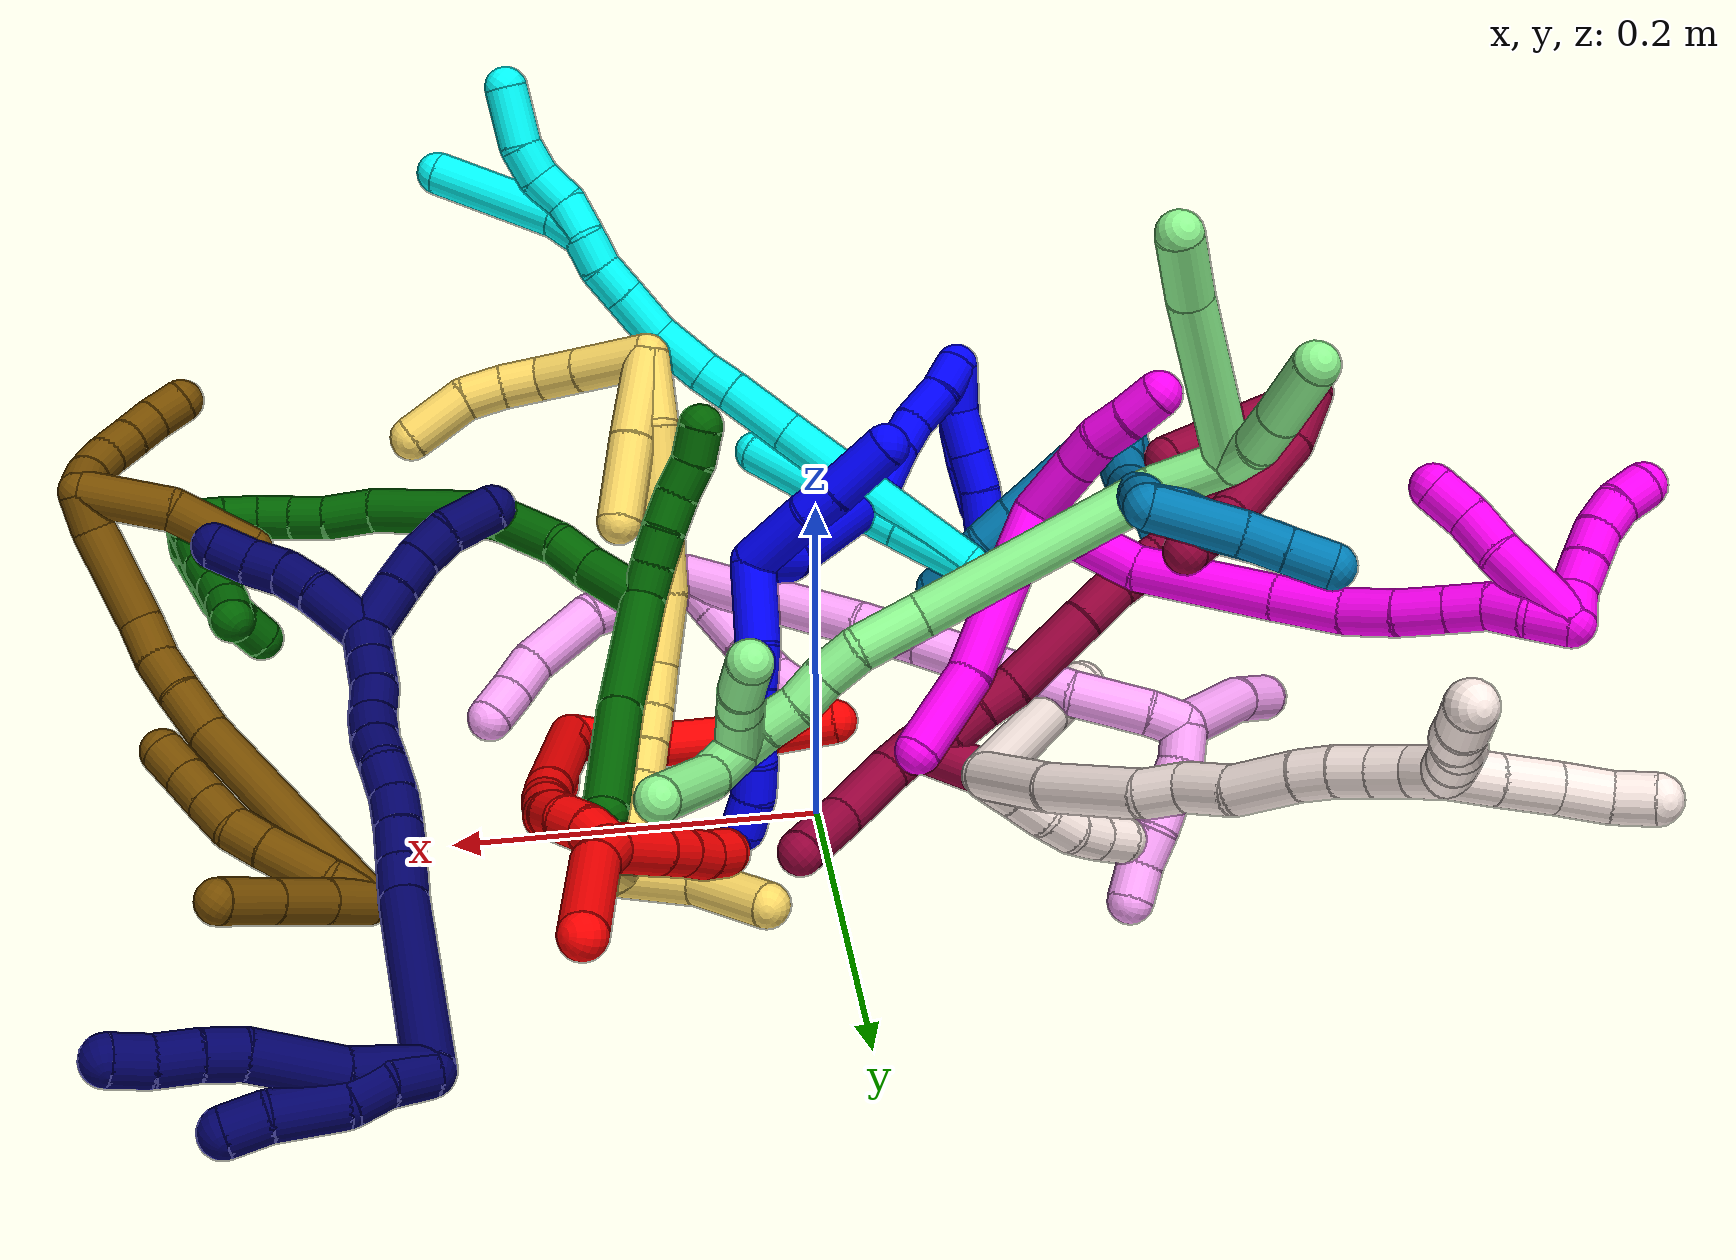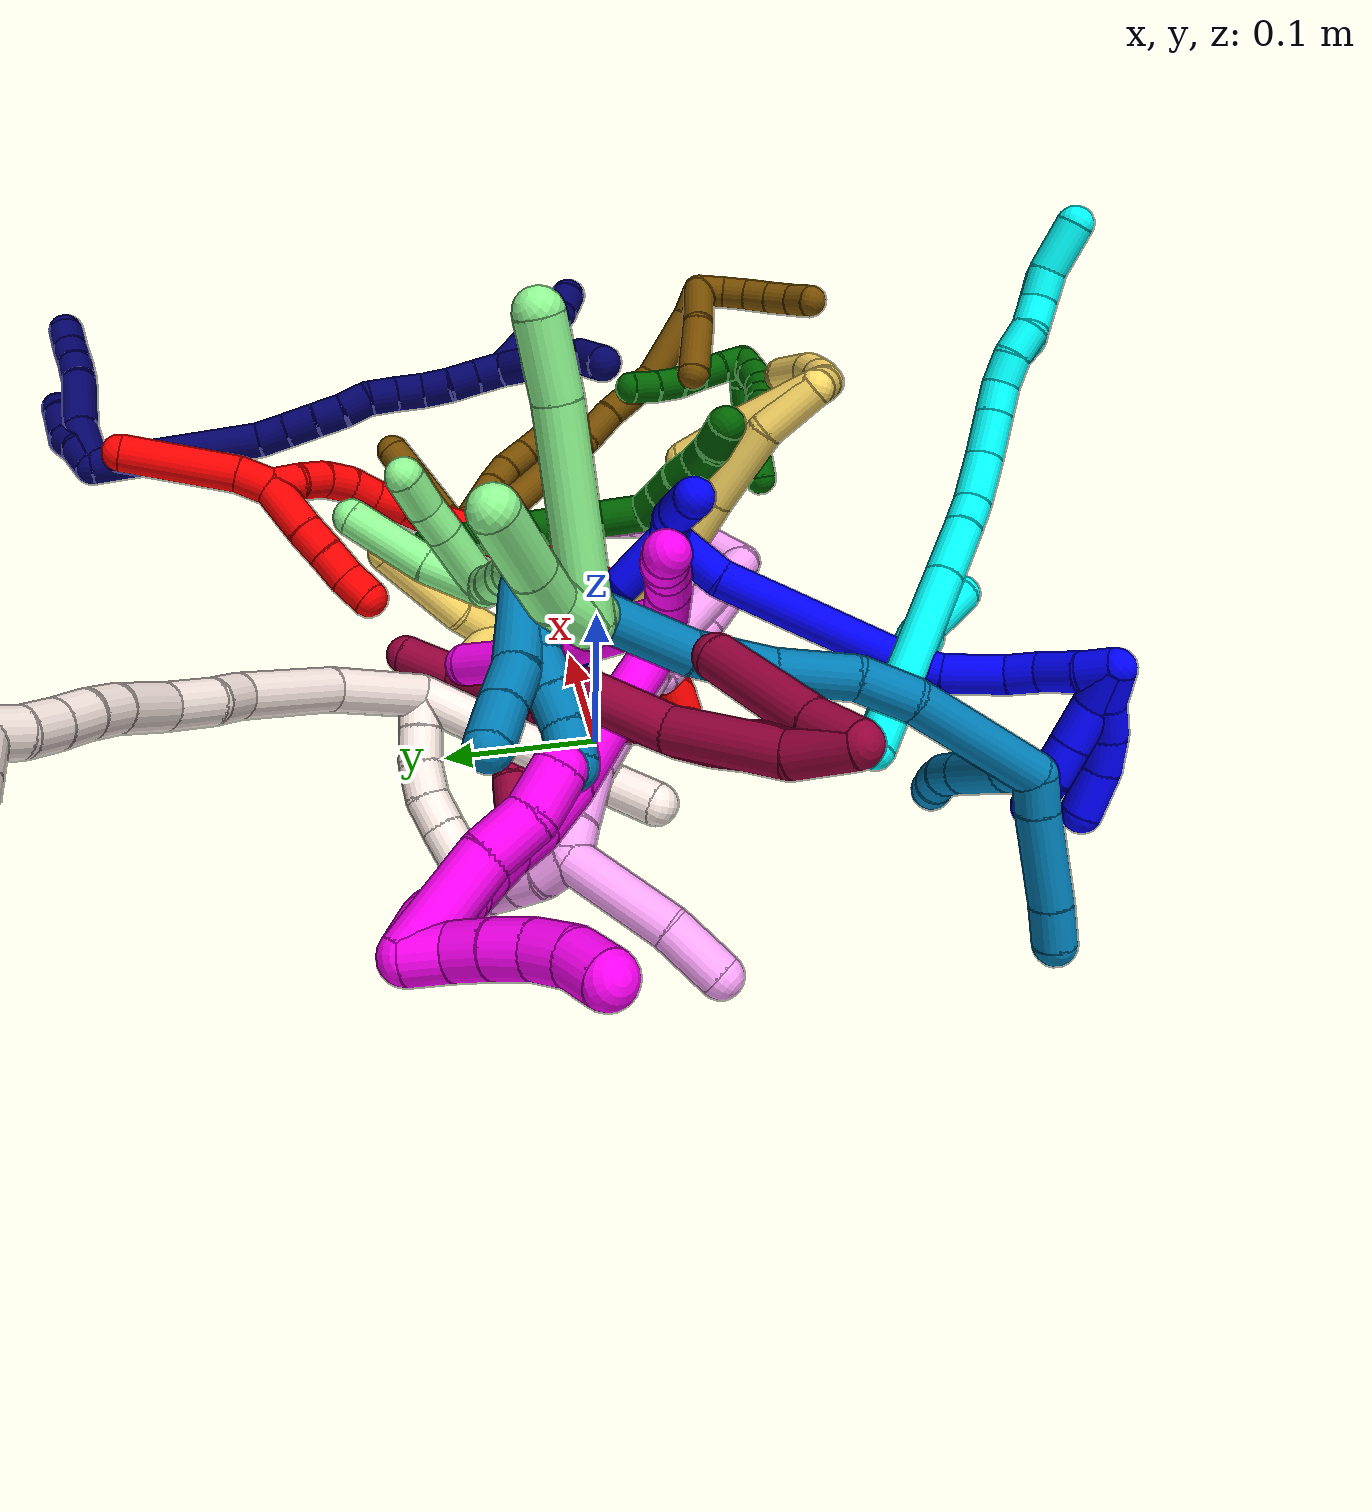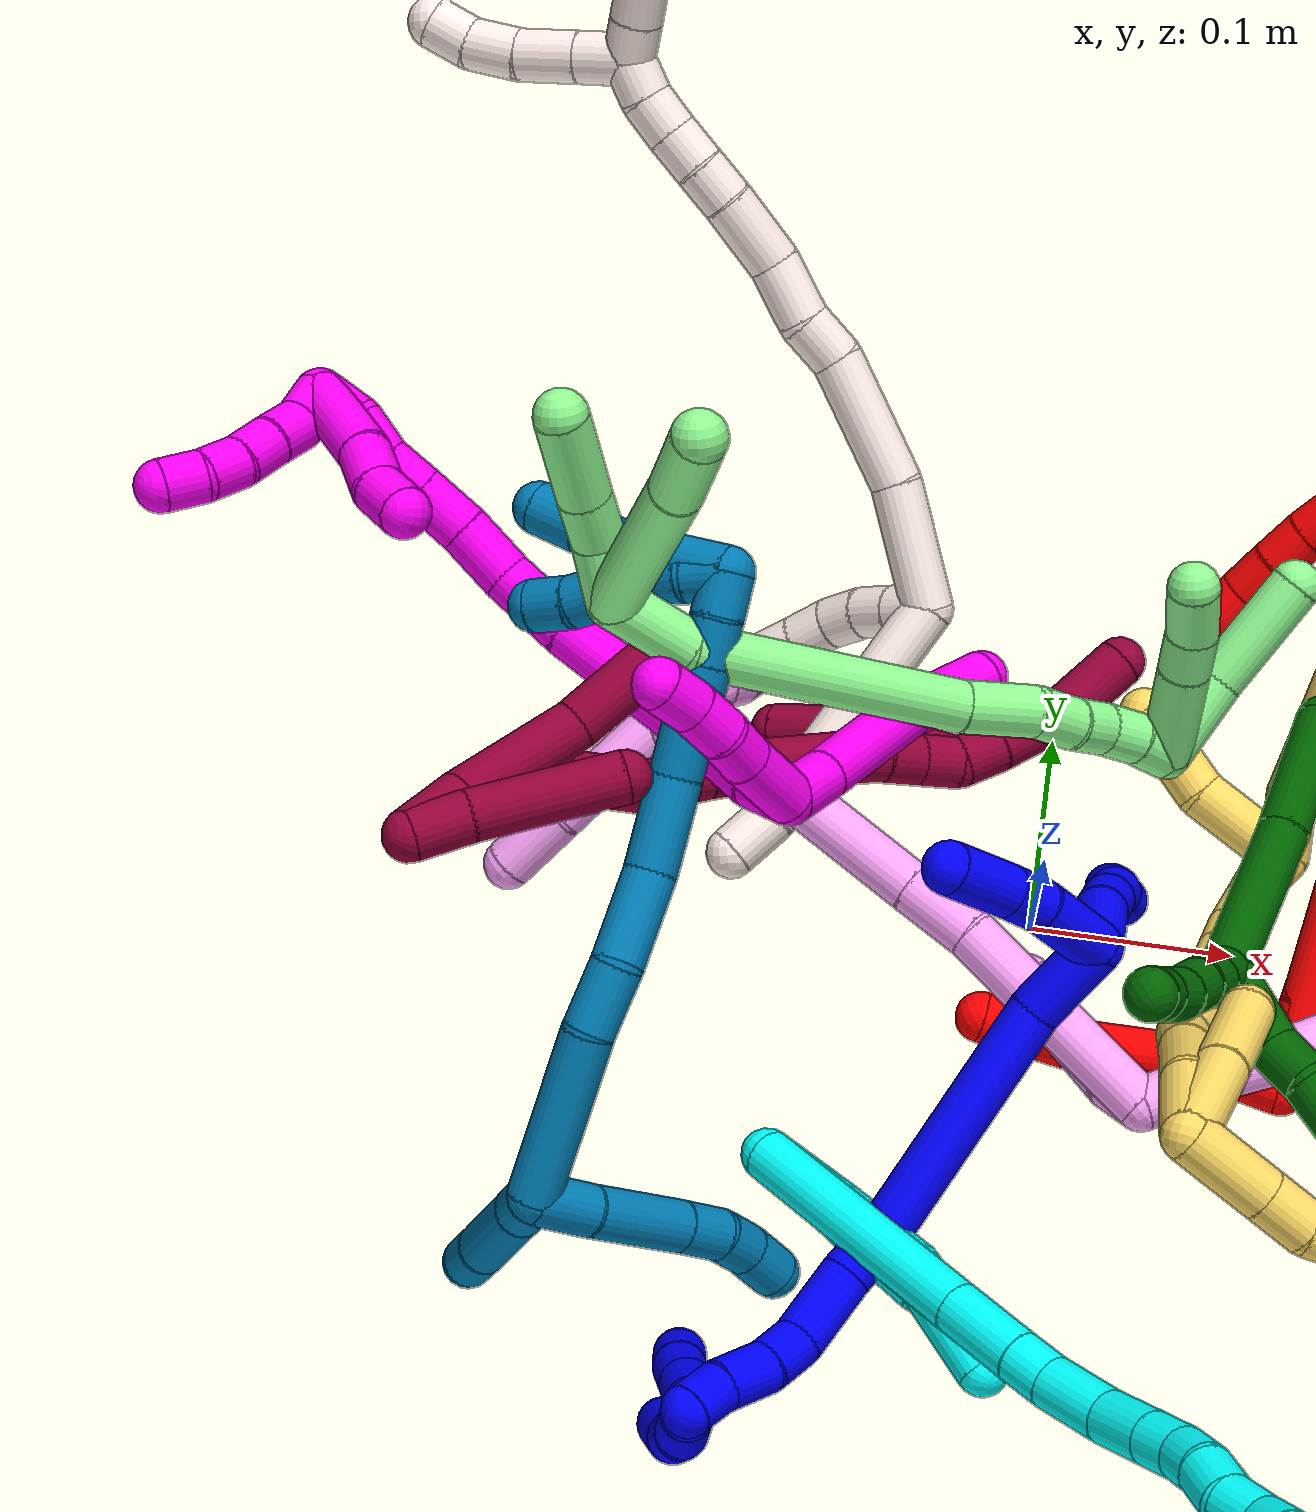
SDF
<sdf version="1.7">
 <world name="default">
  <plugin name="TubeGeneratorPlugin" filename="libtube_generator_plugin.so"/>
  <model name="photoneo_s_sensor">
   <static>1</static>
   <pose>0 0 2 1.57079 1.57079 3.14159</pose>
   <link name="link">
    <inertial><mass>0.1</mass></inertial>
    <sensor name="sensor" type="depth">
     <update_rate>30</update_rate>
     <camera>
      <horizontal_fov>1.22</horizontal_fov>
      <image><width>1920</width><height>1200</height><format>B8G8R8</format></image>
      <clip><near>0.1</near><far>4</far></clip>
      <depth_camera><output>points</output></depth_camera>
     </camera>
     <plugin name="camera_plugin" filename="libgazebo_ros_depth_camera.so">
      <baseline>0.2</baseline>
      <alwaysOn>1</alwaysOn>
      <updateRate>0.0</updateRate>
      <cameraName>camera_ir</cameraName>
      <imageTopicName>/camera/color/image_raw</imageTopicName>
      <cameraInfoTopicName>/camera/color/camera_info</cameraInfoTopicName>
      <depthImageTopicName>/camera/depth/image_raw</depthImageTopicName>
      <depthImageCameraInfoTopicName>/camera/depth/camera_info</depthImageCameraInfoTopicName>
      <pointCloudTopicName>/camera/depth/points</pointCloudTopicName>
      <frameName>fr_optical</frameName>
      <pointCloudCutoff>0.1</pointCloudCutoff>
      <pointCloudCutoffMax>2.0</pointCloudCutoffMax>
      <distortionK1>0</distortionK1>
      <distortionK2>0</distortionK2>
      <distortionK3>0</distortionK3>
      <distortionT1>0</distortionT1>
      <distortionT2>0</distortionT2>
      <CxPrime>0</CxPrime>
      <Cx>0</Cx>
      <Cy>0</Cy>
      <focalLength>0</focalLength>
      <hackBaseline>0</hackBaseline>
     </plugin>
    </sensor>
   </link>
  </model>
  <gravity>0 0 -9.8</gravity>
  <magnetic_field>6e-06 2.3e-05 -4.2e-05</magnetic_field>
  <atmosphere type="adiabatic"/>
  <physics name="default_physics" default="0" type="ode">
   <max_step_size>0.003</max_step_size>
   <real_time_factor>1</real_time_factor>
   <real_time_update_rate>1000</real_time_update_rate>
   <max_contacts>10000</max_contacts>
   <ode>
    <solver>
     <type>quick</type>
     <iters>100</iters>
     <sor>1.3</sor>
     <use_dynamic_moi_rescaling>0</use_dynamic_moi_rescaling>
    </solver>
    <constraints>
     <contact_max_correcting_vel>0</contact_max_correcting_vel>
     <contact_surface_layer>0.001</contact_surface_layer>
     <cfm>0</cfm>
     <erp>0.2</erp>
    </constraints>
   </ode>
  </physics>
  <scene><ambient>0.4 0.4 0.4 1</ambient><background>0.7 0.7 0.7 1</background><shadows>0</shadows></scene>
  <audio><device>default</device></audio>
  <spherical_coordinates>
   <surface_model>EARTH_WGS84</surface_model>
   <latitude_deg>0</latitude_deg>
   <longitude_deg>0</longitude_deg>
   <elevation>0</elevation>
   <heading_deg>0</heading_deg>
  </spherical_coordinates>
  <model name="bin">
   <static>1</static>
   <link name="bottom">
    <collision name="collision-bottom">
     <pose>0 0 -0.01 0 -0 0</pose>
     <geometry><box><size>0.8 0.6 0.02</size></box></geometry>
     <surface>
      <friction><ode><mu>100</mu><mu2>100</mu2></ode></friction>
      <contact><collide_bitmask>65535</collide_bitmask></contact>
     </surface>
    </collision>
   </link>
   <link name="west_wall">
    <collision name="collision-west_wall">
     <pose>-0.41 0 0.1 0 -0 0</pose>
     <geometry><box><size>0.02 0.6 0.2</size></box></geometry>
     <surface>
      <friction><ode><mu>100</mu><mu2>100</mu2></ode></friction>
      <contact><collide_bitmask>65535</collide_bitmask></contact>
     </surface>
    </collision>
   </link>
   <link name="east_wall">
    <collision name="collision-east_wall">
     <pose>0.41 0 0.1 0 -0 0</pose>
     <geometry><box><size>0.02 0.6 0.2</size></box></geometry>
     <surface>
      <friction><ode><mu>100</mu><mu2>100</mu2></ode></friction>
      <contact><collide_bitmask>65535</collide_bitmask></contact>
     </surface>
    </collision>
   </link>
   <link name="south_wall">
    <collision name="collision-south_wall">
     <pose>0 -0.31 0.1 0 -0 0</pose>
     <geometry><box><size>0.8 0.02 0.2</size></box></geometry>
     <surface>
      <friction><ode><mu>100</mu><mu2>100</mu2></ode></friction>
      <contact><collide_bitmask>65535</collide_bitmask></contact>
     </surface>
    </collision>
   </link>
   <link name="north_wall">
    <collision name="collision-north_wall">
     <pose>0 0.31 0.1 0 -0 0</pose>
     <geometry><box><size>0.8 0.02 0.2</size></box></geometry>
     <surface>
      <friction><ode><mu>100</mu><mu2>100</mu2></ode></friction>
      <contact><collide_bitmask>65535</collide_bitmask></contact>
     </surface>
    </collision>
   </link>
  </model>
  <model name="1">
   <static>0</static>
   <link name="1">
    <collision name="collision-cylinder-e_1_2_8">
     <pose>-0.002233 -0.001375 -0.022285 3.07999 -0.099688 -2.03497</pose>
     <geometry><cylinder><radius>0.0125</radius><length>0.044878</length></cylinder></geometry>
     <surface>
      <friction><ode><mu>1.16</mu><mu2>1.16</mu2><slip1>0</slip1><slip2>0</slip2></ode></friction>
      <contact><ode><kp>1e+06</kp><kd>1</kd><max_vel>0</max_vel><min_depth>0.001</min_depth></ode></contact>
     </surface>
    </collision>
    <visual name="visual-cylinder-e_1_2_8">
     <pose>-0.002233 -0.001375 -0.022285 3.07999 -0.099688 -2.03497</pose>
     <geometry><cylinder><radius>0.0125</radius><length>0.044878</length></cylinder></geometry>
     <material><ambient>0 0 1 1</ambient></material>
    </visual>
    <collision name="collision-cylinder-e_2_8_9">
     <pose>-0.003619 -0.003936 -0.056215 3.04005 0.072279 1.23683</pose>
     <geometry><cylinder><radius>0.0125</radius><length>0.023471</length></cylinder></geometry>
     <surface>
      <friction><ode><mu>1.16</mu><mu2>1.16</mu2><slip1>0</slip1><slip2>0</slip2></ode></friction>
      <contact><ode><kp>1e+06</kp><kd>1</kd><max_vel>0</max_vel><min_depth>0.001</min_depth></ode></contact>
     </surface>
    </collision>
    <visual name="visual-cylinder-e_2_8_9">
     <pose>-0.003619 -0.003936 -0.056215 3.04005 0.072279 1.23683</pose>
     <geometry><cylinder><radius>0.0125</radius><length>0.023471</length></cylinder></geometry>
     <material><ambient>0 0 1 1</ambient></material>
    </visual>
    <collision name="collision-cylinder-e_3_9_10">
     <pose>-0.001472 -0.006757 -0.078305 2.98631 0.122317 1.33363</pose>
     <geometry><cylinder><radius>0.0125</radius><length>0.021304</length></cylinder></geometry>
     <surface>
      <friction><ode><mu>1.16</mu><mu2>1.16</mu2><slip1>0</slip1><slip2>0</slip2></ode></friction>
      <contact><ode><kp>1e+06</kp><kd>1</kd><max_vel>0</max_vel><min_depth>0.001</min_depth></ode></contact>
     </surface>
    </collision>
    <visual name="visual-cylinder-e_3_9_10">
     <pose>-0.001472 -0.006757 -0.078305 2.98631 0.122317 1.33363</pose>
     <geometry><cylinder><radius>0.0125</radius><length>0.021304</length></cylinder></geometry>
     <material><ambient>0 0 1 1</ambient></material>
    </visual>
    <collision name="collision-cylinder-e_4_10_11">
     <pose>-0.000352 -0.012247 -0.098031 2.74797 -0.017882 -0.089627</pose>
     <geometry><cylinder><radius>0.0125</radius><length>0.020103</length></cylinder></geometry>
     <surface>
      <friction><ode><mu>1.16</mu><mu2>1.16</mu2><slip1>0</slip1><slip2>0</slip2></ode></friction>
      <contact><ode><kp>1e+06</kp><kd>1</kd><max_vel>0</max_vel><min_depth>0.001</min_depth></ode></contact>
     </surface>
    </collision>
    <visual name="visual-cylinder-e_4_10_11">
     <pose>-0.000352 -0.012247 -0.098031 2.74797 -0.017882 -0.089627</pose>
     <geometry><cylinder><radius>0.0125</radius><length>0.020103</length></cylinder></geometry>
     <material><ambient>0 0 1 1</ambient></material>
    </visual>
    <collision name="collision-cylinder-e_5_11_12">
     <pose>0.00144 -0.020237 -0.116221 2.70698 0.198089 0.845816</pose>
     <geometry><cylinder><radius>0.0125</radius><length>0.020037</length></cylinder></geometry>
     <surface>
      <friction><ode><mu>1.16</mu><mu2>1.16</mu2><slip1>0</slip1><slip2>0</slip2></ode></friction>
      <contact><ode><kp>1e+06</kp><kd>1</kd><max_vel>0</max_vel><min_depth>0.001</min_depth></ode></contact>
     </surface>
    </collision>
    <visual name="visual-cylinder-e_5_11_12">
     <pose>0.00144 -0.020237 -0.116221 2.70698 0.198089 0.845816</pose>
     <geometry><cylinder><radius>0.0125</radius><length>0.020037</length></cylinder></geometry>
     <material><ambient>0 0 1 1</ambient></material>
    </visual>
    <collision name="collision-cylinder-e_6_12_6">
     <pose>0.007606 -0.027628 -0.133727 2.77958 0.428111 1.7421</pose>
     <geometry><cylinder><radius>0.0125</radius><length>0.020208</length></cylinder></geometry>
     <surface>
      <friction><ode><mu>1.16</mu><mu2>1.16</mu2><slip1>0</slip1><slip2>0</slip2></ode></friction>
      <contact><ode><kp>1e+06</kp><kd>1</kd><max_vel>0</max_vel><min_depth>0.001</min_depth></ode></contact>
     </surface>
    </collision>
    <visual name="visual-cylinder-e_6_12_6">
     <pose>0.007606 -0.027628 -0.133727 2.77958 0.428111 1.7421</pose>
     <geometry><cylinder><radius>0.0125</radius><length>0.020208</length></cylinder></geometry>
     <material><ambient>0 0 1 1</ambient></material>
    </visual>
    <collision name="collision-cylinder-e_1_2_13">
     <pose>-0.017063 0.004133 0.011768 -0.337774 -0.939597 0.172711</pose>
     <geometry><cylinder><radius>0.0125</radius><length>0.042272</length></cylinder></geometry>
     <surface>
      <friction><ode><mu>1.16</mu><mu2>1.16</mu2><slip1>0</slip1><slip2>0</slip2></ode></friction>
      <contact><ode><kp>1e+06</kp><kd>1</kd><max_vel>0</max_vel><min_depth>0.001</min_depth></ode></contact>
     </surface>
    </collision>
    <visual name="visual-cylinder-e_1_2_13">
     <pose>-0.017063 0.004133 0.011768 -0.337774 -0.939597 0.172711</pose>
     <geometry><cylinder><radius>0.0125</radius><length>0.042272</length></cylinder></geometry>
     <material><ambient>0 0 1 1</ambient></material>
    </visual>
    <collision name="collision-cylinder-e_2_13_14">
     <pose>-0.042529 0.008531 0.02958 -0.043705 -0.946736 0.022389</pose>
     <geometry><cylinder><radius>0.0125</radius><length>0.020707</length></cylinder></geometry>
     <surface>
      <friction><ode><mu>1.16</mu><mu2>1.16</mu2><slip1>0</slip1><slip2>0</slip2></ode></friction>
      <contact><ode><kp>1e+06</kp><kd>1</kd><max_vel>0</max_vel><min_depth>0.001</min_depth></ode></contact>
     </surface>
    </collision>
    <visual name="visual-cylinder-e_2_13_14">
     <pose>-0.042529 0.008531 0.02958 -0.043705 -0.946736 0.022389</pose>
     <geometry><cylinder><radius>0.0125</radius><length>0.020707</length></cylinder></geometry>
     <material><ambient>0 0 1 1</ambient></material>
    </visual>
    <collision name="collision-cylinder-e_3_14_5">
     <pose>-0.065184 0.009154 0.047429 -0.030352 -0.87885 0.014269</pose>
     <geometry><cylinder><radius>0.0125</radius><length>0.037022</length></cylinder></geometry>
     <surface>
      <friction><ode><mu>1.16</mu><mu2>1.16</mu2><slip1>0</slip1><slip2>0</slip2></ode></friction>
      <contact><ode><kp>1e+06</kp><kd>1</kd><max_vel>0</max_vel><min_depth>0.001</min_depth></ode></contact>
     </surface>
    </collision>
    <visual name="visual-cylinder-e_3_14_5">
     <pose>-0.065184 0.009154 0.047429 -0.030352 -0.87885 0.014269</pose>
     <geometry><cylinder><radius>0.0125</radius><length>0.037022</length></cylinder></geometry>
     <material><ambient>0 0 1 1</ambient></material>
    </visual>
    <collision name="collision-cylinder-e_1_2_15">
     <pose>-0.001375 -0.020464 0.00382 1.38626 -0.065968 -0.0548</pose>
     <geometry><cylinder><radius>0.0125</radius><length>0.041726</length></cylinder></geometry>
     <surface>
      <friction><ode><mu>1.16</mu><mu2>1.16</mu2><slip1>0</slip1><slip2>0</slip2></ode></friction>
      <contact><ode><kp>1e+06</kp><kd>1</kd><max_vel>0</max_vel><min_depth>0.001</min_depth></ode></contact>
     </surface>
    </collision>
    <visual name="visual-cylinder-e_1_2_15">
     <pose>-0.001375 -0.020464 0.00382 1.38626 -0.065968 -0.0548</pose>
     <geometry><cylinder><radius>0.0125</radius><length>0.041726</length></cylinder></geometry>
     <material><ambient>0 0 1 1</ambient></material>
    </visual>
    <collision name="collision-cylinder-e_2_15_16">
     <pose>0.00248 -0.097348 0.031454 1.17139 0.085208 0.056541</pose>
     <geometry><cylinder><radius>0.0125</radius><length>0.122926</length></cylinder></geometry>
     <surface>
      <friction><ode><mu>1.16</mu><mu2>1.16</mu2><slip1>0</slip1><slip2>0</slip2></ode></friction>
      <contact><ode><kp>1e+06</kp><kd>1</kd><max_vel>0</max_vel><min_depth>0.001</min_depth></ode></contact>
     </surface>
    </collision>
    <visual name="visual-cylinder-e_2_15_16">
     <pose>0.00248 -0.097348 0.031454 1.17139 0.085208 0.056541</pose>
     <geometry><cylinder><radius>0.0125</radius><length>0.122926</length></cylinder></geometry>
     <material><ambient>0 0 1 1</ambient></material>
    </visual>
    <collision name="collision-cylinder-e_3_16_17">
     <pose>0.006942 -0.16487 0.062503 0.993246 -0.057991 -0.031433</pose>
     <geometry><cylinder><radius>0.0125</radius><length>0.026547</length></cylinder></geometry>
     <surface>
      <friction><ode><mu>1.16</mu><mu2>1.16</mu2><slip1>0</slip1><slip2>0</slip2></ode></friction>
      <contact><ode><kp>1e+06</kp><kd>1</kd><max_vel>0</max_vel><min_depth>0.001</min_depth></ode></contact>
     </surface>
    </collision>
    <visual name="visual-cylinder-e_3_16_17">
     <pose>0.006942 -0.16487 0.062503 0.993246 -0.057991 -0.031433</pose>
     <geometry><cylinder><radius>0.0125</radius><length>0.026547</length></cylinder></geometry>
     <material><ambient>0 0 1 1</ambient></material>
    </visual>
    <collision name="collision-cylinder-e_4_17_18">
     <pose>0.005887 -0.188562 0.085187 0.68376 -0.014296 -0.005088</pose>
     <geometry><cylinder><radius>0.0125</radius><length>0.039863</length></cylinder></geometry>
     <surface>
      <friction><ode><mu>1.16</mu><mu2>1.16</mu2><slip1>0</slip1><slip2>0</slip2></ode></friction>
      <contact><ode><kp>1e+06</kp><kd>1</kd><max_vel>0</max_vel><min_depth>0.001</min_depth></ode></contact>
     </surface>
    </collision>
    <visual name="visual-cylinder-e_4_17_18">
     <pose>0.005887 -0.188562 0.085187 0.68376 -0.014296 -0.005088</pose>
     <geometry><cylinder><radius>0.0125</radius><length>0.039863</length></cylinder></geometry>
     <material><ambient>0 0 1 1</ambient></material>
    </visual>
    <collision name="collision-cylinder-e_5_18_19">
     <pose>0.002961 -0.20603 0.109813 0.488604 -0.248861 -0.062338</pose>
     <geometry><cylinder><radius>0.0125</radius><length>0.021447</length></cylinder></geometry>
     <surface>
      <friction><ode><mu>1.16</mu><mu2>1.16</mu2><slip1>0</slip1><slip2>0</slip2></ode></friction>
      <contact><ode><kp>1e+06</kp><kd>1</kd><max_vel>0</max_vel><min_depth>0.001</min_depth></ode></contact>
     </surface>
    </collision>
    <visual name="visual-cylinder-e_5_18_19">
     <pose>0.002961 -0.20603 0.109813 0.488604 -0.248861 -0.062338</pose>
     <geometry><cylinder><radius>0.0125</radius><length>0.021447</length></cylinder></geometry>
     <material><ambient>0 0 1 1</ambient></material>
    </visual>
    <collision name="collision-cylinder-e_6_19_20">
     <pose>-0.005883 -0.216333 0.129417 0.479741 -0.485638 -0.12102</pose>
     <geometry><cylinder><radius>0.0125</radius><length>0.026579</length></cylinder></geometry>
     <surface>
      <friction><ode><mu>1.16</mu><mu2>1.16</mu2><slip1>0</slip1><slip2>0</slip2></ode></friction>
      <contact><ode><kp>1e+06</kp><kd>1</kd><max_vel>0</max_vel><min_depth>0.001</min_depth></ode></contact>
     </surface>
    </collision>
    <visual name="visual-cylinder-e_6_19_20">
     <pose>-0.005883 -0.216333 0.129417 0.479741 -0.485638 -0.12102</pose>
     <geometry><cylinder><radius>0.0125</radius><length>0.026579</length></cylinder></geometry>
     <material><ambient>0 0 1 1</ambient></material>
    </visual>
    <collision name="collision-cylinder-e_7_20_1">
     <pose>-0.014978 -0.226189 0.148861 0.456705 -0.280173 -0.06552</pose>
     <geometry><cylinder><radius>0.0125</radius><length>0.020912</length></cylinder></geometry>
     <surface>
      <friction><ode><mu>1.16</mu><mu2>1.16</mu2><slip1>0</slip1><slip2>0</slip2></ode></friction>
      <contact><ode><kp>1e+06</kp><kd>1</kd><max_vel>0</max_vel><min_depth>0.001</min_depth></ode></contact>
     </surface>
    </collision>
    <visual name="visual-cylinder-e_7_20_1">
     <pose>-0.014978 -0.226189 0.148861 0.456705 -0.280173 -0.06552</pose>
     <geometry><cylinder><radius>0.0125</radius><length>0.020912</length></cylinder></geometry>
     <material><ambient>0 0 1 1</ambient></material>
    </visual>
    <collision name="collision-cylinder-e_1_1_21">
     <pose>-0.016497 -0.235982 0.145132 2.74345 0.098854 0.48091</pose>
     <geometry><cylinder><radius>0.0125</radius><length>0.027794</length></cylinder></geometry>
     <surface>
      <friction><ode><mu>1.16</mu><mu2>1.16</mu2><slip1>0</slip1><slip2>0</slip2></ode></friction>
      <contact><ode><kp>1e+06</kp><kd>1</kd><max_vel>0</max_vel><min_depth>0.001</min_depth></ode></contact>
     </surface>
    </collision>
    <visual name="visual-cylinder-e_1_1_21">
     <pose>-0.016497 -0.235982 0.145132 2.74345 0.098854 0.48091</pose>
     <geometry><cylinder><radius>0.0125</radius><length>0.027794</length></cylinder></geometry>
     <material><ambient>0 0 1 1</ambient></material>
    </visual>
    <collision name="collision-cylinder-e_2_21_22">
     <pose>-0.017805 -0.245998 0.119992 2.78234 -0.199649 -1.00812</pose>
     <geometry><cylinder><radius>0.0125</radius><length>0.027013</length></cylinder></geometry>
     <surface>
      <friction><ode><mu>1.16</mu><mu2>1.16</mu2><slip1>0</slip1><slip2>0</slip2></ode></friction>
      <contact><ode><kp>1e+06</kp><kd>1</kd><max_vel>0</max_vel><min_depth>0.001</min_depth></ode></contact>
     </surface>
    </collision>
    <visual name="visual-cylinder-e_2_21_22">
     <pose>-0.017805 -0.245998 0.119992 2.78234 -0.199649 -1.00812</pose>
     <geometry><cylinder><radius>0.0125</radius><length>0.027013</length></cylinder></geometry>
     <material><ambient>0 0 1 1</ambient></material>
    </visual>
    <collision name="collision-cylinder-e_3_22_23">
     <pose>-0.022877 -0.254627 0.097042 2.78145 -0.209102 -1.0458</pose>
     <geometry><cylinder><radius>0.0125</radius><length>0.023063</length></cylinder></geometry>
     <surface>
      <friction><ode><mu>1.16</mu><mu2>1.16</mu2><slip1>0</slip1><slip2>0</slip2></ode></friction>
      <contact><ode><kp>1e+06</kp><kd>1</kd><max_vel>0</max_vel><min_depth>0.001</min_depth></ode></contact>
     </surface>
    </collision>
    <visual name="visual-cylinder-e_3_22_23">
     <pose>-0.022877 -0.254627 0.097042 2.78145 -0.209102 -1.0458</pose>
     <geometry><cylinder><radius>0.0125</radius><length>0.023063</length></cylinder></geometry>
     <material><ambient>0 0 1 1</ambient></material>
    </visual>
    <collision name="collision-cylinder-e_4_23_4">
     <pose>-0.025927 -0.262152 0.076026 2.81442 -0.059323 -0.355706</pose>
     <geometry><cylinder><radius>0.0125</radius><length>0.02213</length></cylinder></geometry>
     <surface>
      <friction><ode><mu>1.16</mu><mu2>1.16</mu2><slip1>0</slip1><slip2>0</slip2></ode></friction>
      <contact><ode><kp>1e+06</kp><kd>1</kd><max_vel>0</max_vel><min_depth>0.001</min_depth></ode></contact>
     </surface>
    </collision>
    <visual name="visual-cylinder-e_4_23_4">
     <pose>-0.025927 -0.262152 0.076026 2.81442 -0.059323 -0.355706</pose>
     <geometry><cylinder><radius>0.0125</radius><length>0.02213</length></cylinder></geometry>
     <material><ambient>0 0 1 1</ambient></material>
    </visual>
    <collision name="collision-cylinder-e_1_1_24">
     <pose>-0.016119 -0.237372 0.148304 2.52748 0.148263 0.460145</pose>
     <geometry><cylinder><radius>0.0125</radius><length>0.023694</length></cylinder></geometry>
     <surface>
      <friction><ode><mu>1.16</mu><mu2>1.16</mu2><slip1>0</slip1><slip2>0</slip2></ode></friction>
      <contact><ode><kp>1e+06</kp><kd>1</kd><max_vel>0</max_vel><min_depth>0.001</min_depth></ode></contact>
     </surface>
    </collision>
    <visual name="visual-cylinder-e_1_1_24">
     <pose>-0.016119 -0.237372 0.148304 2.52748 0.148263 0.460145</pose>
     <geometry><cylinder><radius>0.0125</radius><length>0.023694</length></cylinder></geometry>
     <material><ambient>0 0 1 1</ambient></material>
    </visual>
    <collision name="collision-cylinder-e_2_24_25">
     <pose>-0.011582 -0.253133 0.131987 2.21311 0.242768 0.477904</pose>
     <geometry><cylinder><radius>0.0125</radius><length>0.023183</length></cylinder></geometry>
     <surface>
      <friction><ode><mu>1.16</mu><mu2>1.16</mu2><slip1>0</slip1><slip2>0</slip2></ode></friction>
      <contact><ode><kp>1e+06</kp><kd>1</kd><max_vel>0</max_vel><min_depth>0.001</min_depth></ode></contact>
     </surface>
    </collision>
    <visual name="visual-cylinder-e_2_24_25">
     <pose>-0.011582 -0.253133 0.131987 2.21311 0.242768 0.477904</pose>
     <geometry><cylinder><radius>0.0125</radius><length>0.023183</length></cylinder></geometry>
     <material><ambient>0 0 1 1</ambient></material>
    </visual>
    <collision name="collision-cylinder-e_3_25_26">
     <pose>-0.008444 -0.269668 0.116469 2.43283 0.030423 0.082184</pose>
     <geometry><cylinder><radius>0.0125</radius><length>0.023134</length></cylinder></geometry>
     <surface>
      <friction><ode><mu>1.16</mu><mu2>1.16</mu2><slip1>0</slip1><slip2>0</slip2></ode></friction>
      <contact><ode><kp>1e+06</kp><kd>1</kd><max_vel>0</max_vel><min_depth>0.001</min_depth></ode></contact>
     </surface>
    </collision>
    <visual name="visual-cylinder-e_3_25_26">
     <pose>-0.008444 -0.269668 0.116469 2.43283 0.030423 0.082184</pose>
     <geometry><cylinder><radius>0.0125</radius><length>0.023134</length></cylinder></geometry>
     <material><ambient>0 0 1 1</ambient></material>
    </visual>
    <collision name="collision-cylinder-e_4_26_3">
     <pose>-0.010321 -0.284036 0.094538 2.66193 -0.149204 -0.593248</pose>
     <geometry><cylinder><radius>0.0125</radius><length>0.029988</length></cylinder></geometry>
     <surface>
      <friction><ode><mu>1.16</mu><mu2>1.16</mu2><slip1>0</slip1><slip2>0</slip2></ode></friction>
      <contact><ode><kp>1e+06</kp><kd>1</kd><max_vel>0</max_vel><min_depth>0.001</min_depth></ode></contact>
     </surface>
    </collision>
    <visual name="visual-cylinder-e_4_26_3">
     <pose>-0.010321 -0.284036 0.094538 2.66193 -0.149204 -0.593248</pose>
     <geometry><cylinder><radius>0.0125</radius><length>0.029988</length></cylinder></geometry>
     <material><ambient>0 0 1 1</ambient></material>
    </visual>
    <collision name="collision-sphere-3">
     <pose>-0.01255 -0.290879 0.081383 0 -0 0</pose>
     <geometry><sphere><radius>0.0125</radius></sphere></geometry>
     <surface>
      <friction><ode><mu>1.16</mu><mu2>1.16</mu2><slip1>0</slip1><slip2>0</slip2></ode></friction>
      <contact><ode><kp>1e+06</kp><kd>1</kd><max_vel>0</max_vel><min_depth>0.001</min_depth></ode></contact>
     </surface>
    </collision>
    <visual name="visual-sphere-3">
     <pose>-0.01255 -0.290879 0.081383 0 -0 0</pose>
     <geometry><sphere><radius>0.0125</radius></sphere></geometry>
     <material><ambient>0 0 1 1</ambient></material>
    </visual>
    <collision name="collision-sphere-26">
     <pose>-0.008092 -0.277194 0.107692 0 -0 0</pose>
     <geometry><sphere><radius>0.0125</radius></sphere></geometry>
     <surface>
      <friction><ode><mu>1.16</mu><mu2>1.16</mu2><slip1>0</slip1><slip2>0</slip2></ode></friction>
      <contact><ode><kp>1e+06</kp><kd>1</kd><max_vel>0</max_vel><min_depth>0.001</min_depth></ode></contact>
     </surface>
    </collision>
    <visual name="visual-sphere-26">
     <pose>-0.008092 -0.277194 0.107692 0 -0 0</pose>
     <geometry><sphere><radius>0.0125</radius></sphere></geometry>
     <material><ambient>0 0 1 1</ambient></material>
    </visual>
    <collision name="collision-sphere-25">
     <pose>-0.008796 -0.262142 0.125247 0 -0 0</pose>
     <geometry><sphere><radius>0.0125</radius></sphere></geometry>
     <surface>
      <friction><ode><mu>1.16</mu><mu2>1.16</mu2><slip1>0</slip1><slip2>0</slip2></ode></friction>
      <contact><ode><kp>1e+06</kp><kd>1</kd><max_vel>0</max_vel><min_depth>0.001</min_depth></ode></contact>
     </surface>
    </collision>
    <visual name="visual-sphere-25">
     <pose>-0.008796 -0.262142 0.125247 0 -0 0</pose>
     <geometry><sphere><radius>0.0125</radius></sphere></geometry>
     <material><ambient>0 0 1 1</ambient></material>
    </visual>
    <collision name="collision-sphere-24">
     <pose>-0.014369 -0.244124 0.138727 0 -0 0</pose>
     <geometry><sphere><radius>0.0125</radius></sphere></geometry>
     <surface>
      <friction><ode><mu>1.16</mu><mu2>1.16</mu2><slip1>0</slip1><slip2>0</slip2></ode></friction>
      <contact><ode><kp>1e+06</kp><kd>1</kd><max_vel>0</max_vel><min_depth>0.001</min_depth></ode></contact>
     </surface>
    </collision>
    <visual name="visual-sphere-24">
     <pose>-0.014369 -0.244124 0.138727 0 -0 0</pose>
     <geometry><sphere><radius>0.0125</radius></sphere></geometry>
     <material><ambient>0 0 1 1</ambient></material>
    </visual>
    <collision name="collision-sphere-4">
     <pose>-0.026583 -0.265702 0.065566 0 -0 0</pose>
     <geometry><sphere><radius>0.0125</radius></sphere></geometry>
     <surface>
      <friction><ode><mu>1.16</mu><mu2>1.16</mu2><slip1>0</slip1><slip2>0</slip2></ode></friction>
      <contact><ode><kp>1e+06</kp><kd>1</kd><max_vel>0</max_vel><min_depth>0.001</min_depth></ode></contact>
     </surface>
    </collision>
    <visual name="visual-sphere-4">
     <pose>-0.026583 -0.265702 0.065566 0 -0 0</pose>
     <geometry><sphere><radius>0.0125</radius></sphere></geometry>
     <material><ambient>0 0 1 1</ambient></material>
    </visual>
    <collision name="collision-sphere-23">
     <pose>-0.025271 -0.258602 0.086486 0 -0 0</pose>
     <geometry><sphere><radius>0.0125</radius></sphere></geometry>
     <surface>
      <friction><ode><mu>1.16</mu><mu2>1.16</mu2><slip1>0</slip1><slip2>0</slip2></ode></friction>
      <contact><ode><kp>1e+06</kp><kd>1</kd><max_vel>0</max_vel><min_depth>0.001</min_depth></ode></contact>
     </surface>
    </collision>
    <visual name="visual-sphere-23">
     <pose>-0.025271 -0.258602 0.086486 0 -0 0</pose>
     <geometry><sphere><radius>0.0125</radius></sphere></geometry>
     <material><ambient>0 0 1 1</ambient></material>
    </visual>
    <collision name="collision-sphere-22">
     <pose>-0.020483 -0.250652 0.107599 0 -0 0</pose>
     <geometry><sphere><radius>0.0125</radius></sphere></geometry>
     <surface>
      <friction><ode><mu>1.16</mu><mu2>1.16</mu2><slip1>0</slip1><slip2>0</slip2></ode></friction>
      <contact><ode><kp>1e+06</kp><kd>1</kd><max_vel>0</max_vel><min_depth>0.001</min_depth></ode></contact>
     </surface>
    </collision>
    <visual name="visual-sphere-22">
     <pose>-0.020483 -0.250652 0.107599 0 -0 0</pose>
     <geometry><sphere><radius>0.0125</radius></sphere></geometry>
     <material><ambient>0 0 1 1</ambient></material>
    </visual>
    <collision name="collision-sphere-21">
     <pose>-0.015126 -0.241343 0.132385 0 -0 0</pose>
     <geometry><sphere><radius>0.0125</radius></sphere></geometry>
     <surface>
      <friction><ode><mu>1.16</mu><mu2>1.16</mu2><slip1>0</slip1><slip2>0</slip2></ode></friction>
      <contact><ode><kp>1e+06</kp><kd>1</kd><max_vel>0</max_vel><min_depth>0.001</min_depth></ode></contact>
     </surface>
    </collision>
    <visual name="visual-sphere-21">
     <pose>-0.015126 -0.241343 0.132385 0 -0 0</pose>
     <geometry><sphere><radius>0.0125</radius></sphere></geometry>
     <material><ambient>0 0 1 1</ambient></material>
    </visual>
    <collision name="collision-sphere-1">
     <pose>-0.017869 -0.23062 0.15788 0 -0 0</pose>
     <geometry><sphere><radius>0.0125</radius></sphere></geometry>
     <surface>
      <friction><ode><mu>1.16</mu><mu2>1.16</mu2><slip1>0</slip1><slip2>0</slip2></ode></friction>
      <contact><ode><kp>1e+06</kp><kd>1</kd><max_vel>0</max_vel><min_depth>0.001</min_depth></ode></contact>
     </surface>
    </collision>
    <visual name="visual-sphere-1">
     <pose>-0.017869 -0.23062 0.15788 0 -0 0</pose>
     <geometry><sphere><radius>0.0125</radius></sphere></geometry>
     <material><ambient>0 0 1 1</ambient></material>
    </visual>
    <collision name="collision-sphere-12">
     <pose>0.003412 -0.024373 -0.125131 0 -0 0</pose>
     <geometry><sphere><radius>0.0125</radius></sphere></geometry>
     <surface>
      <friction><ode><mu>1.16</mu><mu2>1.16</mu2><slip1>0</slip1><slip2>0</slip2></ode></friction>
      <contact><ode><kp>1e+06</kp><kd>1</kd><max_vel>0</max_vel><min_depth>0.001</min_depth></ode></contact>
     </surface>
    </collision>
    <visual name="visual-sphere-12">
     <pose>0.003412 -0.024373 -0.125131 0 -0 0</pose>
     <geometry><sphere><radius>0.0125</radius></sphere></geometry>
     <material><ambient>0 0 1 1</ambient></material>
    </visual>
    <collision name="collision-sphere-11">
     <pose>-0.000532 -0.016101 -0.107312 0 -0 0</pose>
     <geometry><sphere><radius>0.0125</radius></sphere></geometry>
     <surface>
      <friction><ode><mu>1.16</mu><mu2>1.16</mu2><slip1>0</slip1><slip2>0</slip2></ode></friction>
      <contact><ode><kp>1e+06</kp><kd>1</kd><max_vel>0</max_vel><min_depth>0.001</min_depth></ode></contact>
     </surface>
    </collision>
    <visual name="visual-sphere-11">
     <pose>-0.000532 -0.016101 -0.107312 0 -0 0</pose>
     <geometry><sphere><radius>0.0125</radius></sphere></geometry>
     <material><ambient>0 0 1 1</ambient></material>
    </visual>
    <collision name="collision-sphere-10">
     <pose>-0.000172 -0.008393 -0.08875 0 -0 0</pose>
     <geometry><sphere><radius>0.0125</radius></sphere></geometry>
     <surface>
      <friction><ode><mu>1.16</mu><mu2>1.16</mu2><slip1>0</slip1><slip2>0</slip2></ode></friction>
      <contact><ode><kp>1e+06</kp><kd>1</kd><max_vel>0</max_vel><min_depth>0.001</min_depth></ode></contact>
     </surface>
    </collision>
    <visual name="visual-sphere-10">
     <pose>-0.000172 -0.008393 -0.08875 0 -0 0</pose>
     <geometry><sphere><radius>0.0125</radius></sphere></geometry>
     <material><ambient>0 0 1 1</ambient></material>
    </visual>
    <collision name="collision-sphere-9">
     <pose>-0.002771 -0.005122 -0.06786 0 -0 0</pose>
     <geometry><sphere><radius>0.0125</radius></sphere></geometry>
     <surface>
      <friction><ode><mu>1.16</mu><mu2>1.16</mu2><slip1>0</slip1><slip2>0</slip2></ode></friction>
      <contact><ode><kp>1e+06</kp><kd>1</kd><max_vel>0</max_vel><min_depth>0.001</min_depth></ode></contact>
     </surface>
    </collision>
    <visual name="visual-sphere-9">
     <pose>-0.002771 -0.005122 -0.06786 0 -0 0</pose>
     <geometry><sphere><radius>0.0125</radius></sphere></geometry>
     <material><ambient>0 0 1 1</ambient></material>
    </visual>
    <collision name="collision-sphere-2">
     <geometry><sphere><radius>0.0125</radius></sphere></geometry>
     <surface>
      <friction><ode><mu>1.16</mu><mu2>1.16</mu2><slip1>0</slip1><slip2>0</slip2></ode></friction>
      <contact><ode><kp>1e+06</kp><kd>1</kd><max_vel>0</max_vel><min_depth>0.001</min_depth></ode></contact>
     </surface>
    </collision>
    <visual name="visual-sphere-2">
     <geometry><sphere><radius>0.0125</radius></sphere></geometry>
     <material><ambient>0 0 1 1</ambient></material>
    </visual>
    <collision name="collision-sphere-19">
     <pose>0.00032 -0.210908 0.11899 0 -0 0</pose>
     <geometry><sphere><radius>0.0125</radius></sphere></geometry>
     <surface>
      <friction><ode><mu>1.16</mu><mu2>1.16</mu2><slip1>0</slip1><slip2>0</slip2></ode></friction>
      <contact><ode><kp>1e+06</kp><kd>1</kd><max_vel>0</max_vel><min_depth>0.001</min_depth></ode></contact>
     </surface>
    </collision>
    <visual name="visual-sphere-19">
     <pose>0.00032 -0.210908 0.11899 0 -0 0</pose>
     <geometry><sphere><radius>0.0125</radius></sphere></geometry>
     <material><ambient>0 0 1 1</ambient></material>
    </visual>
    <collision name="collision-sphere-8">
     <pose>-0.004466 -0.002749 -0.044571 0 -0 0</pose>
     <geometry><sphere><radius>0.0125</radius></sphere></geometry>
     <surface>
      <friction><ode><mu>1.16</mu><mu2>1.16</mu2><slip1>0</slip1><slip2>0</slip2></ode></friction>
      <contact><ode><kp>1e+06</kp><kd>1</kd><max_vel>0</max_vel><min_depth>0.001</min_depth></ode></contact>
     </surface>
    </collision>
    <visual name="visual-sphere-8">
     <pose>-0.004466 -0.002749 -0.044571 0 -0 0</pose>
     <geometry><sphere><radius>0.0125</radius></sphere></geometry>
     <material><ambient>0 0 1 1</ambient></material>
    </visual>
    <collision name="collision-sphere-6">
     <pose>0.011801 -0.030884 -0.142323 0 -0 0</pose>
     <geometry><sphere><radius>0.0125</radius></sphere></geometry>
     <surface>
      <friction><ode><mu>1.16</mu><mu2>1.16</mu2><slip1>0</slip1><slip2>0</slip2></ode></friction>
      <contact><ode><kp>1e+06</kp><kd>1</kd><max_vel>0</max_vel><min_depth>0.001</min_depth></ode></contact>
     </surface>
    </collision>
    <visual name="visual-sphere-6">
     <pose>0.011801 -0.030884 -0.142323 0 -0 0</pose>
     <geometry><sphere><radius>0.0125</radius></sphere></geometry>
     <material><ambient>0 0 1 1</ambient></material>
    </visual>
    <collision name="collision-sphere-13">
     <pose>-0.034127 0.008266 0.023536 0 -0 0</pose>
     <geometry><sphere><radius>0.0125</radius></sphere></geometry>
     <surface>
      <friction><ode><mu>1.16</mu><mu2>1.16</mu2><slip1>0</slip1><slip2>0</slip2></ode></friction>
      <contact><ode><kp>1e+06</kp><kd>1</kd><max_vel>0</max_vel><min_depth>0.001</min_depth></ode></contact>
     </surface>
    </collision>
    <visual name="visual-sphere-13">
     <pose>-0.034127 0.008266 0.023536 0 -0 0</pose>
     <geometry><sphere><radius>0.0125</radius></sphere></geometry>
     <material><ambient>0 0 1 1</ambient></material>
    </visual>
    <collision name="collision-sphere-14">
     <pose>-0.05093 0.008795 0.035624 0 -0 0</pose>
     <geometry><sphere><radius>0.0125</radius></sphere></geometry>
     <surface>
      <friction><ode><mu>1.16</mu><mu2>1.16</mu2><slip1>0</slip1><slip2>0</slip2></ode></friction>
      <contact><ode><kp>1e+06</kp><kd>1</kd><max_vel>0</max_vel><min_depth>0.001</min_depth></ode></contact>
     </surface>
    </collision>
    <visual name="visual-sphere-14">
     <pose>-0.05093 0.008795 0.035624 0 -0 0</pose>
     <geometry><sphere><radius>0.0125</radius></sphere></geometry>
     <material><ambient>0 0 1 1</ambient></material>
    </visual>
    <collision name="collision-sphere-5">
     <pose>-0.079437 0.009512 0.059234 0 -0 0</pose>
     <geometry><sphere><radius>0.0125</radius></sphere></geometry>
     <surface>
      <friction><ode><mu>1.16</mu><mu2>1.16</mu2><slip1>0</slip1><slip2>0</slip2></ode></friction>
      <contact><ode><kp>1e+06</kp><kd>1</kd><max_vel>0</max_vel><min_depth>0.001</min_depth></ode></contact>
     </surface>
    </collision>
    <visual name="visual-sphere-5">
     <pose>-0.079437 0.009512 0.059234 0 -0 0</pose>
     <geometry><sphere><radius>0.0125</radius></sphere></geometry>
     <material><ambient>0 0 1 1</ambient></material>
    </visual>
    <collision name="collision-sphere-15">
     <pose>-0.002751 -0.040928 0.00764 0 -0 0</pose>
     <geometry><sphere><radius>0.0125</radius></sphere></geometry>
     <surface>
      <friction><ode><mu>1.16</mu><mu2>1.16</mu2><slip1>0</slip1><slip2>0</slip2></ode></friction>
      <contact><ode><kp>1e+06</kp><kd>1</kd><max_vel>0</max_vel><min_depth>0.001</min_depth></ode></contact>
     </surface>
    </collision>
    <visual name="visual-sphere-15">
     <pose>-0.002751 -0.040928 0.00764 0 -0 0</pose>
     <geometry><sphere><radius>0.0125</radius></sphere></geometry>
     <material><ambient>0 0 1 1</ambient></material>
    </visual>
    <collision name="collision-sphere-16">
     <pose>0.007711 -0.153768 0.055268 0 -0 0</pose>
     <geometry><sphere><radius>0.0125</radius></sphere></geometry>
     <surface>
      <friction><ode><mu>1.16</mu><mu2>1.16</mu2><slip1>0</slip1><slip2>0</slip2></ode></friction>
      <contact><ode><kp>1e+06</kp><kd>1</kd><max_vel>0</max_vel><min_depth>0.001</min_depth></ode></contact>
     </surface>
    </collision>
    <visual name="visual-sphere-16">
     <pose>0.007711 -0.153768 0.055268 0 -0 0</pose>
     <geometry><sphere><radius>0.0125</radius></sphere></geometry>
     <material><ambient>0 0 1 1</ambient></material>
    </visual>
    <collision name="collision-sphere-17">
     <pose>0.006172 -0.175972 0.069738 0 -0 0</pose>
     <geometry><sphere><radius>0.0125</radius></sphere></geometry>
     <surface>
      <friction><ode><mu>1.16</mu><mu2>1.16</mu2><slip1>0</slip1><slip2>0</slip2></ode></friction>
      <contact><ode><kp>1e+06</kp><kd>1</kd><max_vel>0</max_vel><min_depth>0.001</min_depth></ode></contact>
     </surface>
    </collision>
    <visual name="visual-sphere-17">
     <pose>0.006172 -0.175972 0.069738 0 -0 0</pose>
     <geometry><sphere><radius>0.0125</radius></sphere></geometry>
     <material><ambient>0 0 1 1</ambient></material>
    </visual>
    <collision name="collision-sphere-18">
     <pose>0.005603 -0.201151 0.100636 0 -0 0</pose>
     <geometry><sphere><radius>0.0125</radius></sphere></geometry>
     <surface>
      <friction><ode><mu>1.16</mu><mu2>1.16</mu2><slip1>0</slip1><slip2>0</slip2></ode></friction>
      <contact><ode><kp>1e+06</kp><kd>1</kd><max_vel>0</max_vel><min_depth>0.001</min_depth></ode></contact>
     </surface>
    </collision>
    <visual name="visual-sphere-18">
     <pose>0.005603 -0.201151 0.100636 0 -0 0</pose>
     <geometry><sphere><radius>0.0125</radius></sphere></geometry>
     <material><ambient>0 0 1 1</ambient></material>
    </visual>
    <collision name="collision-sphere-20">
     <pose>-0.012086 -0.221758 0.139843 0 -0 0</pose>
     <geometry><sphere><radius>0.0125</radius></sphere></geometry>
     <surface>
      <friction><ode><mu>1.16</mu><mu2>1.16</mu2><slip1>0</slip1><slip2>0</slip2></ode></friction>
      <contact><ode><kp>1e+06</kp><kd>1</kd><max_vel>0</max_vel><min_depth>0.001</min_depth></ode></contact>
     </surface>
    </collision>
    <visual name="visual-sphere-20">
     <pose>-0.012086 -0.221758 0.139843 0 -0 0</pose>
     <geometry><sphere><radius>0.0125</radius></sphere></geometry>
     <material><ambient>0 0 1 1</ambient></material>
    </visual>
    <inertial>
     <pose>-0.009323 -0.122077 0.044219 0 -0 0</pose>
     <mass>0.75</mass>
     <inertia><ixx>0.0002</ixx><ixy>0</ixy><ixz>0</ixz><iyy>5.7e-05</iyy><iyz>0</iyz><izz>0.000167</izz></inertia>
    </inertial>
   </link>
   <pose>0.027104 -0.051319 0.135556 0.705534 0.240528 -0.497031</pose>
  </model>
  <model name="2">
   <static>0</static>
   <link name="2">
    <collision name="collision-cylinder-e_1_2_8">
     <pose>-0.007372 0.012147 -0.01261 -2.37488 -0.398503 0.928384</pose>
     <geometry><cylinder><radius>0.0125</radius><length>0.037995</length></cylinder></geometry>
     <surface>
      <friction><ode><mu>1.16</mu><mu2>1.16</mu2><slip1>0</slip1><slip2>0</slip2></ode></friction>
      <contact><ode><kp>1e+06</kp><kd>1</kd><max_vel>0</max_vel><min_depth>0.001</min_depth></ode></contact>
     </surface>
    </collision>
    <visual name="visual-cylinder-e_1_2_8">
     <pose>-0.007372 0.012147 -0.01261 -2.37488 -0.398503 0.928384</pose>
     <geometry><cylinder><radius>0.0125</radius><length>0.037995</length></cylinder></geometry>
     <material><ambient>1 0 0 1</ambient></material>
    </visual>
    <collision name="collision-cylinder-e_2_8_9">
     <pose>-0.032185 0.037669 -0.05113 -2.66507 -0.539058 1.69922</pose>
     <geometry><cylinder><radius>0.0125</radius><length>0.067954</length></cylinder></geometry>
     <surface>
      <friction><ode><mu>1.16</mu><mu2>1.16</mu2><slip1>0</slip1><slip2>0</slip2></ode></friction>
      <contact><ode><kp>1e+06</kp><kd>1</kd><max_vel>0</max_vel><min_depth>0.001</min_depth></ode></contact>
     </surface>
    </collision>
    <visual name="visual-cylinder-e_2_8_9">
     <pose>-0.032185 0.037669 -0.05113 -2.66507 -0.539058 1.69922</pose>
     <geometry><cylinder><radius>0.0125</radius><length>0.067954</length></cylinder></geometry>
     <material><ambient>1 0 0 1</ambient></material>
    </visual>
    <collision name="collision-cylinder-e_3_9_6">
     <pose>-0.063985 0.060725 -0.09065 -2.52329 -0.710108 1.71939</pose>
     <geometry><cylinder><radius>0.0125</radius><length>0.044051</length></cylinder></geometry>
     <surface>
      <friction><ode><mu>1.16</mu><mu2>1.16</mu2><slip1>0</slip1><slip2>0</slip2></ode></friction>
      <contact><ode><kp>1e+06</kp><kd>1</kd><max_vel>0</max_vel><min_depth>0.001</min_depth></ode></contact>
     </surface>
    </collision>
    <visual name="visual-cylinder-e_3_9_6">
     <pose>-0.063985 0.060725 -0.09065 -2.52329 -0.710108 1.71939</pose>
     <geometry><cylinder><radius>0.0125</radius><length>0.044051</length></cylinder></geometry>
     <material><ambient>1 0 0 1</ambient></material>
    </visual>
    <collision name="collision-cylinder-e_1_2_10">
     <pose>-0.006609 0.013695 0.015154 -0.734866 -0.312939 0.121298</pose>
     <geometry><cylinder><radius>0.0125</radius><length>0.042936</length></cylinder></geometry>
     <surface>
      <friction><ode><mu>1.16</mu><mu2>1.16</mu2><slip1>0</slip1><slip2>0</slip2></ode></friction>
      <contact><ode><kp>1e+06</kp><kd>1</kd><max_vel>0</max_vel><min_depth>0.001</min_depth></ode></contact>
     </surface>
    </collision>
    <visual name="visual-cylinder-e_1_2_10">
     <pose>-0.006609 0.013695 0.015154 -0.734866 -0.312939 0.121298</pose>
     <geometry><cylinder><radius>0.0125</radius><length>0.042936</length></cylinder></geometry>
     <material><ambient>1 0 0 1</ambient></material>
    </visual>
    <collision name="collision-cylinder-e_2_10_11">
     <pose>-0.016736 0.038952 0.043291 -0.727587 -0.199662 0.076236</pose>
     <geometry><cylinder><radius>0.0125</radius><length>0.035476</length></cylinder></geometry>
     <surface>
      <friction><ode><mu>1.16</mu><mu2>1.16</mu2><slip1>0</slip1><slip2>0</slip2></ode></friction>
      <contact><ode><kp>1e+06</kp><kd>1</kd><max_vel>0</max_vel><min_depth>0.001</min_depth></ode></contact>
     </surface>
    </collision>
    <visual name="visual-cylinder-e_2_10_11">
     <pose>-0.016736 0.038952 0.043291 -0.727587 -0.199662 0.076236</pose>
     <geometry><cylinder><radius>0.0125</radius><length>0.035476</length></cylinder></geometry>
     <material><ambient>1 0 0 1</ambient></material>
    </visual>
    <collision name="collision-cylinder-e_3_11_5">
     <pose>-0.021552 0.058685 0.063208 -0.867045 -0.120491 0.055827</pose>
     <geometry><cylinder><radius>0.0125</radius><length>0.021588</length></cylinder></geometry>
     <surface>
      <friction><ode><mu>1.16</mu><mu2>1.16</mu2><slip1>0</slip1><slip2>0</slip2></ode></friction>
      <contact><ode><kp>1e+06</kp><kd>1</kd><max_vel>0</max_vel><min_depth>0.001</min_depth></ode></contact>
     </surface>
    </collision>
    <visual name="visual-cylinder-e_3_11_5">
     <pose>-0.021552 0.058685 0.063208 -0.867045 -0.120491 0.055827</pose>
     <geometry><cylinder><radius>0.0125</radius><length>0.021588</length></cylinder></geometry>
     <material><ambient>1 0 0 1</ambient></material>
    </visual>
    <collision name="collision-cylinder-e_1_2_12">
     <pose>-0.023579 0.04794 0.054448 -0.721929 -0.314252 0.119475</pose>
     <geometry><cylinder><radius>0.0125</radius><length>0.152562</length></cylinder></geometry>
     <surface>
      <friction><ode><mu>1.16</mu><mu2>1.16</mu2><slip1>0</slip1><slip2>0</slip2></ode></friction>
      <contact><ode><kp>1e+06</kp><kd>1</kd><max_vel>0</max_vel><min_depth>0.001</min_depth></ode></contact>
     </surface>
    </collision>
    <visual name="visual-cylinder-e_1_2_12">
     <pose>-0.023579 0.04794 0.054448 -0.721929 -0.314252 0.119475</pose>
     <geometry><cylinder><radius>0.0125</radius><length>0.152562</length></cylinder></geometry>
     <material><ambient>1 0 0 1</ambient></material>
    </visual>
    <collision name="collision-cylinder-e_2_12_13">
     <pose>-0.049643 0.102816 0.116093 -0.766795 -0.24368 0.098699</pose>
     <geometry><cylinder><radius>0.0125</radius><length>0.020599</length></cylinder></geometry>
     <surface>
      <friction><ode><mu>1.16</mu><mu2>1.16</mu2><slip1>0</slip1><slip2>0</slip2></ode></friction>
      <contact><ode><kp>1e+06</kp><kd>1</kd><max_vel>0</max_vel><min_depth>0.001</min_depth></ode></contact>
     </surface>
    </collision>
    <visual name="visual-cylinder-e_2_12_13">
     <pose>-0.049643 0.102816 0.116093 -0.766795 -0.24368 0.098699</pose>
     <geometry><cylinder><radius>0.0125</radius><length>0.020599</length></cylinder></geometry>
     <material><ambient>1 0 0 1</ambient></material>
    </visual>
    <collision name="collision-cylinder-e_3_13_14">
     <pose>-0.057351 0.117233 0.131086 -0.764925 -0.450261 0.183732</pose>
     <geometry><cylinder><radius>0.0125</radius><length>0.024002</length></cylinder></geometry>
     <surface>
      <friction><ode><mu>1.16</mu><mu2>1.16</mu2><slip1>0</slip1><slip2>0</slip2></ode></friction>
      <contact><ode><kp>1e+06</kp><kd>1</kd><max_vel>0</max_vel><min_depth>0.001</min_depth></ode></contact>
     </surface>
    </collision>
    <visual name="visual-cylinder-e_3_13_14">
     <pose>-0.057351 0.117233 0.131086 -0.764925 -0.450261 0.183732</pose>
     <geometry><cylinder><radius>0.0125</radius><length>0.024002</length></cylinder></geometry>
     <material><ambient>1 0 0 1</ambient></material>
    </visual>
    <collision name="collision-cylinder-e_4_14_15">
     <pose>-0.066483 0.13248 0.146066 -0.824136 -0.353974 0.156038</pose>
     <geometry><cylinder><radius>0.0125</radius><length>0.022555</length></cylinder></geometry>
     <surface>
      <friction><ode><mu>1.16</mu><mu2>1.16</mu2><slip1>0</slip1><slip2>0</slip2></ode></friction>
      <contact><ode><kp>1e+06</kp><kd>1</kd><max_vel>0</max_vel><min_depth>0.001</min_depth></ode></contact>
     </surface>
    </collision>
    <visual name="visual-cylinder-e_4_14_15">
     <pose>-0.066483 0.13248 0.146066 -0.824136 -0.353974 0.156038</pose>
     <geometry><cylinder><radius>0.0125</radius><length>0.022555</length></cylinder></geometry>
     <material><ambient>1 0 0 1</ambient></material>
    </visual>
    <collision name="collision-cylinder-e_5_15_16">
     <pose>-0.076133 0.146032 0.159145 -0.776369 -0.607336 0.254898</pose>
     <geometry><cylinder><radius>0.0125</radius><length>0.020122</length></cylinder></geometry>
     <surface>
      <friction><ode><mu>1.16</mu><mu2>1.16</mu2><slip1>0</slip1><slip2>0</slip2></ode></friction>
      <contact><ode><kp>1e+06</kp><kd>1</kd><max_vel>0</max_vel><min_depth>0.001</min_depth></ode></contact>
     </surface>
    </collision>
    <visual name="visual-cylinder-e_5_15_16">
     <pose>-0.076133 0.146032 0.159145 -0.776369 -0.607336 0.254898</pose>
     <geometry><cylinder><radius>0.0125</radius><length>0.020122</length></cylinder></geometry>
     <material><ambient>1 0 0 1</ambient></material>
    </visual>
    <collision name="collision-cylinder-e_6_16_17">
     <pose>-0.087277 0.159473 0.16876 -1.11823 -0.56572 0.359799</pose>
     <geometry><cylinder><radius>0.0125</radius><length>0.020156</length></cylinder></geometry>
     <surface>
      <friction><ode><mu>1.16</mu><mu2>1.16</mu2><slip1>0</slip1><slip2>0</slip2></ode></friction>
      <contact><ode><kp>1e+06</kp><kd>1</kd><max_vel>0</max_vel><min_depth>0.001</min_depth></ode></contact>
     </surface>
    </collision>
    <visual name="visual-cylinder-e_6_16_17">
     <pose>-0.087277 0.159473 0.16876 -1.11823 -0.56572 0.359799</pose>
     <geometry><cylinder><radius>0.0125</radius><length>0.020156</length></cylinder></geometry>
     <material><ambient>1 0 0 1</ambient></material>
    </visual>
    <collision name="collision-cylinder-e_7_17_18">
     <pose>-0.097607 0.175762 0.173536 -1.44918 -0.515293 0.458321</pose>
     <geometry><cylinder><radius>0.0125</radius><length>0.020002</length></cylinder></geometry>
     <surface>
      <friction><ode><mu>1.16</mu><mu2>1.16</mu2><slip1>0</slip1><slip2>0</slip2></ode></friction>
      <contact><ode><kp>1e+06</kp><kd>1</kd><max_vel>0</max_vel><min_depth>0.001</min_depth></ode></contact>
     </surface>
    </collision>
    <visual name="visual-cylinder-e_7_17_18">
     <pose>-0.097607 0.175762 0.173536 -1.44918 -0.515293 0.458321</pose>
     <geometry><cylinder><radius>0.0125</radius><length>0.020002</length></cylinder></geometry>
     <material><ambient>1 0 0 1</ambient></material>
    </visual>
    <collision name="collision-cylinder-e_8_18_1">
     <pose>-0.105493 0.193819 0.176192 -1.40246 -0.30016 0.253999</pose>
     <geometry><cylinder><radius>0.0125</radius><length>0.020002</length></cylinder></geometry>
     <surface>
      <friction><ode><mu>1.16</mu><mu2>1.16</mu2><slip1>0</slip1><slip2>0</slip2></ode></friction>
      <contact><ode><kp>1e+06</kp><kd>1</kd><max_vel>0</max_vel><min_depth>0.001</min_depth></ode></contact>
     </surface>
    </collision>
    <visual name="visual-cylinder-e_8_18_1">
     <pose>-0.105493 0.193819 0.176192 -1.40246 -0.30016 0.253999</pose>
     <geometry><cylinder><radius>0.0125</radius><length>0.020002</length></cylinder></geometry>
     <material><ambient>1 0 0 1</ambient></material>
    </visual>
    <collision name="collision-cylinder-e_1_1_19">
     <pose>-0.106117 0.202161 0.159264 3.08354 0.125047 2.2731</pose>
     <geometry><cylinder><radius>0.0125</radius><length>0.037412</length></cylinder></geometry>
     <surface>
      <friction><ode><mu>1.16</mu><mu2>1.16</mu2><slip1>0</slip1><slip2>0</slip2></ode></friction>
      <contact><ode><kp>1e+06</kp><kd>1</kd><max_vel>0</max_vel><min_depth>0.001</min_depth></ode></contact>
     </surface>
    </collision>
    <visual name="visual-cylinder-e_1_1_19">
     <pose>-0.106117 0.202161 0.159264 3.08354 0.125047 2.2731</pose>
     <geometry><cylinder><radius>0.0125</radius><length>0.037412</length></cylinder></geometry>
     <material><ambient>1 0 0 1</ambient></material>
    </visual>
    <collision name="collision-cylinder-e_2_19_20">
     <pose>-0.102072 0.199693 0.13041 3.00767 0.162867 1.76595</pose>
     <geometry><cylinder><radius>0.0125</radius><length>0.021118</length></cylinder></geometry>
     <surface>
      <friction><ode><mu>1.16</mu><mu2>1.16</mu2><slip1>0</slip1><slip2>0</slip2></ode></friction>
      <contact><ode><kp>1e+06</kp><kd>1</kd><max_vel>0</max_vel><min_depth>0.001</min_depth></ode></contact>
     </surface>
    </collision>
    <visual name="visual-cylinder-e_2_19_20">
     <pose>-0.102072 0.199693 0.13041 3.00767 0.162867 1.76595</pose>
     <geometry><cylinder><radius>0.0125</radius><length>0.021118</length></cylinder></geometry>
     <material><ambient>1 0 0 1</ambient></material>
    </visual>
    <collision name="collision-cylinder-e_3_20_21">
     <pose>-0.097961 0.197087 0.109711 3.02499 0.22576 2.19066</pose>
     <geometry><cylinder><radius>0.0125</radius><length>0.021431</length></cylinder></geometry>
     <surface>
      <friction><ode><mu>1.16</mu><mu2>1.16</mu2><slip1>0</slip1><slip2>0</slip2></ode></friction>
      <contact><ode><kp>1e+06</kp><kd>1</kd><max_vel>0</max_vel><min_depth>0.001</min_depth></ode></contact>
     </surface>
    </collision>
    <visual name="visual-cylinder-e_3_20_21">
     <pose>-0.097961 0.197087 0.109711 3.02499 0.22576 2.19066</pose>
     <geometry><cylinder><radius>0.0125</radius><length>0.021431</length></cylinder></geometry>
     <material><ambient>1 0 0 1</ambient></material>
    </visual>
    <collision name="collision-cylinder-e_4_21_4">
     <pose>-0.094568 0.193806 0.089584 2.9329 0.099364 0.886549</pose>
     <geometry><cylinder><radius>0.0125</radius><length>0.020038</length></cylinder></geometry>
     <surface>
      <friction><ode><mu>1.16</mu><mu2>1.16</mu2><slip1>0</slip1><slip2>0</slip2></ode></friction>
      <contact><ode><kp>1e+06</kp><kd>1</kd><max_vel>0</max_vel><min_depth>0.001</min_depth></ode></contact>
     </surface>
    </collision>
    <visual name="visual-cylinder-e_4_21_4">
     <pose>-0.094568 0.193806 0.089584 2.9329 0.099364 0.886549</pose>
     <geometry><cylinder><radius>0.0125</radius><length>0.020038</length></cylinder></geometry>
     <material><ambient>1 0 0 1</ambient></material>
    </visual>
    <collision name="collision-cylinder-e_1_1_22">
     <pose>-0.109519 0.209806 0.187538 -0.59306 -0.090699 0.027729</pose>
     <geometry><cylinder><radius>0.0125</radius><length>0.023599</length></cylinder></geometry>
     <surface>
      <friction><ode><mu>1.16</mu><mu2>1.16</mu2><slip1>0</slip1><slip2>0</slip2></ode></friction>
      <contact><ode><kp>1e+06</kp><kd>1</kd><max_vel>0</max_vel><min_depth>0.001</min_depth></ode></contact>
     </surface>
    </collision>
    <visual name="visual-cylinder-e_1_1_22">
     <pose>-0.109519 0.209806 0.187538 -0.59306 -0.090699 0.027729</pose>
     <geometry><cylinder><radius>0.0125</radius><length>0.023599</length></cylinder></geometry>
     <material><ambient>1 0 0 1</ambient></material>
    </visual>
    <collision name="collision-cylinder-e_2_22_3">
     <pose>-0.115035 0.244564 0.222675 -0.837565 -0.116707 0.051995</pose>
     <geometry><cylinder><radius>0.0125</radius><length>0.076401</length></cylinder></geometry>
     <surface>
      <friction><ode><mu>1.16</mu><mu2>1.16</mu2><slip1>0</slip1><slip2>0</slip2></ode></friction>
      <contact><ode><kp>1e+06</kp><kd>1</kd><max_vel>0</max_vel><min_depth>0.001</min_depth></ode></contact>
     </surface>
    </collision>
    <visual name="visual-cylinder-e_2_22_3">
     <pose>-0.115035 0.244564 0.222675 -0.837565 -0.116707 0.051995</pose>
     <geometry><cylinder><radius>0.0125</radius><length>0.076401</length></cylinder></geometry>
     <material><ambient>1 0 0 1</ambient></material>
    </visual>
    <collision name="collision-sphere-3">
     <pose>-0.119484 0.272754 0.248067 0 -0 0</pose>
     <geometry><sphere><radius>0.0125</radius></sphere></geometry>
     <surface>
      <friction><ode><mu>1.16</mu><mu2>1.16</mu2><slip1>0</slip1><slip2>0</slip2></ode></friction>
      <contact><ode><kp>1e+06</kp><kd>1</kd><max_vel>0</max_vel><min_depth>0.001</min_depth></ode></contact>
     </surface>
    </collision>
    <visual name="visual-sphere-3">
     <pose>-0.119484 0.272754 0.248067 0 -0 0</pose>
     <geometry><sphere><radius>0.0125</radius></sphere></geometry>
     <material><ambient>1 0 0 1</ambient></material>
    </visual>
    <collision name="collision-sphere-22">
     <pose>-0.110587 0.216373 0.197282 0 -0 0</pose>
     <geometry><sphere><radius>0.0125</radius></sphere></geometry>
     <surface>
      <friction><ode><mu>1.16</mu><mu2>1.16</mu2><slip1>0</slip1><slip2>0</slip2></ode></friction>
      <contact><ode><kp>1e+06</kp><kd>1</kd><max_vel>0</max_vel><min_depth>0.001</min_depth></ode></contact>
     </surface>
    </collision>
    <visual name="visual-sphere-22">
     <pose>-0.110587 0.216373 0.197282 0 -0 0</pose>
     <geometry><sphere><radius>0.0125</radius></sphere></geometry>
     <material><ambient>1 0 0 1</ambient></material>
    </visual>
    <collision name="collision-sphere-4">
     <pose>-0.093574 0.191741 0.079831 0 -0 0</pose>
     <geometry><sphere><radius>0.0125</radius></sphere></geometry>
     <surface>
      <friction><ode><mu>1.16</mu><mu2>1.16</mu2><slip1>0</slip1><slip2>0</slip2></ode></friction>
      <contact><ode><kp>1e+06</kp><kd>1</kd><max_vel>0</max_vel><min_depth>0.001</min_depth></ode></contact>
     </surface>
    </collision>
    <visual name="visual-sphere-4">
     <pose>-0.093574 0.191741 0.079831 0 -0 0</pose>
     <geometry><sphere><radius>0.0125</radius></sphere></geometry>
     <material><ambient>1 0 0 1</ambient></material>
    </visual>
    <collision name="collision-sphere-21">
     <pose>-0.095562 0.195872 0.099338 0 -0 0</pose>
     <geometry><sphere><radius>0.0125</radius></sphere></geometry>
     <surface>
      <friction><ode><mu>1.16</mu><mu2>1.16</mu2><slip1>0</slip1><slip2>0</slip2></ode></friction>
      <contact><ode><kp>1e+06</kp><kd>1</kd><max_vel>0</max_vel><min_depth>0.001</min_depth></ode></contact>
     </surface>
    </collision>
    <visual name="visual-sphere-21">
     <pose>-0.095562 0.195872 0.099338 0 -0 0</pose>
     <geometry><sphere><radius>0.0125</radius></sphere></geometry>
     <material><ambient>1 0 0 1</ambient></material>
    </visual>
    <collision name="collision-sphere-20">
     <pose>-0.100359 0.198302 0.120083 0 -0 0</pose>
     <geometry><sphere><radius>0.0125</radius></sphere></geometry>
     <surface>
      <friction><ode><mu>1.16</mu><mu2>1.16</mu2><slip1>0</slip1><slip2>0</slip2></ode></friction>
      <contact><ode><kp>1e+06</kp><kd>1</kd><max_vel>0</max_vel><min_depth>0.001</min_depth></ode></contact>
     </surface>
    </collision>
    <visual name="visual-sphere-20">
     <pose>-0.100359 0.198302 0.120083 0 -0 0</pose>
     <geometry><sphere><radius>0.0125</radius></sphere></geometry>
     <material><ambient>1 0 0 1</ambient></material>
    </visual>
    <collision name="collision-sphere-11">
     <pose>-0.020254 0.050515 0.056274 0 -0 0</pose>
     <geometry><sphere><radius>0.0125</radius></sphere></geometry>
     <surface>
      <friction><ode><mu>1.16</mu><mu2>1.16</mu2><slip1>0</slip1><slip2>0</slip2></ode></friction>
      <contact><ode><kp>1e+06</kp><kd>1</kd><max_vel>0</max_vel><min_depth>0.001</min_depth></ode></contact>
     </surface>
    </collision>
    <visual name="visual-sphere-11">
     <pose>-0.020254 0.050515 0.056274 0 -0 0</pose>
     <geometry><sphere><radius>0.0125</radius></sphere></geometry>
     <material><ambient>1 0 0 1</ambient></material>
    </visual>
    <collision name="collision-sphere-10">
     <pose>-0.013218 0.02739 0.030308 0 -0 0</pose>
     <geometry><sphere><radius>0.0125</radius></sphere></geometry>
     <surface>
      <friction><ode><mu>1.16</mu><mu2>1.16</mu2><slip1>0</slip1><slip2>0</slip2></ode></friction>
      <contact><ode><kp>1e+06</kp><kd>1</kd><max_vel>0</max_vel><min_depth>0.001</min_depth></ode></contact>
     </surface>
    </collision>
    <visual name="visual-sphere-10">
     <pose>-0.013218 0.02739 0.030308 0 -0 0</pose>
     <geometry><sphere><radius>0.0125</radius></sphere></geometry>
     <material><ambient>1 0 0 1</ambient></material>
    </visual>
    <collision name="collision-sphere-6">
     <pose>-0.078344 0.070407 -0.10426 0 -0 0</pose>
     <geometry><sphere><radius>0.0125</radius></sphere></geometry>
     <surface>
      <friction><ode><mu>1.16</mu><mu2>1.16</mu2><slip1>0</slip1><slip2>0</slip2></ode></friction>
      <contact><ode><kp>1e+06</kp><kd>1</kd><max_vel>0</max_vel><min_depth>0.001</min_depth></ode></contact>
     </surface>
    </collision>
    <visual name="visual-sphere-6">
     <pose>-0.078344 0.070407 -0.10426 0 -0 0</pose>
     <geometry><sphere><radius>0.0125</radius></sphere></geometry>
     <material><ambient>1 0 0 1</ambient></material>
    </visual>
    <collision name="collision-sphere-9">
     <pose>-0.049626 0.051044 -0.07704 0 -0 0</pose>
     <geometry><sphere><radius>0.0125</radius></sphere></geometry>
     <surface>
      <friction><ode><mu>1.16</mu><mu2>1.16</mu2><slip1>0</slip1><slip2>0</slip2></ode></friction>
      <contact><ode><kp>1e+06</kp><kd>1</kd><max_vel>0</max_vel><min_depth>0.001</min_depth></ode></contact>
     </surface>
    </collision>
    <visual name="visual-sphere-9">
     <pose>-0.049626 0.051044 -0.07704 0 -0 0</pose>
     <geometry><sphere><radius>0.0125</radius></sphere></geometry>
     <material><ambient>1 0 0 1</ambient></material>
    </visual>
    <collision name="collision-sphere-2">
     <geometry><sphere><radius>0.0125</radius></sphere></geometry>
     <surface>
      <friction><ode><mu>1.16</mu><mu2>1.16</mu2><slip1>0</slip1><slip2>0</slip2></ode></friction>
      <contact><ode><kp>1e+06</kp><kd>1</kd><max_vel>0</max_vel><min_depth>0.001</min_depth></ode></contact>
     </surface>
    </collision>
    <visual name="visual-sphere-2">
     <geometry><sphere><radius>0.0125</radius></sphere></geometry>
     <material><ambient>1 0 0 1</ambient></material>
    </visual>
    <collision name="collision-sphere-19">
     <pose>-0.103784 0.201084 0.140736 0 -0 0</pose>
     <geometry><sphere><radius>0.0125</radius></sphere></geometry>
     <surface>
      <friction><ode><mu>1.16</mu><mu2>1.16</mu2><slip1>0</slip1><slip2>0</slip2></ode></friction>
      <contact><ode><kp>1e+06</kp><kd>1</kd><max_vel>0</max_vel><min_depth>0.001</min_depth></ode></contact>
     </surface>
    </collision>
    <visual name="visual-sphere-19">
     <pose>-0.103784 0.201084 0.140736 0 -0 0</pose>
     <geometry><sphere><radius>0.0125</radius></sphere></geometry>
     <material><ambient>1 0 0 1</ambient></material>
    </visual>
    <collision name="collision-sphere-8">
     <pose>-0.014744 0.024294 -0.02522 0 -0 0</pose>
     <geometry><sphere><radius>0.0125</radius></sphere></geometry>
     <surface>
      <friction><ode><mu>1.16</mu><mu2>1.16</mu2><slip1>0</slip1><slip2>0</slip2></ode></friction>
      <contact><ode><kp>1e+06</kp><kd>1</kd><max_vel>0</max_vel><min_depth>0.001</min_depth></ode></contact>
     </surface>
    </collision>
    <visual name="visual-sphere-8">
     <pose>-0.014744 0.024294 -0.02522 0 -0 0</pose>
     <geometry><sphere><radius>0.0125</radius></sphere></geometry>
     <material><ambient>1 0 0 1</ambient></material>
    </visual>
    <collision name="collision-sphere-5">
     <pose>-0.022849 0.066855 0.070142 0 -0 0</pose>
     <geometry><sphere><radius>0.0125</radius></sphere></geometry>
     <surface>
      <friction><ode><mu>1.16</mu><mu2>1.16</mu2><slip1>0</slip1><slip2>0</slip2></ode></friction>
      <contact><ode><kp>1e+06</kp><kd>1</kd><max_vel>0</max_vel><min_depth>0.001</min_depth></ode></contact>
     </surface>
    </collision>
    <visual name="visual-sphere-5">
     <pose>-0.022849 0.066855 0.070142 0 -0 0</pose>
     <geometry><sphere><radius>0.0125</radius></sphere></geometry>
     <material><ambient>1 0 0 1</ambient></material>
    </visual>
    <collision name="collision-sphere-12">
     <pose>-0.047158 0.095881 0.108895 0 -0 0</pose>
     <geometry><sphere><radius>0.0125</radius></sphere></geometry>
     <surface>
      <friction><ode><mu>1.16</mu><mu2>1.16</mu2><slip1>0</slip1><slip2>0</slip2></ode></friction>
      <contact><ode><kp>1e+06</kp><kd>1</kd><max_vel>0</max_vel><min_depth>0.001</min_depth></ode></contact>
     </surface>
    </collision>
    <visual name="visual-sphere-12">
     <pose>-0.047158 0.095881 0.108895 0 -0 0</pose>
     <geometry><sphere><radius>0.0125</radius></sphere></geometry>
     <material><ambient>1 0 0 1</ambient></material>
    </visual>
    <collision name="collision-sphere-13">
     <pose>-0.052128 0.109751 0.123291 0 -0 0</pose>
     <geometry><sphere><radius>0.0125</radius></sphere></geometry>
     <surface>
      <friction><ode><mu>1.16</mu><mu2>1.16</mu2><slip1>0</slip1><slip2>0</slip2></ode></friction>
      <contact><ode><kp>1e+06</kp><kd>1</kd><max_vel>0</max_vel><min_depth>0.001</min_depth></ode></contact>
     </surface>
    </collision>
    <visual name="visual-sphere-13">
     <pose>-0.052128 0.109751 0.123291 0 -0 0</pose>
     <geometry><sphere><radius>0.0125</radius></sphere></geometry>
     <material><ambient>1 0 0 1</ambient></material>
    </visual>
    <collision name="collision-sphere-14">
     <pose>-0.062574 0.124716 0.138882 0 -0 0</pose>
     <geometry><sphere><radius>0.0125</radius></sphere></geometry>
     <surface>
      <friction><ode><mu>1.16</mu><mu2>1.16</mu2><slip1>0</slip1><slip2>0</slip2></ode></friction>
      <contact><ode><kp>1e+06</kp><kd>1</kd><max_vel>0</max_vel><min_depth>0.001</min_depth></ode></contact>
     </surface>
    </collision>
    <visual name="visual-sphere-14">
     <pose>-0.062574 0.124716 0.138882 0 -0 0</pose>
     <geometry><sphere><radius>0.0125</radius></sphere></geometry>
     <material><ambient>1 0 0 1</ambient></material>
    </visual>
    <collision name="collision-sphere-15">
     <pose>-0.070392 0.140243 0.153251 0 -0 0</pose>
     <geometry><sphere><radius>0.0125</radius></sphere></geometry>
     <surface>
      <friction><ode><mu>1.16</mu><mu2>1.16</mu2><slip1>0</slip1><slip2>0</slip2></ode></friction>
      <contact><ode><kp>1e+06</kp><kd>1</kd><max_vel>0</max_vel><min_depth>0.001</min_depth></ode></contact>
     </surface>
    </collision>
    <visual name="visual-sphere-15">
     <pose>-0.070392 0.140243 0.153251 0 -0 0</pose>
     <geometry><sphere><radius>0.0125</radius></sphere></geometry>
     <material><ambient>1 0 0 1</ambient></material>
    </visual>
    <collision name="collision-sphere-16">
     <pose>-0.081875 0.151821 0.16504 0 -0 0</pose>
     <geometry><sphere><radius>0.0125</radius></sphere></geometry>
     <surface>
      <friction><ode><mu>1.16</mu><mu2>1.16</mu2><slip1>0</slip1><slip2>0</slip2></ode></friction>
      <contact><ode><kp>1e+06</kp><kd>1</kd><max_vel>0</max_vel><min_depth>0.001</min_depth></ode></contact>
     </surface>
    </collision>
    <visual name="visual-sphere-16">
     <pose>-0.081875 0.151821 0.16504 0 -0 0</pose>
     <geometry><sphere><radius>0.0125</radius></sphere></geometry>
     <material><ambient>1 0 0 1</ambient></material>
    </visual>
    <collision name="collision-sphere-17">
     <pose>-0.092679 0.167124 0.17248 0 -0 0</pose>
     <geometry><sphere><radius>0.0125</radius></sphere></geometry>
     <surface>
      <friction><ode><mu>1.16</mu><mu2>1.16</mu2><slip1>0</slip1><slip2>0</slip2></ode></friction>
      <contact><ode><kp>1e+06</kp><kd>1</kd><max_vel>0</max_vel><min_depth>0.001</min_depth></ode></contact>
     </surface>
    </collision>
    <visual name="visual-sphere-17">
     <pose>-0.092679 0.167124 0.17248 0 -0 0</pose>
     <geometry><sphere><radius>0.0125</radius></sphere></geometry>
     <material><ambient>1 0 0 1</ambient></material>
    </visual>
    <collision name="collision-sphere-18">
     <pose>-0.102536 0.1844 0.174592 0 -0 0</pose>
     <geometry><sphere><radius>0.0125</radius></sphere></geometry>
     <surface>
      <friction><ode><mu>1.16</mu><mu2>1.16</mu2><slip1>0</slip1><slip2>0</slip2></ode></friction>
      <contact><ode><kp>1e+06</kp><kd>1</kd><max_vel>0</max_vel><min_depth>0.001</min_depth></ode></contact>
     </surface>
    </collision>
    <visual name="visual-sphere-18">
     <pose>-0.102536 0.1844 0.174592 0 -0 0</pose>
     <geometry><sphere><radius>0.0125</radius></sphere></geometry>
     <material><ambient>1 0 0 1</ambient></material>
    </visual>
    <collision name="collision-sphere-1">
     <pose>-0.10845 0.203238 0.177793 0 -0 0</pose>
     <geometry><sphere><radius>0.0125</radius></sphere></geometry>
     <surface>
      <friction><ode><mu>1.16</mu><mu2>1.16</mu2><slip1>0</slip1><slip2>0</slip2></ode></friction>
      <contact><ode><kp>1e+06</kp><kd>1</kd><max_vel>0</max_vel><min_depth>0.001</min_depth></ode></contact>
     </surface>
    </collision>
    <visual name="visual-sphere-1">
     <pose>-0.10845 0.203238 0.177793 0 -0 0</pose>
     <geometry><sphere><radius>0.0125</radius></sphere></geometry>
     <material><ambient>1 0 0 1</ambient></material>
    </visual>
    <inertial>
     <pose>-0.057295 0.108314 0.080852 0 -0 0</pose>
     <mass>0.75</mass>
     <inertia>
      <ixx>0.000414</ixx>
      <ixy>0</ixy>
      <ixz>0</ixz>
      <iyy>0.000412</iyy>
      <iyz>0</iyz>
      <izz>-0.00012</izz>
     </inertia>
    </inertial>
   </link>
   <pose>0.128777 -0.069408 0.016495 -0.497311 1.04286 -0.01352</pose>
  </model>
  <model name="3">
   <static>0</static>
   <link name="3">
    <collision name="collision-cylinder-e_1_2_8">
     <pose>-0.00111 0.00306 0.022981 -0.132392 -0.047859 0.003173</pose>
     <geometry><cylinder><radius>0.0125</radius><length>0.046421</length></cylinder></geometry>
     <surface>
      <friction><ode><mu>1.16</mu><mu2>1.16</mu2><slip1>0</slip1><slip2>0</slip2></ode></friction>
      <contact><ode><kp>1e+06</kp><kd>1</kd><max_vel>0</max_vel><min_depth>0.001</min_depth></ode></contact>
     </surface>
    </collision>
    <visual name="visual-cylinder-e_1_2_8">
     <pose>-0.00111 0.00306 0.022981 -0.132392 -0.047859 0.003173</pose>
     <geometry><cylinder><radius>0.0125</radius><length>0.046421</length></cylinder></geometry>
     <material><ambient>0.003922 1 0.996078 1</ambient></material>
    </visual>
    <collision name="collision-cylinder-e_2_8_9">
     <pose>-0.002598 0.009752 0.069147 -0.155336 -0.016083 0.001252</pose>
     <geometry><cylinder><radius>0.0125</radius><length>0.046941</length></cylinder></geometry>
     <surface>
      <friction><ode><mu>1.16</mu><mu2>1.16</mu2><slip1>0</slip1><slip2>0</slip2></ode></friction>
      <contact><ode><kp>1e+06</kp><kd>1</kd><max_vel>0</max_vel><min_depth>0.001</min_depth></ode></contact>
     </surface>
    </collision>
    <visual name="visual-cylinder-e_2_8_9">
     <pose>-0.002598 0.009752 0.069147 -0.155336 -0.016083 0.001252</pose>
     <geometry><cylinder><radius>0.0125</radius><length>0.046941</length></cylinder></geometry>
     <material><ambient>0.003922 1 0.996078 1</ambient></material>
    </visual>
    <collision name="collision-cylinder-e_3_9_6">
     <pose>0.00452 0.021932 0.118268 -0.318419 0.267887 -0.043266</pose>
     <geometry><cylinder><radius>0.0125</radius><length>0.056638</length></cylinder></geometry>
     <surface>
      <friction><ode><mu>1.16</mu><mu2>1.16</mu2><slip1>0</slip1><slip2>0</slip2></ode></friction>
      <contact><ode><kp>1e+06</kp><kd>1</kd><max_vel>0</max_vel><min_depth>0.001</min_depth></ode></contact>
     </surface>
    </collision>
    <visual name="visual-cylinder-e_3_9_6">
     <pose>0.00452 0.021932 0.118268 -0.318419 0.267887 -0.043266</pose>
     <geometry><cylinder><radius>0.0125</radius><length>0.056638</length></cylinder></geometry>
     <material><ambient>0.003922 1 0.996078 1</ambient></material>
    </visual>
    <collision name="collision-cylinder-e_1_2_10">
     <pose>-0.000271 0.003095 0.021344 -0.144026 -0.012576 0.000907</pose>
     <geometry><cylinder><radius>0.0125</radius><length>0.043137</length></cylinder></geometry>
     <surface>
      <friction><ode><mu>1.16</mu><mu2>1.16</mu2><slip1>0</slip1><slip2>0</slip2></ode></friction>
      <contact><ode><kp>1e+06</kp><kd>1</kd><max_vel>0</max_vel><min_depth>0.001</min_depth></ode></contact>
     </surface>
    </collision>
    <visual name="visual-cylinder-e_1_2_10">
     <pose>-0.000271 0.003095 0.021344 -0.144026 -0.012576 0.000907</pose>
     <geometry><cylinder><radius>0.0125</radius><length>0.043137</length></cylinder></geometry>
     <material><ambient>0.003922 1 0.996078 1</ambient></material>
    </visual>
    <collision name="collision-cylinder-e_2_10_11">
     <pose>0.000154 0.008786 0.057131 -0.177764 0.047412 -0.004226</pose>
     <geometry><cylinder><radius>0.0125</radius><length>0.029383</length></cylinder></geometry>
     <surface>
      <friction><ode><mu>1.16</mu><mu2>1.16</mu2><slip1>0</slip1><slip2>0</slip2></ode></friction>
      <contact><ode><kp>1e+06</kp><kd>1</kd><max_vel>0</max_vel><min_depth>0.001</min_depth></ode></contact>
     </surface>
    </collision>
    <visual name="visual-cylinder-e_2_10_11">
     <pose>0.000154 0.008786 0.057131 -0.177764 0.047412 -0.004226</pose>
     <geometry><cylinder><radius>0.0125</radius><length>0.029383</length></cylinder></geometry>
     <material><ambient>0.003922 1 0.996078 1</ambient></material>
    </visual>
    <collision name="collision-cylinder-e_3_11_5">
     <pose>0.001102 0.015527 0.084672 -0.306592 0.018364 -0.002837</pose>
     <geometry><cylinder><radius>0.0125</radius><length>0.027479</length></cylinder></geometry>
     <surface>
      <friction><ode><mu>1.16</mu><mu2>1.16</mu2><slip1>0</slip1><slip2>0</slip2></ode></friction>
      <contact><ode><kp>1e+06</kp><kd>1</kd><max_vel>0</max_vel><min_depth>0.001</min_depth></ode></contact>
     </surface>
    </collision>
    <visual name="visual-cylinder-e_3_11_5">
     <pose>0.001102 0.015527 0.084672 -0.306592 0.018364 -0.002837</pose>
     <geometry><cylinder><radius>0.0125</radius><length>0.027479</length></cylinder></geometry>
     <material><ambient>0.003922 1 0.996078 1</ambient></material>
    </visual>
    <collision name="collision-cylinder-e_1_2_12">
     <pose>0.000289 -0.000708 0.065774 0.010761 0.004399 2.4e-05</pose>
     <geometry><cylinder><radius>0.0125</radius><length>0.131557</length></cylinder></geometry>
     <surface>
      <friction><ode><mu>1.16</mu><mu2>1.16</mu2><slip1>0</slip1><slip2>0</slip2></ode></friction>
      <contact><ode><kp>1e+06</kp><kd>1</kd><max_vel>0</max_vel><min_depth>0.001</min_depth></ode></contact>
     </surface>
    </collision>
    <visual name="visual-cylinder-e_1_2_12">
     <pose>0.000289 -0.000708 0.065774 0.010761 0.004399 2.4e-05</pose>
     <geometry><cylinder><radius>0.0125</radius><length>0.131557</length></cylinder></geometry>
     <material><ambient>0.003922 1 0.996078 1</ambient></material>
    </visual>
    <collision name="collision-cylinder-e_2_12_13">
     <pose>0.000646 -0.001818 0.15181 0.01983 0.003314 3.3e-05</pose>
     <geometry><cylinder><radius>0.0125</radius><length>0.040532</length></cylinder></geometry>
     <surface>
      <friction><ode><mu>1.16</mu><mu2>1.16</mu2><slip1>0</slip1><slip2>0</slip2></ode></friction>
      <contact><ode><kp>1e+06</kp><kd>1</kd><max_vel>0</max_vel><min_depth>0.001</min_depth></ode></contact>
     </surface>
    </collision>
    <visual name="visual-cylinder-e_2_12_13">
     <pose>0.000646 -0.001818 0.15181 0.01983 0.003314 3.3e-05</pose>
     <geometry><cylinder><radius>0.0125</radius><length>0.040532</length></cylinder></geometry>
     <material><ambient>0.003922 1 0.996078 1</ambient></material>
    </visual>
    <collision name="collision-cylinder-e_3_13_14">
     <pose>0.000524 -0.00204 0.182317 -0.017499 -0.01846 0.000162</pose>
     <geometry><cylinder><radius>0.0125</radius><length>0.020498</length></cylinder></geometry>
     <surface>
      <friction><ode><mu>1.16</mu><mu2>1.16</mu2><slip1>0</slip1><slip2>0</slip2></ode></friction>
      <contact><ode><kp>1e+06</kp><kd>1</kd><max_vel>0</max_vel><min_depth>0.001</min_depth></ode></contact>
     </surface>
    </collision>
    <visual name="visual-cylinder-e_3_13_14">
     <pose>0.000524 -0.00204 0.182317 -0.017499 -0.01846 0.000162</pose>
     <geometry><cylinder><radius>0.0125</radius><length>0.020498</length></cylinder></geometry>
     <material><ambient>0.003922 1 0.996078 1</ambient></material>
    </visual>
    <collision name="collision-cylinder-e_4_14_15">
     <pose>-0.001229 -0.004204 0.209793 0.135143 -0.08969 -0.006074</pose>
     <geometry><cylinder><radius>0.0125</radius><length>0.034918</length></cylinder></geometry>
     <surface>
      <friction><ode><mu>1.16</mu><mu2>1.16</mu2><slip1>0</slip1><slip2>0</slip2></ode></friction>
      <contact><ode><kp>1e+06</kp><kd>1</kd><max_vel>0</max_vel><min_depth>0.001</min_depth></ode></contact>
     </surface>
    </collision>
    <visual name="visual-cylinder-e_4_14_15">
     <pose>-0.001229 -0.004204 0.209793 0.135143 -0.08969 -0.006074</pose>
     <geometry><cylinder><radius>0.0125</radius><length>0.034918</length></cylinder></geometry>
     <material><ambient>0.003922 1 0.996078 1</ambient></material>
    </visual>
    <collision name="collision-cylinder-e_5_15_16">
     <pose>-0.004533 -0.012008 0.241225 0.367151 -0.113837 -0.021158</pose>
     <geometry><cylinder><radius>0.0125</radius><length>0.030629</length></cylinder></geometry>
     <surface>
      <friction><ode><mu>1.16</mu><mu2>1.16</mu2><slip1>0</slip1><slip2>0</slip2></ode></friction>
      <contact><ode><kp>1e+06</kp><kd>1</kd><max_vel>0</max_vel><min_depth>0.001</min_depth></ode></contact>
     </surface>
    </collision>
    <visual name="visual-cylinder-e_5_15_16">
     <pose>-0.004533 -0.012008 0.241225 0.367151 -0.113837 -0.021158</pose>
     <geometry><cylinder><radius>0.0125</radius><length>0.030629</length></cylinder></geometry>
     <material><ambient>0.003922 1 0.996078 1</ambient></material>
    </visual>
    <collision name="collision-cylinder-e_6_16_17">
     <pose>-0.007428 -0.021163 0.265217 0.360659 -0.109981 -0.02007</pose>
     <geometry><cylinder><radius>0.0125</radius><length>0.021057</length></cylinder></geometry>
     <surface>
      <friction><ode><mu>1.16</mu><mu2>1.16</mu2><slip1>0</slip1><slip2>0</slip2></ode></friction>
      <contact><ode><kp>1e+06</kp><kd>1</kd><max_vel>0</max_vel><min_depth>0.001</min_depth></ode></contact>
     </surface>
    </collision>
    <visual name="visual-cylinder-e_6_16_17">
     <pose>-0.007428 -0.021163 0.265217 0.360659 -0.109981 -0.02007</pose>
     <geometry><cylinder><radius>0.0125</radius><length>0.021057</length></cylinder></geometry>
     <material><ambient>0.003922 1 0.996078 1</ambient></material>
    </visual>
    <collision name="collision-cylinder-e_7_17_1">
     <pose>-0.008147 -0.030246 0.283898 0.54514 0.04198 0.011736</pose>
     <geometry><cylinder><radius>0.0125</radius><length>0.02081</length></cylinder></geometry>
     <surface>
      <friction><ode><mu>1.16</mu><mu2>1.16</mu2><slip1>0</slip1><slip2>0</slip2></ode></friction>
      <contact><ode><kp>1e+06</kp><kd>1</kd><max_vel>0</max_vel><min_depth>0.001</min_depth></ode></contact>
     </surface>
    </collision>
    <visual name="visual-cylinder-e_7_17_1">
     <pose>-0.008147 -0.030246 0.283898 0.54514 0.04198 0.011736</pose>
     <geometry><cylinder><radius>0.0125</radius><length>0.02081</length></cylinder></geometry>
     <material><ambient>0.003922 1 0.996078 1</ambient></material>
    </visual>
    <collision name="collision-cylinder-e_1_1_18">
     <pose>-0.005279 -0.033839 0.303603 -0.164712 0.218129 -0.018076</pose>
     <geometry><cylinder><radius>0.0125</radius><length>0.022462</length></cylinder></geometry>
     <surface>
      <friction><ode><mu>1.16</mu><mu2>1.16</mu2><slip1>0</slip1><slip2>0</slip2></ode></friction>
      <contact><ode><kp>1e+06</kp><kd>1</kd><max_vel>0</max_vel><min_depth>0.001</min_depth></ode></contact>
     </surface>
    </collision>
    <visual name="visual-cylinder-e_1_1_18">
     <pose>-0.005279 -0.033839 0.303603 -0.164712 0.218129 -0.018076</pose>
     <geometry><cylinder><radius>0.0125</radius><length>0.022462</length></cylinder></geometry>
     <material><ambient>0.003922 1 0.996078 1</ambient></material>
    </visual>
    <collision name="collision-cylinder-e_2_18_4">
     <pose>-0.006336 -0.022779 0.351904 -0.242246 -0.090078 0.010972</pose>
     <geometry><cylinder><radius>0.0125</radius><length>0.077538</length></cylinder></geometry>
     <surface>
      <friction><ode><mu>1.16</mu><mu2>1.16</mu2><slip1>0</slip1><slip2>0</slip2></ode></friction>
      <contact><ode><kp>1e+06</kp><kd>1</kd><max_vel>0</max_vel><min_depth>0.001</min_depth></ode></contact>
     </surface>
    </collision>
    <visual name="visual-cylinder-e_2_18_4">
     <pose>-0.006336 -0.022779 0.351904 -0.242246 -0.090078 0.010972</pose>
     <geometry><cylinder><radius>0.0125</radius><length>0.077538</length></cylinder></geometry>
     <material><ambient>0.003922 1 0.996078 1</ambient></material>
    </visual>
    <collision name="collision-cylinder-e_1_1_19">
     <pose>-0.005229 -0.039682 0.302921 0.379818 0.223597 0.043154</pose>
     <geometry><cylinder><radius>0.0125</radius><length>0.022381</length></cylinder></geometry>
     <surface>
      <friction><ode><mu>1.16</mu><mu2>1.16</mu2><slip1>0</slip1><slip2>0</slip2></ode></friction>
      <contact><ode><kp>1e+06</kp><kd>1</kd><max_vel>0</max_vel><min_depth>0.001</min_depth></ode></contact>
     </surface>
    </collision>
    <visual name="visual-cylinder-e_1_1_19">
     <pose>-0.005229 -0.039682 0.302921 0.379818 0.223597 0.043154</pose>
     <geometry><cylinder><radius>0.0125</radius><length>0.022381</length></cylinder></geometry>
     <material><ambient>0.003922 1 0.996078 1</ambient></material>
    </visual>
    <collision name="collision-cylinder-e_2_19_20">
     <pose>-0.00331 -0.045899 0.32373 0.200677 -0.051659 -0.005202</pose>
     <geometry><cylinder><radius>0.0125</radius><length>0.021816</length></cylinder></geometry>
     <surface>
      <friction><ode><mu>1.16</mu><mu2>1.16</mu2><slip1>0</slip1><slip2>0</slip2></ode></friction>
      <contact><ode><kp>1e+06</kp><kd>1</kd><max_vel>0</max_vel><min_depth>0.001</min_depth></ode></contact>
     </surface>
    </collision>
    <visual name="visual-cylinder-e_2_19_20">
     <pose>-0.00331 -0.045899 0.32373 0.200677 -0.051659 -0.005202</pose>
     <geometry><cylinder><radius>0.0125</radius><length>0.021816</length></cylinder></geometry>
     <material><ambient>0.003922 1 0.996078 1</ambient></material>
    </visual>
    <collision name="collision-cylinder-e_3_20_21">
     <pose>-0.004186 -0.05346 0.343339 0.542761 -0.029922 -0.008326</pose>
     <geometry><cylinder><radius>0.0125</radius><length>0.020877</length></cylinder></geometry>
     <surface>
      <friction><ode><mu>1.16</mu><mu2>1.16</mu2><slip1>0</slip1><slip2>0</slip2></ode></friction>
      <contact><ode><kp>1e+06</kp><kd>1</kd><max_vel>0</max_vel><min_depth>0.001</min_depth></ode></contact>
     </surface>
    </collision>
    <visual name="visual-cylinder-e_3_20_21">
     <pose>-0.004186 -0.05346 0.343339 0.542761 -0.029922 -0.008326</pose>
     <geometry><cylinder><radius>0.0125</radius><length>0.020877</length></cylinder></geometry>
     <material><ambient>0.003922 1 0.996078 1</ambient></material>
    </visual>
    <collision name="collision-cylinder-e_4_21_3">
     <pose>-0.000832 -0.07001 0.365194 0.712462 0.211524 0.078963</pose>
     <geometry><cylinder><radius>0.0125</radius><length>0.034926</length></cylinder></geometry>
     <surface>
      <friction><ode><mu>1.16</mu><mu2>1.16</mu2><slip1>0</slip1><slip2>0</slip2></ode></friction>
      <contact><ode><kp>1e+06</kp><kd>1</kd><max_vel>0</max_vel><min_depth>0.001</min_depth></ode></contact>
     </surface>
    </collision>
    <visual name="visual-cylinder-e_4_21_3">
     <pose>-0.000832 -0.07001 0.365194 0.712462 0.211524 0.078963</pose>
     <geometry><cylinder><radius>0.0125</radius><length>0.034926</length></cylinder></geometry>
     <material><ambient>0.003922 1 0.996078 1</ambient></material>
    </visual>
    <collision name="collision-sphere-3">
     <pose>0.002834 -0.081171 0.378115 0 -0 0</pose>
     <geometry><sphere><radius>0.0125</radius></sphere></geometry>
     <surface>
      <friction><ode><mu>1.16</mu><mu2>1.16</mu2><slip1>0</slip1><slip2>0</slip2></ode></friction>
      <contact><ode><kp>1e+06</kp><kd>1</kd><max_vel>0</max_vel><min_depth>0.001</min_depth></ode></contact>
     </surface>
    </collision>
    <visual name="visual-sphere-3">
     <pose>0.002834 -0.081171 0.378115 0 -0 0</pose>
     <geometry><sphere><radius>0.0125</radius></sphere></geometry>
     <material><ambient>0.003922 1 0.996078 1</ambient></material>
    </visual>
    <collision name="collision-sphere-21">
     <pose>-0.004498 -0.058849 0.352273 0 -0 0</pose>
     <geometry><sphere><radius>0.0125</radius></sphere></geometry>
     <surface>
      <friction><ode><mu>1.16</mu><mu2>1.16</mu2><slip1>0</slip1><slip2>0</slip2></ode></friction>
      <contact><ode><kp>1e+06</kp><kd>1</kd><max_vel>0</max_vel><min_depth>0.001</min_depth></ode></contact>
     </surface>
    </collision>
    <visual name="visual-sphere-21">
     <pose>-0.004498 -0.058849 0.352273 0 -0 0</pose>
     <geometry><sphere><radius>0.0125</radius></sphere></geometry>
     <material><ambient>0.003922 1 0.996078 1</ambient></material>
    </visual>
    <collision name="collision-sphere-20">
     <pose>-0.003874 -0.048071 0.334405 0 -0 0</pose>
     <geometry><sphere><radius>0.0125</radius></sphere></geometry>
     <surface>
      <friction><ode><mu>1.16</mu><mu2>1.16</mu2><slip1>0</slip1><slip2>0</slip2></ode></friction>
      <contact><ode><kp>1e+06</kp><kd>1</kd><max_vel>0</max_vel><min_depth>0.001</min_depth></ode></contact>
     </surface>
    </collision>
    <visual name="visual-sphere-20">
     <pose>-0.003874 -0.048071 0.334405 0 -0 0</pose>
     <geometry><sphere><radius>0.0125</radius></sphere></geometry>
     <material><ambient>0.003922 1 0.996078 1</ambient></material>
    </visual>
    <collision name="collision-sphere-19">
     <pose>-0.002747 -0.043728 0.313055 0 -0 0</pose>
     <geometry><sphere><radius>0.0125</radius></sphere></geometry>
     <surface>
      <friction><ode><mu>1.16</mu><mu2>1.16</mu2><slip1>0</slip1><slip2>0</slip2></ode></friction>
      <contact><ode><kp>1e+06</kp><kd>1</kd><max_vel>0</max_vel><min_depth>0.001</min_depth></ode></contact>
     </surface>
    </collision>
    <visual name="visual-sphere-19">
     <pose>-0.002747 -0.043728 0.313055 0 -0 0</pose>
     <geometry><sphere><radius>0.0125</radius></sphere></geometry>
     <material><ambient>0.003922 1 0.996078 1</ambient></material>
    </visual>
    <collision name="collision-sphere-11">
     <pose>0.00085 0.011381 0.071575 0 -0 0</pose>
     <geometry><sphere><radius>0.0125</radius></sphere></geometry>
     <surface>
      <friction><ode><mu>1.16</mu><mu2>1.16</mu2><slip1>0</slip1><slip2>0</slip2></ode></friction>
      <contact><ode><kp>1e+06</kp><kd>1</kd><max_vel>0</max_vel><min_depth>0.001</min_depth></ode></contact>
     </surface>
    </collision>
    <visual name="visual-sphere-11">
     <pose>0.00085 0.011381 0.071575 0 -0 0</pose>
     <geometry><sphere><radius>0.0125</radius></sphere></geometry>
     <material><ambient>0.003922 1 0.996078 1</ambient></material>
    </visual>
    <collision name="collision-sphere-10">
     <pose>-0.000542 0.006191 0.042687 0 -0 0</pose>
     <geometry><sphere><radius>0.0125</radius></sphere></geometry>
     <surface>
      <friction><ode><mu>1.16</mu><mu2>1.16</mu2><slip1>0</slip1><slip2>0</slip2></ode></friction>
      <contact><ode><kp>1e+06</kp><kd>1</kd><max_vel>0</max_vel><min_depth>0.001</min_depth></ode></contact>
     </surface>
    </collision>
    <visual name="visual-sphere-10">
     <pose>-0.000542 0.006191 0.042687 0 -0 0</pose>
     <geometry><sphere><radius>0.0125</radius></sphere></geometry>
     <material><ambient>0.003922 1 0.996078 1</ambient></material>
    </visual>
    <collision name="collision-sphere-6">
     <pose>0.012016 0.030481 0.144204 0 -0 0</pose>
     <geometry><sphere><radius>0.0125</radius></sphere></geometry>
     <surface>
      <friction><ode><mu>1.16</mu><mu2>1.16</mu2><slip1>0</slip1><slip2>0</slip2></ode></friction>
      <contact><ode><kp>1e+06</kp><kd>1</kd><max_vel>0</max_vel><min_depth>0.001</min_depth></ode></contact>
     </surface>
    </collision>
    <visual name="visual-sphere-6">
     <pose>0.012016 0.030481 0.144204 0 -0 0</pose>
     <geometry><sphere><radius>0.0125</radius></sphere></geometry>
     <material><ambient>0.003922 1 0.996078 1</ambient></material>
    </visual>
    <collision name="collision-sphere-9">
     <pose>-0.002976 0.013382 0.092332 0 -0 0</pose>
     <geometry><sphere><radius>0.0125</radius></sphere></geometry>
     <surface>
      <friction><ode><mu>1.16</mu><mu2>1.16</mu2><slip1>0</slip1><slip2>0</slip2></ode></friction>
      <contact><ode><kp>1e+06</kp><kd>1</kd><max_vel>0</max_vel><min_depth>0.001</min_depth></ode></contact>
     </surface>
    </collision>
    <visual name="visual-sphere-9">
     <pose>-0.002976 0.013382 0.092332 0 -0 0</pose>
     <geometry><sphere><radius>0.0125</radius></sphere></geometry>
     <material><ambient>0.003922 1 0.996078 1</ambient></material>
    </visual>
    <collision name="collision-sphere-2">
     <geometry><sphere><radius>0.0125</radius></sphere></geometry>
     <surface>
      <friction><ode><mu>1.16</mu><mu2>1.16</mu2><slip1>0</slip1><slip2>0</slip2></ode></friction>
      <contact><ode><kp>1e+06</kp><kd>1</kd><max_vel>0</max_vel><min_depth>0.001</min_depth></ode></contact>
     </surface>
    </collision>
    <visual name="visual-sphere-2">
     <geometry><sphere><radius>0.0125</radius></sphere></geometry>
     <material><ambient>0.003922 1 0.996078 1</ambient></material>
    </visual>
    <collision name="collision-sphere-8">
     <pose>-0.002221 0.006121 0.045962 0 -0 0</pose>
     <geometry><sphere><radius>0.0125</radius></sphere></geometry>
     <surface>
      <friction><ode><mu>1.16</mu><mu2>1.16</mu2><slip1>0</slip1><slip2>0</slip2></ode></friction>
      <contact><ode><kp>1e+06</kp><kd>1</kd><max_vel>0</max_vel><min_depth>0.001</min_depth></ode></contact>
     </surface>
    </collision>
    <visual name="visual-sphere-8">
     <pose>-0.002221 0.006121 0.045962 0 -0 0</pose>
     <geometry><sphere><radius>0.0125</radius></sphere></geometry>
     <material><ambient>0.003922 1 0.996078 1</ambient></material>
    </visual>
    <collision name="collision-sphere-5">
     <pose>0.001355 0.019673 0.097769 0 -0 0</pose>
     <geometry><sphere><radius>0.0125</radius></sphere></geometry>
     <surface>
      <friction><ode><mu>1.16</mu><mu2>1.16</mu2><slip1>0</slip1><slip2>0</slip2></ode></friction>
      <contact><ode><kp>1e+06</kp><kd>1</kd><max_vel>0</max_vel><min_depth>0.001</min_depth></ode></contact>
     </surface>
    </collision>
    <visual name="visual-sphere-5">
     <pose>0.001355 0.019673 0.097769 0 -0 0</pose>
     <geometry><sphere><radius>0.0125</radius></sphere></geometry>
     <material><ambient>0.003922 1 0.996078 1</ambient></material>
    </visual>
    <collision name="collision-sphere-12">
     <pose>0.000579 -0.001416 0.131548 0 -0 0</pose>
     <geometry><sphere><radius>0.0125</radius></sphere></geometry>
     <surface>
      <friction><ode><mu>1.16</mu><mu2>1.16</mu2><slip1>0</slip1><slip2>0</slip2></ode></friction>
      <contact><ode><kp>1e+06</kp><kd>1</kd><max_vel>0</max_vel><min_depth>0.001</min_depth></ode></contact>
     </surface>
    </collision>
    <visual name="visual-sphere-12">
     <pose>0.000579 -0.001416 0.131548 0 -0 0</pose>
     <geometry><sphere><radius>0.0125</radius></sphere></geometry>
     <material><ambient>0.003922 1 0.996078 1</ambient></material>
    </visual>
    <collision name="collision-sphere-13">
     <pose>0.000713 -0.002219 0.172072 0 -0 0</pose>
     <geometry><sphere><radius>0.0125</radius></sphere></geometry>
     <surface>
      <friction><ode><mu>1.16</mu><mu2>1.16</mu2><slip1>0</slip1><slip2>0</slip2></ode></friction>
      <contact><ode><kp>1e+06</kp><kd>1</kd><max_vel>0</max_vel><min_depth>0.001</min_depth></ode></contact>
     </surface>
    </collision>
    <visual name="visual-sphere-13">
     <pose>0.000713 -0.002219 0.172072 0 -0 0</pose>
     <geometry><sphere><radius>0.0125</radius></sphere></geometry>
     <material><ambient>0.003922 1 0.996078 1</ambient></material>
    </visual>
    <collision name="collision-sphere-14">
     <pose>0.000335 -0.001861 0.192563 0 -0 0</pose>
     <geometry><sphere><radius>0.0125</radius></sphere></geometry>
     <surface>
      <friction><ode><mu>1.16</mu><mu2>1.16</mu2><slip1>0</slip1><slip2>0</slip2></ode></friction>
      <contact><ode><kp>1e+06</kp><kd>1</kd><max_vel>0</max_vel><min_depth>0.001</min_depth></ode></contact>
     </surface>
    </collision>
    <visual name="visual-sphere-14">
     <pose>0.000335 -0.001861 0.192563 0 -0 0</pose>
     <geometry><sphere><radius>0.0125</radius></sphere></geometry>
     <material><ambient>0.003922 1 0.996078 1</ambient></material>
    </visual>
    <collision name="collision-sphere-15">
     <pose>-0.002793 -0.006546 0.227023 0 -0 0</pose>
     <geometry><sphere><radius>0.0125</radius></sphere></geometry>
     <surface>
      <friction><ode><mu>1.16</mu><mu2>1.16</mu2><slip1>0</slip1><slip2>0</slip2></ode></friction>
      <contact><ode><kp>1e+06</kp><kd>1</kd><max_vel>0</max_vel><min_depth>0.001</min_depth></ode></contact>
     </surface>
    </collision>
    <visual name="visual-sphere-15">
     <pose>-0.002793 -0.006546 0.227023 0 -0 0</pose>
     <geometry><sphere><radius>0.0125</radius></sphere></geometry>
     <material><ambient>0.003922 1 0.996078 1</ambient></material>
    </visual>
    <collision name="collision-sphere-16">
     <pose>-0.006272 -0.01747 0.255426 0 -0 0</pose>
     <geometry><sphere><radius>0.0125</radius></sphere></geometry>
     <surface>
      <friction><ode><mu>1.16</mu><mu2>1.16</mu2><slip1>0</slip1><slip2>0</slip2></ode></friction>
      <contact><ode><kp>1e+06</kp><kd>1</kd><max_vel>0</max_vel><min_depth>0.001</min_depth></ode></contact>
     </surface>
    </collision>
    <visual name="visual-sphere-16">
     <pose>-0.006272 -0.01747 0.255426 0 -0 0</pose>
     <geometry><sphere><radius>0.0125</radius></sphere></geometry>
     <material><ambient>0.003922 1 0.996078 1</ambient></material>
    </visual>
    <collision name="collision-sphere-17">
     <pose>-0.008583 -0.024855 0.275009 0 -0 0</pose>
     <geometry><sphere><radius>0.0125</radius></sphere></geometry>
     <surface>
      <friction><ode><mu>1.16</mu><mu2>1.16</mu2><slip1>0</slip1><slip2>0</slip2></ode></friction>
      <contact><ode><kp>1e+06</kp><kd>1</kd><max_vel>0</max_vel><min_depth>0.001</min_depth></ode></contact>
     </surface>
    </collision>
    <visual name="visual-sphere-17">
     <pose>-0.008583 -0.024855 0.275009 0 -0 0</pose>
     <geometry><sphere><radius>0.0125</radius></sphere></geometry>
     <material><ambient>0.003922 1 0.996078 1</ambient></material>
    </visual>
    <collision name="collision-sphere-1">
     <pose>-0.00771 -0.035637 0.292787 0 -0 0</pose>
     <geometry><sphere><radius>0.0125</radius></sphere></geometry>
     <surface>
      <friction><ode><mu>1.16</mu><mu2>1.16</mu2><slip1>0</slip1><slip2>0</slip2></ode></friction>
      <contact><ode><kp>1e+06</kp><kd>1</kd><max_vel>0</max_vel><min_depth>0.001</min_depth></ode></contact>
     </surface>
    </collision>
    <visual name="visual-sphere-1">
     <pose>-0.00771 -0.035637 0.292787 0 -0 0</pose>
     <geometry><sphere><radius>0.0125</radius></sphere></geometry>
     <material><ambient>0.003922 1 0.996078 1</ambient></material>
    </visual>
    <collision name="collision-sphere-18">
     <pose>-0.002849 -0.032041 0.31442 0 -0 0</pose>
     <geometry><sphere><radius>0.0125</radius></sphere></geometry>
     <surface>
      <friction><ode><mu>1.16</mu><mu2>1.16</mu2><slip1>0</slip1><slip2>0</slip2></ode></friction>
      <contact><ode><kp>1e+06</kp><kd>1</kd><max_vel>0</max_vel><min_depth>0.001</min_depth></ode></contact>
     </surface>
    </collision>
    <visual name="visual-sphere-18">
     <pose>-0.002849 -0.032041 0.31442 0 -0 0</pose>
     <geometry><sphere><radius>0.0125</radius></sphere></geometry>
     <material><ambient>0.003922 1 0.996078 1</ambient></material>
    </visual>
    <collision name="collision-sphere-4">
     <pose>-0.009824 -0.013516 0.389389 0 -0 0</pose>
     <geometry><sphere><radius>0.0125</radius></sphere></geometry>
     <surface>
      <friction><ode><mu>1.16</mu><mu2>1.16</mu2><slip1>0</slip1><slip2>0</slip2></ode></friction>
      <contact><ode><kp>1e+06</kp><kd>1</kd><max_vel>0</max_vel><min_depth>0.001</min_depth></ode></contact>
     </surface>
    </collision>
    <visual name="visual-sphere-4">
     <pose>-0.009824 -0.013516 0.389389 0 -0 0</pose>
     <geometry><sphere><radius>0.0125</radius></sphere></geometry>
     <material><ambient>0.003922 1 0.996078 1</ambient></material>
    </visual>
    <inertial>
     <pose>-0.001657 -0.009487 0.17141 0 -0 0</pose>
     <mass>0.75</mass>
     <inertia>
      <ixx>0.000321</ixx>
      <ixy>0</ixy>
      <ixz>0</ixz>
      <iyy>0.000316</iyy>
      <iyz>0</iyz>
      <izz>4.3e-05</izz>
     </inertia>
    </inertial>
   </link>
   <pose>-0.109918 -0.148137 0.057479 -1.15057 0.123776 -2.16131</pose>
  </model>
  <model name="4">
   <static>0</static>
   <link name="4">
    <collision name="collision-cylinder-e_1_2_8">
     <pose>0.001912 0.008904 0.017924 -0.461066 0.09525 -0.022372</pose>
     <geometry><cylinder><radius>0.0125</radius><length>0.040209</length></cylinder></geometry>
     <surface>
      <friction><ode><mu>1.16</mu><mu2>1.16</mu2><slip1>0</slip1><slip2>0</slip2></ode></friction>
      <contact><ode><kp>1e+06</kp><kd>1</kd><max_vel>0</max_vel><min_depth>0.001</min_depth></ode></contact>
     </surface>
    </collision>
    <visual name="visual-cylinder-e_1_2_8">
     <pose>0.001912 0.008904 0.017924 -0.461066 0.09525 -0.022372</pose>
     <geometry><cylinder><radius>0.0125</radius><length>0.040209</length></cylinder></geometry>
     <material><ambient>1 0.65098 0.996078 1</ambient></material>
    </visual>
    <collision name="collision-cylinder-e_2_8_9">
     <pose>0.00634 0.023 0.046145 -0.467008 0.214758 -0.051265</pose>
     <geometry><cylinder><radius>0.0125</radius><length>0.023607</length></cylinder></geometry>
     <surface>
      <friction><ode><mu>1.16</mu><mu2>1.16</mu2><slip1>0</slip1><slip2>0</slip2></ode></friction>
      <contact><ode><kp>1e+06</kp><kd>1</kd><max_vel>0</max_vel><min_depth>0.001</min_depth></ode></contact>
     </surface>
    </collision>
    <visual name="visual-cylinder-e_2_8_9">
     <pose>0.00634 0.023 0.046145 -0.467008 0.214758 -0.051265</pose>
     <geometry><cylinder><radius>0.0125</radius><length>0.023607</length></cylinder></geometry>
     <material><ambient>1 0.65098 0.996078 1</ambient></material>
    </visual>
    <collision name="collision-cylinder-e_3_9_10">
     <pose>0.008455 0.042593 0.072645 -0.726604 -0.018433 0.007008</pose>
     <geometry><cylinder><radius>0.0125</radius><length>0.043362</length></cylinder></geometry>
     <surface>
      <friction><ode><mu>1.16</mu><mu2>1.16</mu2><slip1>0</slip1><slip2>0</slip2></ode></friction>
      <contact><ode><kp>1e+06</kp><kd>1</kd><max_vel>0</max_vel><min_depth>0.001</min_depth></ode></contact>
     </surface>
    </collision>
    <visual name="visual-cylinder-e_3_9_10">
     <pose>0.008455 0.042593 0.072645 -0.726604 -0.018433 0.007008</pose>
     <geometry><cylinder><radius>0.0125</radius><length>0.043362</length></cylinder></geometry>
     <material><ambient>1 0.65098 0.996078 1</ambient></material>
    </visual>
    <collision name="collision-cylinder-e_4_10_11">
     <pose>0.004544 0.063491 0.097088 -0.667565 -0.322924 0.112839</pose>
     <geometry><cylinder><radius>0.0125</radius><length>0.022131</length></cylinder></geometry>
     <surface>
      <friction><ode><mu>1.16</mu><mu2>1.16</mu2><slip1>0</slip1><slip2>0</slip2></ode></friction>
      <contact><ode><kp>1e+06</kp><kd>1</kd><max_vel>0</max_vel><min_depth>0.001</min_depth></ode></contact>
     </surface>
    </collision>
    <visual name="visual-cylinder-e_4_10_11">
     <pose>0.004544 0.063491 0.097088 -0.667565 -0.322924 0.112839</pose>
     <geometry><cylinder><radius>0.0125</radius><length>0.022131</length></cylinder></geometry>
     <material><ambient>1 0.65098 0.996078 1</ambient></material>
    </visual>
    <collision name="collision-cylinder-e_5_11_6">
     <pose>-0.001959 0.075778 0.113362 -0.624609 -0.29336 0.09533</pose>
     <geometry><cylinder><radius>0.0125</radius><length>0.02069</length></cylinder></geometry>
     <surface>
      <friction><ode><mu>1.16</mu><mu2>1.16</mu2><slip1>0</slip1><slip2>0</slip2></ode></friction>
      <contact><ode><kp>1e+06</kp><kd>1</kd><max_vel>0</max_vel><min_depth>0.001</min_depth></ode></contact>
     </surface>
    </collision>
    <visual name="visual-cylinder-e_5_11_6">
     <pose>-0.001959 0.075778 0.113362 -0.624609 -0.29336 0.09533</pose>
     <geometry><cylinder><radius>0.0125</radius><length>0.02069</length></cylinder></geometry>
     <material><ambient>1 0.65098 0.996078 1</ambient></material>
    </visual>
    <collision name="collision-cylinder-e_1_2_12">
     <pose>-0.010561 0.003846 -0.003826 -2.35356 -1.09631 1.94596</pose>
     <geometry><cylinder><radius>0.0125</radius><length>0.023746</length></cylinder></geometry>
     <surface>
      <friction><ode><mu>1.16</mu><mu2>1.16</mu2><slip1>0</slip1><slip2>0</slip2></ode></friction>
      <contact><ode><kp>1e+06</kp><kd>1</kd><max_vel>0</max_vel><min_depth>0.001</min_depth></ode></contact>
     </surface>
    </collision>
    <visual name="visual-cylinder-e_1_2_12">
     <pose>-0.010561 0.003846 -0.003826 -2.35356 -1.09631 1.94596</pose>
     <geometry><cylinder><radius>0.0125</radius><length>0.023746</length></cylinder></geometry>
     <material><ambient>1 0.65098 0.996078 1</ambient></material>
    </visual>
    <collision name="collision-cylinder-e_2_12_13">
     <pose>-0.033135 0.010442 -0.009337 -2.12077 -1.30845 1.88032</pose>
     <geometry><cylinder><radius>0.0125</radius><length>0.024876</length></cylinder></geometry>
     <surface>
      <friction><ode><mu>1.16</mu><mu2>1.16</mu2><slip1>0</slip1><slip2>0</slip2></ode></friction>
      <contact><ode><kp>1e+06</kp><kd>1</kd><max_vel>0</max_vel><min_depth>0.001</min_depth></ode></contact>
     </surface>
    </collision>
    <visual name="visual-cylinder-e_2_12_13">
     <pose>-0.033135 0.010442 -0.009337 -2.12077 -1.30845 1.88032</pose>
     <geometry><cylinder><radius>0.0125</radius><length>0.024876</length></cylinder></geometry>
     <material><ambient>1 0.65098 0.996078 1</ambient></material>
    </visual>
    <collision name="collision-cylinder-e_3_13_14">
     <pose>-0.058405 0.015818 -0.012969 -2.20848 -1.32906 1.99886</pose>
     <geometry><cylinder><radius>0.0125</radius><length>0.027308</length></cylinder></geometry>
     <surface>
      <friction><ode><mu>1.16</mu><mu2>1.16</mu2><slip1>0</slip1><slip2>0</slip2></ode></friction>
      <contact><ode><kp>1e+06</kp><kd>1</kd><max_vel>0</max_vel><min_depth>0.001</min_depth></ode></contact>
     </surface>
    </collision>
    <visual name="visual-cylinder-e_3_13_14">
     <pose>-0.058405 0.015818 -0.012969 -2.20848 -1.32906 1.99886</pose>
     <geometry><cylinder><radius>0.0125</radius><length>0.027308</length></cylinder></geometry>
     <material><ambient>1 0.65098 0.996078 1</ambient></material>
    </visual>
    <collision name="collision-cylinder-e_4_14_5">
     <pose>-0.083664 0.017636 -0.015286 2.00098 -1.49684 -1.9327</pose>
     <geometry><cylinder><radius>0.0125</radius><length>0.02407</length></cylinder></geometry>
     <surface>
      <friction><ode><mu>1.16</mu><mu2>1.16</mu2><slip1>0</slip1><slip2>0</slip2></ode></friction>
      <contact><ode><kp>1e+06</kp><kd>1</kd><max_vel>0</max_vel><min_depth>0.001</min_depth></ode></contact>
     </surface>
    </collision>
    <visual name="visual-cylinder-e_4_14_5">
     <pose>-0.083664 0.017636 -0.015286 2.00098 -1.49684 -1.9327</pose>
     <geometry><cylinder><radius>0.0125</radius><length>0.02407</length></cylinder></geometry>
     <material><ambient>1 0.65098 0.996078 1</ambient></material>
    </visual>
    <collision name="collision-cylinder-e_1_2_15">
     <pose>-0.05178 -0.019828 -0.007558 1.93499 -1.18187 -1.5442</pose>
     <geometry><cylinder><radius>0.0125</radius><length>0.111919</length></cylinder></geometry>
     <surface>
      <friction><ode><mu>1.16</mu><mu2>1.16</mu2><slip1>0</slip1><slip2>0</slip2></ode></friction>
      <contact><ode><kp>1e+06</kp><kd>1</kd><max_vel>0</max_vel><min_depth>0.001</min_depth></ode></contact>
     </surface>
    </collision>
    <visual name="visual-cylinder-e_1_2_15">
     <pose>-0.05178 -0.019828 -0.007558 1.93499 -1.18187 -1.5442</pose>
     <geometry><cylinder><radius>0.0125</radius><length>0.111919</length></cylinder></geometry>
     <material><ambient>1 0.65098 0.996078 1</ambient></material>
    </visual>
    <collision name="collision-cylinder-e_2_15_16">
     <pose>-0.11999 -0.044639 -0.019926 2.33849 -1.17185 -2.00324</pose>
     <geometry><cylinder><radius>0.0125</radius><length>0.035659</length></cylinder></geometry>
     <surface>
      <friction><ode><mu>1.16</mu><mu2>1.16</mu2><slip1>0</slip1><slip2>0</slip2></ode></friction>
      <contact><ode><kp>1e+06</kp><kd>1</kd><max_vel>0</max_vel><min_depth>0.001</min_depth></ode></contact>
     </surface>
    </collision>
    <visual name="visual-cylinder-e_2_15_16">
     <pose>-0.11999 -0.044639 -0.019926 2.33849 -1.17185 -2.00324</pose>
     <geometry><cylinder><radius>0.0125</radius><length>0.035659</length></cylinder></geometry>
     <material><ambient>1 0.65098 0.996078 1</ambient></material>
    </visual>
    <collision name="collision-cylinder-e_3_16_17">
     <pose>-0.178052 -0.061618 -0.036522 2.34739 -1.1869 -2.02914</pose>
     <geometry><cylinder><radius>0.0125</radius><length>0.089801</length></cylinder></geometry>
     <surface>
      <friction><ode><mu>1.16</mu><mu2>1.16</mu2><slip1>0</slip1><slip2>0</slip2></ode></friction>
      <contact><ode><kp>1e+06</kp><kd>1</kd><max_vel>0</max_vel><min_depth>0.001</min_depth></ode></contact>
     </surface>
    </collision>
    <visual name="visual-cylinder-e_3_16_17">
     <pose>-0.178052 -0.061618 -0.036522 2.34739 -1.1869 -2.02914</pose>
     <geometry><cylinder><radius>0.0125</radius><length>0.089801</length></cylinder></geometry>
     <material><ambient>1 0.65098 0.996078 1</ambient></material>
    </visual>
    <collision name="collision-cylinder-e_4_17_18">
     <pose>-0.237816 -0.079326 -0.05788 2.60347 -1.01956 -2.22516</pose>
     <geometry><cylinder><radius>0.0125</radius><length>0.042567</length></cylinder></geometry>
     <surface>
      <friction><ode><mu>1.16</mu><mu2>1.16</mu2><slip1>0</slip1><slip2>0</slip2></ode></friction>
      <contact><ode><kp>1e+06</kp><kd>1</kd><max_vel>0</max_vel><min_depth>0.001</min_depth></ode></contact>
     </surface>
    </collision>
    <visual name="visual-cylinder-e_4_17_18">
     <pose>-0.237816 -0.079326 -0.05788 2.60347 -1.01956 -2.22516</pose>
     <geometry><cylinder><radius>0.0125</radius><length>0.042567</length></cylinder></geometry>
     <material><ambient>1 0.65098 0.996078 1</ambient></material>
    </visual>
    <collision name="collision-cylinder-e_5_18_1">
     <pose>-0.264433 -0.086439 -0.072605 2.87631 -1.00917 -2.6675</pose>
     <geometry><cylinder><radius>0.0125</radius><length>0.020053</length></cylinder></geometry>
     <surface>
      <friction><ode><mu>1.16</mu><mu2>1.16</mu2><slip1>0</slip1><slip2>0</slip2></ode></friction>
      <contact><ode><kp>1e+06</kp><kd>1</kd><max_vel>0</max_vel><min_depth>0.001</min_depth></ode></contact>
     </surface>
    </collision>
    <visual name="visual-cylinder-e_5_18_1">
     <pose>-0.264433 -0.086439 -0.072605 2.87631 -1.00917 -2.6675</pose>
     <geometry><cylinder><radius>0.0125</radius><length>0.020053</length></cylinder></geometry>
     <material><ambient>1 0.65098 0.996078 1</ambient></material>
    </visual>
    <collision name="collision-cylinder-e_1_1_19">
     <pose>-0.268862 -0.090114 -0.109686 3.07048 0.126083 2.11529</pose>
     <geometry><cylinder><radius>0.0125</radius><length>0.064531</length></cylinder></geometry>
     <surface>
      <friction><ode><mu>1.16</mu><mu2>1.16</mu2><slip1>0</slip1><slip2>0</slip2></ode></friction>
      <contact><ode><kp>1e+06</kp><kd>1</kd><max_vel>0</max_vel><min_depth>0.001</min_depth></ode></contact>
     </surface>
    </collision>
    <visual name="visual-cylinder-e_1_1_19">
     <pose>-0.268862 -0.090114 -0.109686 3.07048 0.126083 2.11529</pose>
     <geometry><cylinder><radius>0.0125</radius><length>0.064531</length></cylinder></geometry>
     <material><ambient>1 0.65098 0.996078 1</ambient></material>
    </visual>
    <collision name="collision-cylinder-e_2_19_4">
     <pose>-0.264264 -0.090958 -0.159283 -3.06084 0.0305 -0.721914</pose>
     <geometry><cylinder><radius>0.0125</radius><length>0.035469</length></cylinder></geometry>
     <surface>
      <friction><ode><mu>1.16</mu><mu2>1.16</mu2><slip1>0</slip1><slip2>0</slip2></ode></friction>
      <contact><ode><kp>1e+06</kp><kd>1</kd><max_vel>0</max_vel><min_depth>0.001</min_depth></ode></contact>
     </surface>
    </collision>
    <visual name="visual-cylinder-e_2_19_4">
     <pose>-0.264264 -0.090958 -0.159283 -3.06084 0.0305 -0.721914</pose>
     <geometry><cylinder><radius>0.0125</radius><length>0.035469</length></cylinder></geometry>
     <material><ambient>1 0.65098 0.996078 1</ambient></material>
    </visual>
    <collision name="collision-cylinder-e_1_1_20">
     <pose>-0.278517 -0.07999 -0.075102 -1.24449 -0.594042 0.432239</pose>
     <geometry><cylinder><radius>0.0125</radius><length>0.02</length></cylinder></geometry>
     <surface>
      <friction><ode><mu>1.16</mu><mu2>1.16</mu2><slip1>0</slip1><slip2>0</slip2></ode></friction>
      <contact><ode><kp>1e+06</kp><kd>1</kd><max_vel>0</max_vel><min_depth>0.001</min_depth></ode></contact>
     </surface>
    </collision>
    <visual name="visual-cylinder-e_1_1_20">
     <pose>-0.278517 -0.07999 -0.075102 -1.24449 -0.594042 0.432239</pose>
     <geometry><cylinder><radius>0.0125</radius><length>0.02</length></cylinder></geometry>
     <material><ambient>1 0.65098 0.996078 1</ambient></material>
    </visual>
    <collision name="collision-cylinder-e_2_20_21">
     <pose>-0.287766 -0.064131 -0.067701 -1.03601 -0.373862 0.214758</pose>
     <geometry><cylinder><radius>0.0125</radius><length>0.02</length></cylinder></geometry>
     <surface>
      <friction><ode><mu>1.16</mu><mu2>1.16</mu2><slip1>0</slip1><slip2>0</slip2></ode></friction>
      <contact><ode><kp>1e+06</kp><kd>1</kd><max_vel>0</max_vel><min_depth>0.001</min_depth></ode></contact>
     </surface>
    </collision>
    <visual name="visual-cylinder-e_2_20_21">
     <pose>-0.287766 -0.064131 -0.067701 -1.03601 -0.373862 0.214758</pose>
     <geometry><cylinder><radius>0.0125</radius><length>0.02</length></cylinder></geometry>
     <material><ambient>1 0.65098 0.996078 1</ambient></material>
    </visual>
    <collision name="collision-cylinder-e_3_21_22">
     <pose>-0.295421 -0.04848 -0.057898 -0.986054 -0.411798 0.223497</pose>
     <geometry><cylinder><radius>0.0125</radius><length>0.02</length></cylinder></geometry>
     <surface>
      <friction><ode><mu>1.16</mu><mu2>1.16</mu2><slip1>0</slip1><slip2>0</slip2></ode></friction>
      <contact><ode><kp>1e+06</kp><kd>1</kd><max_vel>0</max_vel><min_depth>0.001</min_depth></ode></contact>
     </surface>
    </collision>
    <visual name="visual-cylinder-e_3_21_22">
     <pose>-0.295421 -0.04848 -0.057898 -0.986054 -0.411798 0.223497</pose>
     <geometry><cylinder><radius>0.0125</radius><length>0.02</length></cylinder></geometry>
     <material><ambient>1 0.65098 0.996078 1</ambient></material>
    </visual>
    <collision name="collision-cylinder-e_4_22_23">
     <pose>-0.302126 -0.031885 -0.049299 -1.19427 -0.273697 0.186723</pose>
     <geometry><cylinder><radius>0.0125</radius><length>0.02</length></cylinder></geometry>
     <surface>
      <friction><ode><mu>1.16</mu><mu2>1.16</mu2><slip1>0</slip1><slip2>0</slip2></ode></friction>
      <contact><ode><kp>1e+06</kp><kd>1</kd><max_vel>0</max_vel><min_depth>0.001</min_depth></ode></contact>
     </surface>
    </collision>
    <visual name="visual-cylinder-e_4_22_23">
     <pose>-0.302126 -0.031885 -0.049299 -1.19427 -0.273697 0.186723</pose>
     <geometry><cylinder><radius>0.0125</radius><length>0.02</length></cylinder></geometry>
     <material><ambient>1 0.65098 0.996078 1</ambient></material>
    </visual>
    <collision name="collision-cylinder-e_5_23_3">
     <pose>-0.309362 -0.015016 -0.041661 -1.09301 -0.470422 0.289519</pose>
     <geometry><cylinder><radius>0.0125</radius><length>0.02</length></cylinder></geometry>
     <surface>
      <friction><ode><mu>1.16</mu><mu2>1.16</mu2><slip1>0</slip1><slip2>0</slip2></ode></friction>
      <contact><ode><kp>1e+06</kp><kd>1</kd><max_vel>0</max_vel><min_depth>0.001</min_depth></ode></contact>
     </surface>
    </collision>
    <visual name="visual-cylinder-e_5_23_3">
     <pose>-0.309362 -0.015016 -0.041661 -1.09301 -0.470422 0.289519</pose>
     <geometry><cylinder><radius>0.0125</radius><length>0.02</length></cylinder></geometry>
     <material><ambient>1 0.65098 0.996078 1</ambient></material>
    </visual>
    <collision name="collision-sphere-3">
     <pose>-0.313894 -0.007101 -0.037562 0 -0 0</pose>
     <geometry><sphere><radius>0.0125</radius></sphere></geometry>
     <surface>
      <friction><ode><mu>1.16</mu><mu2>1.16</mu2><slip1>0</slip1><slip2>0</slip2></ode></friction>
      <contact><ode><kp>1e+06</kp><kd>1</kd><max_vel>0</max_vel><min_depth>0.001</min_depth></ode></contact>
     </surface>
    </collision>
    <visual name="visual-sphere-3">
     <pose>-0.313894 -0.007101 -0.037562 0 -0 0</pose>
     <geometry><sphere><radius>0.0125</radius></sphere></geometry>
     <material><ambient>1 0.65098 0.996078 1</ambient></material>
    </visual>
    <collision name="collision-sphere-23">
     <pose>-0.304829 -0.022932 -0.045759 0 -0 0</pose>
     <geometry><sphere><radius>0.0125</radius></sphere></geometry>
     <surface>
      <friction><ode><mu>1.16</mu><mu2>1.16</mu2><slip1>0</slip1><slip2>0</slip2></ode></friction>
      <contact><ode><kp>1e+06</kp><kd>1</kd><max_vel>0</max_vel><min_depth>0.001</min_depth></ode></contact>
     </surface>
    </collision>
    <visual name="visual-sphere-23">
     <pose>-0.304829 -0.022932 -0.045759 0 -0 0</pose>
     <geometry><sphere><radius>0.0125</radius></sphere></geometry>
     <material><ambient>1 0.65098 0.996078 1</ambient></material>
    </visual>
    <collision name="collision-sphere-22">
     <pose>-0.299423 -0.040838 -0.052839 0 -0 0</pose>
     <geometry><sphere><radius>0.0125</radius></sphere></geometry>
     <surface>
      <friction><ode><mu>1.16</mu><mu2>1.16</mu2><slip1>0</slip1><slip2>0</slip2></ode></friction>
      <contact><ode><kp>1e+06</kp><kd>1</kd><max_vel>0</max_vel><min_depth>0.001</min_depth></ode></contact>
     </surface>
    </collision>
    <visual name="visual-sphere-22">
     <pose>-0.299423 -0.040838 -0.052839 0 -0 0</pose>
     <geometry><sphere><radius>0.0125</radius></sphere></geometry>
     <material><ambient>1 0.65098 0.996078 1</ambient></material>
    </visual>
    <collision name="collision-sphere-21">
     <pose>-0.291418 -0.056121 -0.062956 0 -0 0</pose>
     <geometry><sphere><radius>0.0125</radius></sphere></geometry>
     <surface>
      <friction><ode><mu>1.16</mu><mu2>1.16</mu2><slip1>0</slip1><slip2>0</slip2></ode></friction>
      <contact><ode><kp>1e+06</kp><kd>1</kd><max_vel>0</max_vel><min_depth>0.001</min_depth></ode></contact>
     </surface>
    </collision>
    <visual name="visual-sphere-21">
     <pose>-0.291418 -0.056121 -0.062956 0 -0 0</pose>
     <geometry><sphere><radius>0.0125</radius></sphere></geometry>
     <material><ambient>1 0.65098 0.996078 1</ambient></material>
    </visual>
    <collision name="collision-sphere-20">
     <pose>-0.284114 -0.07214 -0.072445 0 -0 0</pose>
     <geometry><sphere><radius>0.0125</radius></sphere></geometry>
     <surface>
      <friction><ode><mu>1.16</mu><mu2>1.16</mu2><slip1>0</slip1><slip2>0</slip2></ode></friction>
      <contact><ode><kp>1e+06</kp><kd>1</kd><max_vel>0</max_vel><min_depth>0.001</min_depth></ode></contact>
     </surface>
    </collision>
    <visual name="visual-sphere-20">
     <pose>-0.284114 -0.07214 -0.072445 0 -0 0</pose>
     <geometry><sphere><radius>0.0125</radius></sphere></geometry>
     <material><ambient>1 0.65098 0.996078 1</ambient></material>
    </visual>
    <collision name="collision-sphere-4">
     <pose>-0.263723 -0.089528 -0.176952 0 -0 0</pose>
     <geometry><sphere><radius>0.0125</radius></sphere></geometry>
     <surface>
      <friction><ode><mu>1.16</mu><mu2>1.16</mu2><slip1>0</slip1><slip2>0</slip2></ode></friction>
      <contact><ode><kp>1e+06</kp><kd>1</kd><max_vel>0</max_vel><min_depth>0.001</min_depth></ode></contact>
     </surface>
    </collision>
    <visual name="visual-sphere-4">
     <pose>-0.263723 -0.089528 -0.176952 0 -0 0</pose>
     <geometry><sphere><radius>0.0125</radius></sphere></geometry>
     <material><ambient>1 0.65098 0.996078 1</ambient></material>
    </visual>
    <collision name="collision-sphere-6">
     <pose>-0.00495 0.081569 0.121396 0 -0 0</pose>
     <geometry><sphere><radius>0.0125</radius></sphere></geometry>
     <surface>
      <friction><ode><mu>1.16</mu><mu2>1.16</mu2><slip1>0</slip1><slip2>0</slip2></ode></friction>
      <contact><ode><kp>1e+06</kp><kd>1</kd><max_vel>0</max_vel><min_depth>0.001</min_depth></ode></contact>
     </surface>
    </collision>
    <visual name="visual-sphere-6">
     <pose>-0.00495 0.081569 0.121396 0 -0 0</pose>
     <geometry><sphere><radius>0.0125</radius></sphere></geometry>
     <material><ambient>1 0.65098 0.996078 1</ambient></material>
    </visual>
    <collision name="collision-sphere-11">
     <pose>0.001033 0.069987 0.105329 0 -0 0</pose>
     <geometry><sphere><radius>0.0125</radius></sphere></geometry>
     <surface>
      <friction><ode><mu>1.16</mu><mu2>1.16</mu2><slip1>0</slip1><slip2>0</slip2></ode></friction>
      <contact><ode><kp>1e+06</kp><kd>1</kd><max_vel>0</max_vel><min_depth>0.001</min_depth></ode></contact>
     </surface>
    </collision>
    <visual name="visual-sphere-11">
     <pose>0.001033 0.069987 0.105329 0 -0 0</pose>
     <geometry><sphere><radius>0.0125</radius></sphere></geometry>
     <material><ambient>1 0.65098 0.996078 1</ambient></material>
    </visual>
    <collision name="collision-sphere-10">
     <pose>0.008056 0.056994 0.088847 0 -0 0</pose>
     <geometry><sphere><radius>0.0125</radius></sphere></geometry>
     <surface>
      <friction><ode><mu>1.16</mu><mu2>1.16</mu2><slip1>0</slip1><slip2>0</slip2></ode></friction>
      <contact><ode><kp>1e+06</kp><kd>1</kd><max_vel>0</max_vel><min_depth>0.001</min_depth></ode></contact>
     </surface>
    </collision>
    <visual name="visual-sphere-10">
     <pose>0.008056 0.056994 0.088847 0 -0 0</pose>
     <geometry><sphere><radius>0.0125</radius></sphere></geometry>
     <material><ambient>1 0.65098 0.996078 1</ambient></material>
    </visual>
    <collision name="collision-sphere-9">
     <pose>0.008855 0.028192 0.056442 0 -0 0</pose>
     <geometry><sphere><radius>0.0125</radius></sphere></geometry>
     <surface>
      <friction><ode><mu>1.16</mu><mu2>1.16</mu2><slip1>0</slip1><slip2>0</slip2></ode></friction>
      <contact><ode><kp>1e+06</kp><kd>1</kd><max_vel>0</max_vel><min_depth>0.001</min_depth></ode></contact>
     </surface>
    </collision>
    <visual name="visual-sphere-9">
     <pose>0.008855 0.028192 0.056442 0 -0 0</pose>
     <geometry><sphere><radius>0.0125</radius></sphere></geometry>
     <material><ambient>1 0.65098 0.996078 1</ambient></material>
    </visual>
    <collision name="collision-sphere-2">
     <geometry><sphere><radius>0.0125</radius></sphere></geometry>
     <surface>
      <friction><ode><mu>1.16</mu><mu2>1.16</mu2><slip1>0</slip1><slip2>0</slip2></ode></friction>
      <contact><ode><kp>1e+06</kp><kd>1</kd><max_vel>0</max_vel><min_depth>0.001</min_depth></ode></contact>
     </surface>
    </collision>
    <visual name="visual-sphere-2">
     <geometry><sphere><radius>0.0125</radius></sphere></geometry>
     <material><ambient>1 0.65098 0.996078 1</ambient></material>
    </visual>
    <collision name="collision-sphere-19">
     <pose>-0.264805 -0.092388 -0.141615 0 -0 0</pose>
     <geometry><sphere><radius>0.0125</radius></sphere></geometry>
     <surface>
      <friction><ode><mu>1.16</mu><mu2>1.16</mu2><slip1>0</slip1><slip2>0</slip2></ode></friction>
      <contact><ode><kp>1e+06</kp><kd>1</kd><max_vel>0</max_vel><min_depth>0.001</min_depth></ode></contact>
     </surface>
    </collision>
    <visual name="visual-sphere-19">
     <pose>-0.264805 -0.092388 -0.141615 0 -0 0</pose>
     <geometry><sphere><radius>0.0125</radius></sphere></geometry>
     <material><ambient>1 0.65098 0.996078 1</ambient></material>
    </visual>
    <collision name="collision-sphere-8">
     <pose>0.003824 0.017808 0.035847 0 -0 0</pose>
     <geometry><sphere><radius>0.0125</radius></sphere></geometry>
     <surface>
      <friction><ode><mu>1.16</mu><mu2>1.16</mu2><slip1>0</slip1><slip2>0</slip2></ode></friction>
      <contact><ode><kp>1e+06</kp><kd>1</kd><max_vel>0</max_vel><min_depth>0.001</min_depth></ode></contact>
     </surface>
    </collision>
    <visual name="visual-sphere-8">
     <pose>0.003824 0.017808 0.035847 0 -0 0</pose>
     <geometry><sphere><radius>0.0125</radius></sphere></geometry>
     <material><ambient>1 0.65098 0.996078 1</ambient></material>
    </visual>
    <collision name="collision-sphere-12">
     <pose>-0.021123 0.007692 -0.007651 0 -0 0</pose>
     <geometry><sphere><radius>0.0125</radius></sphere></geometry>
     <surface>
      <friction><ode><mu>1.16</mu><mu2>1.16</mu2><slip1>0</slip1><slip2>0</slip2></ode></friction>
      <contact><ode><kp>1e+06</kp><kd>1</kd><max_vel>0</max_vel><min_depth>0.001</min_depth></ode></contact>
     </surface>
    </collision>
    <visual name="visual-sphere-12">
     <pose>-0.021123 0.007692 -0.007651 0 -0 0</pose>
     <geometry><sphere><radius>0.0125</radius></sphere></geometry>
     <material><ambient>1 0.65098 0.996078 1</ambient></material>
    </visual>
    <collision name="collision-sphere-13">
     <pose>-0.045148 0.013192 -0.011023 0 -0 0</pose>
     <geometry><sphere><radius>0.0125</radius></sphere></geometry>
     <surface>
      <friction><ode><mu>1.16</mu><mu2>1.16</mu2><slip1>0</slip1><slip2>0</slip2></ode></friction>
      <contact><ode><kp>1e+06</kp><kd>1</kd><max_vel>0</max_vel><min_depth>0.001</min_depth></ode></contact>
     </surface>
    </collision>
    <visual name="visual-sphere-13">
     <pose>-0.045148 0.013192 -0.011023 0 -0 0</pose>
     <geometry><sphere><radius>0.0125</radius></sphere></geometry>
     <material><ambient>1 0.65098 0.996078 1</ambient></material>
    </visual>
    <collision name="collision-sphere-14">
     <pose>-0.071662 0.018445 -0.014915 0 -0 0</pose>
     <geometry><sphere><radius>0.0125</radius></sphere></geometry>
     <surface>
      <friction><ode><mu>1.16</mu><mu2>1.16</mu2><slip1>0</slip1><slip2>0</slip2></ode></friction>
      <contact><ode><kp>1e+06</kp><kd>1</kd><max_vel>0</max_vel><min_depth>0.001</min_depth></ode></contact>
     </surface>
    </collision>
    <visual name="visual-sphere-14">
     <pose>-0.071662 0.018445 -0.014915 0 -0 0</pose>
     <geometry><sphere><radius>0.0125</radius></sphere></geometry>
     <material><ambient>1 0.65098 0.996078 1</ambient></material>
    </visual>
    <collision name="collision-sphere-5">
     <pose>-0.095666 0.016828 -0.015657 0 -0 0</pose>
     <geometry><sphere><radius>0.0125</radius></sphere></geometry>
     <surface>
      <friction><ode><mu>1.16</mu><mu2>1.16</mu2><slip1>0</slip1><slip2>0</slip2></ode></friction>
      <contact><ode><kp>1e+06</kp><kd>1</kd><max_vel>0</max_vel><min_depth>0.001</min_depth></ode></contact>
     </surface>
    </collision>
    <visual name="visual-sphere-5">
     <pose>-0.095666 0.016828 -0.015657 0 -0 0</pose>
     <geometry><sphere><radius>0.0125</radius></sphere></geometry>
     <material><ambient>1 0.65098 0.996078 1</ambient></material>
    </visual>
    <collision name="collision-sphere-15">
     <pose>-0.10356 -0.039655 -0.015116 0 -0 0</pose>
     <geometry><sphere><radius>0.0125</radius></sphere></geometry>
     <surface>
      <friction><ode><mu>1.16</mu><mu2>1.16</mu2><slip1>0</slip1><slip2>0</slip2></ode></friction>
      <contact><ode><kp>1e+06</kp><kd>1</kd><max_vel>0</max_vel><min_depth>0.001</min_depth></ode></contact>
     </surface>
    </collision>
    <visual name="visual-sphere-15">
     <pose>-0.10356 -0.039655 -0.015116 0 -0 0</pose>
     <geometry><sphere><radius>0.0125</radius></sphere></geometry>
     <material><ambient>1 0.65098 0.996078 1</ambient></material>
    </visual>
    <collision name="collision-sphere-16">
     <pose>-0.13642 -0.049622 -0.024736 0 -0 0</pose>
     <geometry><sphere><radius>0.0125</radius></sphere></geometry>
     <surface>
      <friction><ode><mu>1.16</mu><mu2>1.16</mu2><slip1>0</slip1><slip2>0</slip2></ode></friction>
      <contact><ode><kp>1e+06</kp><kd>1</kd><max_vel>0</max_vel><min_depth>0.001</min_depth></ode></contact>
     </surface>
    </collision>
    <visual name="visual-sphere-16">
     <pose>-0.13642 -0.049622 -0.024736 0 -0 0</pose>
     <geometry><sphere><radius>0.0125</radius></sphere></geometry>
     <material><ambient>1 0.65098 0.996078 1</ambient></material>
    </visual>
    <collision name="collision-sphere-17">
     <pose>-0.219685 -0.073613 -0.048308 0 -0 0</pose>
     <geometry><sphere><radius>0.0125</radius></sphere></geometry>
     <surface>
      <friction><ode><mu>1.16</mu><mu2>1.16</mu2><slip1>0</slip1><slip2>0</slip2></ode></friction>
      <contact><ode><kp>1e+06</kp><kd>1</kd><max_vel>0</max_vel><min_depth>0.001</min_depth></ode></contact>
     </surface>
    </collision>
    <visual name="visual-sphere-17">
     <pose>-0.219685 -0.073613 -0.048308 0 -0 0</pose>
     <geometry><sphere><radius>0.0125</radius></sphere></geometry>
     <material><ambient>1 0.65098 0.996078 1</ambient></material>
    </visual>
    <collision name="collision-sphere-18">
     <pose>-0.255947 -0.085039 -0.067452 0 -0 0</pose>
     <geometry><sphere><radius>0.0125</radius></sphere></geometry>
     <surface>
      <friction><ode><mu>1.16</mu><mu2>1.16</mu2><slip1>0</slip1><slip2>0</slip2></ode></friction>
      <contact><ode><kp>1e+06</kp><kd>1</kd><max_vel>0</max_vel><min_depth>0.001</min_depth></ode></contact>
     </surface>
    </collision>
    <visual name="visual-sphere-18">
     <pose>-0.255947 -0.085039 -0.067452 0 -0 0</pose>
     <geometry><sphere><radius>0.0125</radius></sphere></geometry>
     <material><ambient>1 0.65098 0.996078 1</ambient></material>
    </visual>
    <collision name="collision-sphere-1">
     <pose>-0.272919 -0.087839 -0.077758 0 -0 0</pose>
     <geometry><sphere><radius>0.0125</radius></sphere></geometry>
     <surface>
      <friction><ode><mu>1.16</mu><mu2>1.16</mu2><slip1>0</slip1><slip2>0</slip2></ode></friction>
      <contact><ode><kp>1e+06</kp><kd>1</kd><max_vel>0</max_vel><min_depth>0.001</min_depth></ode></contact>
     </surface>
    </collision>
    <visual name="visual-sphere-1">
     <pose>-0.272919 -0.087839 -0.077758 0 -0 0</pose>
     <geometry><sphere><radius>0.0125</radius></sphere></geometry>
     <material><ambient>1 0.65098 0.996078 1</ambient></material>
    </visual>
    <inertial>
     <pose>-0.135609 -0.028476 -0.025211 0 -0 0</pose>
     <mass>0.75</mass>
     <inertia><ixx>-8e-05</ixx><ixy>0</ixy><ixz>0</ixz><iyy>0.000169</iyy><iyz>0</iyz><izz>0.000237</izz></inertia>
    </inertial>
   </link>
   <pose>0.057923 -0.108964 0.091108 -1.1483 -0.229354 -0.939051</pose>
  </model>
  <model name="5">
   <static>0</static>
   <link name="5">
    <collision name="collision-cylinder-e_1_2_8">
     <pose>0.016194 -0.011449 -0.008226 2.19383 0.854482 1.452</pose>
     <geometry><cylinder><radius>0.0125</radius><length>0.04294</length></cylinder></geometry>
     <surface>
      <friction><ode><mu>1.16</mu><mu2>1.16</mu2><slip1>0</slip1><slip2>0</slip2></ode></friction>
      <contact><ode><kp>1e+06</kp><kd>1</kd><max_vel>0</max_vel><min_depth>0.001</min_depth></ode></contact>
     </surface>
    </collision>
    <visual name="visual-cylinder-e_1_2_8">
     <pose>0.016194 -0.011449 -0.008226 2.19383 0.854482 1.452</pose>
     <geometry><cylinder><radius>0.0125</radius><length>0.04294</length></cylinder></geometry>
     <material><ambient>1 0.858824 0.4 1</ambient></material>
    </visual>
    <collision name="collision-cylinder-e_2_8_9">
     <pose>0.041809 -0.029557 -0.021241 2.19423 0.854442 1.45244</pose>
     <geometry><cylinder><radius>0.0125</radius><length>0.024984</length></cylinder></geometry>
     <surface>
      <friction><ode><mu>1.16</mu><mu2>1.16</mu2><slip1>0</slip1><slip2>0</slip2></ode></friction>
      <contact><ode><kp>1e+06</kp><kd>1</kd><max_vel>0</max_vel><min_depth>0.001</min_depth></ode></contact>
     </surface>
    </collision>
    <visual name="visual-cylinder-e_2_8_9">
     <pose>0.041809 -0.029557 -0.021241 2.19423 0.854442 1.45244</pose>
     <geometry><cylinder><radius>0.0125</radius><length>0.024984</length></cylinder></geometry>
     <material><ambient>1 0.858824 0.4 1</ambient></material>
    </visual>
    <collision name="collision-cylinder-e_3_9_10">
     <pose>0.05988 -0.043163 -0.026928 1.69938 0.890167 0.994368</pose>
     <geometry><cylinder><radius>0.0125</radius><length>0.022259</length></cylinder></geometry>
     <surface>
      <friction><ode><mu>1.16</mu><mu2>1.16</mu2><slip1>0</slip1><slip2>0</slip2></ode></friction>
      <contact><ode><kp>1e+06</kp><kd>1</kd><max_vel>0</max_vel><min_depth>0.001</min_depth></ode></contact>
     </surface>
    </collision>
    <visual name="visual-cylinder-e_3_9_10">
     <pose>0.05988 -0.043163 -0.026928 1.69938 0.890167 0.994368</pose>
     <geometry><cylinder><radius>0.0125</radius><length>0.022259</length></cylinder></geometry>
     <material><ambient>1 0.858824 0.4 1</ambient></material>
    </visual>
    <collision name="collision-cylinder-e_4_10_11">
     <pose>0.077807 -0.056573 -0.027059 1.45268 0.958946 0.86539</pose>
     <geometry><cylinder><radius>0.0125</radius><length>0.022665</length></cylinder></geometry>
     <surface>
      <friction><ode><mu>1.16</mu><mu2>1.16</mu2><slip1>0</slip1><slip2>0</slip2></ode></friction>
      <contact><ode><kp>1e+06</kp><kd>1</kd><max_vel>0</max_vel><min_depth>0.001</min_depth></ode></contact>
     </surface>
    </collision>
    <visual name="visual-cylinder-e_4_10_11">
     <pose>0.077807 -0.056573 -0.027059 1.45268 0.958946 0.86539</pose>
     <geometry><cylinder><radius>0.0125</radius><length>0.022665</length></cylinder></geometry>
     <material><ambient>1 0.858824 0.4 1</ambient></material>
    </visual>
    <collision name="collision-cylinder-e_5_11_6">
     <pose>0.104587 -0.06818 -0.0228 0.974312 1.22951 0.7158</pose>
     <geometry><cylinder><radius>0.0125</radius><length>0.037151</length></cylinder></geometry>
     <surface>
      <friction><ode><mu>1.16</mu><mu2>1.16</mu2><slip1>0</slip1><slip2>0</slip2></ode></friction>
      <contact><ode><kp>1e+06</kp><kd>1</kd><max_vel>0</max_vel><min_depth>0.001</min_depth></ode></contact>
     </surface>
    </collision>
    <visual name="visual-cylinder-e_5_11_6">
     <pose>0.104587 -0.06818 -0.0228 0.974312 1.22951 0.7158</pose>
     <geometry><cylinder><radius>0.0125</radius><length>0.037151</length></cylinder></geometry>
     <material><ambient>1 0.858824 0.4 1</ambient></material>
    </visual>
    <collision name="collision-cylinder-e_1_2_12">
     <pose>0.018429 0.0096 0.015051 -0.567755 0.801301 -0.245907</pose>
     <geometry><cylinder><radius>0.0125</radius><length>0.051315</length></cylinder></geometry>
     <surface>
      <friction><ode><mu>1.16</mu><mu2>1.16</mu2><slip1>0</slip1><slip2>0</slip2></ode></friction>
      <contact><ode><kp>1e+06</kp><kd>1</kd><max_vel>0</max_vel><min_depth>0.001</min_depth></ode></contact>
     </surface>
    </collision>
    <visual name="visual-cylinder-e_1_2_12">
     <pose>0.018429 0.0096 0.015051 -0.567755 0.801301 -0.245907</pose>
     <geometry><cylinder><radius>0.0125</radius><length>0.051315</length></cylinder></geometry>
     <material><ambient>1 0.858824 0.4 1</ambient></material>
    </visual>
    <collision name="collision-cylinder-e_2_12_5">
     <pose>0.054515 0.02923 0.043524 -0.641784 0.811564 -0.28368</pose>
     <geometry><cylinder><radius>0.0125</radius><length>0.048685</length></cylinder></geometry>
     <surface>
      <friction><ode><mu>1.16</mu><mu2>1.16</mu2><slip1>0</slip1><slip2>0</slip2></ode></friction>
      <contact><ode><kp>1e+06</kp><kd>1</kd><max_vel>0</max_vel><min_depth>0.001</min_depth></ode></contact>
     </surface>
    </collision>
    <visual name="visual-cylinder-e_2_12_5">
     <pose>0.054515 0.02923 0.043524 -0.641784 0.811564 -0.28368</pose>
     <geometry><cylinder><radius>0.0125</radius><length>0.048685</length></cylinder></geometry>
     <material><ambient>1 0.858824 0.4 1</ambient></material>
    </visual>
    <collision name="collision-cylinder-e_1_2_13">
     <pose>0.012182 0.012935 0.010249 -0.900747 0.635878 -0.315607</pose>
     <geometry><cylinder><radius>0.0125</radius><length>0.041024</length></cylinder></geometry>
     <surface>
      <friction><ode><mu>1.16</mu><mu2>1.16</mu2><slip1>0</slip1><slip2>0</slip2></ode></friction>
      <contact><ode><kp>1e+06</kp><kd>1</kd><max_vel>0</max_vel><min_depth>0.001</min_depth></ode></contact>
     </surface>
    </collision>
    <visual name="visual-cylinder-e_1_2_13">
     <pose>0.012182 0.012935 0.010249 -0.900747 0.635878 -0.315607</pose>
     <geometry><cylinder><radius>0.0125</radius><length>0.041024</length></cylinder></geometry>
     <material><ambient>1 0.858824 0.4 1</ambient></material>
    </visual>
    <collision name="collision-cylinder-e_2_13_14">
     <pose>0.045607 0.044458 0.026685 -1.24946 0.825834 -0.611968</pose>
     <geometry><cylinder><radius>0.0125</radius><length>0.057796</length></cylinder></geometry>
     <surface>
      <friction><ode><mu>1.16</mu><mu2>1.16</mu2><slip1>0</slip1><slip2>0</slip2></ode></friction>
      <contact><ode><kp>1e+06</kp><kd>1</kd><max_vel>0</max_vel><min_depth>0.001</min_depth></ode></contact>
     </surface>
    </collision>
    <visual name="visual-cylinder-e_2_13_14">
     <pose>0.045607 0.044458 0.026685 -1.24946 0.825834 -0.611968</pose>
     <geometry><cylinder><radius>0.0125</radius><length>0.057796</length></cylinder></geometry>
     <material><ambient>1 0.858824 0.4 1</ambient></material>
    </visual>
    <collision name="collision-cylinder-e_3_14_15">
     <pose>0.079763 0.074596 0.035756 -1.32615 0.826047 -0.659559</pose>
     <geometry><cylinder><radius>0.0125</radius><length>0.035125</length></cylinder></geometry>
     <surface>
      <friction><ode><mu>1.16</mu><mu2>1.16</mu2><slip1>0</slip1><slip2>0</slip2></ode></friction>
      <contact><ode><kp>1e+06</kp><kd>1</kd><max_vel>0</max_vel><min_depth>0.001</min_depth></ode></contact>
     </surface>
    </collision>
    <visual name="visual-cylinder-e_3_14_15">
     <pose>0.079763 0.074596 0.035756 -1.32615 0.826047 -0.659559</pose>
     <geometry><cylinder><radius>0.0125</radius><length>0.035125</length></cylinder></geometry>
     <material><ambient>1 0.858824 0.4 1</ambient></material>
    </visual>
    <collision name="collision-cylinder-e_4_15_16">
     <pose>0.108924 0.095602 0.046247 -0.893307 0.92922 -0.471173</pose>
     <geometry><cylinder><radius>0.0125</radius><length>0.04056</length></cylinder></geometry>
     <surface>
      <friction><ode><mu>1.16</mu><mu2>1.16</mu2><slip1>0</slip1><slip2>0</slip2></ode></friction>
      <contact><ode><kp>1e+06</kp><kd>1</kd><max_vel>0</max_vel><min_depth>0.001</min_depth></ode></contact>
     </surface>
    </collision>
    <visual name="visual-cylinder-e_4_15_16">
     <pose>0.108924 0.095602 0.046247 -0.893307 0.92922 -0.471173</pose>
     <geometry><cylinder><radius>0.0125</radius><length>0.04056</length></cylinder></geometry>
     <material><ambient>1 0.858824 0.4 1</ambient></material>
    </visual>
    <collision name="collision-cylinder-e_5_16_17">
     <pose>0.134061 0.110589 0.061008 -0.658158 0.776857 -0.277695</pose>
     <geometry><cylinder><radius>0.0125</radius><length>0.025361</length></cylinder></geometry>
     <surface>
      <friction><ode><mu>1.16</mu><mu2>1.16</mu2><slip1>0</slip1><slip2>0</slip2></ode></friction>
      <contact><ode><kp>1e+06</kp><kd>1</kd><max_vel>0</max_vel><min_depth>0.001</min_depth></ode></contact>
     </surface>
    </collision>
    <visual name="visual-cylinder-e_5_16_17">
     <pose>0.134061 0.110589 0.061008 -0.658158 0.776857 -0.277695</pose>
     <geometry><cylinder><radius>0.0125</radius><length>0.025361</length></cylinder></geometry>
     <material><ambient>1 0.858824 0.4 1</ambient></material>
    </visual>
    <collision name="collision-cylinder-e_6_17_18">
     <pose>0.149917 0.12007 0.074254 -0.57526 0.764792 -0.236852</pose>
     <geometry><cylinder><radius>0.0125</radius><length>0.020124</length></cylinder></geometry>
     <surface>
      <friction><ode><mu>1.16</mu><mu2>1.16</mu2><slip1>0</slip1><slip2>0</slip2></ode></friction>
      <contact><ode><kp>1e+06</kp><kd>1</kd><max_vel>0</max_vel><min_depth>0.001</min_depth></ode></contact>
     </surface>
    </collision>
    <visual name="visual-cylinder-e_6_17_18">
     <pose>0.149917 0.12007 0.074254 -0.57526 0.764792 -0.236852</pose>
     <geometry><cylinder><radius>0.0125</radius><length>0.020124</length></cylinder></geometry>
     <material><ambient>1 0.858824 0.4 1</ambient></material>
    </visual>
    <collision name="collision-cylinder-e_7_18_19">
     <pose>0.163701 0.12798 0.086503 -0.571594 0.749786 -0.230232</pose>
     <geometry><cylinder><radius>0.0125</radius><length>0.020007</length></cylinder></geometry>
     <surface>
      <friction><ode><mu>1.16</mu><mu2>1.16</mu2><slip1>0</slip1><slip2>0</slip2></ode></friction>
      <contact><ode><kp>1e+06</kp><kd>1</kd><max_vel>0</max_vel><min_depth>0.001</min_depth></ode></contact>
     </surface>
    </collision>
    <visual name="visual-cylinder-e_7_18_19">
     <pose>0.163701 0.12798 0.086503 -0.571594 0.749786 -0.230232</pose>
     <geometry><cylinder><radius>0.0125</radius><length>0.020007</length></cylinder></geometry>
     <material><ambient>1 0.858824 0.4 1</ambient></material>
    </visual>
    <collision name="collision-cylinder-e_8_19_20">
     <pose>0.177198 0.134483 0.099656 -0.348474 0.731301 -0.134583</pose>
     <geometry><cylinder><radius>0.0125</radius><length>0.020002</length></cylinder></geometry>
     <surface>
      <friction><ode><mu>1.16</mu><mu2>1.16</mu2><slip1>0</slip1><slip2>0</slip2></ode></friction>
      <contact><ode><kp>1e+06</kp><kd>1</kd><max_vel>0</max_vel><min_depth>0.001</min_depth></ode></contact>
     </surface>
    </collision>
    <visual name="visual-cylinder-e_8_19_20">
     <pose>0.177198 0.134483 0.099656 -0.348474 0.731301 -0.134583</pose>
     <geometry><cylinder><radius>0.0125</radius><length>0.020002</length></cylinder></geometry>
     <material><ambient>1 0.858824 0.4 1</ambient></material>
    </visual>
    <collision name="collision-cylinder-e_9_20_21">
     <pose>0.191037 0.140376 0.112776 -0.500847 0.798063 -0.214881</pose>
     <geometry><cylinder><radius>0.0125</radius><length>0.02</length></cylinder></geometry>
     <surface>
      <friction><ode><mu>1.16</mu><mu2>1.16</mu2><slip1>0</slip1><slip2>0</slip2></ode></friction>
      <contact><ode><kp>1e+06</kp><kd>1</kd><max_vel>0</max_vel><min_depth>0.001</min_depth></ode></contact>
     </surface>
    </collision>
    <visual name="visual-cylinder-e_9_20_21">
     <pose>0.191037 0.140376 0.112776 -0.500847 0.798063 -0.214881</pose>
     <geometry><cylinder><radius>0.0125</radius><length>0.02</length></cylinder></geometry>
     <material><ambient>1 0.858824 0.4 1</ambient></material>
    </visual>
    <collision name="collision-cylinder-e_10_21_1">
     <pose>0.205051 0.143964 0.126177 -0.032427 0.755252 -0.012864</pose>
     <geometry><cylinder><radius>0.0125</radius><length>0.02</length></cylinder></geometry>
     <surface>
      <friction><ode><mu>1.16</mu><mu2>1.16</mu2><slip1>0</slip1><slip2>0</slip2></ode></friction>
      <contact><ode><kp>1e+06</kp><kd>1</kd><max_vel>0</max_vel><min_depth>0.001</min_depth></ode></contact>
     </surface>
    </collision>
    <visual name="visual-cylinder-e_10_21_1">
     <pose>0.205051 0.143964 0.126177 -0.032427 0.755252 -0.012864</pose>
     <geometry><cylinder><radius>0.0125</radius><length>0.02</length></cylinder></geometry>
     <material><ambient>1 0.858824 0.4 1</ambient></material>
    </visual>
    <collision name="collision-cylinder-e_1_1_22">
     <pose>0.196672 0.162463 0.14344 -1.07041 -0.631836 0.38287</pose>
     <geometry><cylinder><radius>0.0125</radius><length>0.051587</length></cylinder></geometry>
     <surface>
      <friction><ode><mu>1.16</mu><mu2>1.16</mu2><slip1>0</slip1><slip2>0</slip2></ode></friction>
      <contact><ode><kp>1e+06</kp><kd>1</kd><max_vel>0</max_vel><min_depth>0.001</min_depth></ode></contact>
     </surface>
    </collision>
    <visual name="visual-cylinder-e_1_1_22">
     <pose>0.196672 0.162463 0.14344 -1.07041 -0.631836 0.38287</pose>
     <geometry><cylinder><radius>0.0125</radius><length>0.051587</length></cylinder></geometry>
     <material><ambient>1 0.858824 0.4 1</ambient></material>
    </visual>
    <collision name="collision-cylinder-e_2_22_4">
     <pose>0.170678 0.195809 0.169003 -0.769296 -0.46061 0.189262</pose>
     <geometry><cylinder><radius>0.0125</radius><length>0.048413</length></cylinder></geometry>
     <surface>
      <friction><ode><mu>1.16</mu><mu2>1.16</mu2><slip1>0</slip1><slip2>0</slip2></ode></friction>
      <contact><ode><kp>1e+06</kp><kd>1</kd><max_vel>0</max_vel><min_depth>0.001</min_depth></ode></contact>
     </surface>
    </collision>
    <visual name="visual-cylinder-e_2_22_4">
     <pose>0.170678 0.195809 0.169003 -0.769296 -0.46061 0.189262</pose>
     <geometry><cylinder><radius>0.0125</radius><length>0.048413</length></cylinder></geometry>
     <material><ambient>1 0.858824 0.4 1</ambient></material>
    </visual>
    <collision name="collision-cylinder-e_1_1_23">
     <pose>0.205509 0.142175 0.148505 0.133769 -0.398703 -0.027065</pose>
     <geometry><cylinder><radius>0.0125</radius><length>0.032957</length></cylinder></geometry>
     <surface>
      <friction><ode><mu>1.16</mu><mu2>1.16</mu2><slip1>0</slip1><slip2>0</slip2></ode></friction>
      <contact><ode><kp>1e+06</kp><kd>1</kd><max_vel>0</max_vel><min_depth>0.001</min_depth></ode></contact>
     </surface>
    </collision>
    <visual name="visual-cylinder-e_1_1_23">
     <pose>0.205509 0.142175 0.148505 0.133769 -0.398703 -0.027065</pose>
     <geometry><cylinder><radius>0.0125</radius><length>0.032957</length></cylinder></geometry>
     <material><ambient>1 0.858824 0.4 1</ambient></material>
    </visual>
    <collision name="collision-cylinder-e_2_23_3">
     <pose>0.190529 0.128843 0.193923 0.356424 -0.258926 -0.046892</pose>
     <geometry><cylinder><radius>0.0125</radius><length>0.067043</length></cylinder></geometry>
     <surface>
      <friction><ode><mu>1.16</mu><mu2>1.16</mu2><slip1>0</slip1><slip2>0</slip2></ode></friction>
      <contact><ode><kp>1e+06</kp><kd>1</kd><max_vel>0</max_vel><min_depth>0.001</min_depth></ode></contact>
     </surface>
    </collision>
    <visual name="visual-cylinder-e_2_23_3">
     <pose>0.190529 0.128843 0.193923 0.356424 -0.258926 -0.046892</pose>
     <geometry><cylinder><radius>0.0125</radius><length>0.067043</length></cylinder></geometry>
     <material><ambient>1 0.858824 0.4 1</ambient></material>
    </visual>
    <collision name="collision-sphere-3">
     <pose>0.181946 0.117537 0.22429 0 -0 0</pose>
     <geometry><sphere><radius>0.0125</radius></sphere></geometry>
     <surface>
      <friction><ode><mu>1.16</mu><mu2>1.16</mu2><slip1>0</slip1><slip2>0</slip2></ode></friction>
      <contact><ode><kp>1e+06</kp><kd>1</kd><max_vel>0</max_vel><min_depth>0.001</min_depth></ode></contact>
     </surface>
    </collision>
    <visual name="visual-sphere-3">
     <pose>0.181946 0.117537 0.22429 0 -0 0</pose>
     <geometry><sphere><radius>0.0125</radius></sphere></geometry>
     <material><ambient>1 0.858824 0.4 1</ambient></material>
    </visual>
    <collision name="collision-sphere-23">
     <pose>0.199111 0.14015 0.163555 0 -0 0</pose>
     <geometry><sphere><radius>0.0125</radius></sphere></geometry>
     <surface>
      <friction><ode><mu>1.16</mu><mu2>1.16</mu2><slip1>0</slip1><slip2>0</slip2></ode></friction>
      <contact><ode><kp>1e+06</kp><kd>1</kd><max_vel>0</max_vel><min_depth>0.001</min_depth></ode></contact>
     </surface>
    </collision>
    <visual name="visual-sphere-23">
     <pose>0.199111 0.14015 0.163555 0 -0 0</pose>
     <geometry><sphere><radius>0.0125</radius></sphere></geometry>
     <material><ambient>1 0.858824 0.4 1</ambient></material>
    </visual>
    <collision name="collision-sphere-4">
     <pose>0.159918 0.210892 0.184581 0 -0 0</pose>
     <geometry><sphere><radius>0.0125</radius></sphere></geometry>
     <surface>
      <friction><ode><mu>1.16</mu><mu2>1.16</mu2><slip1>0</slip1><slip2>0</slip2></ode></friction>
      <contact><ode><kp>1e+06</kp><kd>1</kd><max_vel>0</max_vel><min_depth>0.001</min_depth></ode></contact>
     </surface>
    </collision>
    <visual name="visual-sphere-4">
     <pose>0.159918 0.210892 0.184581 0 -0 0</pose>
     <geometry><sphere><radius>0.0125</radius></sphere></geometry>
     <material><ambient>1 0.858824 0.4 1</ambient></material>
    </visual>
    <collision name="collision-sphere-22">
     <pose>0.181438 0.180725 0.153426 0 -0 0</pose>
     <geometry><sphere><radius>0.0125</radius></sphere></geometry>
     <surface>
      <friction><ode><mu>1.16</mu><mu2>1.16</mu2><slip1>0</slip1><slip2>0</slip2></ode></friction>
      <contact><ode><kp>1e+06</kp><kd>1</kd><max_vel>0</max_vel><min_depth>0.001</min_depth></ode></contact>
     </surface>
    </collision>
    <visual name="visual-sphere-22">
     <pose>0.181438 0.180725 0.153426 0 -0 0</pose>
     <geometry><sphere><radius>0.0125</radius></sphere></geometry>
     <material><ambient>1 0.858824 0.4 1</ambient></material>
    </visual>
    <collision name="collision-sphere-1">
     <pose>0.211906 0.144201 0.133454 0 -0 0</pose>
     <geometry><sphere><radius>0.0125</radius></sphere></geometry>
     <surface>
      <friction><ode><mu>1.16</mu><mu2>1.16</mu2><slip1>0</slip1><slip2>0</slip2></ode></friction>
      <contact><ode><kp>1e+06</kp><kd>1</kd><max_vel>0</max_vel><min_depth>0.001</min_depth></ode></contact>
     </surface>
    </collision>
    <visual name="visual-sphere-1">
     <pose>0.211906 0.144201 0.133454 0 -0 0</pose>
     <geometry><sphere><radius>0.0125</radius></sphere></geometry>
     <material><ambient>1 0.858824 0.4 1</ambient></material>
    </visual>
    <collision name="collision-sphere-21">
     <pose>0.198197 0.143728 0.1189 0 -0 0</pose>
     <geometry><sphere><radius>0.0125</radius></sphere></geometry>
     <surface>
      <friction><ode><mu>1.16</mu><mu2>1.16</mu2><slip1>0</slip1><slip2>0</slip2></ode></friction>
      <contact><ode><kp>1e+06</kp><kd>1</kd><max_vel>0</max_vel><min_depth>0.001</min_depth></ode></contact>
     </surface>
    </collision>
    <visual name="visual-sphere-21">
     <pose>0.198197 0.143728 0.1189 0 -0 0</pose>
     <geometry><sphere><radius>0.0125</radius></sphere></geometry>
     <material><ambient>1 0.858824 0.4 1</ambient></material>
    </visual>
    <collision name="collision-sphere-6">
     <pose>0.122091 -0.073324 -0.019307 0 -0 0</pose>
     <geometry><sphere><radius>0.0125</radius></sphere></geometry>
     <surface>
      <friction><ode><mu>1.16</mu><mu2>1.16</mu2><slip1>0</slip1><slip2>0</slip2></ode></friction>
      <contact><ode><kp>1e+06</kp><kd>1</kd><max_vel>0</max_vel><min_depth>0.001</min_depth></ode></contact>
     </surface>
    </collision>
    <visual name="visual-sphere-6">
     <pose>0.122091 -0.073324 -0.019307 0 -0 0</pose>
     <geometry><sphere><radius>0.0125</radius></sphere></geometry>
     <material><ambient>1 0.858824 0.4 1</ambient></material>
    </visual>
    <collision name="collision-sphere-11">
     <pose>0.087083 -0.063037 -0.026292 0 -0 0</pose>
     <geometry><sphere><radius>0.0125</radius></sphere></geometry>
     <surface>
      <friction><ode><mu>1.16</mu><mu2>1.16</mu2><slip1>0</slip1><slip2>0</slip2></ode></friction>
      <contact><ode><kp>1e+06</kp><kd>1</kd><max_vel>0</max_vel><min_depth>0.001</min_depth></ode></contact>
     </surface>
    </collision>
    <visual name="visual-sphere-11">
     <pose>0.087083 -0.063037 -0.026292 0 -0 0</pose>
     <geometry><sphere><radius>0.0125</radius></sphere></geometry>
     <material><ambient>1 0.858824 0.4 1</ambient></material>
    </visual>
    <collision name="collision-sphere-10">
     <pose>0.06853 -0.050109 -0.027826 0 -0 0</pose>
     <geometry><sphere><radius>0.0125</radius></sphere></geometry>
     <surface>
      <friction><ode><mu>1.16</mu><mu2>1.16</mu2><slip1>0</slip1><slip2>0</slip2></ode></friction>
      <contact><ode><kp>1e+06</kp><kd>1</kd><max_vel>0</max_vel><min_depth>0.001</min_depth></ode></contact>
     </surface>
    </collision>
    <visual name="visual-sphere-10">
     <pose>0.06853 -0.050109 -0.027826 0 -0 0</pose>
     <geometry><sphere><radius>0.0125</radius></sphere></geometry>
     <material><ambient>1 0.858824 0.4 1</ambient></material>
    </visual>
    <collision name="collision-sphere-9">
     <pose>0.05123 -0.036217 -0.02603 0 -0 0</pose>
     <geometry><sphere><radius>0.0125</radius></sphere></geometry>
     <surface>
      <friction><ode><mu>1.16</mu><mu2>1.16</mu2><slip1>0</slip1><slip2>0</slip2></ode></friction>
      <contact><ode><kp>1e+06</kp><kd>1</kd><max_vel>0</max_vel><min_depth>0.001</min_depth></ode></contact>
     </surface>
    </collision>
    <visual name="visual-sphere-9">
     <pose>0.05123 -0.036217 -0.02603 0 -0 0</pose>
     <geometry><sphere><radius>0.0125</radius></sphere></geometry>
     <material><ambient>1 0.858824 0.4 1</ambient></material>
    </visual>
    <collision name="collision-sphere-2">
     <geometry><sphere><radius>0.0125</radius></sphere></geometry>
     <surface>
      <friction><ode><mu>1.16</mu><mu2>1.16</mu2><slip1>0</slip1><slip2>0</slip2></ode></friction>
      <contact><ode><kp>1e+06</kp><kd>1</kd><max_vel>0</max_vel><min_depth>0.001</min_depth></ode></contact>
     </surface>
    </collision>
    <visual name="visual-sphere-2">
     <geometry><sphere><radius>0.0125</radius></sphere></geometry>
     <material><ambient>1 0.858824 0.4 1</ambient></material>
    </visual>
    <collision name="collision-sphere-19">
     <pose>0.170519 0.131941 0.09266 0 -0 0</pose>
     <geometry><sphere><radius>0.0125</radius></sphere></geometry>
     <surface>
      <friction><ode><mu>1.16</mu><mu2>1.16</mu2><slip1>0</slip1><slip2>0</slip2></ode></friction>
      <contact><ode><kp>1e+06</kp><kd>1</kd><max_vel>0</max_vel><min_depth>0.001</min_depth></ode></contact>
     </surface>
    </collision>
    <visual name="visual-sphere-19">
     <pose>0.170519 0.131941 0.09266 0 -0 0</pose>
     <geometry><sphere><radius>0.0125</radius></sphere></geometry>
     <material><ambient>1 0.858824 0.4 1</ambient></material>
    </visual>
    <collision name="collision-sphere-8">
     <pose>0.032387 -0.022898 -0.016452 0 -0 0</pose>
     <geometry><sphere><radius>0.0125</radius></sphere></geometry>
     <surface>
      <friction><ode><mu>1.16</mu><mu2>1.16</mu2><slip1>0</slip1><slip2>0</slip2></ode></friction>
      <contact><ode><kp>1e+06</kp><kd>1</kd><max_vel>0</max_vel><min_depth>0.001</min_depth></ode></contact>
     </surface>
    </collision>
    <visual name="visual-sphere-8">
     <pose>0.032387 -0.022898 -0.016452 0 -0 0</pose>
     <geometry><sphere><radius>0.0125</radius></sphere></geometry>
     <material><ambient>1 0.858824 0.4 1</ambient></material>
    </visual>
    <collision name="collision-sphere-12">
     <pose>0.036858 0.019199 0.030102 0 -0 0</pose>
     <geometry><sphere><radius>0.0125</radius></sphere></geometry>
     <surface>
      <friction><ode><mu>1.16</mu><mu2>1.16</mu2><slip1>0</slip1><slip2>0</slip2></ode></friction>
      <contact><ode><kp>1e+06</kp><kd>1</kd><max_vel>0</max_vel><min_depth>0.001</min_depth></ode></contact>
     </surface>
    </collision>
    <visual name="visual-sphere-12">
     <pose>0.036858 0.019199 0.030102 0 -0 0</pose>
     <geometry><sphere><radius>0.0125</radius></sphere></geometry>
     <material><ambient>1 0.858824 0.4 1</ambient></material>
    </visual>
    <collision name="collision-sphere-5">
     <pose>0.072172 0.039261 0.056947 0 -0 0</pose>
     <geometry><sphere><radius>0.0125</radius></sphere></geometry>
     <surface>
      <friction><ode><mu>1.16</mu><mu2>1.16</mu2><slip1>0</slip1><slip2>0</slip2></ode></friction>
      <contact><ode><kp>1e+06</kp><kd>1</kd><max_vel>0</max_vel><min_depth>0.001</min_depth></ode></contact>
     </surface>
    </collision>
    <visual name="visual-sphere-5">
     <pose>0.072172 0.039261 0.056947 0 -0 0</pose>
     <geometry><sphere><radius>0.0125</radius></sphere></geometry>
     <material><ambient>1 0.858824 0.4 1</ambient></material>
    </visual>
    <collision name="collision-sphere-13">
     <pose>0.024364 0.02587 0.020498 0 -0 0</pose>
     <geometry><sphere><radius>0.0125</radius></sphere></geometry>
     <surface>
      <friction><ode><mu>1.16</mu><mu2>1.16</mu2><slip1>0</slip1><slip2>0</slip2></ode></friction>
      <contact><ode><kp>1e+06</kp><kd>1</kd><max_vel>0</max_vel><min_depth>0.001</min_depth></ode></contact>
     </surface>
    </collision>
    <visual name="visual-sphere-13">
     <pose>0.024364 0.02587 0.020498 0 -0 0</pose>
     <geometry><sphere><radius>0.0125</radius></sphere></geometry>
     <material><ambient>1 0.858824 0.4 1</ambient></material>
    </visual>
    <collision name="collision-sphere-14">
     <pose>0.06685 0.063047 0.032873 0 -0 0</pose>
     <geometry><sphere><radius>0.0125</radius></sphere></geometry>
     <surface>
      <friction><ode><mu>1.16</mu><mu2>1.16</mu2><slip1>0</slip1><slip2>0</slip2></ode></friction>
      <contact><ode><kp>1e+06</kp><kd>1</kd><max_vel>0</max_vel><min_depth>0.001</min_depth></ode></contact>
     </surface>
    </collision>
    <visual name="visual-sphere-14">
     <pose>0.06685 0.063047 0.032873 0 -0 0</pose>
     <geometry><sphere><radius>0.0125</radius></sphere></geometry>
     <material><ambient>1 0.858824 0.4 1</ambient></material>
    </visual>
    <collision name="collision-sphere-15">
     <pose>0.092677 0.086145 0.038639 0 -0 0</pose>
     <geometry><sphere><radius>0.0125</radius></sphere></geometry>
     <surface>
      <friction><ode><mu>1.16</mu><mu2>1.16</mu2><slip1>0</slip1><slip2>0</slip2></ode></friction>
      <contact><ode><kp>1e+06</kp><kd>1</kd><max_vel>0</max_vel><min_depth>0.001</min_depth></ode></contact>
     </surface>
    </collision>
    <visual name="visual-sphere-15">
     <pose>0.092677 0.086145 0.038639 0 -0 0</pose>
     <geometry><sphere><radius>0.0125</radius></sphere></geometry>
     <material><ambient>1 0.858824 0.4 1</ambient></material>
    </visual>
    <collision name="collision-sphere-16">
     <pose>0.125171 0.105058 0.053855 0 -0 0</pose>
     <geometry><sphere><radius>0.0125</radius></sphere></geometry>
     <surface>
      <friction><ode><mu>1.16</mu><mu2>1.16</mu2><slip1>0</slip1><slip2>0</slip2></ode></friction>
      <contact><ode><kp>1e+06</kp><kd>1</kd><max_vel>0</max_vel><min_depth>0.001</min_depth></ode></contact>
     </surface>
    </collision>
    <visual name="visual-sphere-16">
     <pose>0.125171 0.105058 0.053855 0 -0 0</pose>
     <geometry><sphere><radius>0.0125</radius></sphere></geometry>
     <material><ambient>1 0.858824 0.4 1</ambient></material>
    </visual>
    <collision name="collision-sphere-17">
     <pose>0.14295 0.11612 0.068162 0 -0 0</pose>
     <geometry><sphere><radius>0.0125</radius></sphere></geometry>
     <surface>
      <friction><ode><mu>1.16</mu><mu2>1.16</mu2><slip1>0</slip1><slip2>0</slip2></ode></friction>
      <contact><ode><kp>1e+06</kp><kd>1</kd><max_vel>0</max_vel><min_depth>0.001</min_depth></ode></contact>
     </surface>
    </collision>
    <visual name="visual-sphere-17">
     <pose>0.14295 0.11612 0.068162 0 -0 0</pose>
     <geometry><sphere><radius>0.0125</radius></sphere></geometry>
     <material><ambient>1 0.858824 0.4 1</ambient></material>
    </visual>
    <collision name="collision-sphere-18">
     <pose>0.156884 0.12402 0.080345 0 -0 0</pose>
     <geometry><sphere><radius>0.0125</radius></sphere></geometry>
     <surface>
      <friction><ode><mu>1.16</mu><mu2>1.16</mu2><slip1>0</slip1><slip2>0</slip2></ode></friction>
      <contact><ode><kp>1e+06</kp><kd>1</kd><max_vel>0</max_vel><min_depth>0.001</min_depth></ode></contact>
     </surface>
    </collision>
    <visual name="visual-sphere-18">
     <pose>0.156884 0.12402 0.080345 0 -0 0</pose>
     <geometry><sphere><radius>0.0125</radius></sphere></geometry>
     <material><ambient>1 0.858824 0.4 1</ambient></material>
    </visual>
    <collision name="collision-sphere-20">
     <pose>0.183876 0.137024 0.106653 0 -0 0</pose>
     <geometry><sphere><radius>0.0125</radius></sphere></geometry>
     <surface>
      <friction><ode><mu>1.16</mu><mu2>1.16</mu2><slip1>0</slip1><slip2>0</slip2></ode></friction>
      <contact><ode><kp>1e+06</kp><kd>1</kd><max_vel>0</max_vel><min_depth>0.001</min_depth></ode></contact>
     </surface>
    </collision>
    <visual name="visual-sphere-20">
     <pose>0.183876 0.137024 0.106653 0 -0 0</pose>
     <geometry><sphere><radius>0.0125</radius></sphere></geometry>
     <material><ambient>1 0.858824 0.4 1</ambient></material>
    </visual>
    <inertial>
     <pose>0.109054 0.070467 0.066752 0 -0 0</pose>
     <mass>0.75</mass>
     <inertia>
      <ixx>0.000121</ixx>
      <ixy>0</ixy>
      <ixz>0</ixz>
      <iyy>0.000126</iyy>
      <iyz>0</iyz>
      <izz>-5.5e-05</izz>
     </inertia>
    </inertial>
   </link>
   <pose>0.071705 -0.155097 0.208794 -1.0569 0.831534 0.258789</pose>
  </model>
  <model name="6">
   <static>0</static>
   <link name="6">
    <collision name="collision-cylinder-e_1_2_8">
     <pose>0.02612 -0.014613 0.027763 0.484508 0.694264 0.178323</pose>
     <geometry><cylinder><radius>0.0125</radius><length>0.081648</length></cylinder></geometry>
     <surface>
      <friction><ode><mu>1.16</mu><mu2>1.16</mu2><slip1>0</slip1><slip2>0</slip2></ode></friction>
      <contact><ode><kp>1e+06</kp><kd>1</kd><max_vel>0</max_vel><min_depth>0.001</min_depth></ode></contact>
     </surface>
    </collision>
    <visual name="visual-cylinder-e_1_2_8">
     <pose>0.02612 -0.014613 0.027763 0.484508 0.694264 0.178323</pose>
     <geometry><cylinder><radius>0.0125</radius><length>0.081648</length></cylinder></geometry>
     <material><ambient>0 0.392157 0.003922 1</ambient></material>
    </visual>
    <collision name="collision-cylinder-e_2_8_6">
     <pose>0.073308 -0.040519 0.079952 0.433045 0.664249 0.151446</pose>
     <geometry><cylinder><radius>0.0125</radius><length>0.068352</length></cylinder></geometry>
     <surface>
      <friction><ode><mu>1.16</mu><mu2>1.16</mu2><slip1>0</slip1><slip2>0</slip2></ode></friction>
      <contact><ode><kp>1e+06</kp><kd>1</kd><max_vel>0</max_vel><min_depth>0.001</min_depth></ode></contact>
     </surface>
    </collision>
    <visual name="visual-cylinder-e_2_8_6">
     <pose>0.073308 -0.040519 0.079952 0.433045 0.664249 0.151446</pose>
     <geometry><cylinder><radius>0.0125</radius><length>0.068352</length></cylinder></geometry>
     <material><ambient>0 0.392157 0.003922 1</ambient></material>
    </visual>
    <collision name="collision-cylinder-e_1_2_9">
     <pose>-0.008822 -0.002455 -0.004017 2.59302 -1.08058 -2.26435</pose>
     <geometry><cylinder><radius>0.0125</radius><length>0.02</length></cylinder></geometry>
     <surface>
      <friction><ode><mu>1.16</mu><mu2>1.16</mu2><slip1>0</slip1><slip2>0</slip2></ode></friction>
      <contact><ode><kp>1e+06</kp><kd>1</kd><max_vel>0</max_vel><min_depth>0.001</min_depth></ode></contact>
     </surface>
    </collision>
    <visual name="visual-cylinder-e_1_2_9">
     <pose>-0.008822 -0.002455 -0.004017 2.59302 -1.08058 -2.26435</pose>
     <geometry><cylinder><radius>0.0125</radius><length>0.02</length></cylinder></geometry>
     <material><ambient>0 0.392157 0.003922 1</ambient></material>
    </visual>
    <collision name="collision-cylinder-e_2_9_10">
     <pose>-0.026618 -0.007924 -0.011259 2.38999 -1.11371 -2.01187</pose>
     <geometry><cylinder><radius>0.0125</radius><length>0.02</length></cylinder></geometry>
     <surface>
      <friction><ode><mu>1.16</mu><mu2>1.16</mu2><slip1>0</slip1><slip2>0</slip2></ode></friction>
      <contact><ode><kp>1e+06</kp><kd>1</kd><max_vel>0</max_vel><min_depth>0.001</min_depth></ode></contact>
     </surface>
    </collision>
    <visual name="visual-cylinder-e_2_9_10">
     <pose>-0.026618 -0.007924 -0.011259 2.38999 -1.11371 -2.01187</pose>
     <geometry><cylinder><radius>0.0125</radius><length>0.02</length></cylinder></geometry>
     <material><ambient>0 0.392157 0.003922 1</ambient></material>
    </visual>
    <collision name="collision-cylinder-e_3_10_11">
     <pose>-0.044793 -0.012631 -0.018012 2.69402 -1.16858 -2.47867</pose>
     <geometry><cylinder><radius>0.0125</radius><length>0.02</length></cylinder></geometry>
     <surface>
      <friction><ode><mu>1.16</mu><mu2>1.16</mu2><slip1>0</slip1><slip2>0</slip2></ode></friction>
      <contact><ode><kp>1e+06</kp><kd>1</kd><max_vel>0</max_vel><min_depth>0.001</min_depth></ode></contact>
     </surface>
    </collision>
    <visual name="visual-cylinder-e_3_10_11">
     <pose>-0.044793 -0.012631 -0.018012 2.69402 -1.16858 -2.47867</pose>
     <geometry><cylinder><radius>0.0125</radius><length>0.02</length></cylinder></geometry>
     <material><ambient>0 0.392157 0.003922 1</ambient></material>
    </visual>
    <collision name="collision-cylinder-e_4_11_12">
     <pose>-0.063449 -0.017153 -0.023165 2.0919 -1.23867 -1.77733</pose>
     <geometry><cylinder><radius>0.0125</radius><length>0.02</length></cylinder></geometry>
     <surface>
      <friction><ode><mu>1.16</mu><mu2>1.16</mu2><slip1>0</slip1><slip2>0</slip2></ode></friction>
      <contact><ode><kp>1e+06</kp><kd>1</kd><max_vel>0</max_vel><min_depth>0.001</min_depth></ode></contact>
     </surface>
    </collision>
    <visual name="visual-cylinder-e_4_11_12">
     <pose>-0.063449 -0.017153 -0.023165 2.0919 -1.23867 -1.77733</pose>
     <geometry><cylinder><radius>0.0125</radius><length>0.02</length></cylinder></geometry>
     <material><ambient>0 0.392157 0.003922 1</ambient></material>
    </visual>
    <collision name="collision-cylinder-e_5_12_5">
     <pose>-0.081198 -0.024663 -0.027832 2.14732 -0.978267 -1.5516</pose>
     <geometry><cylinder><radius>0.0125</radius><length>0.02</length></cylinder></geometry>
     <surface>
      <friction><ode><mu>1.16</mu><mu2>1.16</mu2><slip1>0</slip1><slip2>0</slip2></ode></friction>
      <contact><ode><kp>1e+06</kp><kd>1</kd><max_vel>0</max_vel><min_depth>0.001</min_depth></ode></contact>
     </surface>
    </collision>
    <visual name="visual-cylinder-e_5_12_5">
     <pose>-0.081198 -0.024663 -0.027832 2.14732 -0.978267 -1.5516</pose>
     <geometry><cylinder><radius>0.0125</radius><length>0.02</length></cylinder></geometry>
     <material><ambient>0 0.392157 0.003922 1</ambient></material>
    </visual>
    <collision name="collision-cylinder-e_1_2_13">
     <pose>0.00331 0.002162 -0.020961 -3.03883 0.155828 -1.97662</pose>
     <geometry><cylinder><radius>0.0125</radius><length>0.042661</length></cylinder></geometry>
     <surface>
      <friction><ode><mu>1.16</mu><mu2>1.16</mu2><slip1>0</slip1><slip2>0</slip2></ode></friction>
      <contact><ode><kp>1e+06</kp><kd>1</kd><max_vel>0</max_vel><min_depth>0.001</min_depth></ode></contact>
     </surface>
    </collision>
    <visual name="visual-cylinder-e_1_2_13">
     <pose>0.00331 0.002162 -0.020961 -3.03883 0.155828 -1.97662</pose>
     <geometry><cylinder><radius>0.0125</radius><length>0.042661</length></cylinder></geometry>
     <material><ambient>0 0.392157 0.003922 1</ambient></material>
    </visual>
    <collision name="collision-cylinder-e_2_13_14">
     <pose>0.00769 0.001837 -0.053405 2.9284 0.090707 0.802299</pose>
     <geometry><cylinder><radius>0.0125</radius><length>0.023596</length></cylinder></geometry>
     <surface>
      <friction><ode><mu>1.16</mu><mu2>1.16</mu2><slip1>0</slip1><slip2>0</slip2></ode></friction>
      <contact><ode><kp>1e+06</kp><kd>1</kd><max_vel>0</max_vel><min_depth>0.001</min_depth></ode></contact>
     </surface>
    </collision>
    <visual name="visual-cylinder-e_2_13_14">
     <pose>0.00769 0.001837 -0.053405 2.9284 0.090707 0.802299</pose>
     <geometry><cylinder><radius>0.0125</radius><length>0.023596</length></cylinder></geometry>
     <material><ambient>0 0.392157 0.003922 1</ambient></material>
    </visual>
    <collision name="collision-cylinder-e_3_14_15">
     <pose>0.013962 0.000955 -0.084257 -3.059 0.261591 -2.53289</pose>
     <geometry><cylinder><radius>0.0125</radius><length>0.040238</length></cylinder></geometry>
     <surface>
      <friction><ode><mu>1.16</mu><mu2>1.16</mu2><slip1>0</slip1><slip2>0</slip2></ode></friction>
      <contact><ode><kp>1e+06</kp><kd>1</kd><max_vel>0</max_vel><min_depth>0.001</min_depth></ode></contact>
     </surface>
    </collision>
    <visual name="visual-cylinder-e_3_14_15">
     <pose>0.013962 0.000955 -0.084257 -3.059 0.261591 -2.53289</pose>
     <geometry><cylinder><radius>0.0125</radius><length>0.040238</length></cylinder></geometry>
     <material><ambient>0 0.392157 0.003922 1</ambient></material>
    </visual>
    <collision name="collision-cylinder-e_4_15_16">
     <pose>0.023351 0.00382 -0.114134 -3.02209 0.376652 -2.53327</pose>
     <geometry><cylinder><radius>0.0125</radius><length>0.022763</length></cylinder></geometry>
     <surface>
      <friction><ode><mu>1.16</mu><mu2>1.16</mu2><slip1>0</slip1><slip2>0</slip2></ode></friction>
      <contact><ode><kp>1e+06</kp><kd>1</kd><max_vel>0</max_vel><min_depth>0.001</min_depth></ode></contact>
     </surface>
    </collision>
    <visual name="visual-cylinder-e_4_15_16">
     <pose>0.023351 0.00382 -0.114134 -3.02209 0.376652 -2.53327</pose>
     <geometry><cylinder><radius>0.0125</radius><length>0.022763</length></cylinder></geometry>
     <material><ambient>0 0.392157 0.003922 1</ambient></material>
    </visual>
    <collision name="collision-cylinder-e_5_16_17">
     <pose>0.046226 0.004256 -0.149591 3.1085 0.642673 3.04224</pose>
     <geometry><cylinder><radius>0.0125</radius><length>0.062367</length></cylinder></geometry>
     <surface>
      <friction><ode><mu>1.16</mu><mu2>1.16</mu2><slip1>0</slip1><slip2>0</slip2></ode></friction>
      <contact><ode><kp>1e+06</kp><kd>1</kd><max_vel>0</max_vel><min_depth>0.001</min_depth></ode></contact>
     </surface>
    </collision>
    <visual name="visual-cylinder-e_5_16_17">
     <pose>0.046226 0.004256 -0.149591 3.1085 0.642673 3.04224</pose>
     <geometry><cylinder><radius>0.0125</radius><length>0.062367</length></cylinder></geometry>
     <material><ambient>0 0.392157 0.003922 1</ambient></material>
    </visual>
    <collision name="collision-cylinder-e_6_17_18">
     <pose>0.07571 0.001693 -0.18348 2.94972 0.869946 2.73317</pose>
     <geometry><cylinder><radius>0.0125</radius><length>0.028247</length></cylinder></geometry>
     <surface>
      <friction><ode><mu>1.16</mu><mu2>1.16</mu2><slip1>0</slip1><slip2>0</slip2></ode></friction>
      <contact><ode><kp>1e+06</kp><kd>1</kd><max_vel>0</max_vel><min_depth>0.001</min_depth></ode></contact>
     </surface>
    </collision>
    <visual name="visual-cylinder-e_6_17_18">
     <pose>0.07571 0.001693 -0.18348 2.94972 0.869946 2.73317</pose>
     <geometry><cylinder><radius>0.0125</radius><length>0.028247</length></cylinder></geometry>
     <material><ambient>0 0.392157 0.003922 1</ambient></material>
    </visual>
    <collision name="collision-cylinder-e_7_18_19">
     <pose>0.093124 -0.001931 -0.199758 2.88989 0.718112 2.49134</pose>
     <geometry><cylinder><radius>0.0125</radius><length>0.020121</length></cylinder></geometry>
     <surface>
      <friction><ode><mu>1.16</mu><mu2>1.16</mu2><slip1>0</slip1><slip2>0</slip2></ode></friction>
      <contact><ode><kp>1e+06</kp><kd>1</kd><max_vel>0</max_vel><min_depth>0.001</min_depth></ode></contact>
     </surface>
    </collision>
    <visual name="visual-cylinder-e_7_18_19">
     <pose>0.093124 -0.001931 -0.199758 2.88989 0.718112 2.49134</pose>
     <geometry><cylinder><radius>0.0125</radius><length>0.020121</length></cylinder></geometry>
     <material><ambient>0 0.392157 0.003922 1</ambient></material>
    </visual>
    <collision name="collision-cylinder-e_8_19_20">
     <pose>0.106394 -0.006524 -0.214057 2.77079 0.727409 2.22595</pose>
     <geometry><cylinder><radius>0.0125</radius><length>0.020002</length></cylinder></geometry>
     <surface>
      <friction><ode><mu>1.16</mu><mu2>1.16</mu2><slip1>0</slip1><slip2>0</slip2></ode></friction>
      <contact><ode><kp>1e+06</kp><kd>1</kd><max_vel>0</max_vel><min_depth>0.001</min_depth></ode></contact>
     </surface>
    </collision>
    <visual name="visual-cylinder-e_8_19_20">
     <pose>0.106394 -0.006524 -0.214057 2.77079 0.727409 2.22595</pose>
     <geometry><cylinder><radius>0.0125</radius><length>0.020002</length></cylinder></geometry>
     <material><ambient>0 0.392157 0.003922 1</ambient></material>
    </visual>
    <collision name="collision-cylinder-e_9_20_21">
     <pose>0.120096 -0.01428 -0.226 2.34944 0.782557 1.55725</pose>
     <geometry><cylinder><radius>0.0125</radius><length>0.020004</length></cylinder></geometry>
     <surface>
      <friction><ode><mu>1.16</mu><mu2>1.16</mu2><slip1>0</slip1><slip2>0</slip2></ode></friction>
      <contact><ode><kp>1e+06</kp><kd>1</kd><max_vel>0</max_vel><min_depth>0.001</min_depth></ode></contact>
     </surface>
    </collision>
    <visual name="visual-cylinder-e_9_20_21">
     <pose>0.120096 -0.01428 -0.226 2.34944 0.782557 1.55725</pose>
     <geometry><cylinder><radius>0.0125</radius><length>0.020004</length></cylinder></geometry>
     <material><ambient>0 0.392157 0.003922 1</ambient></material>
    </visual>
    <collision name="collision-cylinder-e_10_21_1">
     <pose>0.134604 -0.024376 -0.235335 2.28254 0.841269 1.54713</pose>
     <geometry><cylinder><radius>0.0125</radius><length>0.020001</length></cylinder></geometry>
     <surface>
      <friction><ode><mu>1.16</mu><mu2>1.16</mu2><slip1>0</slip1><slip2>0</slip2></ode></friction>
      <contact><ode><kp>1e+06</kp><kd>1</kd><max_vel>0</max_vel><min_depth>0.001</min_depth></ode></contact>
     </surface>
    </collision>
    <visual name="visual-cylinder-e_10_21_1">
     <pose>0.134604 -0.024376 -0.235335 2.28254 0.841269 1.54713</pose>
     <geometry><cylinder><radius>0.0125</radius><length>0.020001</length></cylinder></geometry>
     <material><ambient>0 0.392157 0.003922 1</ambient></material>
    </visual>
    <collision name="collision-cylinder-e_1_1_22">
     <pose>0.144206 -0.031934 -0.23025 0.259899 0.21635 0.028383</pose>
     <geometry><cylinder><radius>0.0125</radius><length>0.02</length></cylinder></geometry>
     <surface>
      <friction><ode><mu>1.16</mu><mu2>1.16</mu2><slip1>0</slip1><slip2>0</slip2></ode></friction>
      <contact><ode><kp>1e+06</kp><kd>1</kd><max_vel>0</max_vel><min_depth>0.001</min_depth></ode></contact>
     </surface>
    </collision>
    <visual name="visual-cylinder-e_1_1_22">
     <pose>0.144206 -0.031934 -0.23025 0.259899 0.21635 0.028383</pose>
     <geometry><cylinder><radius>0.0125</radius><length>0.02</length></cylinder></geometry>
     <material><ambient>0 0.392157 0.003922 1</ambient></material>
    </visual>
    <collision name="collision-cylinder-e_2_22_23">
     <pose>0.148777 -0.036726 -0.211382 0.237507 0.244878 0.029362</pose>
     <geometry><cylinder><radius>0.0125</radius><length>0.02</length></cylinder></geometry>
     <surface>
      <friction><ode><mu>1.16</mu><mu2>1.16</mu2><slip1>0</slip1><slip2>0</slip2></ode></friction>
      <contact><ode><kp>1e+06</kp><kd>1</kd><max_vel>0</max_vel><min_depth>0.001</min_depth></ode></contact>
     </surface>
    </collision>
    <visual name="visual-cylinder-e_2_22_23">
     <pose>0.148777 -0.036726 -0.211382 0.237507 0.244878 0.029362</pose>
     <geometry><cylinder><radius>0.0125</radius><length>0.02</length></cylinder></geometry>
     <material><ambient>0 0.392157 0.003922 1</ambient></material>
    </visual>
    <collision name="collision-cylinder-e_3_23_24">
     <pose>0.152654 -0.040946 -0.19225 0.197118 0.145833 0.014445</pose>
     <geometry><cylinder><radius>0.0125</radius><length>0.02</length></cylinder></geometry>
     <surface>
      <friction><ode><mu>1.16</mu><mu2>1.16</mu2><slip1>0</slip1><slip2>0</slip2></ode></friction>
      <contact><ode><kp>1e+06</kp><kd>1</kd><max_vel>0</max_vel><min_depth>0.001</min_depth></ode></contact>
     </surface>
    </collision>
    <visual name="visual-cylinder-e_3_23_24">
     <pose>0.152654 -0.040946 -0.19225 0.197118 0.145833 0.014445</pose>
     <geometry><cylinder><radius>0.0125</radius><length>0.02</length></cylinder></geometry>
     <material><ambient>0 0.392157 0.003922 1</ambient></material>
    </visual>
    <collision name="collision-cylinder-e_4_24_25">
     <pose>0.155453 -0.046575 -0.173352 0.381679 0.134983 0.026116</pose>
     <geometry><cylinder><radius>0.0125</radius><length>0.02</length></cylinder></geometry>
     <surface>
      <friction><ode><mu>1.16</mu><mu2>1.16</mu2><slip1>0</slip1><slip2>0</slip2></ode></friction>
      <contact><ode><kp>1e+06</kp><kd>1</kd><max_vel>0</max_vel><min_depth>0.001</min_depth></ode></contact>
     </surface>
    </collision>
    <visual name="visual-cylinder-e_4_24_25">
     <pose>0.155453 -0.046575 -0.173352 0.381679 0.134983 0.026116</pose>
     <geometry><cylinder><radius>0.0125</radius><length>0.02</length></cylinder></geometry>
     <material><ambient>0 0.392157 0.003922 1</ambient></material>
    </visual>
    <collision name="collision-cylinder-e_5_25_4">
     <pose>0.158696 -0.0549 -0.1555 0.491593 0.190844 0.048013</pose>
     <geometry><cylinder><radius>0.0125</radius><length>0.02</length></cylinder></geometry>
     <surface>
      <friction><ode><mu>1.16</mu><mu2>1.16</mu2><slip1>0</slip1><slip2>0</slip2></ode></friction>
      <contact><ode><kp>1e+06</kp><kd>1</kd><max_vel>0</max_vel><min_depth>0.001</min_depth></ode></contact>
     </surface>
    </collision>
    <visual name="visual-cylinder-e_5_25_4">
     <pose>0.158696 -0.0549 -0.1555 0.491593 0.190844 0.048013</pose>
     <geometry><cylinder><radius>0.0125</radius><length>0.02</length></cylinder></geometry>
     <material><ambient>0 0.392157 0.003922 1</ambient></material>
    </visual>
    <collision name="collision-cylinder-e_1_1_26">
     <pose>0.147111 -0.020841 -0.238787 -1.46612 0.529595 -0.478967</pose>
     <geometry><cylinder><radius>0.0125</radius><length>0.02</length></cylinder></geometry>
     <surface>
      <friction><ode><mu>1.16</mu><mu2>1.16</mu2><slip1>0</slip1><slip2>0</slip2></ode></friction>
      <contact><ode><kp>1e+06</kp><kd>1</kd><max_vel>0</max_vel><min_depth>0.001</min_depth></ode></contact>
     </surface>
    </collision>
    <visual name="visual-cylinder-e_1_1_26">
     <pose>0.147111 -0.020841 -0.238787 -1.46612 0.529595 -0.478967</pose>
     <geometry><cylinder><radius>0.0125</radius><length>0.02</length></cylinder></geometry>
     <material><ambient>0 0.392157 0.003922 1</ambient></material>
    </visual>
    <collision name="collision-cylinder-e_2_26_27">
     <pose>0.154922 -0.003173 -0.234746 -1.23803 0.279583 -0.199822</pose>
     <geometry><cylinder><radius>0.0125</radius><length>0.02</length></cylinder></geometry>
     <surface>
      <friction><ode><mu>1.16</mu><mu2>1.16</mu2><slip1>0</slip1><slip2>0</slip2></ode></friction>
      <contact><ode><kp>1e+06</kp><kd>1</kd><max_vel>0</max_vel><min_depth>0.001</min_depth></ode></contact>
     </surface>
    </collision>
    <visual name="visual-cylinder-e_2_26_27">
     <pose>0.154922 -0.003173 -0.234746 -1.23803 0.279583 -0.199822</pose>
     <geometry><cylinder><radius>0.0125</radius><length>0.02</length></cylinder></geometry>
     <material><ambient>0 0.392157 0.003922 1</ambient></material>
    </visual>
    <collision name="collision-cylinder-e_3_27_28">
     <pose>0.160431 0.014997 -0.228462 -1.23765 0.278517 -0.198976</pose>
     <geometry><cylinder><radius>0.0125</radius><length>0.02</length></cylinder></geometry>
     <surface>
      <friction><ode><mu>1.16</mu><mu2>1.16</mu2><slip1>0</slip1><slip2>0</slip2></ode></friction>
      <contact><ode><kp>1e+06</kp><kd>1</kd><max_vel>0</max_vel><min_depth>0.001</min_depth></ode></contact>
     </surface>
    </collision>
    <visual name="visual-cylinder-e_3_27_28">
     <pose>0.160431 0.014997 -0.228462 -1.23765 0.278517 -0.198976</pose>
     <geometry><cylinder><radius>0.0125</radius><length>0.02</length></cylinder></geometry>
     <material><ambient>0 0.392157 0.003922 1</ambient></material>
    </visual>
    <collision name="collision-cylinder-e_4_28_29">
     <pose>0.164175 0.033825 -0.223293 -1.36587 0.099678 -0.081114</pose>
     <geometry><cylinder><radius>0.0125</radius><length>0.02</length></cylinder></geometry>
     <surface>
      <friction><ode><mu>1.16</mu><mu2>1.16</mu2><slip1>0</slip1><slip2>0</slip2></ode></friction>
      <contact><ode><kp>1e+06</kp><kd>1</kd><max_vel>0</max_vel><min_depth>0.001</min_depth></ode></contact>
     </surface>
    </collision>
    <visual name="visual-cylinder-e_4_28_29">
     <pose>0.164175 0.033825 -0.223293 -1.36587 0.099678 -0.081114</pose>
     <geometry><cylinder><radius>0.0125</radius><length>0.02</length></cylinder></geometry>
     <material><ambient>0 0.392157 0.003922 1</ambient></material>
    </visual>
    <collision name="collision-cylinder-e_5_29_3">
     <pose>0.164895 0.052593 -0.216972 -1.12657 -0.027541 0.017393</pose>
     <geometry><cylinder><radius>0.0125</radius><length>0.02</length></cylinder></geometry>
     <surface>
      <friction><ode><mu>1.16</mu><mu2>1.16</mu2><slip1>0</slip1><slip2>0</slip2></ode></friction>
      <contact><ode><kp>1e+06</kp><kd>1</kd><max_vel>0</max_vel><min_depth>0.001</min_depth></ode></contact>
     </surface>
    </collision>
    <visual name="visual-cylinder-e_5_29_3">
     <pose>0.164895 0.052593 -0.216972 -1.12657 -0.027541 0.017393</pose>
     <geometry><cylinder><radius>0.0125</radius><length>0.02</length></cylinder></geometry>
     <material><ambient>0 0.392157 0.003922 1</ambient></material>
    </visual>
    <collision name="collision-sphere-3">
     <pose>0.16462 0.061619 -0.212676 0 -0 0</pose>
     <geometry><sphere><radius>0.0125</radius></sphere></geometry>
     <surface>
      <friction><ode><mu>1.16</mu><mu2>1.16</mu2><slip1>0</slip1><slip2>0</slip2></ode></friction>
      <contact><ode><kp>1e+06</kp><kd>1</kd><max_vel>0</max_vel><min_depth>0.001</min_depth></ode></contact>
     </surface>
    </collision>
    <visual name="visual-sphere-3">
     <pose>0.16462 0.061619 -0.212676 0 -0 0</pose>
     <geometry><sphere><radius>0.0125</radius></sphere></geometry>
     <material><ambient>0 0.392157 0.003922 1</ambient></material>
    </visual>
    <collision name="collision-sphere-29">
     <pose>0.165171 0.043567 -0.221268 0 -0 0</pose>
     <geometry><sphere><radius>0.0125</radius></sphere></geometry>
     <surface>
      <friction><ode><mu>1.16</mu><mu2>1.16</mu2><slip1>0</slip1><slip2>0</slip2></ode></friction>
      <contact><ode><kp>1e+06</kp><kd>1</kd><max_vel>0</max_vel><min_depth>0.001</min_depth></ode></contact>
     </surface>
    </collision>
    <visual name="visual-sphere-29">
     <pose>0.165171 0.043567 -0.221268 0 -0 0</pose>
     <geometry><sphere><radius>0.0125</radius></sphere></geometry>
     <material><ambient>0 0.392157 0.003922 1</ambient></material>
    </visual>
    <collision name="collision-sphere-28">
     <pose>0.16318 0.024083 -0.225318 0 -0 0</pose>
     <geometry><sphere><radius>0.0125</radius></sphere></geometry>
     <surface>
      <friction><ode><mu>1.16</mu><mu2>1.16</mu2><slip1>0</slip1><slip2>0</slip2></ode></friction>
      <contact><ode><kp>1e+06</kp><kd>1</kd><max_vel>0</max_vel><min_depth>0.001</min_depth></ode></contact>
     </surface>
    </collision>
    <visual name="visual-sphere-28">
     <pose>0.16318 0.024083 -0.225318 0 -0 0</pose>
     <geometry><sphere><radius>0.0125</radius></sphere></geometry>
     <material><ambient>0 0.392157 0.003922 1</ambient></material>
    </visual>
    <collision name="collision-sphere-27">
     <pose>0.157682 0.005911 -0.231606 0 -0 0</pose>
     <geometry><sphere><radius>0.0125</radius></sphere></geometry>
     <surface>
      <friction><ode><mu>1.16</mu><mu2>1.16</mu2><slip1>0</slip1><slip2>0</slip2></ode></friction>
      <contact><ode><kp>1e+06</kp><kd>1</kd><max_vel>0</max_vel><min_depth>0.001</min_depth></ode></contact>
     </surface>
    </collision>
    <visual name="visual-sphere-27">
     <pose>0.157682 0.005911 -0.231606 0 -0 0</pose>
     <geometry><sphere><radius>0.0125</radius></sphere></geometry>
     <material><ambient>0 0.392157 0.003922 1</ambient></material>
    </visual>
    <collision name="collision-sphere-26">
     <pose>0.152163 -0.012258 -0.237885 0 -0 0</pose>
     <geometry><sphere><radius>0.0125</radius></sphere></geometry>
     <surface>
      <friction><ode><mu>1.16</mu><mu2>1.16</mu2><slip1>0</slip1><slip2>0</slip2></ode></friction>
      <contact><ode><kp>1e+06</kp><kd>1</kd><max_vel>0</max_vel><min_depth>0.001</min_depth></ode></contact>
     </surface>
    </collision>
    <visual name="visual-sphere-26">
     <pose>0.152163 -0.012258 -0.237885 0 -0 0</pose>
     <geometry><sphere><radius>0.0125</radius></sphere></geometry>
     <material><ambient>0 0.392157 0.003922 1</ambient></material>
    </visual>
    <collision name="collision-sphere-4">
     <pose>0.160593 -0.059535 -0.146844 0 -0 0</pose>
     <geometry><sphere><radius>0.0125</radius></sphere></geometry>
     <surface>
      <friction><ode><mu>1.16</mu><mu2>1.16</mu2><slip1>0</slip1><slip2>0</slip2></ode></friction>
      <contact><ode><kp>1e+06</kp><kd>1</kd><max_vel>0</max_vel><min_depth>0.001</min_depth></ode></contact>
     </surface>
    </collision>
    <visual name="visual-sphere-4">
     <pose>0.160593 -0.059535 -0.146844 0 -0 0</pose>
     <geometry><sphere><radius>0.0125</radius></sphere></geometry>
     <material><ambient>0 0.392157 0.003922 1</ambient></material>
    </visual>
    <collision name="collision-sphere-25">
     <pose>0.156799 -0.050266 -0.164156 0 -0 0</pose>
     <geometry><sphere><radius>0.0125</radius></sphere></geometry>
     <surface>
      <friction><ode><mu>1.16</mu><mu2>1.16</mu2><slip1>0</slip1><slip2>0</slip2></ode></friction>
      <contact><ode><kp>1e+06</kp><kd>1</kd><max_vel>0</max_vel><min_depth>0.001</min_depth></ode></contact>
     </surface>
    </collision>
    <visual name="visual-sphere-25">
     <pose>0.156799 -0.050266 -0.164156 0 -0 0</pose>
     <geometry><sphere><radius>0.0125</radius></sphere></geometry>
     <material><ambient>0 0.392157 0.003922 1</ambient></material>
    </visual>
    <collision name="collision-sphere-24">
     <pose>0.154107 -0.042884 -0.182548 0 -0 0</pose>
     <geometry><sphere><radius>0.0125</radius></sphere></geometry>
     <surface>
      <friction><ode><mu>1.16</mu><mu2>1.16</mu2><slip1>0</slip1><slip2>0</slip2></ode></friction>
      <contact><ode><kp>1e+06</kp><kd>1</kd><max_vel>0</max_vel><min_depth>0.001</min_depth></ode></contact>
     </surface>
    </collision>
    <visual name="visual-sphere-24">
     <pose>0.154107 -0.042884 -0.182548 0 -0 0</pose>
     <geometry><sphere><radius>0.0125</radius></sphere></geometry>
     <material><ambient>0 0.392157 0.003922 1</ambient></material>
    </visual>
    <collision name="collision-sphere-23">
     <pose>0.151201 -0.039009 -0.201952 0 -0 0</pose>
     <geometry><sphere><radius>0.0125</radius></sphere></geometry>
     <surface>
      <friction><ode><mu>1.16</mu><mu2>1.16</mu2><slip1>0</slip1><slip2>0</slip2></ode></friction>
      <contact><ode><kp>1e+06</kp><kd>1</kd><max_vel>0</max_vel><min_depth>0.001</min_depth></ode></contact>
     </surface>
    </collision>
    <visual name="visual-sphere-23">
     <pose>0.151201 -0.039009 -0.201952 0 -0 0</pose>
     <geometry><sphere><radius>0.0125</radius></sphere></geometry>
     <material><ambient>0 0.392157 0.003922 1</ambient></material>
    </visual>
    <collision name="collision-sphere-22">
     <pose>0.146352 -0.034443 -0.220811 0 -0 0</pose>
     <geometry><sphere><radius>0.0125</radius></sphere></geometry>
     <surface>
      <friction><ode><mu>1.16</mu><mu2>1.16</mu2><slip1>0</slip1><slip2>0</slip2></ode></friction>
      <contact><ode><kp>1e+06</kp><kd>1</kd><max_vel>0</max_vel><min_depth>0.001</min_depth></ode></contact>
     </surface>
    </collision>
    <visual name="visual-sphere-22">
     <pose>0.146352 -0.034443 -0.220811 0 -0 0</pose>
     <geometry><sphere><radius>0.0125</radius></sphere></geometry>
     <material><ambient>0 0.392157 0.003922 1</ambient></material>
    </visual>
    <collision name="collision-sphere-1">
     <pose>0.142059 -0.029424 -0.239689 0 -0 0</pose>
     <geometry><sphere><radius>0.0125</radius></sphere></geometry>
     <surface>
      <friction><ode><mu>1.16</mu><mu2>1.16</mu2><slip1>0</slip1><slip2>0</slip2></ode></friction>
      <contact><ode><kp>1e+06</kp><kd>1</kd><max_vel>0</max_vel><min_depth>0.001</min_depth></ode></contact>
     </surface>
    </collision>
    <visual name="visual-sphere-1">
     <pose>0.142059 -0.029424 -0.239689 0 -0 0</pose>
     <geometry><sphere><radius>0.0125</radius></sphere></geometry>
     <material><ambient>0 0.392157 0.003922 1</ambient></material>
    </visual>
    <collision name="collision-sphere-21">
     <pose>0.127148 -0.019329 -0.230982 0 -0 0</pose>
     <geometry><sphere><radius>0.0125</radius></sphere></geometry>
     <surface>
      <friction><ode><mu>1.16</mu><mu2>1.16</mu2><slip1>0</slip1><slip2>0</slip2></ode></friction>
      <contact><ode><kp>1e+06</kp><kd>1</kd><max_vel>0</max_vel><min_depth>0.001</min_depth></ode></contact>
     </surface>
    </collision>
    <visual name="visual-sphere-21">
     <pose>0.127148 -0.019329 -0.230982 0 -0 0</pose>
     <geometry><sphere><radius>0.0125</radius></sphere></geometry>
     <material><ambient>0 0.392157 0.003922 1</ambient></material>
    </visual>
    <collision name="collision-sphere-11">
     <pose>-0.053995 -0.014326 -0.021541 0 -0 0</pose>
     <geometry><sphere><radius>0.0125</radius></sphere></geometry>
     <surface>
      <friction><ode><mu>1.16</mu><mu2>1.16</mu2><slip1>0</slip1><slip2>0</slip2></ode></friction>
      <contact><ode><kp>1e+06</kp><kd>1</kd><max_vel>0</max_vel><min_depth>0.001</min_depth></ode></contact>
     </surface>
    </collision>
    <visual name="visual-sphere-11">
     <pose>-0.053995 -0.014326 -0.021541 0 -0 0</pose>
     <geometry><sphere><radius>0.0125</radius></sphere></geometry>
     <material><ambient>0 0.392157 0.003922 1</ambient></material>
    </visual>
    <collision name="collision-sphere-10">
     <pose>-0.035591 -0.010937 -0.014483 0 -0 0</pose>
     <geometry><sphere><radius>0.0125</radius></sphere></geometry>
     <surface>
      <friction><ode><mu>1.16</mu><mu2>1.16</mu2><slip1>0</slip1><slip2>0</slip2></ode></friction>
      <contact><ode><kp>1e+06</kp><kd>1</kd><max_vel>0</max_vel><min_depth>0.001</min_depth></ode></contact>
     </surface>
    </collision>
    <visual name="visual-sphere-10">
     <pose>-0.035591 -0.010937 -0.014483 0 -0 0</pose>
     <geometry><sphere><radius>0.0125</radius></sphere></geometry>
     <material><ambient>0 0.392157 0.003922 1</ambient></material>
    </visual>
    <collision name="collision-sphere-6">
     <pose>0.094377 -0.051811 0.104378 0 -0 0</pose>
     <geometry><sphere><radius>0.0125</radius></sphere></geometry>
     <surface>
      <friction><ode><mu>1.16</mu><mu2>1.16</mu2><slip1>0</slip1><slip2>0</slip2></ode></friction>
      <contact><ode><kp>1e+06</kp><kd>1</kd><max_vel>0</max_vel><min_depth>0.001</min_depth></ode></contact>
     </surface>
    </collision>
    <visual name="visual-sphere-6">
     <pose>0.094377 -0.051811 0.104378 0 -0 0</pose>
     <geometry><sphere><radius>0.0125</radius></sphere></geometry>
     <material><ambient>0 0.392157 0.003922 1</ambient></material>
    </visual>
    <collision name="collision-sphere-9">
     <pose>-0.017645 -0.00491 -0.008035 0 -0 0</pose>
     <geometry><sphere><radius>0.0125</radius></sphere></geometry>
     <surface>
      <friction><ode><mu>1.16</mu><mu2>1.16</mu2><slip1>0</slip1><slip2>0</slip2></ode></friction>
      <contact><ode><kp>1e+06</kp><kd>1</kd><max_vel>0</max_vel><min_depth>0.001</min_depth></ode></contact>
     </surface>
    </collision>
    <visual name="visual-sphere-9">
     <pose>-0.017645 -0.00491 -0.008035 0 -0 0</pose>
     <geometry><sphere><radius>0.0125</radius></sphere></geometry>
     <material><ambient>0 0.392157 0.003922 1</ambient></material>
    </visual>
    <collision name="collision-sphere-2">
     <geometry><sphere><radius>0.0125</radius></sphere></geometry>
     <surface>
      <friction><ode><mu>1.16</mu><mu2>1.16</mu2><slip1>0</slip1><slip2>0</slip2></ode></friction>
      <contact><ode><kp>1e+06</kp><kd>1</kd><max_vel>0</max_vel><min_depth>0.001</min_depth></ode></contact>
     </surface>
    </collision>
    <visual name="visual-sphere-2">
     <geometry><sphere><radius>0.0125</radius></sphere></geometry>
     <material><ambient>0 0.392157 0.003922 1</ambient></material>
    </visual>
    <collision name="collision-sphere-19">
     <pose>0.099744 -0.003818 -0.207095 0 -0 0</pose>
     <geometry><sphere><radius>0.0125</radius></sphere></geometry>
     <surface>
      <friction><ode><mu>1.16</mu><mu2>1.16</mu2><slip1>0</slip1><slip2>0</slip2></ode></friction>
      <contact><ode><kp>1e+06</kp><kd>1</kd><max_vel>0</max_vel><min_depth>0.001</min_depth></ode></contact>
     </surface>
    </collision>
    <visual name="visual-sphere-19">
     <pose>0.099744 -0.003818 -0.207095 0 -0 0</pose>
     <geometry><sphere><radius>0.0125</radius></sphere></geometry>
     <material><ambient>0 0.392157 0.003922 1</ambient></material>
    </visual>
    <collision name="collision-sphere-8">
     <pose>0.05224 -0.029227 0.055526 0 -0 0</pose>
     <geometry><sphere><radius>0.0125</radius></sphere></geometry>
     <surface>
      <friction><ode><mu>1.16</mu><mu2>1.16</mu2><slip1>0</slip1><slip2>0</slip2></ode></friction>
      <contact><ode><kp>1e+06</kp><kd>1</kd><max_vel>0</max_vel><min_depth>0.001</min_depth></ode></contact>
     </surface>
    </collision>
    <visual name="visual-sphere-8">
     <pose>0.05224 -0.029227 0.055526 0 -0 0</pose>
     <geometry><sphere><radius>0.0125</radius></sphere></geometry>
     <material><ambient>0 0.392157 0.003922 1</ambient></material>
    </visual>
    <collision name="collision-sphere-12">
     <pose>-0.072902 -0.019981 -0.024788 0 -0 0</pose>
     <geometry><sphere><radius>0.0125</radius></sphere></geometry>
     <surface>
      <friction><ode><mu>1.16</mu><mu2>1.16</mu2><slip1>0</slip1><slip2>0</slip2></ode></friction>
      <contact><ode><kp>1e+06</kp><kd>1</kd><max_vel>0</max_vel><min_depth>0.001</min_depth></ode></contact>
     </surface>
    </collision>
    <visual name="visual-sphere-12">
     <pose>-0.072902 -0.019981 -0.024788 0 -0 0</pose>
     <geometry><sphere><radius>0.0125</radius></sphere></geometry>
     <material><ambient>0 0.392157 0.003922 1</ambient></material>
    </visual>
    <collision name="collision-sphere-5">
     <pose>-0.089493 -0.029345 -0.030876 0 -0 0</pose>
     <geometry><sphere><radius>0.0125</radius></sphere></geometry>
     <surface>
      <friction><ode><mu>1.16</mu><mu2>1.16</mu2><slip1>0</slip1><slip2>0</slip2></ode></friction>
      <contact><ode><kp>1e+06</kp><kd>1</kd><max_vel>0</max_vel><min_depth>0.001</min_depth></ode></contact>
     </surface>
    </collision>
    <visual name="visual-sphere-5">
     <pose>-0.089493 -0.029345 -0.030876 0 -0 0</pose>
     <geometry><sphere><radius>0.0125</radius></sphere></geometry>
     <material><ambient>0 0.392157 0.003922 1</ambient></material>
    </visual>
    <collision name="collision-sphere-13">
     <pose>0.006621 0.004323 -0.041922 0 -0 0</pose>
     <geometry><sphere><radius>0.0125</radius></sphere></geometry>
     <surface>
      <friction><ode><mu>1.16</mu><mu2>1.16</mu2><slip1>0</slip1><slip2>0</slip2></ode></friction>
      <contact><ode><kp>1e+06</kp><kd>1</kd><max_vel>0</max_vel><min_depth>0.001</min_depth></ode></contact>
     </surface>
    </collision>
    <visual name="visual-sphere-13">
     <pose>0.006621 0.004323 -0.041922 0 -0 0</pose>
     <geometry><sphere><radius>0.0125</radius></sphere></geometry>
     <material><ambient>0 0.392157 0.003922 1</ambient></material>
    </visual>
    <collision name="collision-sphere-14">
     <pose>0.008758 -0.000649 -0.064889 0 -0 0</pose>
     <geometry><sphere><radius>0.0125</radius></sphere></geometry>
     <surface>
      <friction><ode><mu>1.16</mu><mu2>1.16</mu2><slip1>0</slip1><slip2>0</slip2></ode></friction>
      <contact><ode><kp>1e+06</kp><kd>1</kd><max_vel>0</max_vel><min_depth>0.001</min_depth></ode></contact>
     </surface>
    </collision>
    <visual name="visual-sphere-14">
     <pose>0.008758 -0.000649 -0.064889 0 -0 0</pose>
     <geometry><sphere><radius>0.0125</radius></sphere></geometry>
     <material><ambient>0 0.392157 0.003922 1</ambient></material>
    </visual>
    <collision name="collision-sphere-15">
     <pose>0.019165 0.002558 -0.103626 0 -0 0</pose>
     <geometry><sphere><radius>0.0125</radius></sphere></geometry>
     <surface>
      <friction><ode><mu>1.16</mu><mu2>1.16</mu2><slip1>0</slip1><slip2>0</slip2></ode></friction>
      <contact><ode><kp>1e+06</kp><kd>1</kd><max_vel>0</max_vel><min_depth>0.001</min_depth></ode></contact>
     </surface>
    </collision>
    <visual name="visual-sphere-15">
     <pose>0.019165 0.002558 -0.103626 0 -0 0</pose>
     <geometry><sphere><radius>0.0125</radius></sphere></geometry>
     <material><ambient>0 0.392157 0.003922 1</ambient></material>
    </visual>
    <collision name="collision-sphere-16">
     <pose>0.027537 0.005082 -0.124642 0 -0 0</pose>
     <geometry><sphere><radius>0.0125</radius></sphere></geometry>
     <surface>
      <friction><ode><mu>1.16</mu><mu2>1.16</mu2><slip1>0</slip1><slip2>0</slip2></ode></friction>
      <contact><ode><kp>1e+06</kp><kd>1</kd><max_vel>0</max_vel><min_depth>0.001</min_depth></ode></contact>
     </surface>
    </collision>
    <visual name="visual-sphere-16">
     <pose>0.027537 0.005082 -0.124642 0 -0 0</pose>
     <geometry><sphere><radius>0.0125</radius></sphere></geometry>
     <material><ambient>0 0.392157 0.003922 1</ambient></material>
    </visual>
    <collision name="collision-sphere-17">
     <pose>0.064916 0.00343 -0.174539 0 -0 0</pose>
     <geometry><sphere><radius>0.0125</radius></sphere></geometry>
     <surface>
      <friction><ode><mu>1.16</mu><mu2>1.16</mu2><slip1>0</slip1><slip2>0</slip2></ode></friction>
      <contact><ode><kp>1e+06</kp><kd>1</kd><max_vel>0</max_vel><min_depth>0.001</min_depth></ode></contact>
     </surface>
    </collision>
    <visual name="visual-sphere-17">
     <pose>0.064916 0.00343 -0.174539 0 -0 0</pose>
     <geometry><sphere><radius>0.0125</radius></sphere></geometry>
     <material><ambient>0 0.392157 0.003922 1</ambient></material>
    </visual>
    <collision name="collision-sphere-18">
     <pose>0.086505 -4.4e-05 -0.192421 0 -0 0</pose>
     <geometry><sphere><radius>0.0125</radius></sphere></geometry>
     <surface>
      <friction><ode><mu>1.16</mu><mu2>1.16</mu2><slip1>0</slip1><slip2>0</slip2></ode></friction>
      <contact><ode><kp>1e+06</kp><kd>1</kd><max_vel>0</max_vel><min_depth>0.001</min_depth></ode></contact>
     </surface>
    </collision>
    <visual name="visual-sphere-18">
     <pose>0.086505 -4.4e-05 -0.192421 0 -0 0</pose>
     <geometry><sphere><radius>0.0125</radius></sphere></geometry>
     <material><ambient>0 0.392157 0.003922 1</ambient></material>
    </visual>
    <collision name="collision-sphere-20">
     <pose>0.113043 -0.009231 -0.221019 0 -0 0</pose>
     <geometry><sphere><radius>0.0125</radius></sphere></geometry>
     <surface>
      <friction><ode><mu>1.16</mu><mu2>1.16</mu2><slip1>0</slip1><slip2>0</slip2></ode></friction>
      <contact><ode><kp>1e+06</kp><kd>1</kd><max_vel>0</max_vel><min_depth>0.001</min_depth></ode></contact>
     </surface>
    </collision>
    <visual name="visual-sphere-20">
     <pose>0.113043 -0.009231 -0.221019 0 -0 0</pose>
     <geometry><sphere><radius>0.0125</radius></sphere></geometry>
     <material><ambient>0 0.392157 0.003922 1</ambient></material>
    </visual>
    <inertial>
     <pose>0.065608 -0.011068 -0.10165 0 -0 0</pose>
     <mass>0.75</mass>
     <inertia>
      <ixx>5.8e-05</ixx>
      <ixy>0</ixy>
      <ixz>0</ixz>
      <iyy>0.000124</iyy>
      <iyz>0</iyz>
      <izz>-4.6e-05</izz>
     </inertia>
    </inertial>
   </link>
   <pose>0.087689 -0.047742 0.11874 -1.8055 0.608903 0.438825</pose>
  </model>
  <model name="7">
   <static>0</static>
   <link name="7">
    <collision name="collision-cylinder-e_1_2_8">
     <pose>0.009123 0.018206 -0.00235 -1.69914 0.46122 -0.521892</pose>
     <geometry><cylinder><radius>0.0125</radius><length>0.040998</length></cylinder></geometry>
     <surface>
      <friction><ode><mu>1.16</mu><mu2>1.16</mu2><slip1>0</slip1><slip2>0</slip2></ode></friction>
      <contact><ode><kp>1e+06</kp><kd>1</kd><max_vel>0</max_vel><min_depth>0.001</min_depth></ode></contact>
     </surface>
    </collision>
    <visual name="visual-cylinder-e_1_2_8">
     <pose>0.009123 0.018206 -0.00235 -1.69914 0.46122 -0.521892</pose>
     <geometry><cylinder><radius>0.0125</radius><length>0.040998</length></cylinder></geometry>
     <material><ambient>0.003922 0 0.403922 1</ambient></material>
    </visual>
    <collision name="collision-cylinder-e_2_8_9">
     <pose>0.026501 0.058035 -0.002812 -1.48372 0.36345 -0.333688</pose>
     <geometry><cylinder><radius>0.0125</radius><length>0.046444</length></cylinder></geometry>
     <surface>
      <friction><ode><mu>1.16</mu><mu2>1.16</mu2><slip1>0</slip1><slip2>0</slip2></ode></friction>
      <contact><ode><kp>1e+06</kp><kd>1</kd><max_vel>0</max_vel><min_depth>0.001</min_depth></ode></contact>
     </surface>
    </collision>
    <visual name="visual-cylinder-e_2_8_9">
     <pose>0.026501 0.058035 -0.002812 -1.48372 0.36345 -0.333688</pose>
     <geometry><cylinder><radius>0.0125</radius><length>0.046444</length></cylinder></geometry>
     <material><ambient>0.003922 0 0.403922 1</ambient></material>
    </visual>
    <collision name="collision-cylinder-e_3_9_10">
     <pose>0.039763 0.088375 -0.00147 -1.63332 0.520448 -0.552416</pose>
     <geometry><cylinder><radius>0.0125</radius><length>0.020135</length></cylinder></geometry>
     <surface>
      <friction><ode><mu>1.16</mu><mu2>1.16</mu2><slip1>0</slip1><slip2>0</slip2></ode></friction>
      <contact><ode><kp>1e+06</kp><kd>1</kd><max_vel>0</max_vel><min_depth>0.001</min_depth></ode></contact>
     </surface>
    </collision>
    <visual name="visual-cylinder-e_3_9_10">
     <pose>0.039763 0.088375 -0.00147 -1.63332 0.520448 -0.552416</pose>
     <geometry><cylinder><radius>0.0125</radius><length>0.020135</length></cylinder></geometry>
     <material><ambient>0.003922 0 0.403922 1</ambient></material>
    </visual>
    <collision name="collision-cylinder-e_4_10_11">
     <pose>0.050996 0.105985 -0.003204 -1.70371 0.60677 -0.687015</pose>
     <geometry><cylinder><radius>0.0125</radius><length>0.021841</length></cylinder></geometry>
     <surface>
      <friction><ode><mu>1.16</mu><mu2>1.16</mu2><slip1>0</slip1><slip2>0</slip2></ode></friction>
      <contact><ode><kp>1e+06</kp><kd>1</kd><max_vel>0</max_vel><min_depth>0.001</min_depth></ode></contact>
     </surface>
    </collision>
    <visual name="visual-cylinder-e_4_10_11">
     <pose>0.050996 0.105985 -0.003204 -1.70371 0.60677 -0.687015</pose>
     <geometry><cylinder><radius>0.0125</radius><length>0.021841</length></cylinder></geometry>
     <material><ambient>0.003922 0 0.403922 1</ambient></material>
    </visual>
    <collision name="collision-cylinder-e_5_11_6">
     <pose>0.061617 0.12416 -0.005036 -1.63993 0.441155 -0.471635</pose>
     <geometry><cylinder><radius>0.0125</radius><length>0.020582</length></cylinder></geometry>
     <surface>
      <friction><ode><mu>1.16</mu><mu2>1.16</mu2><slip1>0</slip1><slip2>0</slip2></ode></friction>
      <contact><ode><kp>1e+06</kp><kd>1</kd><max_vel>0</max_vel><min_depth>0.001</min_depth></ode></contact>
     </surface>
    </collision>
    <visual name="visual-cylinder-e_5_11_6">
     <pose>0.061617 0.12416 -0.005036 -1.63993 0.441155 -0.471635</pose>
     <geometry><cylinder><radius>0.0125</radius><length>0.020582</length></cylinder></geometry>
     <material><ambient>0.003922 0 0.403922 1</ambient></material>
    </visual>
    <collision name="collision-cylinder-e_1_2_12">
     <pose>0.005308 0.009605 -0.004009 -1.96619 0.471585 -0.692224</pose>
     <geometry><cylinder><radius>0.0125</radius><length>0.023366</length></cylinder></geometry>
     <surface>
      <friction><ode><mu>1.16</mu><mu2>1.16</mu2><slip1>0</slip1><slip2>0</slip2></ode></friction>
      <contact><ode><kp>1e+06</kp><kd>1</kd><max_vel>0</max_vel><min_depth>0.001</min_depth></ode></contact>
     </surface>
    </collision>
    <visual name="visual-cylinder-e_1_2_12">
     <pose>0.005308 0.009605 -0.004009 -1.96619 0.471585 -0.692224</pose>
     <geometry><cylinder><radius>0.0125</radius><length>0.023366</length></cylinder></geometry>
     <material><ambient>0.003922 0 0.403922 1</ambient></material>
    </visual>
    <collision name="collision-cylinder-e_2_12_13">
     <pose>0.017442 0.025599 -0.011893 -2.11601 0.74021 -1.20675</pose>
     <geometry><cylinder><radius>0.0125</radius><length>0.020243</length></cylinder></geometry>
     <surface>
      <friction><ode><mu>1.16</mu><mu2>1.16</mu2><slip1>0</slip1><slip2>0</slip2></ode></friction>
      <contact><ode><kp>1e+06</kp><kd>1</kd><max_vel>0</max_vel><min_depth>0.001</min_depth></ode></contact>
     </surface>
    </collision>
    <visual name="visual-cylinder-e_2_12_13">
     <pose>0.017442 0.025599 -0.011893 -2.11601 0.74021 -1.20675</pose>
     <geometry><cylinder><radius>0.0125</radius><length>0.020243</length></cylinder></geometry>
     <material><ambient>0.003922 0 0.403922 1</ambient></material>
    </visual>
    <collision name="collision-cylinder-e_3_13_14">
     <pose>0.035707 0.045477 -0.016995 -1.66149 0.701338 -0.761979</pose>
     <geometry><cylinder><radius>0.0125</radius><length>0.035456</length></cylinder></geometry>
     <surface>
      <friction><ode><mu>1.16</mu><mu2>1.16</mu2><slip1>0</slip1><slip2>0</slip2></ode></friction>
      <contact><ode><kp>1e+06</kp><kd>1</kd><max_vel>0</max_vel><min_depth>0.001</min_depth></ode></contact>
     </surface>
    </collision>
    <visual name="visual-cylinder-e_3_13_14">
     <pose>0.035707 0.045477 -0.016995 -1.66149 0.701338 -0.761979</pose>
     <geometry><cylinder><radius>0.0125</radius><length>0.035456</length></cylinder></geometry>
     <material><ambient>0.003922 0 0.403922 1</ambient></material>
    </visual>
    <collision name="collision-cylinder-e_4_14_5">
     <pose>0.055523 0.065184 -0.019061 -1.70493 0.927892 -1.0398</pose>
     <geometry><cylinder><radius>0.0125</radius><length>0.020935</length></cylinder></geometry>
     <surface>
      <friction><ode><mu>1.16</mu><mu2>1.16</mu2><slip1>0</slip1><slip2>0</slip2></ode></friction>
      <contact><ode><kp>1e+06</kp><kd>1</kd><max_vel>0</max_vel><min_depth>0.001</min_depth></ode></contact>
     </surface>
    </collision>
    <visual name="visual-cylinder-e_4_14_5">
     <pose>0.055523 0.065184 -0.019061 -1.70493 0.927892 -1.0398</pose>
     <geometry><cylinder><radius>0.0125</radius><length>0.020935</length></cylinder></geometry>
     <material><ambient>0.003922 0 0.403922 1</ambient></material>
    </visual>
    <collision name="collision-cylinder-e_1_2_15">
     <pose>-0.003872 -0.001063 0.058174 0.018268 -0.066446 -0.000607</pose>
     <geometry><cylinder><radius>0.0125</radius><length>0.116625</length></cylinder></geometry>
     <surface>
      <friction><ode><mu>1.16</mu><mu2>1.16</mu2><slip1>0</slip1><slip2>0</slip2></ode></friction>
      <contact><ode><kp>1e+06</kp><kd>1</kd><max_vel>0</max_vel><min_depth>0.001</min_depth></ode></contact>
     </surface>
    </collision>
    <visual name="visual-cylinder-e_1_2_15">
     <pose>-0.003872 -0.001063 0.058174 0.018268 -0.066446 -0.000607</pose>
     <geometry><cylinder><radius>0.0125</radius><length>0.116625</length></cylinder></geometry>
     <material><ambient>0.003922 0 0.403922 1</ambient></material>
    </visual>
    <collision name="collision-cylinder-e_2_15_16">
     <pose>-0.010486 -0.001116 0.1266 -0.098144 -0.260198 0.012851</pose>
     <geometry><cylinder><radius>0.0125</radius><length>0.02132</length></cylinder></geometry>
     <surface>
      <friction><ode><mu>1.16</mu><mu2>1.16</mu2><slip1>0</slip1><slip2>0</slip2></ode></friction>
      <contact><ode><kp>1e+06</kp><kd>1</kd><max_vel>0</max_vel><min_depth>0.001</min_depth></ode></contact>
     </surface>
    </collision>
    <visual name="visual-cylinder-e_2_15_16">
     <pose>-0.010486 -0.001116 0.1266 -0.098144 -0.260198 0.012851</pose>
     <geometry><cylinder><radius>0.0125</radius><length>0.02132</length></cylinder></geometry>
     <material><ambient>0.003922 0 0.403922 1</ambient></material>
    </visual>
    <collision name="collision-cylinder-e_3_16_17">
     <pose>-0.016124 0.000991 0.147357 -0.104135 -0.267536 0.014026</pose>
     <geometry><cylinder><radius>0.0125</radius><length>0.021905</length></cylinder></geometry>
     <surface>
      <friction><ode><mu>1.16</mu><mu2>1.16</mu2><slip1>0</slip1><slip2>0</slip2></ode></friction>
      <contact><ode><kp>1e+06</kp><kd>1</kd><max_vel>0</max_vel><min_depth>0.001</min_depth></ode></contact>
     </surface>
    </collision>
    <visual name="visual-cylinder-e_3_16_17">
     <pose>-0.016124 0.000991 0.147357 -0.104135 -0.267536 0.014026</pose>
     <geometry><cylinder><radius>0.0125</radius><length>0.021905</length></cylinder></geometry>
     <material><ambient>0.003922 0 0.403922 1</ambient></material>
    </visual>
    <collision name="collision-cylinder-e_4_17_18">
     <pose>-0.020987 0.003315 0.167613 -0.125106 -0.197661 0.012421</pose>
     <geometry><cylinder><radius>0.0125</radius><length>0.020044</length></cylinder></geometry>
     <surface>
      <friction><ode><mu>1.16</mu><mu2>1.16</mu2><slip1>0</slip1><slip2>0</slip2></ode></friction>
      <contact><ode><kp>1e+06</kp><kd>1</kd><max_vel>0</max_vel><min_depth>0.001</min_depth></ode></contact>
     </surface>
    </collision>
    <visual name="visual-cylinder-e_4_17_18">
     <pose>-0.020987 0.003315 0.167613 -0.125106 -0.197661 0.012421</pose>
     <geometry><cylinder><radius>0.0125</radius><length>0.020044</length></cylinder></geometry>
     <material><ambient>0.003922 0 0.403922 1</ambient></material>
    </visual>
    <collision name="collision-cylinder-e_5_18_19">
     <pose>-0.024467 0.00717 0.186936 -0.268027 -0.151118 0.020412</pose>
     <geometry><cylinder><radius>0.0125</radius><length>0.020083</length></cylinder></geometry>
     <surface>
      <friction><ode><mu>1.16</mu><mu2>1.16</mu2><slip1>0</slip1><slip2>0</slip2></ode></friction>
      <contact><ode><kp>1e+06</kp><kd>1</kd><max_vel>0</max_vel><min_depth>0.001</min_depth></ode></contact>
     </surface>
    </collision>
    <visual name="visual-cylinder-e_5_18_19">
     <pose>-0.024467 0.00717 0.186936 -0.268027 -0.151118 0.020412</pose>
     <geometry><cylinder><radius>0.0125</radius><length>0.020083</length></cylinder></geometry>
     <material><ambient>0.003922 0 0.403922 1</ambient></material>
    </visual>
    <collision name="collision-cylinder-e_6_19_20">
     <pose>-0.025445 0.010072 0.206493 -0.027301 0.053369 -0.000729</pose>
     <geometry><cylinder><radius>0.0125</radius><length>0.020006</length></cylinder></geometry>
     <surface>
      <friction><ode><mu>1.16</mu><mu2>1.16</mu2><slip1>0</slip1><slip2>0</slip2></ode></friction>
      <contact><ode><kp>1e+06</kp><kd>1</kd><max_vel>0</max_vel><min_depth>0.001</min_depth></ode></contact>
     </surface>
    </collision>
    <visual name="visual-cylinder-e_6_19_20">
     <pose>-0.025445 0.010072 0.206493 -0.027301 0.053369 -0.000729</pose>
     <geometry><cylinder><radius>0.0125</radius><length>0.020006</length></cylinder></geometry>
     <material><ambient>0.003922 0 0.403922 1</ambient></material>
    </visual>
    <collision name="collision-cylinder-e_7_20_21">
     <pose>-0.02549 0.009863 0.226452 0.048225 -0.057807 -0.001395</pose>
     <geometry><cylinder><radius>0.0125</radius><length>0.020004</length></cylinder></geometry>
     <surface>
      <friction><ode><mu>1.16</mu><mu2>1.16</mu2><slip1>0</slip1><slip2>0</slip2></ode></friction>
      <contact><ode><kp>1e+06</kp><kd>1</kd><max_vel>0</max_vel><min_depth>0.001</min_depth></ode></contact>
     </surface>
    </collision>
    <visual name="visual-cylinder-e_7_20_21">
     <pose>-0.02549 0.009863 0.226452 0.048225 -0.057807 -0.001395</pose>
     <geometry><cylinder><radius>0.0125</radius><length>0.020004</length></cylinder></geometry>
     <material><ambient>0.003922 0 0.403922 1</ambient></material>
    </visual>
    <collision name="collision-cylinder-e_8_21_22">
     <pose>-0.028863 0.008934 0.246019 0.046631 -0.283307 -0.006651</pose>
     <geometry><cylinder><radius>0.0125</radius><length>0.020004</length></cylinder></geometry>
     <surface>
      <friction><ode><mu>1.16</mu><mu2>1.16</mu2><slip1>0</slip1><slip2>0</slip2></ode></friction>
      <contact><ode><kp>1e+06</kp><kd>1</kd><max_vel>0</max_vel><min_depth>0.001</min_depth></ode></contact>
     </surface>
    </collision>
    <visual name="visual-cylinder-e_8_21_22">
     <pose>-0.028863 0.008934 0.246019 0.046631 -0.283307 -0.006651</pose>
     <geometry><cylinder><radius>0.0125</radius><length>0.020004</length></cylinder></geometry>
     <material><ambient>0.003922 0 0.403922 1</ambient></material>
    </visual>
    <collision name="collision-cylinder-e_9_22_23">
     <pose>-0.033299 0.009469 0.265431 -0.099703 -0.164635 0.008233</pose>
     <geometry><cylinder><radius>0.0125</radius><length>0.020007</length></cylinder></geometry>
     <surface>
      <friction><ode><mu>1.16</mu><mu2>1.16</mu2><slip1>0</slip1><slip2>0</slip2></ode></friction>
      <contact><ode><kp>1e+06</kp><kd>1</kd><max_vel>0</max_vel><min_depth>0.001</min_depth></ode></contact>
     </surface>
    </collision>
    <visual name="visual-cylinder-e_9_22_23">
     <pose>-0.033299 0.009469 0.265431 -0.099703 -0.164635 0.008233</pose>
     <geometry><cylinder><radius>0.0125</radius><length>0.020007</length></cylinder></geometry>
     <material><ambient>0.003922 0 0.403922 1</ambient></material>
    </visual>
    <collision name="collision-cylinder-e_10_23_1">
     <pose>-0.036598 0.011227 0.285081 -0.078803 -0.166701 0.006587</pose>
     <geometry><cylinder><radius>0.0125</radius><length>0.020002</length></cylinder></geometry>
     <surface>
      <friction><ode><mu>1.16</mu><mu2>1.16</mu2><slip1>0</slip1><slip2>0</slip2></ode></friction>
      <contact><ode><kp>1e+06</kp><kd>1</kd><max_vel>0</max_vel><min_depth>0.001</min_depth></ode></contact>
     </surface>
    </collision>
    <visual name="visual-cylinder-e_10_23_1">
     <pose>-0.036598 0.011227 0.285081 -0.078803 -0.166701 0.006587</pose>
     <geometry><cylinder><radius>0.0125</radius><length>0.020002</length></cylinder></geometry>
     <material><ambient>0.003922 0 0.403922 1</ambient></material>
    </visual>
    <collision name="collision-cylinder-e_1_1_24">
     <pose>-0.034719 0.023351 0.308512 -0.695394 0.197173 -0.071661</pose>
     <geometry><cylinder><radius>0.0125</radius><length>0.036122</length></cylinder></geometry>
     <surface>
      <friction><ode><mu>1.16</mu><mu2>1.16</mu2><slip1>0</slip1><slip2>0</slip2></ode></friction>
      <contact><ode><kp>1e+06</kp><kd>1</kd><max_vel>0</max_vel><min_depth>0.001</min_depth></ode></contact>
     </surface>
    </collision>
    <visual name="visual-cylinder-e_1_1_24">
     <pose>-0.034719 0.023351 0.308512 -0.695394 0.197173 -0.071661</pose>
     <geometry><cylinder><radius>0.0125</radius><length>0.036122</length></cylinder></geometry>
     <material><ambient>0.003922 0 0.403922 1</ambient></material>
    </visual>
    <collision name="collision-cylinder-e_2_24_25">
     <pose>-0.027503 0.040311 0.330783 -0.574364 0.342042 -0.101929</pose>
     <geometry><cylinder><radius>0.0125</radius><length>0.021932</length></cylinder></geometry>
     <surface>
      <friction><ode><mu>1.16</mu><mu2>1.16</mu2><slip1>0</slip1><slip2>0</slip2></ode></friction>
      <contact><ode><kp>1e+06</kp><kd>1</kd><max_vel>0</max_vel><min_depth>0.001</min_depth></ode></contact>
     </surface>
    </collision>
    <visual name="visual-cylinder-e_2_24_25">
     <pose>-0.027503 0.040311 0.330783 -0.574364 0.342042 -0.101929</pose>
     <geometry><cylinder><radius>0.0125</radius><length>0.021932</length></cylinder></geometry>
     <material><ambient>0.003922 0 0.403922 1</ambient></material>
    </visual>
    <collision name="collision-cylinder-e_3_25_26">
     <pose>-0.018583 0.05219 0.345773 -0.781365 0.532358 -0.223646</pose>
     <geometry><cylinder><radius>0.0125</radius><length>0.020653</length></cylinder></geometry>
     <surface>
      <friction><ode><mu>1.16</mu><mu2>1.16</mu2><slip1>0</slip1><slip2>0</slip2></ode></friction>
      <contact><ode><kp>1e+06</kp><kd>1</kd><max_vel>0</max_vel><min_depth>0.001</min_depth></ode></contact>
     </surface>
    </collision>
    <visual name="visual-cylinder-e_3_25_26">
     <pose>-0.018583 0.05219 0.345773 -0.781365 0.532358 -0.223646</pose>
     <geometry><cylinder><radius>0.0125</radius><length>0.020653</length></cylinder></geometry>
     <material><ambient>0.003922 0 0.403922 1</ambient></material>
    </visual>
    <collision name="collision-cylinder-e_4_26_4">
     <pose>-0.009462 0.066614 0.357723 -0.966437 0.373073 -0.197414</pose>
     <geometry><cylinder><radius>0.0125</radius><length>0.021293</length></cylinder></geometry>
     <surface>
      <friction><ode><mu>1.16</mu><mu2>1.16</mu2><slip1>0</slip1><slip2>0</slip2></ode></friction>
      <contact><ode><kp>1e+06</kp><kd>1</kd><max_vel>0</max_vel><min_depth>0.001</min_depth></ode></contact>
     </surface>
    </collision>
    <visual name="visual-cylinder-e_4_26_4">
     <pose>-0.009462 0.066614 0.357723 -0.966437 0.373073 -0.197414</pose>
     <geometry><cylinder><radius>0.0125</radius><length>0.021293</length></cylinder></geometry>
     <material><ambient>0.003922 0 0.403922 1</ambient></material>
    </visual>
    <collision name="collision-cylinder-e_1_1_27">
     <pose>-0.048706 0.008628 0.304919 0.325418 -0.780137 -0.13478</pose>
     <geometry><cylinder><radius>0.0125</radius><length>0.029712</length></cylinder></geometry>
     <surface>
      <friction><ode><mu>1.16</mu><mu2>1.16</mu2><slip1>0</slip1><slip2>0</slip2></ode></friction>
      <contact><ode><kp>1e+06</kp><kd>1</kd><max_vel>0</max_vel><min_depth>0.001</min_depth></ode></contact>
     </surface>
    </collision>
    <visual name="visual-cylinder-e_1_1_27">
     <pose>-0.048706 0.008628 0.304919 0.325418 -0.780137 -0.13478</pose>
     <geometry><cylinder><radius>0.0125</radius><length>0.029712</length></cylinder></geometry>
     <material><ambient>0.003922 0 0.403922 1</ambient></material>
    </visual>
    <collision name="collision-cylinder-e_2_27_28">
     <pose>-0.066522 0.002323 0.322249 0.380407 -0.75117 -0.15154</pose>
     <geometry><cylinder><radius>0.0125</radius><length>0.021586</length></cylinder></geometry>
     <surface>
      <friction><ode><mu>1.16</mu><mu2>1.16</mu2><slip1>0</slip1><slip2>0</slip2></ode></friction>
      <contact><ode><kp>1e+06</kp><kd>1</kd><max_vel>0</max_vel><min_depth>0.001</min_depth></ode></contact>
     </surface>
    </collision>
    <visual name="visual-cylinder-e_2_27_28">
     <pose>-0.066522 0.002323 0.322249 0.380407 -0.75117 -0.15154</pose>
     <geometry><cylinder><radius>0.0125</radius><length>0.021586</length></cylinder></geometry>
     <material><ambient>0.003922 0 0.403922 1</ambient></material>
    </visual>
    <collision name="collision-cylinder-e_3_28_29">
     <pose>-0.082727 -0.003977 0.334016 0.6491 -1.00798 -0.366923</pose>
     <geometry><cylinder><radius>0.0125</radius><length>0.020901</length></cylinder></geometry>
     <surface>
      <friction><ode><mu>1.16</mu><mu2>1.16</mu2><slip1>0</slip1><slip2>0</slip2></ode></friction>
      <contact><ode><kp>1e+06</kp><kd>1</kd><max_vel>0</max_vel><min_depth>0.001</min_depth></ode></contact>
     </surface>
    </collision>
    <visual name="visual-cylinder-e_3_28_29">
     <pose>-0.082727 -0.003977 0.334016 0.6491 -1.00798 -0.366923</pose>
     <geometry><cylinder><radius>0.0125</radius><length>0.020901</length></cylinder></geometry>
     <material><ambient>0.003922 0 0.403922 1</ambient></material>
    </visual>
    <collision name="collision-cylinder-e_4_29_3">
     <pose>-0.102264 -0.015047 0.342872 1.05024 -0.87831 -0.531452</pose>
     <geometry><cylinder><radius>0.0125</radius><length>0.027801</length></cylinder></geometry>
     <surface>
      <friction><ode><mu>1.16</mu><mu2>1.16</mu2><slip1>0</slip1><slip2>0</slip2></ode></friction>
      <contact><ode><kp>1e+06</kp><kd>1</kd><max_vel>0</max_vel><min_depth>0.001</min_depth></ode></contact>
     </surface>
    </collision>
    <visual name="visual-cylinder-e_4_29_3">
     <pose>-0.102264 -0.015047 0.342872 1.05024 -0.87831 -0.531452</pose>
     <geometry><cylinder><radius>0.0125</radius><length>0.027801</length></cylinder></geometry>
     <material><ambient>0.003922 0 0.403922 1</ambient></material>
    </visual>
    <collision name="collision-sphere-3">
     <pose>-0.112963 -0.022746 0.347286 0 -0 0</pose>
     <geometry><sphere><radius>0.0125</radius></sphere></geometry>
     <surface>
      <friction><ode><mu>1.16</mu><mu2>1.16</mu2><slip1>0</slip1><slip2>0</slip2></ode></friction>
      <contact><ode><kp>1e+06</kp><kd>1</kd><max_vel>0</max_vel><min_depth>0.001</min_depth></ode></contact>
     </surface>
    </collision>
    <visual name="visual-sphere-3">
     <pose>-0.112963 -0.022746 0.347286 0 -0 0</pose>
     <geometry><sphere><radius>0.0125</radius></sphere></geometry>
     <material><ambient>0.003922 0 0.403922 1</ambient></material>
    </visual>
    <collision name="collision-sphere-29">
     <pose>-0.091565 -0.007347 0.338458 0 -0 0</pose>
     <geometry><sphere><radius>0.0125</radius></sphere></geometry>
     <surface>
      <friction><ode><mu>1.16</mu><mu2>1.16</mu2><slip1>0</slip1><slip2>0</slip2></ode></friction>
      <contact><ode><kp>1e+06</kp><kd>1</kd><max_vel>0</max_vel><min_depth>0.001</min_depth></ode></contact>
     </surface>
    </collision>
    <visual name="visual-sphere-29">
     <pose>-0.091565 -0.007347 0.338458 0 -0 0</pose>
     <geometry><sphere><radius>0.0125</radius></sphere></geometry>
     <material><ambient>0.003922 0 0.403922 1</ambient></material>
    </visual>
    <collision name="collision-sphere-28">
     <pose>-0.073888 -0.000606 0.329573 0 -0 0</pose>
     <geometry><sphere><radius>0.0125</radius></sphere></geometry>
     <surface>
      <friction><ode><mu>1.16</mu><mu2>1.16</mu2><slip1>0</slip1><slip2>0</slip2></ode></friction>
      <contact><ode><kp>1e+06</kp><kd>1</kd><max_vel>0</max_vel><min_depth>0.001</min_depth></ode></contact>
     </surface>
    </collision>
    <visual name="visual-sphere-28">
     <pose>-0.073888 -0.000606 0.329573 0 -0 0</pose>
     <geometry><sphere><radius>0.0125</radius></sphere></geometry>
     <material><ambient>0.003922 0 0.403922 1</ambient></material>
    </visual>
    <collision name="collision-sphere-27">
     <pose>-0.059156 0.005252 0.314924 0 -0 0</pose>
     <geometry><sphere><radius>0.0125</radius></sphere></geometry>
     <surface>
      <friction><ode><mu>1.16</mu><mu2>1.16</mu2><slip1>0</slip1><slip2>0</slip2></ode></friction>
      <contact><ode><kp>1e+06</kp><kd>1</kd><max_vel>0</max_vel><min_depth>0.001</min_depth></ode></contact>
     </surface>
    </collision>
    <visual name="visual-sphere-27">
     <pose>-0.059156 0.005252 0.314924 0 -0 0</pose>
     <geometry><sphere><radius>0.0125</radius></sphere></geometry>
     <material><ambient>0.003922 0 0.403922 1</ambient></material>
    </visual>
    <collision name="collision-sphere-4">
     <pose>-0.005581 0.074772 0.363357 0 -0 0</pose>
     <geometry><sphere><radius>0.0125</radius></sphere></geometry>
     <surface>
      <friction><ode><mu>1.16</mu><mu2>1.16</mu2><slip1>0</slip1><slip2>0</slip2></ode></friction>
      <contact><ode><kp>1e+06</kp><kd>1</kd><max_vel>0</max_vel><min_depth>0.001</min_depth></ode></contact>
     </surface>
    </collision>
    <visual name="visual-sphere-4">
     <pose>-0.005581 0.074772 0.363357 0 -0 0</pose>
     <geometry><sphere><radius>0.0125</radius></sphere></geometry>
     <material><ambient>0.003922 0 0.403922 1</ambient></material>
    </visual>
    <collision name="collision-sphere-26">
     <pose>-0.013342 0.058456 0.35209 0 -0 0</pose>
     <geometry><sphere><radius>0.0125</radius></sphere></geometry>
     <surface>
      <friction><ode><mu>1.16</mu><mu2>1.16</mu2><slip1>0</slip1><slip2>0</slip2></ode></friction>
      <contact><ode><kp>1e+06</kp><kd>1</kd><max_vel>0</max_vel><min_depth>0.001</min_depth></ode></contact>
     </surface>
    </collision>
    <visual name="visual-sphere-26">
     <pose>-0.013342 0.058456 0.35209 0 -0 0</pose>
     <geometry><sphere><radius>0.0125</radius></sphere></geometry>
     <material><ambient>0.003922 0 0.403922 1</ambient></material>
    </visual>
    <collision name="collision-sphere-25">
     <pose>-0.023825 0.045924 0.339456 0 -0 0</pose>
     <geometry><sphere><radius>0.0125</radius></sphere></geometry>
     <surface>
      <friction><ode><mu>1.16</mu><mu2>1.16</mu2><slip1>0</slip1><slip2>0</slip2></ode></friction>
      <contact><ode><kp>1e+06</kp><kd>1</kd><max_vel>0</max_vel><min_depth>0.001</min_depth></ode></contact>
     </surface>
    </collision>
    <visual name="visual-sphere-25">
     <pose>-0.023825 0.045924 0.339456 0 -0 0</pose>
     <geometry><sphere><radius>0.0125</radius></sphere></geometry>
     <material><ambient>0.003922 0 0.403922 1</ambient></material>
    </visual>
    <collision name="collision-sphere-24">
     <pose>-0.031181 0.034698 0.32211 0 -0 0</pose>
     <geometry><sphere><radius>0.0125</radius></sphere></geometry>
     <surface>
      <friction><ode><mu>1.16</mu><mu2>1.16</mu2><slip1>0</slip1><slip2>0</slip2></ode></friction>
      <contact><ode><kp>1e+06</kp><kd>1</kd><max_vel>0</max_vel><min_depth>0.001</min_depth></ode></contact>
     </surface>
    </collision>
    <visual name="visual-sphere-24">
     <pose>-0.031181 0.034698 0.32211 0 -0 0</pose>
     <geometry><sphere><radius>0.0125</radius></sphere></geometry>
     <material><ambient>0.003922 0 0.403922 1</ambient></material>
    </visual>
    <collision name="collision-sphere-1">
     <pose>-0.038257 0.012004 0.294913 0 -0 0</pose>
     <geometry><sphere><radius>0.0125</radius></sphere></geometry>
     <surface>
      <friction><ode><mu>1.16</mu><mu2>1.16</mu2><slip1>0</slip1><slip2>0</slip2></ode></friction>
      <contact><ode><kp>1e+06</kp><kd>1</kd><max_vel>0</max_vel><min_depth>0.001</min_depth></ode></contact>
     </surface>
    </collision>
    <visual name="visual-sphere-1">
     <pose>-0.038257 0.012004 0.294913 0 -0 0</pose>
     <geometry><sphere><radius>0.0125</radius></sphere></geometry>
     <material><ambient>0.003922 0 0.403922 1</ambient></material>
    </visual>
    <collision name="collision-sphere-23">
     <pose>-0.034938 0.010451 0.27525 0 -0 0</pose>
     <geometry><sphere><radius>0.0125</radius></sphere></geometry>
     <surface>
      <friction><ode><mu>1.16</mu><mu2>1.16</mu2><slip1>0</slip1><slip2>0</slip2></ode></friction>
      <contact><ode><kp>1e+06</kp><kd>1</kd><max_vel>0</max_vel><min_depth>0.001</min_depth></ode></contact>
     </surface>
    </collision>
    <visual name="visual-sphere-23">
     <pose>-0.034938 0.010451 0.27525 0 -0 0</pose>
     <geometry><sphere><radius>0.0125</radius></sphere></geometry>
     <material><ambient>0.003922 0 0.403922 1</ambient></material>
    </visual>
    <collision name="collision-sphere-22">
     <pose>-0.031659 0.008487 0.255612 0 -0 0</pose>
     <geometry><sphere><radius>0.0125</radius></sphere></geometry>
     <surface>
      <friction><ode><mu>1.16</mu><mu2>1.16</mu2><slip1>0</slip1><slip2>0</slip2></ode></friction>
      <contact><ode><kp>1e+06</kp><kd>1</kd><max_vel>0</max_vel><min_depth>0.001</min_depth></ode></contact>
     </surface>
    </collision>
    <visual name="visual-sphere-22">
     <pose>-0.031659 0.008487 0.255612 0 -0 0</pose>
     <geometry><sphere><radius>0.0125</radius></sphere></geometry>
     <material><ambient>0.003922 0 0.403922 1</ambient></material>
    </visual>
    <collision name="collision-sphere-21">
     <pose>-0.026067 0.009382 0.236426 0 -0 0</pose>
     <geometry><sphere><radius>0.0125</radius></sphere></geometry>
     <surface>
      <friction><ode><mu>1.16</mu><mu2>1.16</mu2><slip1>0</slip1><slip2>0</slip2></ode></friction>
      <contact><ode><kp>1e+06</kp><kd>1</kd><max_vel>0</max_vel><min_depth>0.001</min_depth></ode></contact>
     </surface>
    </collision>
    <visual name="visual-sphere-21">
     <pose>-0.026067 0.009382 0.236426 0 -0 0</pose>
     <geometry><sphere><radius>0.0125</radius></sphere></geometry>
     <material><ambient>0.003922 0 0.403922 1</ambient></material>
    </visual>
    <collision name="collision-sphere-6">
     <pose>0.066011 0.133444 -0.005679 0 -0 0</pose>
     <geometry><sphere><radius>0.0125</radius></sphere></geometry>
     <surface>
      <friction><ode><mu>1.16</mu><mu2>1.16</mu2><slip1>0</slip1><slip2>0</slip2></ode></friction>
      <contact><ode><kp>1e+06</kp><kd>1</kd><max_vel>0</max_vel><min_depth>0.001</min_depth></ode></contact>
     </surface>
    </collision>
    <visual name="visual-sphere-6">
     <pose>0.066011 0.133444 -0.005679 0 -0 0</pose>
     <geometry><sphere><radius>0.0125</radius></sphere></geometry>
     <material><ambient>0.003922 0 0.403922 1</ambient></material>
    </visual>
    <collision name="collision-sphere-11">
     <pose>0.057223 0.114877 -0.004393 0 -0 0</pose>
     <geometry><sphere><radius>0.0125</radius></sphere></geometry>
     <surface>
      <friction><ode><mu>1.16</mu><mu2>1.16</mu2><slip1>0</slip1><slip2>0</slip2></ode></friction>
      <contact><ode><kp>1e+06</kp><kd>1</kd><max_vel>0</max_vel><min_depth>0.001</min_depth></ode></contact>
     </surface>
    </collision>
    <visual name="visual-sphere-11">
     <pose>0.057223 0.114877 -0.004393 0 -0 0</pose>
     <geometry><sphere><radius>0.0125</radius></sphere></geometry>
     <material><ambient>0.003922 0 0.403922 1</ambient></material>
    </visual>
    <collision name="collision-sphere-10">
     <pose>0.044769 0.097093 -0.002015 0 -0 0</pose>
     <geometry><sphere><radius>0.0125</radius></sphere></geometry>
     <surface>
      <friction><ode><mu>1.16</mu><mu2>1.16</mu2><slip1>0</slip1><slip2>0</slip2></ode></friction>
      <contact><ode><kp>1e+06</kp><kd>1</kd><max_vel>0</max_vel><min_depth>0.001</min_depth></ode></contact>
     </surface>
    </collision>
    <visual name="visual-sphere-10">
     <pose>0.044769 0.097093 -0.002015 0 -0 0</pose>
     <geometry><sphere><radius>0.0125</radius></sphere></geometry>
     <material><ambient>0.003922 0 0.403922 1</ambient></material>
    </visual>
    <collision name="collision-sphere-9">
     <pose>0.034757 0.079658 -0.000924 0 -0 0</pose>
     <geometry><sphere><radius>0.0125</radius></sphere></geometry>
     <surface>
      <friction><ode><mu>1.16</mu><mu2>1.16</mu2><slip1>0</slip1><slip2>0</slip2></ode></friction>
      <contact><ode><kp>1e+06</kp><kd>1</kd><max_vel>0</max_vel><min_depth>0.001</min_depth></ode></contact>
     </surface>
    </collision>
    <visual name="visual-sphere-9">
     <pose>0.034757 0.079658 -0.000924 0 -0 0</pose>
     <geometry><sphere><radius>0.0125</radius></sphere></geometry>
     <material><ambient>0.003922 0 0.403922 1</ambient></material>
    </visual>
    <collision name="collision-sphere-2">
     <geometry><sphere><radius>0.0125</radius></sphere></geometry>
     <surface>
      <friction><ode><mu>1.16</mu><mu2>1.16</mu2><slip1>0</slip1><slip2>0</slip2></ode></friction>
      <contact><ode><kp>1e+06</kp><kd>1</kd><max_vel>0</max_vel><min_depth>0.001</min_depth></ode></contact>
     </surface>
    </collision>
    <visual name="visual-sphere-2">
     <geometry><sphere><radius>0.0125</radius></sphere></geometry>
     <material><ambient>0.003922 0 0.403922 1</ambient></material>
    </visual>
    <collision name="collision-sphere-19">
     <pose>-0.025979 0.009799 0.196509 0 -0 0</pose>
     <geometry><sphere><radius>0.0125</radius></sphere></geometry>
     <surface>
      <friction><ode><mu>1.16</mu><mu2>1.16</mu2><slip1>0</slip1><slip2>0</slip2></ode></friction>
      <contact><ode><kp>1e+06</kp><kd>1</kd><max_vel>0</max_vel><min_depth>0.001</min_depth></ode></contact>
     </surface>
    </collision>
    <visual name="visual-sphere-19">
     <pose>-0.025979 0.009799 0.196509 0 -0 0</pose>
     <geometry><sphere><radius>0.0125</radius></sphere></geometry>
     <material><ambient>0.003922 0 0.403922 1</ambient></material>
    </visual>
    <collision name="collision-sphere-8">
     <pose>0.018246 0.036412 -0.004699 0 -0 0</pose>
     <geometry><sphere><radius>0.0125</radius></sphere></geometry>
     <surface>
      <friction><ode><mu>1.16</mu><mu2>1.16</mu2><slip1>0</slip1><slip2>0</slip2></ode></friction>
      <contact><ode><kp>1e+06</kp><kd>1</kd><max_vel>0</max_vel><min_depth>0.001</min_depth></ode></contact>
     </surface>
    </collision>
    <visual name="visual-sphere-8">
     <pose>0.018246 0.036412 -0.004699 0 -0 0</pose>
     <geometry><sphere><radius>0.0125</radius></sphere></geometry>
     <material><ambient>0.003922 0 0.403922 1</ambient></material>
    </visual>
    <collision name="collision-sphere-12">
     <pose>0.010615 0.01921 -0.008018 0 -0 0</pose>
     <geometry><sphere><radius>0.0125</radius></sphere></geometry>
     <surface>
      <friction><ode><mu>1.16</mu><mu2>1.16</mu2><slip1>0</slip1><slip2>0</slip2></ode></friction>
      <contact><ode><kp>1e+06</kp><kd>1</kd><max_vel>0</max_vel><min_depth>0.001</min_depth></ode></contact>
     </surface>
    </collision>
    <visual name="visual-sphere-12">
     <pose>0.010615 0.01921 -0.008018 0 -0 0</pose>
     <geometry><sphere><radius>0.0125</radius></sphere></geometry>
     <material><ambient>0.003922 0 0.403922 1</ambient></material>
    </visual>
    <collision name="collision-sphere-13">
     <pose>0.024268 0.031989 -0.015769 0 -0 0</pose>
     <geometry><sphere><radius>0.0125</radius></sphere></geometry>
     <surface>
      <friction><ode><mu>1.16</mu><mu2>1.16</mu2><slip1>0</slip1><slip2>0</slip2></ode></friction>
      <contact><ode><kp>1e+06</kp><kd>1</kd><max_vel>0</max_vel><min_depth>0.001</min_depth></ode></contact>
     </surface>
    </collision>
    <visual name="visual-sphere-13">
     <pose>0.024268 0.031989 -0.015769 0 -0 0</pose>
     <geometry><sphere><radius>0.0125</radius></sphere></geometry>
     <material><ambient>0.003922 0 0.403922 1</ambient></material>
    </visual>
    <collision name="collision-sphere-14">
     <pose>0.047145 0.058965 -0.018222 0 -0 0</pose>
     <geometry><sphere><radius>0.0125</radius></sphere></geometry>
     <surface>
      <friction><ode><mu>1.16</mu><mu2>1.16</mu2><slip1>0</slip1><slip2>0</slip2></ode></friction>
      <contact><ode><kp>1e+06</kp><kd>1</kd><max_vel>0</max_vel><min_depth>0.001</min_depth></ode></contact>
     </surface>
    </collision>
    <visual name="visual-sphere-14">
     <pose>0.047145 0.058965 -0.018222 0 -0 0</pose>
     <geometry><sphere><radius>0.0125</radius></sphere></geometry>
     <material><ambient>0.003922 0 0.403922 1</ambient></material>
    </visual>
    <collision name="collision-sphere-5">
     <pose>0.063901 0.071403 -0.0199 0 -0 0</pose>
     <geometry><sphere><radius>0.0125</radius></sphere></geometry>
     <surface>
      <friction><ode><mu>1.16</mu><mu2>1.16</mu2><slip1>0</slip1><slip2>0</slip2></ode></friction>
      <contact><ode><kp>1e+06</kp><kd>1</kd><max_vel>0</max_vel><min_depth>0.001</min_depth></ode></contact>
     </surface>
    </collision>
    <visual name="visual-sphere-5">
     <pose>0.063901 0.071403 -0.0199 0 -0 0</pose>
     <geometry><sphere><radius>0.0125</radius></sphere></geometry>
     <material><ambient>0.003922 0 0.403922 1</ambient></material>
    </visual>
    <collision name="collision-sphere-15">
     <pose>-0.007744 -0.002126 0.116349 0 -0 0</pose>
     <geometry><sphere><radius>0.0125</radius></sphere></geometry>
     <surface>
      <friction><ode><mu>1.16</mu><mu2>1.16</mu2><slip1>0</slip1><slip2>0</slip2></ode></friction>
      <contact><ode><kp>1e+06</kp><kd>1</kd><max_vel>0</max_vel><min_depth>0.001</min_depth></ode></contact>
     </surface>
    </collision>
    <visual name="visual-sphere-15">
     <pose>-0.007744 -0.002126 0.116349 0 -0 0</pose>
     <geometry><sphere><radius>0.0125</radius></sphere></geometry>
     <material><ambient>0.003922 0 0.403922 1</ambient></material>
    </visual>
    <collision name="collision-sphere-16">
     <pose>-0.013229 -0.000107 0.136852 0 -0 0</pose>
     <geometry><sphere><radius>0.0125</radius></sphere></geometry>
     <surface>
      <friction><ode><mu>1.16</mu><mu2>1.16</mu2><slip1>0</slip1><slip2>0</slip2></ode></friction>
      <contact><ode><kp>1e+06</kp><kd>1</kd><max_vel>0</max_vel><min_depth>0.001</min_depth></ode></contact>
     </surface>
    </collision>
    <visual name="visual-sphere-16">
     <pose>-0.013229 -0.000107 0.136852 0 -0 0</pose>
     <geometry><sphere><radius>0.0125</radius></sphere></geometry>
     <material><ambient>0.003922 0 0.403922 1</ambient></material>
    </visual>
    <collision name="collision-sphere-17">
     <pose>-0.019019 0.002089 0.157863 0 -0 0</pose>
     <geometry><sphere><radius>0.0125</radius></sphere></geometry>
     <surface>
      <friction><ode><mu>1.16</mu><mu2>1.16</mu2><slip1>0</slip1><slip2>0</slip2></ode></friction>
      <contact><ode><kp>1e+06</kp><kd>1</kd><max_vel>0</max_vel><min_depth>0.001</min_depth></ode></contact>
     </surface>
    </collision>
    <visual name="visual-sphere-17">
     <pose>-0.019019 0.002089 0.157863 0 -0 0</pose>
     <geometry><sphere><radius>0.0125</radius></sphere></geometry>
     <material><ambient>0.003922 0 0.403922 1</ambient></material>
    </visual>
    <collision name="collision-sphere-18">
     <pose>-0.022956 0.004541 0.177364 0 -0 0</pose>
     <geometry><sphere><radius>0.0125</radius></sphere></geometry>
     <surface>
      <friction><ode><mu>1.16</mu><mu2>1.16</mu2><slip1>0</slip1><slip2>0</slip2></ode></friction>
      <contact><ode><kp>1e+06</kp><kd>1</kd><max_vel>0</max_vel><min_depth>0.001</min_depth></ode></contact>
     </surface>
    </collision>
    <visual name="visual-sphere-18">
     <pose>-0.022956 0.004541 0.177364 0 -0 0</pose>
     <geometry><sphere><radius>0.0125</radius></sphere></geometry>
     <material><ambient>0.003922 0 0.403922 1</ambient></material>
    </visual>
    <collision name="collision-sphere-20">
     <pose>-0.024912 0.010345 0.216478 0 -0 0</pose>
     <geometry><sphere><radius>0.0125</radius></sphere></geometry>
     <surface>
      <friction><ode><mu>1.16</mu><mu2>1.16</mu2><slip1>0</slip1><slip2>0</slip2></ode></friction>
      <contact><ode><kp>1e+06</kp><kd>1</kd><max_vel>0</max_vel><min_depth>0.001</min_depth></ode></contact>
     </surface>
    </collision>
    <visual name="visual-sphere-20">
     <pose>-0.024912 0.010345 0.216478 0 -0 0</pose>
     <geometry><sphere><radius>0.0125</radius></sphere></geometry>
     <material><ambient>0.003922 0 0.403922 1</ambient></material>
    </visual>
    <inertial>
     <pose>-0.00952 0.025221 0.144454 0 -0 0</pose>
     <mass>0.75</mass>
     <inertia><ixx>0.000175</ixx><ixy>0</ixy><ixz>0</ixz><iyy>0.000176</iyy><iyz>0</iyz><izz>1e-06</izz></inertia>
    </inertial>
   </link>
   <pose>0.223626 0.318071 0.117159 1.53116 0.812303 0.077034</pose>
  </model>
  <model name="8">
   <static>0</static>
   <link name="8">
    <collision name="collision-cylinder-e_1_2_8">
     <pose>-0.003934 0.009012 -0.014506 -2.58571 -0.226386 0.758283</pose>
     <geometry><cylinder><radius>0.0125</radius><length>0.035049</length></cylinder></geometry>
     <surface>
      <friction><ode><mu>1.16</mu><mu2>1.16</mu2><slip1>0</slip1><slip2>0</slip2></ode></friction>
      <contact><ode><kp>1e+06</kp><kd>1</kd><max_vel>0</max_vel><min_depth>0.001</min_depth></ode></contact>
     </surface>
    </collision>
    <visual name="visual-cylinder-e_1_2_8">
     <pose>-0.003934 0.009012 -0.014506 -2.58571 -0.226386 0.758283</pose>
     <geometry><cylinder><radius>0.0125</radius><length>0.035049</length></cylinder></geometry>
     <material><ambient>0.584314 0 0.227451 1</ambient></material>
    </visual>
    <collision name="collision-cylinder-e_2_8_9">
     <pose>-0.004793 0.036346 -0.056163 -2.54796 0.093588 -0.303858</pose>
     <geometry><cylinder><radius>0.0125</radius><length>0.065797</length></cylinder></geometry>
     <surface>
      <friction><ode><mu>1.16</mu><mu2>1.16</mu2><slip1>0</slip1><slip2>0</slip2></ode></friction>
      <contact><ode><kp>1e+06</kp><kd>1</kd><max_vel>0</max_vel><min_depth>0.001</min_depth></ode></contact>
     </surface>
    </collision>
    <visual name="visual-cylinder-e_2_8_9">
     <pose>-0.004793 0.036346 -0.056163 -2.54796 0.093588 -0.303858</pose>
     <geometry><cylinder><radius>0.0125</radius><length>0.065797</length></cylinder></geometry>
     <material><ambient>0.584314 0 0.227451 1</ambient></material>
    </visual>
    <collision name="collision-cylinder-e_3_9_6">
     <pose>0.005181 0.072052 -0.099258 -2.31297 0.284556 -0.629791</pose>
     <geometry><cylinder><radius>0.0125</radius><length>0.049153</length></cylinder></geometry>
     <surface>
      <friction><ode><mu>1.16</mu><mu2>1.16</mu2><slip1>0</slip1><slip2>0</slip2></ode></friction>
      <contact><ode><kp>1e+06</kp><kd>1</kd><max_vel>0</max_vel><min_depth>0.001</min_depth></ode></contact>
     </surface>
    </collision>
    <visual name="visual-cylinder-e_3_9_6">
     <pose>0.005181 0.072052 -0.099258 -2.31297 0.284556 -0.629791</pose>
     <geometry><cylinder><radius>0.0125</radius><length>0.049153</length></cylinder></geometry>
     <material><ambient>0.584314 0 0.227451 1</ambient></material>
    </visual>
    <collision name="collision-cylinder-e_1_2_10">
     <pose>0.004374 0.005319 -0.012366 -2.73541 0.314184 -1.31133</pose>
     <geometry><cylinder><radius>0.0125</radius><length>0.028309</length></cylinder></geometry>
     <surface>
      <friction><ode><mu>1.16</mu><mu2>1.16</mu2><slip1>0</slip1><slip2>0</slip2></ode></friction>
      <contact><ode><kp>1e+06</kp><kd>1</kd><max_vel>0</max_vel><min_depth>0.001</min_depth></ode></contact>
     </surface>
    </collision>
    <visual name="visual-cylinder-e_1_2_10">
     <pose>0.004374 0.005319 -0.012366 -2.73541 0.314184 -1.31133</pose>
     <geometry><cylinder><radius>0.0125</radius><length>0.028309</length></cylinder></geometry>
     <material><ambient>0.584314 0 0.227451 1</ambient></material>
    </visual>
    <collision name="collision-cylinder-e_2_10_5">
     <pose>0.023672 0.022344 -0.055149 -2.77419 0.429393 -1.73022</pose>
     <geometry><cylinder><radius>0.0125</radius><length>0.071691</length></cylinder></geometry>
     <surface>
      <friction><ode><mu>1.16</mu><mu2>1.16</mu2><slip1>0</slip1><slip2>0</slip2></ode></friction>
      <contact><ode><kp>1e+06</kp><kd>1</kd><max_vel>0</max_vel><min_depth>0.001</min_depth></ode></contact>
     </surface>
    </collision>
    <visual name="visual-cylinder-e_2_10_5">
     <pose>0.023672 0.022344 -0.055149 -2.77419 0.429393 -1.73022</pose>
     <geometry><cylinder><radius>0.0125</radius><length>0.071691</length></cylinder></geometry>
     <material><ambient>0.584314 0 0.227451 1</ambient></material>
    </visual>
    <collision name="collision-cylinder-e_1_2_11">
     <pose>-0.002416 0.012626 -0.029392 -2.73584 -0.075395 0.362666</pose>
     <geometry><cylinder><radius>0.0125</radius><length>0.064161</length></cylinder></geometry>
     <surface>
      <friction><ode><mu>1.16</mu><mu2>1.16</mu2><slip1>0</slip1><slip2>0</slip2></ode></friction>
      <contact><ode><kp>1e+06</kp><kd>1</kd><max_vel>0</max_vel><min_depth>0.001</min_depth></ode></contact>
     </surface>
    </collision>
    <visual name="visual-cylinder-e_1_2_11">
     <pose>-0.002416 0.012626 -0.029392 -2.73584 -0.075395 0.362666</pose>
     <geometry><cylinder><radius>0.0125</radius><length>0.064161</length></cylinder></geometry>
     <material><ambient>0.584314 0 0.227451 1</ambient></material>
    </visual>
    <collision name="collision-cylinder-e_2_11_12">
     <pose>-0.004558 0.028309 -0.069247 -2.8574 0.025228 -0.175902</pose>
     <geometry><cylinder><radius>0.0125</radius><length>0.021808</length></cylinder></geometry>
     <surface>
      <friction><ode><mu>1.16</mu><mu2>1.16</mu2><slip1>0</slip1><slip2>0</slip2></ode></friction>
      <contact><ode><kp>1e+06</kp><kd>1</kd><max_vel>0</max_vel><min_depth>0.001</min_depth></ode></contact>
     </surface>
    </collision>
    <visual name="visual-cylinder-e_2_11_12">
     <pose>-0.004558 0.028309 -0.069247 -2.8574 0.025228 -0.175902</pose>
     <geometry><cylinder><radius>0.0125</radius><length>0.021808</length></cylinder></geometry>
     <material><ambient>0.584314 0 0.227451 1</ambient></material>
    </visual>
    <collision name="collision-cylinder-e_3_12_13">
     <pose>-0.002094 0.030216 -0.101166 3.08809 0.101494 2.17177</pose>
     <geometry><cylinder><radius>0.0125</radius><length>0.043194</length></cylinder></geometry>
     <surface>
      <friction><ode><mu>1.16</mu><mu2>1.16</mu2><slip1>0</slip1><slip2>0</slip2></ode></friction>
      <contact><ode><kp>1e+06</kp><kd>1</kd><max_vel>0</max_vel><min_depth>0.001</min_depth></ode></contact>
     </surface>
    </collision>
    <visual name="visual-cylinder-e_3_12_13">
     <pose>-0.002094 0.030216 -0.101166 3.08809 0.101494 2.17177</pose>
     <geometry><cylinder><radius>0.0125</radius><length>0.043194</length></cylinder></geometry>
     <material><ambient>0.584314 0 0.227451 1</ambient></material>
    </visual>
    <collision name="collision-cylinder-e_4_13_14">
     <pose>0.003334 0.033311 -0.137249 -2.85923 0.209623 -1.27435</pose>
     <geometry><cylinder><radius>0.0125</radius><length>0.031144</length></cylinder></geometry>
     <surface>
      <friction><ode><mu>1.16</mu><mu2>1.16</mu2><slip1>0</slip1><slip2>0</slip2></ode></friction>
      <contact><ode><kp>1e+06</kp><kd>1</kd><max_vel>0</max_vel><min_depth>0.001</min_depth></ode></contact>
     </surface>
    </collision>
    <visual name="visual-cylinder-e_4_13_14">
     <pose>0.003334 0.033311 -0.137249 -2.85923 0.209623 -1.27435</pose>
     <geometry><cylinder><radius>0.0125</radius><length>0.031144</length></cylinder></geometry>
     <material><ambient>0.584314 0 0.227451 1</ambient></material>
    </visual>
    <collision name="collision-cylinder-e_5_14_15">
     <pose>0.007208 0.04029 -0.164331 -2.92537 0.049625 -0.449589</pose>
     <geometry><cylinder><radius>0.0125</radius><length>0.025533</length></cylinder></geometry>
     <surface>
      <friction><ode><mu>1.16</mu><mu2>1.16</mu2><slip1>0</slip1><slip2>0</slip2></ode></friction>
      <contact><ode><kp>1e+06</kp><kd>1</kd><max_vel>0</max_vel><min_depth>0.001</min_depth></ode></contact>
     </surface>
    </collision>
    <visual name="visual-cylinder-e_5_14_15">
     <pose>0.007208 0.04029 -0.164331 -2.92537 0.049625 -0.449589</pose>
     <geometry><cylinder><radius>0.0125</radius><length>0.025533</length></cylinder></geometry>
     <material><ambient>0.584314 0 0.227451 1</ambient></material>
    </visual>
    <collision name="collision-cylinder-e_6_15_16">
     <pose>0.008589 0.046761 -0.202553 -2.99766 0.028703 -0.393037</pose>
     <geometry><cylinder><radius>0.0125</radius><length>0.052098</length></cylinder></geometry>
     <surface>
      <friction><ode><mu>1.16</mu><mu2>1.16</mu2><slip1>0</slip1><slip2>0</slip2></ode></friction>
      <contact><ode><kp>1e+06</kp><kd>1</kd><max_vel>0</max_vel><min_depth>0.001</min_depth></ode></contact>
     </surface>
    </collision>
    <visual name="visual-cylinder-e_6_15_16">
     <pose>0.008589 0.046761 -0.202553 -2.99766 0.028703 -0.393037</pose>
     <geometry><cylinder><radius>0.0125</radius><length>0.052098</length></cylinder></geometry>
     <material><ambient>0.584314 0 0.227451 1</ambient></material>
    </visual>
    <collision name="collision-cylinder-e_7_16_17">
     <pose>0.011261 0.051535 -0.238387 -3.03869 0.187931 -2.14142</pose>
     <geometry><cylinder><radius>0.0125</radius><length>0.0206</length></cylinder></geometry>
     <surface>
      <friction><ode><mu>1.16</mu><mu2>1.16</mu2><slip1>0</slip1><slip2>0</slip2></ode></friction>
      <contact><ode><kp>1e+06</kp><kd>1</kd><max_vel>0</max_vel><min_depth>0.001</min_depth></ode></contact>
     </surface>
    </collision>
    <visual name="visual-cylinder-e_7_16_17">
     <pose>0.011261 0.051535 -0.238387 -3.03869 0.187931 -2.14142</pose>
     <geometry><cylinder><radius>0.0125</radius><length>0.0206</length></cylinder></geometry>
     <material><ambient>0.584314 0 0.227451 1</ambient></material>
    </visual>
    <collision name="collision-cylinder-e_8_17_18">
     <pose>0.01379 0.052631 -0.259049 -3.1362 0.057066 -2.95329</pose>
     <geometry><cylinder><radius>0.0125</radius><length>0.021229</length></cylinder></geometry>
     <surface>
      <friction><ode><mu>1.16</mu><mu2>1.16</mu2><slip1>0</slip1><slip2>0</slip2></ode></friction>
      <contact><ode><kp>1e+06</kp><kd>1</kd><max_vel>0</max_vel><min_depth>0.001</min_depth></ode></contact>
     </surface>
    </collision>
    <visual name="visual-cylinder-e_8_17_18">
     <pose>0.01379 0.052631 -0.259049 -3.1362 0.057066 -2.95329</pose>
     <geometry><cylinder><radius>0.0125</radius><length>0.021229</length></cylinder></geometry>
     <material><ambient>0.584314 0 0.227451 1</ambient></material>
    </visual>
    <collision name="collision-cylinder-e_9_18_1">
     <pose>0.01824 0.052813 -0.279003 -3.12827 0.389829 -3.07412</pose>
     <geometry><cylinder><radius>0.0125</radius><length>0.020234</length></cylinder></geometry>
     <surface>
      <friction><ode><mu>1.16</mu><mu2>1.16</mu2><slip1>0</slip1><slip2>0</slip2></ode></friction>
      <contact><ode><kp>1e+06</kp><kd>1</kd><max_vel>0</max_vel><min_depth>0.001</min_depth></ode></contact>
     </surface>
    </collision>
    <visual name="visual-cylinder-e_9_18_1">
     <pose>0.01824 0.052813 -0.279003 -3.12827 0.389829 -3.07412</pose>
     <geometry><cylinder><radius>0.0125</radius><length>0.020234</length></cylinder></geometry>
     <material><ambient>0.584314 0 0.227451 1</ambient></material>
    </visual>
    <collision name="collision-cylinder-e_1_1_19">
     <pose>-0.004216 0.058145 -0.275134 -0.375036 -1.07533 0.225318</pose>
     <geometry><cylinder><radius>0.0125</radius><length>0.059794</length></cylinder></geometry>
     <surface>
      <friction><ode><mu>1.16</mu><mu2>1.16</mu2><slip1>0</slip1><slip2>0</slip2></ode></friction>
      <contact><ode><kp>1e+06</kp><kd>1</kd><max_vel>0</max_vel><min_depth>0.001</min_depth></ode></contact>
     </surface>
    </collision>
    <visual name="visual-cylinder-e_1_1_19">
     <pose>-0.004216 0.058145 -0.275134 -0.375036 -1.07533 0.225318</pose>
     <geometry><cylinder><radius>0.0125</radius><length>0.059794</length></cylinder></geometry>
     <material><ambient>0.584314 0 0.227451 1</ambient></material>
    </visual>
    <collision name="collision-cylinder-e_2_19_4">
     <pose>-0.048423 0.062062 -0.252858 0.14146 -1.09874 -0.086697</pose>
     <geometry><cylinder><radius>0.0125</radius><length>0.040206</length></cylinder></geometry>
     <surface>
      <friction><ode><mu>1.16</mu><mu2>1.16</mu2><slip1>0</slip1><slip2>0</slip2></ode></friction>
      <contact><ode><kp>1e+06</kp><kd>1</kd><max_vel>0</max_vel><min_depth>0.001</min_depth></ode></contact>
     </surface>
    </collision>
    <visual name="visual-cylinder-e_2_19_4">
     <pose>-0.048423 0.062062 -0.252858 0.14146 -1.09874 -0.086697</pose>
     <geometry><cylinder><radius>0.0125</radius><length>0.040206</length></cylinder></geometry>
     <material><ambient>0.584314 0 0.227451 1</ambient></material>
    </visual>
    <collision name="collision-cylinder-e_1_1_20">
     <pose>0.023985 0.057388 -0.297915 -2.70574 0.178362 -0.767546</pose>
     <geometry><cylinder><radius>0.0125</radius><length>0.02142</length></cylinder></geometry>
     <surface>
      <friction><ode><mu>1.16</mu><mu2>1.16</mu2><slip1>0</slip1><slip2>0</slip2></ode></friction>
      <contact><ode><kp>1e+06</kp><kd>1</kd><max_vel>0</max_vel><min_depth>0.001</min_depth></ode></contact>
     </surface>
    </collision>
    <visual name="visual-cylinder-e_1_1_20">
     <pose>0.023985 0.057388 -0.297915 -2.70574 0.178362 -0.767546</pose>
     <geometry><cylinder><radius>0.0125</radius><length>0.02142</length></cylinder></geometry>
     <material><ambient>0.584314 0 0.227451 1</ambient></material>
    </visual>
    <collision name="collision-cylinder-e_2_20_21">
     <pose>0.0286 0.071441 -0.324715 -2.63347 0.136666 -0.515406</pose>
     <geometry><cylinder><radius>0.0125</radius><length>0.039849</length></cylinder></geometry>
     <surface>
      <friction><ode><mu>1.16</mu><mu2>1.16</mu2><slip1>0</slip1><slip2>0</slip2></ode></friction>
      <contact><ode><kp>1e+06</kp><kd>1</kd><max_vel>0</max_vel><min_depth>0.001</min_depth></ode></contact>
     </surface>
    </collision>
    <visual name="visual-cylinder-e_2_20_21">
     <pose>0.0286 0.071441 -0.324715 -2.63347 0.136666 -0.515406</pose>
     <geometry><cylinder><radius>0.0125</radius><length>0.039849</length></cylinder></geometry>
     <material><ambient>0.584314 0 0.227451 1</ambient></material>
    </visual>
    <collision name="collision-cylinder-e_3_21_3">
     <pose>0.036104 0.09476 -0.354764 -2.32184 0.249916 -0.56287</pose>
     <geometry><cylinder><radius>0.0125</radius><length>0.038731</length></cylinder></geometry>
     <surface>
      <friction><ode><mu>1.16</mu><mu2>1.16</mu2><slip1>0</slip1><slip2>0</slip2></ode></friction>
      <contact><ode><kp>1e+06</kp><kd>1</kd><max_vel>0</max_vel><min_depth>0.001</min_depth></ode></contact>
     </surface>
    </collision>
    <visual name="visual-cylinder-e_3_21_3">
     <pose>0.036104 0.09476 -0.354764 -2.32184 0.249916 -0.56287</pose>
     <geometry><cylinder><radius>0.0125</radius><length>0.038731</length></cylinder></geometry>
     <material><ambient>0.584314 0 0.227451 1</ambient></material>
    </visual>
    <collision name="collision-sphere-3">
     <pose>0.040893 0.108476 -0.367569 0 -0 0</pose>
     <geometry><sphere><radius>0.0125</radius></sphere></geometry>
     <surface>
      <friction><ode><mu>1.16</mu><mu2>1.16</mu2><slip1>0</slip1><slip2>0</slip2></ode></friction>
      <contact><ode><kp>1e+06</kp><kd>1</kd><max_vel>0</max_vel><min_depth>0.001</min_depth></ode></contact>
     </surface>
    </collision>
    <visual name="visual-sphere-3">
     <pose>0.040893 0.108476 -0.367569 0 -0 0</pose>
     <geometry><sphere><radius>0.0125</radius></sphere></geometry>
     <material><ambient>0.584314 0 0.227451 1</ambient></material>
    </visual>
    <collision name="collision-sphere-21">
     <pose>0.031314 0.081045 -0.34196 0 -0 0</pose>
     <geometry><sphere><radius>0.0125</radius></sphere></geometry>
     <surface>
      <friction><ode><mu>1.16</mu><mu2>1.16</mu2><slip1>0</slip1><slip2>0</slip2></ode></friction>
      <contact><ode><kp>1e+06</kp><kd>1</kd><max_vel>0</max_vel><min_depth>0.001</min_depth></ode></contact>
     </surface>
    </collision>
    <visual name="visual-sphere-21">
     <pose>0.031314 0.081045 -0.34196 0 -0 0</pose>
     <geometry><sphere><radius>0.0125</radius></sphere></geometry>
     <material><ambient>0.584314 0 0.227451 1</ambient></material>
    </visual>
    <collision name="collision-sphere-20">
     <pose>0.025885 0.061838 -0.30747 0 -0 0</pose>
     <geometry><sphere><radius>0.0125</radius></sphere></geometry>
     <surface>
      <friction><ode><mu>1.16</mu><mu2>1.16</mu2><slip1>0</slip1><slip2>0</slip2></ode></friction>
      <contact><ode><kp>1e+06</kp><kd>1</kd><max_vel>0</max_vel><min_depth>0.001</min_depth></ode></contact>
     </surface>
    </collision>
    <visual name="visual-sphere-20">
     <pose>0.025885 0.061838 -0.30747 0 -0 0</pose>
     <geometry><sphere><radius>0.0125</radius></sphere></geometry>
     <material><ambient>0.584314 0 0.227451 1</ambient></material>
    </visual>
    <collision name="collision-sphere-4">
     <pose>-0.066327 0.060774 -0.243808 0 -0 0</pose>
     <geometry><sphere><radius>0.0125</radius></sphere></geometry>
     <surface>
      <friction><ode><mu>1.16</mu><mu2>1.16</mu2><slip1>0</slip1><slip2>0</slip2></ode></friction>
      <contact><ode><kp>1e+06</kp><kd>1</kd><max_vel>0</max_vel><min_depth>0.001</min_depth></ode></contact>
     </surface>
    </collision>
    <visual name="visual-sphere-4">
     <pose>-0.066327 0.060774 -0.243808 0 -0 0</pose>
     <geometry><sphere><radius>0.0125</radius></sphere></geometry>
     <material><ambient>0.584314 0 0.227451 1</ambient></material>
    </visual>
    <collision name="collision-sphere-5">
     <pose>0.038595 0.034051 -0.085565 0 -0 0</pose>
     <geometry><sphere><radius>0.0125</radius></sphere></geometry>
     <surface>
      <friction><ode><mu>1.16</mu><mu2>1.16</mu2><slip1>0</slip1><slip2>0</slip2></ode></friction>
      <contact><ode><kp>1e+06</kp><kd>1</kd><max_vel>0</max_vel><min_depth>0.001</min_depth></ode></contact>
     </surface>
    </collision>
    <visual name="visual-sphere-5">
     <pose>0.038595 0.034051 -0.085565 0 -0 0</pose>
     <geometry><sphere><radius>0.0125</radius></sphere></geometry>
     <material><ambient>0.584314 0 0.227451 1</ambient></material>
    </visual>
    <collision name="collision-sphere-10">
     <pose>0.008749 0.010638 -0.024733 0 -0 0</pose>
     <geometry><sphere><radius>0.0125</radius></sphere></geometry>
     <surface>
      <friction><ode><mu>1.16</mu><mu2>1.16</mu2><slip1>0</slip1><slip2>0</slip2></ode></friction>
      <contact><ode><kp>1e+06</kp><kd>1</kd><max_vel>0</max_vel><min_depth>0.001</min_depth></ode></contact>
     </surface>
    </collision>
    <visual name="visual-sphere-10">
     <pose>0.008749 0.010638 -0.024733 0 -0 0</pose>
     <geometry><sphere><radius>0.0125</radius></sphere></geometry>
     <material><ambient>0.584314 0 0.227451 1</ambient></material>
    </visual>
    <collision name="collision-sphere-6">
     <pose>0.012081 0.089437 -0.115201 0 -0 0</pose>
     <geometry><sphere><radius>0.0125</radius></sphere></geometry>
     <surface>
      <friction><ode><mu>1.16</mu><mu2>1.16</mu2><slip1>0</slip1><slip2>0</slip2></ode></friction>
      <contact><ode><kp>1e+06</kp><kd>1</kd><max_vel>0</max_vel><min_depth>0.001</min_depth></ode></contact>
     </surface>
    </collision>
    <visual name="visual-sphere-6">
     <pose>0.012081 0.089437 -0.115201 0 -0 0</pose>
     <geometry><sphere><radius>0.0125</radius></sphere></geometry>
     <material><ambient>0.584314 0 0.227451 1</ambient></material>
    </visual>
    <collision name="collision-sphere-9">
     <pose>-0.001718 0.054668 -0.083314 0 -0 0</pose>
     <geometry><sphere><radius>0.0125</radius></sphere></geometry>
     <surface>
      <friction><ode><mu>1.16</mu><mu2>1.16</mu2><slip1>0</slip1><slip2>0</slip2></ode></friction>
      <contact><ode><kp>1e+06</kp><kd>1</kd><max_vel>0</max_vel><min_depth>0.001</min_depth></ode></contact>
     </surface>
    </collision>
    <visual name="visual-sphere-9">
     <pose>-0.001718 0.054668 -0.083314 0 -0 0</pose>
     <geometry><sphere><radius>0.0125</radius></sphere></geometry>
     <material><ambient>0.584314 0 0.227451 1</ambient></material>
    </visual>
    <collision name="collision-sphere-2">
     <geometry><sphere><radius>0.0125</radius></sphere></geometry>
     <surface>
      <friction><ode><mu>1.16</mu><mu2>1.16</mu2><slip1>0</slip1><slip2>0</slip2></ode></friction>
      <contact><ode><kp>1e+06</kp><kd>1</kd><max_vel>0</max_vel><min_depth>0.001</min_depth></ode></contact>
     </surface>
    </collision>
    <visual name="visual-sphere-2">
     <geometry><sphere><radius>0.0125</radius></sphere></geometry>
     <material><ambient>0.584314 0 0.227451 1</ambient></material>
    </visual>
    <collision name="collision-sphere-19">
     <pose>-0.030518 0.063351 -0.261908 0 -0 0</pose>
     <geometry><sphere><radius>0.0125</radius></sphere></geometry>
     <surface>
      <friction><ode><mu>1.16</mu><mu2>1.16</mu2><slip1>0</slip1><slip2>0</slip2></ode></friction>
      <contact><ode><kp>1e+06</kp><kd>1</kd><max_vel>0</max_vel><min_depth>0.001</min_depth></ode></contact>
     </surface>
    </collision>
    <visual name="visual-sphere-19">
     <pose>-0.030518 0.063351 -0.261908 0 -0 0</pose>
     <geometry><sphere><radius>0.0125</radius></sphere></geometry>
     <material><ambient>0.584314 0 0.227451 1</ambient></material>
    </visual>
    <collision name="collision-sphere-8">
     <pose>-0.007867 0.018023 -0.029013 0 -0 0</pose>
     <geometry><sphere><radius>0.0125</radius></sphere></geometry>
     <surface>
      <friction><ode><mu>1.16</mu><mu2>1.16</mu2><slip1>0</slip1><slip2>0</slip2></ode></friction>
      <contact><ode><kp>1e+06</kp><kd>1</kd><max_vel>0</max_vel><min_depth>0.001</min_depth></ode></contact>
     </surface>
    </collision>
    <visual name="visual-sphere-8">
     <pose>-0.007867 0.018023 -0.029013 0 -0 0</pose>
     <geometry><sphere><radius>0.0125</radius></sphere></geometry>
     <material><ambient>0.584314 0 0.227451 1</ambient></material>
    </visual>
    <collision name="collision-sphere-11">
     <pose>-0.004833 0.025253 -0.058784 0 -0 0</pose>
     <geometry><sphere><radius>0.0125</radius></sphere></geometry>
     <surface>
      <friction><ode><mu>1.16</mu><mu2>1.16</mu2><slip1>0</slip1><slip2>0</slip2></ode></friction>
      <contact><ode><kp>1e+06</kp><kd>1</kd><max_vel>0</max_vel><min_depth>0.001</min_depth></ode></contact>
     </surface>
    </collision>
    <visual name="visual-sphere-11">
     <pose>-0.004833 0.025253 -0.058784 0 -0 0</pose>
     <geometry><sphere><radius>0.0125</radius></sphere></geometry>
     <material><ambient>0.584314 0 0.227451 1</ambient></material>
    </visual>
    <collision name="collision-sphere-12">
     <pose>-0.004283 0.031365 -0.07971 0 -0 0</pose>
     <geometry><sphere><radius>0.0125</radius></sphere></geometry>
     <surface>
      <friction><ode><mu>1.16</mu><mu2>1.16</mu2><slip1>0</slip1><slip2>0</slip2></ode></friction>
      <contact><ode><kp>1e+06</kp><kd>1</kd><max_vel>0</max_vel><min_depth>0.001</min_depth></ode></contact>
     </surface>
    </collision>
    <visual name="visual-sphere-12">
     <pose>-0.004283 0.031365 -0.07971 0 -0 0</pose>
     <geometry><sphere><radius>0.0125</radius></sphere></geometry>
     <material><ambient>0.584314 0 0.227451 1</ambient></material>
    </visual>
    <collision name="collision-sphere-13">
     <pose>9.4e-05 0.029067 -0.122621 0 -0 0</pose>
     <geometry><sphere><radius>0.0125</radius></sphere></geometry>
     <surface>
      <friction><ode><mu>1.16</mu><mu2>1.16</mu2><slip1>0</slip1><slip2>0</slip2></ode></friction>
      <contact><ode><kp>1e+06</kp><kd>1</kd><max_vel>0</max_vel><min_depth>0.001</min_depth></ode></contact>
     </surface>
    </collision>
    <visual name="visual-sphere-13">
     <pose>9.4e-05 0.029067 -0.122621 0 -0 0</pose>
     <geometry><sphere><radius>0.0125</radius></sphere></geometry>
     <material><ambient>0.584314 0 0.227451 1</ambient></material>
    </visual>
    <collision name="collision-sphere-14">
     <pose>0.006575 0.037555 -0.151877 0 -0 0</pose>
     <geometry><sphere><radius>0.0125</radius></sphere></geometry>
     <surface>
      <friction><ode><mu>1.16</mu><mu2>1.16</mu2><slip1>0</slip1><slip2>0</slip2></ode></friction>
      <contact><ode><kp>1e+06</kp><kd>1</kd><max_vel>0</max_vel><min_depth>0.001</min_depth></ode></contact>
     </surface>
    </collision>
    <visual name="visual-sphere-14">
     <pose>0.006575 0.037555 -0.151877 0 -0 0</pose>
     <geometry><sphere><radius>0.0125</radius></sphere></geometry>
     <material><ambient>0.584314 0 0.227451 1</ambient></material>
    </visual>
    <collision name="collision-sphere-15">
     <pose>0.007841 0.043026 -0.176784 0 -0 0</pose>
     <geometry><sphere><radius>0.0125</radius></sphere></geometry>
     <surface>
      <friction><ode><mu>1.16</mu><mu2>1.16</mu2><slip1>0</slip1><slip2>0</slip2></ode></friction>
      <contact><ode><kp>1e+06</kp><kd>1</kd><max_vel>0</max_vel><min_depth>0.001</min_depth></ode></contact>
     </surface>
    </collision>
    <visual name="visual-sphere-15">
     <pose>0.007841 0.043026 -0.176784 0 -0 0</pose>
     <geometry><sphere><radius>0.0125</radius></sphere></geometry>
     <material><ambient>0.584314 0 0.227451 1</ambient></material>
    </visual>
    <collision name="collision-sphere-16">
     <pose>0.009336 0.050495 -0.228322 0 -0 0</pose>
     <geometry><sphere><radius>0.0125</radius></sphere></geometry>
     <surface>
      <friction><ode><mu>1.16</mu><mu2>1.16</mu2><slip1>0</slip1><slip2>0</slip2></ode></friction>
      <contact><ode><kp>1e+06</kp><kd>1</kd><max_vel>0</max_vel><min_depth>0.001</min_depth></ode></contact>
     </surface>
    </collision>
    <visual name="visual-sphere-16">
     <pose>0.009336 0.050495 -0.228322 0 -0 0</pose>
     <geometry><sphere><radius>0.0125</radius></sphere></geometry>
     <material><ambient>0.584314 0 0.227451 1</ambient></material>
    </visual>
    <collision name="collision-sphere-17">
     <pose>0.013185 0.052574 -0.248452 0 -0 0</pose>
     <geometry><sphere><radius>0.0125</radius></sphere></geometry>
     <surface>
      <friction><ode><mu>1.16</mu><mu2>1.16</mu2><slip1>0</slip1><slip2>0</slip2></ode></friction>
      <contact><ode><kp>1e+06</kp><kd>1</kd><max_vel>0</max_vel><min_depth>0.001</min_depth></ode></contact>
     </surface>
    </collision>
    <visual name="visual-sphere-17">
     <pose>0.013185 0.052574 -0.248452 0 -0 0</pose>
     <geometry><sphere><radius>0.0125</radius></sphere></geometry>
     <material><ambient>0.584314 0 0.227451 1</ambient></material>
    </visual>
    <collision name="collision-sphere-18">
     <pose>0.014396 0.052688 -0.269646 0 -0 0</pose>
     <geometry><sphere><radius>0.0125</radius></sphere></geometry>
     <surface>
      <friction><ode><mu>1.16</mu><mu2>1.16</mu2><slip1>0</slip1><slip2>0</slip2></ode></friction>
      <contact><ode><kp>1e+06</kp><kd>1</kd><max_vel>0</max_vel><min_depth>0.001</min_depth></ode></contact>
     </surface>
    </collision>
    <visual name="visual-sphere-18">
     <pose>0.014396 0.052688 -0.269646 0 -0 0</pose>
     <geometry><sphere><radius>0.0125</radius></sphere></geometry>
     <material><ambient>0.584314 0 0.227451 1</ambient></material>
    </visual>
    <collision name="collision-sphere-1">
     <pose>0.022085 0.052938 -0.28836 0 -0 0</pose>
     <geometry><sphere><radius>0.0125</radius></sphere></geometry>
     <surface>
      <friction><ode><mu>1.16</mu><mu2>1.16</mu2><slip1>0</slip1><slip2>0</slip2></ode></friction>
      <contact><ode><kp>1e+06</kp><kd>1</kd><max_vel>0</max_vel><min_depth>0.001</min_depth></ode></contact>
     </surface>
    </collision>
    <visual name="visual-sphere-1">
     <pose>0.022085 0.052938 -0.28836 0 -0 0</pose>
     <geometry><sphere><radius>0.0125</radius></sphere></geometry>
     <material><ambient>0.584314 0 0.227451 1</ambient></material>
    </visual>
    <inertial>
     <pose>0.005012 0.042936 -0.154546 0 -0 0</pose>
     <mass>0.75</mass>
     <inertia>
      <ixx>4.4e-05</ixx>
      <ixy>0</ixy>
      <ixz>0</ixz>
      <iyy>-5.7e-05</iyy>
      <iyz>0</iyz>
      <izz>-0.000103</izz>
     </inertia>
    </inertial>
   </link>
   <pose>-0.282734 -0.067421 0.205624 0.578449 -0.826192 -0.401616</pose>
  </model>
  <model name="9">
   <static>0</static>
   <link name="9">
    <collision name="collision-cylinder-e_1_2_8">
     <pose>0.002015 0.000682 -0.015187 -3.0967 0.131763 -2.48558</pose>
     <geometry><cylinder><radius>0.0125</radius><length>0.030671</length></cylinder></geometry>
     <surface>
      <friction><ode><mu>1.16</mu><mu2>1.16</mu2><slip1>0</slip1><slip2>0</slip2></ode></friction>
      <contact><ode><kp>1e+06</kp><kd>1</kd><max_vel>0</max_vel><min_depth>0.001</min_depth></ode></contact>
     </surface>
    </collision>
    <visual name="visual-cylinder-e_1_2_8">
     <pose>0.002015 0.000682 -0.015187 -3.0967 0.131763 -2.48558</pose>
     <geometry><cylinder><radius>0.0125</radius><length>0.030671</length></cylinder></geometry>
     <material><ambient>0 0.490196 0.709804 1</ambient></material>
    </visual>
    <collision name="collision-cylinder-e_2_8_9">
     <pose>0.005603 0.005102 -0.055806 -2.99569 0.061147 -0.79268</pose>
     <geometry><cylinder><radius>0.0125</radius><length>0.051504</length></cylinder></geometry>
     <surface>
      <friction><ode><mu>1.16</mu><mu2>1.16</mu2><slip1>0</slip1><slip2>0</slip2></ode></friction>
      <contact><ode><kp>1e+06</kp><kd>1</kd><max_vel>0</max_vel><min_depth>0.001</min_depth></ode></contact>
     </surface>
    </collision>
    <visual name="visual-cylinder-e_2_8_9">
     <pose>0.005603 0.005102 -0.055806 -2.99569 0.061147 -0.79268</pose>
     <geometry><cylinder><radius>0.0125</radius><length>0.051504</length></cylinder></geometry>
     <material><ambient>0 0.490196 0.709804 1</ambient></material>
    </visual>
    <collision name="collision-cylinder-e_3_9_10">
     <pose>0.007588 0.010397 -0.092951 -3.00931 0.0348 -0.513843</pose>
     <geometry><cylinder><radius>0.0125</radius><length>0.02365</length></cylinder></geometry>
     <surface>
      <friction><ode><mu>1.16</mu><mu2>1.16</mu2><slip1>0</slip1><slip2>0</slip2></ode></friction>
      <contact><ode><kp>1e+06</kp><kd>1</kd><max_vel>0</max_vel><min_depth>0.001</min_depth></ode></contact>
     </surface>
    </collision>
    <visual name="visual-cylinder-e_3_9_10">
     <pose>0.007588 0.010397 -0.092951 -3.00931 0.0348 -0.513843</pose>
     <geometry><cylinder><radius>0.0125</radius><length>0.02365</length></cylinder></geometry>
     <material><ambient>0 0.490196 0.709804 1</ambient></material>
    </visual>
    <collision name="collision-cylinder-e_4_10_11">
     <pose>0.005672 0.012723 -0.114797 -3.06605 -0.225208 2.49659</pose>
     <geometry><cylinder><radius>0.0125</radius><length>0.020847</length></cylinder></geometry>
     <surface>
      <friction><ode><mu>1.16</mu><mu2>1.16</mu2><slip1>0</slip1><slip2>0</slip2></ode></friction>
      <contact><ode><kp>1e+06</kp><kd>1</kd><max_vel>0</max_vel><min_depth>0.001</min_depth></ode></contact>
     </surface>
    </collision>
    <visual name="visual-cylinder-e_4_10_11">
     <pose>0.005672 0.012723 -0.114797 -3.06605 -0.225208 2.49659</pose>
     <geometry><cylinder><radius>0.0125</radius><length>0.020847</length></cylinder></geometry>
     <material><ambient>0 0.490196 0.709804 1</ambient></material>
    </visual>
    <collision name="collision-cylinder-e_5_11_6">
     <pose>0.000354 0.0125 -0.136159 3.0537 -0.259292 -2.49101</pose>
     <geometry><cylinder><radius>0.0125</radius><length>0.023327</length></cylinder></geometry>
     <surface>
      <friction><ode><mu>1.16</mu><mu2>1.16</mu2><slip1>0</slip1><slip2>0</slip2></ode></friction>
      <contact><ode><kp>1e+06</kp><kd>1</kd><max_vel>0</max_vel><min_depth>0.001</min_depth></ode></contact>
     </surface>
    </collision>
    <visual name="visual-cylinder-e_5_11_6">
     <pose>0.000354 0.0125 -0.136159 3.0537 -0.259292 -2.49101</pose>
     <geometry><cylinder><radius>0.0125</radius><length>0.023327</length></cylinder></geometry>
     <material><ambient>0 0.490196 0.709804 1</ambient></material>
    </visual>
    <collision name="collision-cylinder-e_1_2_12">
     <pose>-0.009171 0.003161 -0.003844 -2.45336 -1.07362 2.05752</pose>
     <geometry><cylinder><radius>0.0125</radius><length>0.020868</length></cylinder></geometry>
     <surface>
      <friction><ode><mu>1.16</mu><mu2>1.16</mu2><slip1>0</slip1><slip2>0</slip2></ode></friction>
      <contact><ode><kp>1e+06</kp><kd>1</kd><max_vel>0</max_vel><min_depth>0.001</min_depth></ode></contact>
     </surface>
    </collision>
    <visual name="visual-cylinder-e_1_2_12">
     <pose>-0.009171 0.003161 -0.003844 -2.45336 -1.07362 2.05752</pose>
     <geometry><cylinder><radius>0.0125</radius><length>0.020868</length></cylinder></geometry>
     <material><ambient>0 0.490196 0.709804 1</ambient></material>
    </visual>
    <collision name="collision-cylinder-e_2_12_13">
     <pose>-0.043283 0.013344 -0.016593 -2.47392 -1.14404 2.15336</pose>
     <geometry><cylinder><radius>0.0125</radius><length>0.054798</length></cylinder></geometry>
     <surface>
      <friction><ode><mu>1.16</mu><mu2>1.16</mu2><slip1>0</slip1><slip2>0</slip2></ode></friction>
      <contact><ode><kp>1e+06</kp><kd>1</kd><max_vel>0</max_vel><min_depth>0.001</min_depth></ode></contact>
     </surface>
    </collision>
    <visual name="visual-cylinder-e_2_12_13">
     <pose>-0.043283 0.013344 -0.016593 -2.47392 -1.14404 2.15336</pose>
     <geometry><cylinder><radius>0.0125</radius><length>0.054798</length></cylinder></geometry>
     <material><ambient>0 0.490196 0.709804 1</ambient></material>
    </visual>
    <collision name="collision-cylinder-e_3_13_5">
     <pose>-0.079077 0.024026 -0.029605 -2.41352 -1.10166 2.03116</pose>
     <geometry><cylinder><radius>0.0125</radius><length>0.024334</length></cylinder></geometry>
     <surface>
      <friction><ode><mu>1.16</mu><mu2>1.16</mu2><slip1>0</slip1><slip2>0</slip2></ode></friction>
      <contact><ode><kp>1e+06</kp><kd>1</kd><max_vel>0</max_vel><min_depth>0.001</min_depth></ode></contact>
     </surface>
    </collision>
    <visual name="visual-cylinder-e_3_13_5">
     <pose>-0.079077 0.024026 -0.029605 -2.41352 -1.10166 2.03116</pose>
     <geometry><cylinder><radius>0.0125</radius><length>0.024334</length></cylinder></geometry>
     <material><ambient>0 0.490196 0.709804 1</ambient></material>
    </visual>
    <collision name="collision-cylinder-e_1_2_14">
     <pose>0.034513 0.021457 0.009154 -1.16757 0.976412 -0.674833</pose>
     <geometry><cylinder><radius>0.0125</radius><length>0.083314</length></cylinder></geometry>
     <surface>
      <friction><ode><mu>1.16</mu><mu2>1.16</mu2><slip1>0</slip1><slip2>0</slip2></ode></friction>
      <contact><ode><kp>1e+06</kp><kd>1</kd><max_vel>0</max_vel><min_depth>0.001</min_depth></ode></contact>
     </surface>
    </collision>
    <visual name="visual-cylinder-e_1_2_14">
     <pose>0.034513 0.021457 0.009154 -1.16757 0.976412 -0.674833</pose>
     <geometry><cylinder><radius>0.0125</radius><length>0.083314</length></cylinder></geometry>
     <material><ambient>0 0.490196 0.709804 1</ambient></material>
    </visual>
    <collision name="collision-cylinder-e_2_14_15">
     <pose>0.081529 0.053303 0.01898 -1.50615 0.876473 -0.827794</pose>
     <geometry><cylinder><radius>0.0125</radius><length>0.03254</length></cylinder></geometry>
     <surface>
      <friction><ode><mu>1.16</mu><mu2>1.16</mu2><slip1>0</slip1><slip2>0</slip2></ode></friction>
      <contact><ode><kp>1e+06</kp><kd>1</kd><max_vel>0</max_vel><min_depth>0.001</min_depth></ode></contact>
     </surface>
    </collision>
    <visual name="visual-cylinder-e_2_14_15">
     <pose>0.081529 0.053303 0.01898 -1.50615 0.876473 -0.827794</pose>
     <geometry><cylinder><radius>0.0125</radius><length>0.03254</length></cylinder></geometry>
     <material><ambient>0 0.490196 0.709804 1</ambient></material>
    </visual>
    <collision name="collision-cylinder-e_3_15_16">
     <pose>0.106593 0.081927 0.018264 -1.64679 0.601826 -0.646256</pose>
     <geometry><cylinder><radius>0.0125</radius><length>0.044372</length></cylinder></geometry>
     <surface>
      <friction><ode><mu>1.16</mu><mu2>1.16</mu2><slip1>0</slip1><slip2>0</slip2></ode></friction>
      <contact><ode><kp>1e+06</kp><kd>1</kd><max_vel>0</max_vel><min_depth>0.001</min_depth></ode></contact>
     </surface>
    </collision>
    <visual name="visual-cylinder-e_3_15_16">
     <pose>0.106593 0.081927 0.018264 -1.64679 0.601826 -0.646256</pose>
     <geometry><cylinder><radius>0.0125</radius><length>0.044372</length></cylinder></geometry>
     <material><ambient>0 0.490196 0.709804 1</ambient></material>
    </visual>
    <collision name="collision-cylinder-e_4_16_17">
     <pose>0.133795 0.116935 0.019449 -1.41852 0.711916 -0.617754</pose>
     <geometry><cylinder><radius>0.0125</radius><length>0.044824</length></cylinder></geometry>
     <surface>
      <friction><ode><mu>1.16</mu><mu2>1.16</mu2><slip1>0</slip1><slip2>0</slip2></ode></friction>
      <contact><ode><kp>1e+06</kp><kd>1</kd><max_vel>0</max_vel><min_depth>0.001</min_depth></ode></contact>
     </surface>
    </collision>
    <visual name="visual-cylinder-e_4_16_17">
     <pose>0.133795 0.116935 0.019449 -1.41852 0.711916 -0.617754</pose>
     <geometry><cylinder><radius>0.0125</radius><length>0.044824</length></cylinder></geometry>
     <material><ambient>0 0.490196 0.709804 1</ambient></material>
    </visual>
    <collision name="collision-cylinder-e_5_17_18">
     <pose>0.168319 0.150105 0.027809 -1.23157 0.852196 -0.621526</pose>
     <geometry><cylinder><radius>0.0125</radius><length>0.052827</length></cylinder></geometry>
     <surface>
      <friction><ode><mu>1.16</mu><mu2>1.16</mu2><slip1>0</slip1><slip2>0</slip2></ode></friction>
      <contact><ode><kp>1e+06</kp><kd>1</kd><max_vel>0</max_vel><min_depth>0.001</min_depth></ode></contact>
     </surface>
    </collision>
    <visual name="visual-cylinder-e_5_17_18">
     <pose>0.168319 0.150105 0.027809 -1.23157 0.852196 -0.621526</pose>
     <geometry><cylinder><radius>0.0125</radius><length>0.052827</length></cylinder></geometry>
     <material><ambient>0 0.490196 0.709804 1</ambient></material>
    </visual>
    <collision name="collision-cylinder-e_6_18_19">
     <pose>0.196298 0.173194 0.035955 -1.2318 0.851257 -0.620941</pose>
     <geometry><cylinder><radius>0.0125</radius><length>0.021531</length></cylinder></geometry>
     <surface>
      <friction><ode><mu>1.16</mu><mu2>1.16</mu2><slip1>0</slip1><slip2>0</slip2></ode></friction>
      <contact><ode><kp>1e+06</kp><kd>1</kd><max_vel>0</max_vel><min_depth>0.001</min_depth></ode></contact>
     </surface>
    </collision>
    <visual name="visual-cylinder-e_6_18_19">
     <pose>0.196298 0.173194 0.035955 -1.2318 0.851257 -0.620941</pose>
     <geometry><cylinder><radius>0.0125</radius><length>0.021531</length></cylinder></geometry>
     <material><ambient>0 0.490196 0.709804 1</ambient></material>
    </visual>
    <collision name="collision-cylinder-e_7_19_1">
     <pose>0.211354 0.187284 0.039995 -1.3474 0.742259 -0.602426</pose>
     <geometry><cylinder><radius>0.0125</radius><length>0.020591</length></cylinder></geometry>
     <surface>
      <friction><ode><mu>1.16</mu><mu2>1.16</mu2><slip1>0</slip1><slip2>0</slip2></ode></friction>
      <contact><ode><kp>1e+06</kp><kd>1</kd><max_vel>0</max_vel><min_depth>0.001</min_depth></ode></contact>
     </surface>
    </collision>
    <visual name="visual-cylinder-e_7_19_1">
     <pose>0.211354 0.187284 0.039995 -1.3474 0.742259 -0.602426</pose>
     <geometry><cylinder><radius>0.0125</radius><length>0.020591</length></cylinder></geometry>
     <material><ambient>0 0.490196 0.709804 1</ambient></material>
    </visual>
    <collision name="collision-cylinder-e_1_1_20">
     <pose>0.201461 0.20748 0.055858 -0.734168 -0.722885 0.288708</pose>
     <geometry><cylinder><radius>0.0125</radius><length>0.050947</length></cylinder></geometry>
     <surface>
      <friction><ode><mu>1.16</mu><mu2>1.16</mu2><slip1>0</slip1><slip2>0</slip2></ode></friction>
      <contact><ode><kp>1e+06</kp><kd>1</kd><max_vel>0</max_vel><min_depth>0.001</min_depth></ode></contact>
     </surface>
    </collision>
    <visual name="visual-cylinder-e_1_1_20">
     <pose>0.201461 0.20748 0.055858 -0.734168 -0.722885 0.288708</pose>
     <geometry><cylinder><radius>0.0125</radius><length>0.050947</length></cylinder></geometry>
     <material><ambient>0 0.490196 0.709804 1</ambient></material>
    </visual>
    <collision name="collision-cylinder-e_2_20_21">
     <pose>0.178395 0.228306 0.076644 -0.882353 -0.538754 0.259285</pose>
     <geometry><cylinder><radius>0.0125</radius><length>0.02422</length></cylinder></geometry>
     <surface>
      <friction><ode><mu>1.16</mu><mu2>1.16</mu2><slip1>0</slip1><slip2>0</slip2></ode></friction>
      <contact><ode><kp>1e+06</kp><kd>1</kd><max_vel>0</max_vel><min_depth>0.001</min_depth></ode></contact>
     </surface>
    </collision>
    <visual name="visual-cylinder-e_2_20_21">
     <pose>0.178395 0.228306 0.076644 -0.882353 -0.538754 0.259285</pose>
     <geometry><cylinder><radius>0.0125</radius><length>0.02422</length></cylinder></geometry>
     <material><ambient>0 0.490196 0.709804 1</ambient></material>
    </visual>
    <collision name="collision-cylinder-e_3_21_4">
     <pose>0.165545 0.244275 0.090106 -0.858544 -0.563978 0.263684</pose>
     <geometry><cylinder><radius>0.0125</radius><length>0.024832</length></cylinder></geometry>
     <surface>
      <friction><ode><mu>1.16</mu><mu2>1.16</mu2><slip1>0</slip1><slip2>0</slip2></ode></friction>
      <contact><ode><kp>1e+06</kp><kd>1</kd><max_vel>0</max_vel><min_depth>0.001</min_depth></ode></contact>
     </surface>
    </collision>
    <visual name="visual-cylinder-e_3_21_4">
     <pose>0.165545 0.244275 0.090106 -0.858544 -0.563978 0.263684</pose>
     <geometry><cylinder><radius>0.0125</radius><length>0.024832</length></cylinder></geometry>
     <material><ambient>0 0.490196 0.709804 1</ambient></material>
    </visual>
    <collision name="collision-cylinder-e_1_1_22">
     <pose>0.210141 0.19715 0.046884 -0.442585 -0.956597 0.232229</pose>
     <geometry><cylinder><radius>0.0125</radius><length>0.02</length></cylinder></geometry>
     <surface>
      <friction><ode><mu>1.16</mu><mu2>1.16</mu2><slip1>0</slip1><slip2>0</slip2></ode></friction>
      <contact><ode><kp>1e+06</kp><kd>1</kd><max_vel>0</max_vel><min_depth>0.001</min_depth></ode></contact>
     </surface>
    </collision>
    <visual name="visual-cylinder-e_1_1_22">
     <pose>0.210141 0.19715 0.046884 -0.442585 -0.956597 0.232229</pose>
     <geometry><cylinder><radius>0.0125</radius><length>0.02</length></cylinder></geometry>
     <material><ambient>0 0.490196 0.709804 1</ambient></material>
    </visual>
    <collision name="collision-cylinder-e_2_22_23">
     <pose>0.193496 0.203671 0.055526 -0.867722 -1.01082 0.501927</pose>
     <geometry><cylinder><radius>0.0125</radius><length>0.02</length></cylinder></geometry>
     <surface>
      <friction><ode><mu>1.16</mu><mu2>1.16</mu2><slip1>0</slip1><slip2>0</slip2></ode></friction>
      <contact><ode><kp>1e+06</kp><kd>1</kd><max_vel>0</max_vel><min_depth>0.001</min_depth></ode></contact>
     </surface>
    </collision>
    <visual name="visual-cylinder-e_2_22_23">
     <pose>0.193496 0.203671 0.055526 -0.867722 -1.01082 0.501927</pose>
     <geometry><cylinder><radius>0.0125</radius><length>0.02</length></cylinder></geometry>
     <material><ambient>0 0.490196 0.709804 1</ambient></material>
    </visual>
    <collision name="collision-cylinder-e_3_23_24">
     <pose>0.175873 0.209385 0.062638 -0.424573 -1.15541 0.279182</pose>
     <geometry><cylinder><radius>0.0125</radius><length>0.02</length></cylinder></geometry>
     <surface>
      <friction><ode><mu>1.16</mu><mu2>1.16</mu2><slip1>0</slip1><slip2>0</slip2></ode></friction>
      <contact><ode><kp>1e+06</kp><kd>1</kd><max_vel>0</max_vel><min_depth>0.001</min_depth></ode></contact>
     </surface>
    </collision>
    <visual name="visual-cylinder-e_3_23_24">
     <pose>0.175873 0.209385 0.062638 -0.424573 -1.15541 0.279182</pose>
     <geometry><cylinder><radius>0.0125</radius><length>0.02</length></cylinder></geometry>
     <material><ambient>0 0.490196 0.709804 1</ambient></material>
    </visual>
    <collision name="collision-cylinder-e_4_24_25">
     <pose>0.157524 0.212527 0.069944 -0.387107 -1.16811 0.257677</pose>
     <geometry><cylinder><radius>0.0125</radius><length>0.02</length></cylinder></geometry>
     <surface>
      <friction><ode><mu>1.16</mu><mu2>1.16</mu2><slip1>0</slip1><slip2>0</slip2></ode></friction>
      <contact><ode><kp>1e+06</kp><kd>1</kd><max_vel>0</max_vel><min_depth>0.001</min_depth></ode></contact>
     </surface>
    </collision>
    <visual name="visual-cylinder-e_4_24_25">
     <pose>0.157524 0.212527 0.069944 -0.387107 -1.16811 0.257677</pose>
     <geometry><cylinder><radius>0.0125</radius><length>0.02</length></cylinder></geometry>
     <material><ambient>0 0.490196 0.709804 1</ambient></material>
    </visual>
    <collision name="collision-cylinder-e_5_25_3">
     <pose>0.139778 0.217558 0.077363 -0.752927 -1.02462 0.437534</pose>
     <geometry><cylinder><radius>0.0125</radius><length>0.02</length></cylinder></geometry>
     <surface>
      <friction><ode><mu>1.16</mu><mu2>1.16</mu2><slip1>0</slip1><slip2>0</slip2></ode></friction>
      <contact><ode><kp>1e+06</kp><kd>1</kd><max_vel>0</max_vel><min_depth>0.001</min_depth></ode></contact>
     </surface>
    </collision>
    <visual name="visual-cylinder-e_5_25_3">
     <pose>0.139778 0.217558 0.077363 -0.752927 -1.02462 0.437534</pose>
     <geometry><cylinder><radius>0.0125</radius><length>0.02</length></cylinder></geometry>
     <material><ambient>0 0.490196 0.709804 1</ambient></material>
    </visual>
    <collision name="collision-sphere-3">
     <pose>0.131233 0.22111 0.081153 0 -0 0</pose>
     <geometry><sphere><radius>0.0125</radius></sphere></geometry>
     <surface>
      <friction><ode><mu>1.16</mu><mu2>1.16</mu2><slip1>0</slip1><slip2>0</slip2></ode></friction>
      <contact><ode><kp>1e+06</kp><kd>1</kd><max_vel>0</max_vel><min_depth>0.001</min_depth></ode></contact>
     </surface>
    </collision>
    <visual name="visual-sphere-3">
     <pose>0.131233 0.22111 0.081153 0 -0 0</pose>
     <geometry><sphere><radius>0.0125</radius></sphere></geometry>
     <material><ambient>0 0.490196 0.709804 1</ambient></material>
    </visual>
    <collision name="collision-sphere-25">
     <pose>0.148324 0.214006 0.073573 0 -0 0</pose>
     <geometry><sphere><radius>0.0125</radius></sphere></geometry>
     <surface>
      <friction><ode><mu>1.16</mu><mu2>1.16</mu2><slip1>0</slip1><slip2>0</slip2></ode></friction>
      <contact><ode><kp>1e+06</kp><kd>1</kd><max_vel>0</max_vel><min_depth>0.001</min_depth></ode></contact>
     </surface>
    </collision>
    <visual name="visual-sphere-25">
     <pose>0.148324 0.214006 0.073573 0 -0 0</pose>
     <geometry><sphere><radius>0.0125</radius></sphere></geometry>
     <material><ambient>0 0.490196 0.709804 1</ambient></material>
    </visual>
    <collision name="collision-sphere-24">
     <pose>0.166724 0.211047 0.066315 0 -0 0</pose>
     <geometry><sphere><radius>0.0125</radius></sphere></geometry>
     <surface>
      <friction><ode><mu>1.16</mu><mu2>1.16</mu2><slip1>0</slip1><slip2>0</slip2></ode></friction>
      <contact><ode><kp>1e+06</kp><kd>1</kd><max_vel>0</max_vel><min_depth>0.001</min_depth></ode></contact>
     </surface>
    </collision>
    <visual name="visual-sphere-24">
     <pose>0.166724 0.211047 0.066315 0 -0 0</pose>
     <geometry><sphere><radius>0.0125</radius></sphere></geometry>
     <material><ambient>0 0.490196 0.709804 1</ambient></material>
    </visual>
    <collision name="collision-sphere-23">
     <pose>0.185023 0.207723 0.05896 0 -0 0</pose>
     <geometry><sphere><radius>0.0125</radius></sphere></geometry>
     <surface>
      <friction><ode><mu>1.16</mu><mu2>1.16</mu2><slip1>0</slip1><slip2>0</slip2></ode></friction>
      <contact><ode><kp>1e+06</kp><kd>1</kd><max_vel>0</max_vel><min_depth>0.001</min_depth></ode></contact>
     </surface>
    </collision>
    <visual name="visual-sphere-23">
     <pose>0.185023 0.207723 0.05896 0 -0 0</pose>
     <geometry><sphere><radius>0.0125</radius></sphere></geometry>
     <material><ambient>0 0.490196 0.709804 1</ambient></material>
    </visual>
    <collision name="collision-sphere-22">
     <pose>0.201968 0.199618 0.052092 0 -0 0</pose>
     <geometry><sphere><radius>0.0125</radius></sphere></geometry>
     <surface>
      <friction><ode><mu>1.16</mu><mu2>1.16</mu2><slip1>0</slip1><slip2>0</slip2></ode></friction>
      <contact><ode><kp>1e+06</kp><kd>1</kd><max_vel>0</max_vel><min_depth>0.001</min_depth></ode></contact>
     </surface>
    </collision>
    <visual name="visual-sphere-22">
     <pose>0.201968 0.199618 0.052092 0 -0 0</pose>
     <geometry><sphere><radius>0.0125</radius></sphere></geometry>
     <material><ambient>0 0.490196 0.709804 1</ambient></material>
    </visual>
    <collision name="collision-sphere-4">
     <pose>0.158908 0.252218 0.096963 0 -0 0</pose>
     <geometry><sphere><radius>0.0125</radius></sphere></geometry>
     <surface>
      <friction><ode><mu>1.16</mu><mu2>1.16</mu2><slip1>0</slip1><slip2>0</slip2></ode></friction>
      <contact><ode><kp>1e+06</kp><kd>1</kd><max_vel>0</max_vel><min_depth>0.001</min_depth></ode></contact>
     </surface>
    </collision>
    <visual name="visual-sphere-4">
     <pose>0.158908 0.252218 0.096963 0 -0 0</pose>
     <geometry><sphere><radius>0.0125</radius></sphere></geometry>
     <material><ambient>0 0.490196 0.709804 1</ambient></material>
    </visual>
    <collision name="collision-sphere-21">
     <pose>0.172182 0.236333 0.083248 0 -0 0</pose>
     <geometry><sphere><radius>0.0125</radius></sphere></geometry>
     <surface>
      <friction><ode><mu>1.16</mu><mu2>1.16</mu2><slip1>0</slip1><slip2>0</slip2></ode></friction>
      <contact><ode><kp>1e+06</kp><kd>1</kd><max_vel>0</max_vel><min_depth>0.001</min_depth></ode></contact>
     </surface>
    </collision>
    <visual name="visual-sphere-21">
     <pose>0.172182 0.236333 0.083248 0 -0 0</pose>
     <geometry><sphere><radius>0.0125</radius></sphere></geometry>
     <material><ambient>0 0.490196 0.709804 1</ambient></material>
    </visual>
    <collision name="collision-sphere-20">
     <pose>0.184609 0.220279 0.070039 0 -0 0</pose>
     <geometry><sphere><radius>0.0125</radius></sphere></geometry>
     <surface>
      <friction><ode><mu>1.16</mu><mu2>1.16</mu2><slip1>0</slip1><slip2>0</slip2></ode></friction>
      <contact><ode><kp>1e+06</kp><kd>1</kd><max_vel>0</max_vel><min_depth>0.001</min_depth></ode></contact>
     </surface>
    </collision>
    <visual name="visual-sphere-20">
     <pose>0.184609 0.220279 0.070039 0 -0 0</pose>
     <geometry><sphere><radius>0.0125</radius></sphere></geometry>
     <material><ambient>0 0.490196 0.709804 1</ambient></material>
    </visual>
    <collision name="collision-sphere-6">
     <pose>-0.002636 0.01151 -0.147389 0 -0 0</pose>
     <geometry><sphere><radius>0.0125</radius></sphere></geometry>
     <surface>
      <friction><ode><mu>1.16</mu><mu2>1.16</mu2><slip1>0</slip1><slip2>0</slip2></ode></friction>
      <contact><ode><kp>1e+06</kp><kd>1</kd><max_vel>0</max_vel><min_depth>0.001</min_depth></ode></contact>
     </surface>
    </collision>
    <visual name="visual-sphere-6">
     <pose>-0.002636 0.01151 -0.147389 0 -0 0</pose>
     <geometry><sphere><radius>0.0125</radius></sphere></geometry>
     <material><ambient>0 0.490196 0.709804 1</ambient></material>
    </visual>
    <collision name="collision-sphere-11">
     <pose>0.003345 0.013489 -0.124929 0 -0 0</pose>
     <geometry><sphere><radius>0.0125</radius></sphere></geometry>
     <surface>
      <friction><ode><mu>1.16</mu><mu2>1.16</mu2><slip1>0</slip1><slip2>0</slip2></ode></friction>
      <contact><ode><kp>1e+06</kp><kd>1</kd><max_vel>0</max_vel><min_depth>0.001</min_depth></ode></contact>
     </surface>
    </collision>
    <visual name="visual-sphere-11">
     <pose>0.003345 0.013489 -0.124929 0 -0 0</pose>
     <geometry><sphere><radius>0.0125</radius></sphere></geometry>
     <material><ambient>0 0.490196 0.709804 1</ambient></material>
    </visual>
    <collision name="collision-sphere-10">
     <pose>0.008 0.011956 -0.104666 0 -0 0</pose>
     <geometry><sphere><radius>0.0125</radius></sphere></geometry>
     <surface>
      <friction><ode><mu>1.16</mu><mu2>1.16</mu2><slip1>0</slip1><slip2>0</slip2></ode></friction>
      <contact><ode><kp>1e+06</kp><kd>1</kd><max_vel>0</max_vel><min_depth>0.001</min_depth></ode></contact>
     </surface>
    </collision>
    <visual name="visual-sphere-10">
     <pose>0.008 0.011956 -0.104666 0 -0 0</pose>
     <geometry><sphere><radius>0.0125</radius></sphere></geometry>
     <material><ambient>0 0.490196 0.709804 1</ambient></material>
    </visual>
    <collision name="collision-sphere-9">
     <pose>0.007177 0.008839 -0.081237 0 -0 0</pose>
     <geometry><sphere><radius>0.0125</radius></sphere></geometry>
     <surface>
      <friction><ode><mu>1.16</mu><mu2>1.16</mu2><slip1>0</slip1><slip2>0</slip2></ode></friction>
      <contact><ode><kp>1e+06</kp><kd>1</kd><max_vel>0</max_vel><min_depth>0.001</min_depth></ode></contact>
     </surface>
    </collision>
    <visual name="visual-sphere-9">
     <pose>0.007177 0.008839 -0.081237 0 -0 0</pose>
     <geometry><sphere><radius>0.0125</radius></sphere></geometry>
     <material><ambient>0 0.490196 0.709804 1</ambient></material>
    </visual>
    <collision name="collision-sphere-2">
     <geometry><sphere><radius>0.0125</radius></sphere></geometry>
     <surface>
      <friction><ode><mu>1.16</mu><mu2>1.16</mu2><slip1>0</slip1><slip2>0</slip2></ode></friction>
      <contact><ode><kp>1e+06</kp><kd>1</kd><max_vel>0</max_vel><min_depth>0.001</min_depth></ode></contact>
     </surface>
    </collision>
    <visual name="visual-sphere-2">
     <geometry><sphere><radius>0.0125</radius></sphere></geometry>
     <material><ambient>0 0.490196 0.709804 1</ambient></material>
    </visual>
    <collision name="collision-sphere-19">
     <pose>0.204395 0.179885 0.038314 0 -0 0</pose>
     <geometry><sphere><radius>0.0125</radius></sphere></geometry>
     <surface>
      <friction><ode><mu>1.16</mu><mu2>1.16</mu2><slip1>0</slip1><slip2>0</slip2></ode></friction>
      <contact><ode><kp>1e+06</kp><kd>1</kd><max_vel>0</max_vel><min_depth>0.001</min_depth></ode></contact>
     </surface>
    </collision>
    <visual name="visual-sphere-19">
     <pose>0.204395 0.179885 0.038314 0 -0 0</pose>
     <geometry><sphere><radius>0.0125</radius></sphere></geometry>
     <material><ambient>0 0.490196 0.709804 1</ambient></material>
    </visual>
    <collision name="collision-sphere-8">
     <pose>0.00403 0.001365 -0.030375 0 -0 0</pose>
     <geometry><sphere><radius>0.0125</radius></sphere></geometry>
     <surface>
      <friction><ode><mu>1.16</mu><mu2>1.16</mu2><slip1>0</slip1><slip2>0</slip2></ode></friction>
      <contact><ode><kp>1e+06</kp><kd>1</kd><max_vel>0</max_vel><min_depth>0.001</min_depth></ode></contact>
     </surface>
    </collision>
    <visual name="visual-sphere-8">
     <pose>0.00403 0.001365 -0.030375 0 -0 0</pose>
     <geometry><sphere><radius>0.0125</radius></sphere></geometry>
     <material><ambient>0 0.490196 0.709804 1</ambient></material>
    </visual>
    <collision name="collision-sphere-12">
     <pose>-0.018342 0.006322 -0.007687 0 -0 0</pose>
     <geometry><sphere><radius>0.0125</radius></sphere></geometry>
     <surface>
      <friction><ode><mu>1.16</mu><mu2>1.16</mu2><slip1>0</slip1><slip2>0</slip2></ode></friction>
      <contact><ode><kp>1e+06</kp><kd>1</kd><max_vel>0</max_vel><min_depth>0.001</min_depth></ode></contact>
     </surface>
    </collision>
    <visual name="visual-sphere-12">
     <pose>-0.018342 0.006322 -0.007687 0 -0 0</pose>
     <geometry><sphere><radius>0.0125</radius></sphere></geometry>
     <material><ambient>0 0.490196 0.709804 1</ambient></material>
    </visual>
    <collision name="collision-sphere-13">
     <pose>-0.068225 0.020366 -0.025499 0 -0 0</pose>
     <geometry><sphere><radius>0.0125</radius></sphere></geometry>
     <surface>
      <friction><ode><mu>1.16</mu><mu2>1.16</mu2><slip1>0</slip1><slip2>0</slip2></ode></friction>
      <contact><ode><kp>1e+06</kp><kd>1</kd><max_vel>0</max_vel><min_depth>0.001</min_depth></ode></contact>
     </surface>
    </collision>
    <visual name="visual-sphere-13">
     <pose>-0.068225 0.020366 -0.025499 0 -0 0</pose>
     <geometry><sphere><radius>0.0125</radius></sphere></geometry>
     <material><ambient>0 0.490196 0.709804 1</ambient></material>
    </visual>
    <collision name="collision-sphere-5">
     <pose>-0.08993 0.027687 -0.033711 0 -0 0</pose>
     <geometry><sphere><radius>0.0125</radius></sphere></geometry>
     <surface>
      <friction><ode><mu>1.16</mu><mu2>1.16</mu2><slip1>0</slip1><slip2>0</slip2></ode></friction>
      <contact><ode><kp>1e+06</kp><kd>1</kd><max_vel>0</max_vel><min_depth>0.001</min_depth></ode></contact>
     </surface>
    </collision>
    <visual name="visual-sphere-5">
     <pose>-0.08993 0.027687 -0.033711 0 -0 0</pose>
     <geometry><sphere><radius>0.0125</radius></sphere></geometry>
     <material><ambient>0 0.490196 0.709804 1</ambient></material>
    </visual>
    <collision name="collision-sphere-14">
     <pose>0.069025 0.042914 0.018307 0 -0 0</pose>
     <geometry><sphere><radius>0.0125</radius></sphere></geometry>
     <surface>
      <friction><ode><mu>1.16</mu><mu2>1.16</mu2><slip1>0</slip1><slip2>0</slip2></ode></friction>
      <contact><ode><kp>1e+06</kp><kd>1</kd><max_vel>0</max_vel><min_depth>0.001</min_depth></ode></contact>
     </surface>
    </collision>
    <visual name="visual-sphere-14">
     <pose>0.069025 0.042914 0.018307 0 -0 0</pose>
     <geometry><sphere><radius>0.0125</radius></sphere></geometry>
     <material><ambient>0 0.490196 0.709804 1</ambient></material>
    </visual>
    <collision name="collision-sphere-15">
     <pose>0.094032 0.063692 0.019652 0 -0 0</pose>
     <geometry><sphere><radius>0.0125</radius></sphere></geometry>
     <surface>
      <friction><ode><mu>1.16</mu><mu2>1.16</mu2><slip1>0</slip1><slip2>0</slip2></ode></friction>
      <contact><ode><kp>1e+06</kp><kd>1</kd><max_vel>0</max_vel><min_depth>0.001</min_depth></ode></contact>
     </surface>
    </collision>
    <visual name="visual-sphere-15">
     <pose>0.094032 0.063692 0.019652 0 -0 0</pose>
     <geometry><sphere><radius>0.0125</radius></sphere></geometry>
     <material><ambient>0 0.490196 0.709804 1</ambient></material>
    </visual>
    <collision name="collision-sphere-16">
     <pose>0.119153 0.100163 0.016875 0 -0 0</pose>
     <geometry><sphere><radius>0.0125</radius></sphere></geometry>
     <surface>
      <friction><ode><mu>1.16</mu><mu2>1.16</mu2><slip1>0</slip1><slip2>0</slip2></ode></friction>
      <contact><ode><kp>1e+06</kp><kd>1</kd><max_vel>0</max_vel><min_depth>0.001</min_depth></ode></contact>
     </surface>
    </collision>
    <visual name="visual-sphere-16">
     <pose>0.119153 0.100163 0.016875 0 -0 0</pose>
     <geometry><sphere><radius>0.0125</radius></sphere></geometry>
     <material><ambient>0 0.490196 0.709804 1</ambient></material>
    </visual>
    <collision name="collision-sphere-17">
     <pose>0.148436 0.133707 0.022023 0 -0 0</pose>
     <geometry><sphere><radius>0.0125</radius></sphere></geometry>
     <surface>
      <friction><ode><mu>1.16</mu><mu2>1.16</mu2><slip1>0</slip1><slip2>0</slip2></ode></friction>
      <contact><ode><kp>1e+06</kp><kd>1</kd><max_vel>0</max_vel><min_depth>0.001</min_depth></ode></contact>
     </surface>
    </collision>
    <visual name="visual-sphere-17">
     <pose>0.148436 0.133707 0.022023 0 -0 0</pose>
     <geometry><sphere><radius>0.0125</radius></sphere></geometry>
     <material><ambient>0 0.490196 0.709804 1</ambient></material>
    </visual>
    <collision name="collision-sphere-18">
     <pose>0.188201 0.166503 0.033596 0 -0 0</pose>
     <geometry><sphere><radius>0.0125</radius></sphere></geometry>
     <surface>
      <friction><ode><mu>1.16</mu><mu2>1.16</mu2><slip1>0</slip1><slip2>0</slip2></ode></friction>
      <contact><ode><kp>1e+06</kp><kd>1</kd><max_vel>0</max_vel><min_depth>0.001</min_depth></ode></contact>
     </surface>
    </collision>
    <visual name="visual-sphere-18">
     <pose>0.188201 0.166503 0.033596 0 -0 0</pose>
     <geometry><sphere><radius>0.0125</radius></sphere></geometry>
     <material><ambient>0 0.490196 0.709804 1</ambient></material>
    </visual>
    <collision name="collision-sphere-1">
     <pose>0.218313 0.194682 0.041676 0 -0 0</pose>
     <geometry><sphere><radius>0.0125</radius></sphere></geometry>
     <surface>
      <friction><ode><mu>1.16</mu><mu2>1.16</mu2><slip1>0</slip1><slip2>0</slip2></ode></friction>
      <contact><ode><kp>1e+06</kp><kd>1</kd><max_vel>0</max_vel><min_depth>0.001</min_depth></ode></contact>
     </surface>
    </collision>
    <visual name="visual-sphere-1">
     <pose>0.218313 0.194682 0.041676 0 -0 0</pose>
     <geometry><sphere><radius>0.0125</radius></sphere></geometry>
     <material><ambient>0 0.490196 0.709804 1</ambient></material>
    </visual>
    <inertial>
     <pose>0.088168 0.097805 0.008664 0 -0 0</pose>
     <mass>0.75</mass>
     <inertia>
      <ixx>2.5e-05</ixx>
      <ixy>0</ixy>
      <ixz>0</ixz>
      <iyy>8.3e-05</iyy>
      <iyz>0</iyz>
      <izz>-0.000112</izz>
     </inertia>
    </inertial>
   </link>
   <pose>-0.210341 -0.198343 0.111035 -0.4715 -0.783085 0.59577</pose>
  </model>
  <model name="10">
   <static>0</static>
   <link name="10">
    <collision name="collision-cylinder-e_1_2_8">
     <pose>0.000682 0.00521 -0.012513 -2.74709 0.050262 -0.250236</pose>
     <geometry><cylinder><radius>0.0125</radius><length>0.027144</length></cylinder></geometry>
     <surface>
      <friction><ode><mu>1.16</mu><mu2>1.16</mu2><slip1>0</slip1><slip2>0</slip2></ode></friction>
      <contact><ode><kp>1e+06</kp><kd>1</kd><max_vel>0</max_vel><min_depth>0.001</min_depth></ode></contact>
     </surface>
    </collision>
    <visual name="visual-cylinder-e_1_2_8">
     <pose>0.000682 0.00521 -0.012513 -2.74709 0.050262 -0.250236</pose>
     <geometry><cylinder><radius>0.0125</radius><length>0.027144</length></cylinder></geometry>
     <material><ambient>1 0 0.964706 1</ambient></material>
    </visual>
    <collision name="collision-cylinder-e_2_8_9">
     <pose>0.003614 0.025695 -0.057658 -2.70377 0.06238 -0.278664</pose>
     <geometry><cylinder><radius>0.0125</radius><length>0.072199</length></cylinder></geometry>
     <surface>
      <friction><ode><mu>1.16</mu><mu2>1.16</mu2><slip1>0</slip1><slip2>0</slip2></ode></friction>
      <contact><ode><kp>1e+06</kp><kd>1</kd><max_vel>0</max_vel><min_depth>0.001</min_depth></ode></contact>
     </surface>
    </collision>
    <visual name="visual-cylinder-e_2_8_9">
     <pose>0.003614 0.025695 -0.057658 -2.70377 0.06238 -0.278664</pose>
     <geometry><cylinder><radius>0.0125</radius><length>0.072199</length></cylinder></geometry>
     <material><ambient>1 0 0.964706 1</ambient></material>
    </visual>
    <collision name="collision-cylinder-e_3_9_6">
     <pose>0.011299 0.04839 -0.113888 -2.83696 0.21624 -1.23096</pose>
     <geometry><cylinder><radius>0.0125</radius><length>0.050658</length></cylinder></geometry>
     <surface>
      <friction><ode><mu>1.16</mu><mu2>1.16</mu2><slip1>0</slip1><slip2>0</slip2></ode></friction>
      <contact><ode><kp>1e+06</kp><kd>1</kd><max_vel>0</max_vel><min_depth>0.001</min_depth></ode></contact>
     </surface>
    </collision>
    <visual name="visual-cylinder-e_3_9_6">
     <pose>0.011299 0.04839 -0.113888 -2.83696 0.21624 -1.23096</pose>
     <geometry><cylinder><radius>0.0125</radius><length>0.050658</length></cylinder></geometry>
     <material><ambient>1 0 0.964706 1</ambient></material>
    </visual>
    <collision name="collision-cylinder-e_1_2_10">
     <pose>0.004934 0.00756 0.016575 -0.427916 0.264491 -0.057791</pose>
     <geometry><cylinder><radius>0.0125</radius><length>0.037748</length></cylinder></geometry>
     <surface>
      <friction><ode><mu>1.16</mu><mu2>1.16</mu2><slip1>0</slip1><slip2>0</slip2></ode></friction>
      <contact><ode><kp>1e+06</kp><kd>1</kd><max_vel>0</max_vel><min_depth>0.001</min_depth></ode></contact>
     </surface>
    </collision>
    <visual name="visual-cylinder-e_1_2_10">
     <pose>0.004934 0.00756 0.016575 -0.427916 0.264491 -0.057791</pose>
     <geometry><cylinder><radius>0.0125</radius><length>0.037748</length></cylinder></geometry>
     <material><ambient>1 0 0.964706 1</ambient></material>
    </visual>
    <collision name="collision-cylinder-e_2_10_11">
     <pose>0.012948 0.019565 0.041611 -0.483758 0.311722 -0.077495</pose>
     <geometry><cylinder><radius>0.0125</radius><length>0.020084</length></cylinder></geometry>
     <surface>
      <friction><ode><mu>1.16</mu><mu2>1.16</mu2><slip1>0</slip1><slip2>0</slip2></ode></friction>
      <contact><ode><kp>1e+06</kp><kd>1</kd><max_vel>0</max_vel><min_depth>0.001</min_depth></ode></contact>
     </surface>
    </collision>
    <visual name="visual-cylinder-e_2_10_11">
     <pose>0.012948 0.019565 0.041611 -0.483758 0.311722 -0.077495</pose>
     <geometry><cylinder><radius>0.0125</radius><length>0.020084</length></cylinder></geometry>
     <material><ambient>1 0 0.964706 1</ambient></material>
    </visual>
    <collision name="collision-cylinder-e_3_11_12">
     <pose>0.01706 0.029871 0.058656 -0.599079 0.099022 -0.030604</pose>
     <geometry><cylinder><radius>0.0125</radius><length>0.020887</length></cylinder></geometry>
     <surface>
      <friction><ode><mu>1.16</mu><mu2>1.16</mu2><slip1>0</slip1><slip2>0</slip2></ode></friction>
      <contact><ode><kp>1e+06</kp><kd>1</kd><max_vel>0</max_vel><min_depth>0.001</min_depth></ode></contact>
     </surface>
    </collision>
    <visual name="visual-cylinder-e_3_11_12">
     <pose>0.01706 0.029871 0.058656 -0.599079 0.099022 -0.030604</pose>
     <geometry><cylinder><radius>0.0125</radius><length>0.020887</length></cylinder></geometry>
     <material><ambient>1 0 0.964706 1</ambient></material>
    </visual>
    <collision name="collision-cylinder-e_4_12_5">
     <pose>0.01886 0.040568 0.076684 -0.473235 0.072151 -0.017405</pose>
     <geometry><cylinder><radius>0.0125</radius><length>0.021281</length></cylinder></geometry>
     <surface>
      <friction><ode><mu>1.16</mu><mu2>1.16</mu2><slip1>0</slip1><slip2>0</slip2></ode></friction>
      <contact><ode><kp>1e+06</kp><kd>1</kd><max_vel>0</max_vel><min_depth>0.001</min_depth></ode></contact>
     </surface>
    </collision>
    <visual name="visual-cylinder-e_4_12_5">
     <pose>0.01886 0.040568 0.076684 -0.473235 0.072151 -0.017405</pose>
     <geometry><cylinder><radius>0.0125</radius><length>0.021281</length></cylinder></geometry>
     <material><ambient>1 0 0.964706 1</ambient></material>
    </visual>
    <collision name="collision-cylinder-e_1_2_13">
     <pose>-0.008482 0.007084 0.001153 -1.40939 -0.868567 0.751348</pose>
     <geometry><cylinder><radius>0.0125</radius><length>0.022222</length></cylinder></geometry>
     <surface>
      <friction><ode><mu>1.16</mu><mu2>1.16</mu2><slip1>0</slip1><slip2>0</slip2></ode></friction>
      <contact><ode><kp>1e+06</kp><kd>1</kd><max_vel>0</max_vel><min_depth>0.001</min_depth></ode></contact>
     </surface>
    </collision>
    <visual name="visual-cylinder-e_1_2_13">
     <pose>-0.008482 0.007084 0.001153 -1.40939 -0.868567 0.751348</pose>
     <geometry><cylinder><radius>0.0125</radius><length>0.022222</length></cylinder></geometry>
     <material><ambient>1 0 0.964706 1</ambient></material>
    </visual>
    <collision name="collision-cylinder-e_2_13_14">
     <pose>-0.028011 0.031061 0.005122 -1.40565 -0.572857 0.489019</pose>
     <geometry><cylinder><radius>0.0125</radius><length>0.04076</length></cylinder></geometry>
     <surface>
      <friction><ode><mu>1.16</mu><mu2>1.16</mu2><slip1>0</slip1><slip2>0</slip2></ode></friction>
      <contact><ode><kp>1e+06</kp><kd>1</kd><max_vel>0</max_vel><min_depth>0.001</min_depth></ode></contact>
     </surface>
    </collision>
    <visual name="visual-cylinder-e_2_13_14">
     <pose>-0.028011 0.031061 0.005122 -1.40565 -0.572857 0.489019</pose>
     <geometry><cylinder><radius>0.0125</radius><length>0.04076</length></cylinder></geometry>
     <material><ambient>1 0 0.964706 1</ambient></material>
    </visual>
    <collision name="collision-cylinder-e_3_14_15">
     <pose>-0.05651 0.078257 0.022562 -1.12116 -0.478469 0.303867</pose>
     <geometry><cylinder><radius>0.0125</radius><length>0.075809</length></cylinder></geometry>
     <surface>
      <friction><ode><mu>1.16</mu><mu2>1.16</mu2><slip1>0</slip1><slip2>0</slip2></ode></friction>
      <contact><ode><kp>1e+06</kp><kd>1</kd><max_vel>0</max_vel><min_depth>0.001</min_depth></ode></contact>
     </surface>
    </collision>
    <visual name="visual-cylinder-e_3_14_15">
     <pose>-0.05651 0.078257 0.022562 -1.12116 -0.478469 0.303867</pose>
     <geometry><cylinder><radius>0.0125</radius><length>0.075809</length></cylinder></geometry>
     <material><ambient>1 0 0.964706 1</ambient></material>
    </visual>
    <collision name="collision-cylinder-e_4_15_16">
     <pose>-0.081157 0.124738 0.044563 -1.14302 -0.384579 0.249121</pose>
     <geometry><cylinder><radius>0.0125</radius><length>0.038361</length></cylinder></geometry>
     <surface>
      <friction><ode><mu>1.16</mu><mu2>1.16</mu2><slip1>0</slip1><slip2>0</slip2></ode></friction>
      <contact><ode><kp>1e+06</kp><kd>1</kd><max_vel>0</max_vel><min_depth>0.001</min_depth></ode></contact>
     </surface>
    </collision>
    <visual name="visual-cylinder-e_4_15_16">
     <pose>-0.081157 0.124738 0.044563 -1.14302 -0.384579 0.249121</pose>
     <geometry><cylinder><radius>0.0125</radius><length>0.038361</length></cylinder></geometry>
     <material><ambient>1 0 0.964706 1</ambient></material>
    </visual>
    <collision name="collision-cylinder-e_5_16_17">
     <pose>-0.091288 0.153493 0.059088 -1.05394 -0.200126 0.116702</pose>
     <geometry><cylinder><radius>0.0125</radius><length>0.029525</length></cylinder></geometry>
     <surface>
      <friction><ode><mu>1.16</mu><mu2>1.16</mu2><slip1>0</slip1><slip2>0</slip2></ode></friction>
      <contact><ode><kp>1e+06</kp><kd>1</kd><max_vel>0</max_vel><min_depth>0.001</min_depth></ode></contact>
     </surface>
    </collision>
    <visual name="visual-cylinder-e_5_16_17">
     <pose>-0.091288 0.153493 0.059088 -1.05394 -0.200126 0.116702</pose>
     <geometry><cylinder><radius>0.0125</radius><length>0.029525</length></cylinder></geometry>
     <material><ambient>1 0 0.964706 1</ambient></material>
    </visual>
    <collision name="collision-cylinder-e_6_17_18">
     <pose>-0.097293 0.176625 0.074156 -0.927079 -0.228599 0.114643</pose>
     <geometry><cylinder><radius>0.0125</radius><length>0.027095</length></cylinder></geometry>
     <surface>
      <friction><ode><mu>1.16</mu><mu2>1.16</mu2><slip1>0</slip1><slip2>0</slip2></ode></friction>
      <contact><ode><kp>1e+06</kp><kd>1</kd><max_vel>0</max_vel><min_depth>0.001</min_depth></ode></contact>
     </surface>
    </collision>
    <visual name="visual-cylinder-e_6_17_18">
     <pose>-0.097293 0.176625 0.074156 -0.927079 -0.228599 0.114643</pose>
     <geometry><cylinder><radius>0.0125</radius><length>0.027095</length></cylinder></geometry>
     <material><ambient>1 0 0.964706 1</ambient></material>
    </visual>
    <collision name="collision-cylinder-e_7_18_19">
     <pose>-0.102904 0.195504 0.088548 -0.909893 -0.2365 0.1161</pose>
     <geometry><cylinder><radius>0.0125</radius><length>0.021694</length></cylinder></geometry>
     <surface>
      <friction><ode><mu>1.16</mu><mu2>1.16</mu2><slip1>0</slip1><slip2>0</slip2></ode></friction>
      <contact><ode><kp>1e+06</kp><kd>1</kd><max_vel>0</max_vel><min_depth>0.001</min_depth></ode></contact>
     </surface>
    </collision>
    <visual name="visual-cylinder-e_7_18_19">
     <pose>-0.102904 0.195504 0.088548 -0.909893 -0.2365 0.1161</pose>
     <geometry><cylinder><radius>0.0125</radius><length>0.021694</length></cylinder></geometry>
     <material><ambient>1 0 0.964706 1</ambient></material>
    </visual>
    <collision name="collision-cylinder-e_8_19_20">
     <pose>-0.107495 0.214118 0.098461 -1.24816 -0.186695 0.134624</pose>
     <geometry><cylinder><radius>0.0125</radius><length>0.022082</length></cylinder></geometry>
     <surface>
      <friction><ode><mu>1.16</mu><mu2>1.16</mu2><slip1>0</slip1><slip2>0</slip2></ode></friction>
      <contact><ode><kp>1e+06</kp><kd>1</kd><max_vel>0</max_vel><min_depth>0.001</min_depth></ode></contact>
     </surface>
    </collision>
    <visual name="visual-cylinder-e_8_19_20">
     <pose>-0.107495 0.214118 0.098461 -1.24816 -0.186695 0.134624</pose>
     <geometry><cylinder><radius>0.0125</radius><length>0.022082</length></cylinder></geometry>
     <material><ambient>1 0 0.964706 1</ambient></material>
    </visual>
    <collision name="collision-cylinder-e_9_20_1">
     <pose>-0.114867 0.233242 0.106334 -1.10574 -0.493999 0.308708</pose>
     <geometry><cylinder><radius>0.0125</radius><length>0.022454</length></cylinder></geometry>
     <surface>
      <friction><ode><mu>1.16</mu><mu2>1.16</mu2><slip1>0</slip1><slip2>0</slip2></ode></friction>
      <contact><ode><kp>1e+06</kp><kd>1</kd><max_vel>0</max_vel><min_depth>0.001</min_depth></ode></contact>
     </surface>
    </collision>
    <visual name="visual-cylinder-e_9_20_1">
     <pose>-0.114867 0.233242 0.106334 -1.10574 -0.493999 0.308708</pose>
     <geometry><cylinder><radius>0.0125</radius><length>0.022454</length></cylinder></geometry>
     <material><ambient>1 0 0.964706 1</ambient></material>
    </visual>
    <collision name="collision-cylinder-e_1_1_21">
     <pose>-0.105956 0.221004 0.115013 1.37196 0.5849 0.483301</pose>
     <geometry><cylinder><radius>0.0125</radius><length>0.051564</length></cylinder></geometry>
     <surface>
      <friction><ode><mu>1.16</mu><mu2>1.16</mu2><slip1>0</slip1><slip2>0</slip2></ode></friction>
      <contact><ode><kp>1e+06</kp><kd>1</kd><max_vel>0</max_vel><min_depth>0.001</min_depth></ode></contact>
     </surface>
    </collision>
    <visual name="visual-cylinder-e_1_1_21">
     <pose>-0.105956 0.221004 0.115013 1.37196 0.5849 0.483301</pose>
     <geometry><cylinder><radius>0.0125</radius><length>0.051564</length></cylinder></geometry>
     <material><ambient>1 0 0.964706 1</ambient></material>
    </visual>
    <collision name="collision-cylinder-e_2_21_22">
     <pose>-0.086816 0.188854 0.122484 1.28749 0.401969 0.303409</pose>
     <geometry><cylinder><radius>0.0125</radius><length>0.025073</length></cylinder></geometry>
     <surface>
      <friction><ode><mu>1.16</mu><mu2>1.16</mu2><slip1>0</slip1><slip2>0</slip2></ode></friction>
      <contact><ode><kp>1e+06</kp><kd>1</kd><max_vel>0</max_vel><min_depth>0.001</min_depth></ode></contact>
     </surface>
    </collision>
    <visual name="visual-cylinder-e_2_21_22">
     <pose>-0.086816 0.188854 0.122484 1.28749 0.401969 0.303409</pose>
     <geometry><cylinder><radius>0.0125</radius><length>0.025073</length></cylinder></geometry>
     <material><ambient>1 0 0.964706 1</ambient></material>
    </visual>
    <collision name="collision-cylinder-e_3_22_4">
     <pose>-0.074386 0.168906 0.126768 1.45196 0.7001 0.626812</pose>
     <geometry><cylinder><radius>0.0125</radius><length>0.023363</length></cylinder></geometry>
     <surface>
      <friction><ode><mu>1.16</mu><mu2>1.16</mu2><slip1>0</slip1><slip2>0</slip2></ode></friction>
      <contact><ode><kp>1e+06</kp><kd>1</kd><max_vel>0</max_vel><min_depth>0.001</min_depth></ode></contact>
     </surface>
    </collision>
    <visual name="visual-cylinder-e_3_22_4">
     <pose>-0.074386 0.168906 0.126768 1.45196 0.7001 0.626812</pose>
     <geometry><cylinder><radius>0.0125</radius><length>0.023363</length></cylinder></geometry>
     <material><ambient>1 0 0.964706 1</ambient></material>
    </visual>
    <collision name="collision-cylinder-e_1_1_23">
     <pose>-0.121953 0.234988 0.117596 0.803995 -0.177193 -0.075495</pose>
     <geometry><cylinder><radius>0.0125</radius><length>0.02</length></cylinder></geometry>
     <surface>
      <friction><ode><mu>1.16</mu><mu2>1.16</mu2><slip1>0</slip1><slip2>0</slip2></ode></friction>
      <contact><ode><kp>1e+06</kp><kd>1</kd><max_vel>0</max_vel><min_depth>0.001</min_depth></ode></contact>
     </surface>
    </collision>
    <visual name="visual-cylinder-e_1_1_23">
     <pose>-0.121953 0.234988 0.117596 0.803995 -0.177193 -0.075495</pose>
     <geometry><cylinder><radius>0.0125</radius><length>0.02</length></cylinder></geometry>
     <material><ambient>1 0 0.964706 1</ambient></material>
    </visual>
    <collision name="collision-cylinder-e_2_23_24">
     <pose>-0.125279 0.223484 0.133261 0.46346 -0.156968 -0.037111</pose>
     <geometry><cylinder><radius>0.0125</radius><length>0.02</length></cylinder></geometry>
     <surface>
      <friction><ode><mu>1.16</mu><mu2>1.16</mu2><slip1>0</slip1><slip2>0</slip2></ode></friction>
      <contact><ode><kp>1e+06</kp><kd>1</kd><max_vel>0</max_vel><min_depth>0.001</min_depth></ode></contact>
     </surface>
    </collision>
    <visual name="visual-cylinder-e_2_23_24">
     <pose>-0.125279 0.223484 0.133261 0.46346 -0.156968 -0.037111</pose>
     <geometry><cylinder><radius>0.0125</radius><length>0.02</length></cylinder></geometry>
     <material><ambient>1 0 0.964706 1</ambient></material>
    </visual>
    <collision name="collision-cylinder-e_3_24_25">
     <pose>-0.129025 0.214391 0.150661 0.499883 -0.22008 -0.056395</pose>
     <geometry><cylinder><radius>0.0125</radius><length>0.02</length></cylinder></geometry>
     <surface>
      <friction><ode><mu>1.16</mu><mu2>1.16</mu2><slip1>0</slip1><slip2>0</slip2></ode></friction>
      <contact><ode><kp>1e+06</kp><kd>1</kd><max_vel>0</max_vel><min_depth>0.001</min_depth></ode></contact>
     </surface>
    </collision>
    <visual name="visual-cylinder-e_3_24_25">
     <pose>-0.129025 0.214391 0.150661 0.499883 -0.22008 -0.056395</pose>
     <geometry><cylinder><radius>0.0125</radius><length>0.02</length></cylinder></geometry>
     <material><ambient>1 0 0.964706 1</ambient></material>
    </visual>
    <collision name="collision-cylinder-e_4_25_26">
     <pose>-0.134262 0.206842 0.168305 0.30631 -0.310256 -0.048271</pose>
     <geometry><cylinder><radius>0.0125</radius><length>0.02</length></cylinder></geometry>
     <surface>
      <friction><ode><mu>1.16</mu><mu2>1.16</mu2><slip1>0</slip1><slip2>0</slip2></ode></friction>
      <contact><ode><kp>1e+06</kp><kd>1</kd><max_vel>0</max_vel><min_depth>0.001</min_depth></ode></contact>
     </surface>
    </collision>
    <visual name="visual-cylinder-e_4_25_26">
     <pose>-0.134262 0.206842 0.168305 0.30631 -0.310256 -0.048271</pose>
     <geometry><cylinder><radius>0.0125</radius><length>0.02</length></cylinder></geometry>
     <material><ambient>1 0 0.964706 1</ambient></material>
    </visual>
    <collision name="collision-cylinder-e_5_26_3">
     <pose>-0.142299 0.203116 0.186011 0.098704 -0.521781 -0.026371</pose>
     <geometry><cylinder><radius>0.0125</radius><length>0.02</length></cylinder></geometry>
     <surface>
      <friction><ode><mu>1.16</mu><mu2>1.16</mu2><slip1>0</slip1><slip2>0</slip2></ode></friction>
      <contact><ode><kp>1e+06</kp><kd>1</kd><max_vel>0</max_vel><min_depth>0.001</min_depth></ode></contact>
     </surface>
    </collision>
    <visual name="visual-cylinder-e_5_26_3">
     <pose>-0.142299 0.203116 0.186011 0.098704 -0.521781 -0.026371</pose>
     <geometry><cylinder><radius>0.0125</radius><length>0.02</length></cylinder></geometry>
     <material><ambient>1 0 0.964706 1</ambient></material>
    </visual>
    <collision name="collision-sphere-3">
     <pose>-0.147283 0.202262 0.194639 0 -0 0</pose>
     <geometry><sphere><radius>0.0125</radius></sphere></geometry>
     <surface>
      <friction><ode><mu>1.16</mu><mu2>1.16</mu2><slip1>0</slip1><slip2>0</slip2></ode></friction>
      <contact><ode><kp>1e+06</kp><kd>1</kd><max_vel>0</max_vel><min_depth>0.001</min_depth></ode></contact>
     </surface>
    </collision>
    <visual name="visual-sphere-3">
     <pose>-0.147283 0.202262 0.194639 0 -0 0</pose>
     <geometry><sphere><radius>0.0125</radius></sphere></geometry>
     <material><ambient>1 0 0.964706 1</ambient></material>
    </visual>
    <collision name="collision-sphere-26">
     <pose>-0.137315 0.20397 0.177384 0 -0 0</pose>
     <geometry><sphere><radius>0.0125</radius></sphere></geometry>
     <surface>
      <friction><ode><mu>1.16</mu><mu2>1.16</mu2><slip1>0</slip1><slip2>0</slip2></ode></friction>
      <contact><ode><kp>1e+06</kp><kd>1</kd><max_vel>0</max_vel><min_depth>0.001</min_depth></ode></contact>
     </surface>
    </collision>
    <visual name="visual-sphere-26">
     <pose>-0.137315 0.20397 0.177384 0 -0 0</pose>
     <geometry><sphere><radius>0.0125</radius></sphere></geometry>
     <material><ambient>1 0 0.964706 1</ambient></material>
    </visual>
    <collision name="collision-sphere-25">
     <pose>-0.131209 0.209713 0.159226 0 -0 0</pose>
     <geometry><sphere><radius>0.0125</radius></sphere></geometry>
     <surface>
      <friction><ode><mu>1.16</mu><mu2>1.16</mu2><slip1>0</slip1><slip2>0</slip2></ode></friction>
      <contact><ode><kp>1e+06</kp><kd>1</kd><max_vel>0</max_vel><min_depth>0.001</min_depth></ode></contact>
     </surface>
    </collision>
    <visual name="visual-sphere-25">
     <pose>-0.131209 0.209713 0.159226 0 -0 0</pose>
     <geometry><sphere><radius>0.0125</radius></sphere></geometry>
     <material><ambient>1 0 0.964706 1</ambient></material>
    </visual>
    <collision name="collision-sphere-24">
     <pose>-0.126842 0.219069 0.142096 0 -0 0</pose>
     <geometry><sphere><radius>0.0125</radius></sphere></geometry>
     <surface>
      <friction><ode><mu>1.16</mu><mu2>1.16</mu2><slip1>0</slip1><slip2>0</slip2></ode></friction>
      <contact><ode><kp>1e+06</kp><kd>1</kd><max_vel>0</max_vel><min_depth>0.001</min_depth></ode></contact>
     </surface>
    </collision>
    <visual name="visual-sphere-24">
     <pose>-0.126842 0.219069 0.142096 0 -0 0</pose>
     <geometry><sphere><radius>0.0125</radius></sphere></geometry>
     <material><ambient>1 0 0.964706 1</ambient></material>
    </visual>
    <collision name="collision-sphere-23">
     <pose>-0.123716 0.2279 0.124426 0 -0 0</pose>
     <geometry><sphere><radius>0.0125</radius></sphere></geometry>
     <surface>
      <friction><ode><mu>1.16</mu><mu2>1.16</mu2><slip1>0</slip1><slip2>0</slip2></ode></friction>
      <contact><ode><kp>1e+06</kp><kd>1</kd><max_vel>0</max_vel><min_depth>0.001</min_depth></ode></contact>
     </surface>
    </collision>
    <visual name="visual-sphere-23">
     <pose>-0.123716 0.2279 0.124426 0 -0 0</pose>
     <geometry><sphere><radius>0.0125</radius></sphere></geometry>
     <material><ambient>1 0 0.964706 1</ambient></material>
    </visual>
    <collision name="collision-sphere-4">
     <pose>-0.066859 0.160035 0.127827 0 -0 0</pose>
     <geometry><sphere><radius>0.0125</radius></sphere></geometry>
     <surface>
      <friction><ode><mu>1.16</mu><mu2>1.16</mu2><slip1>0</slip1><slip2>0</slip2></ode></friction>
      <contact><ode><kp>1e+06</kp><kd>1</kd><max_vel>0</max_vel><min_depth>0.001</min_depth></ode></contact>
     </surface>
    </collision>
    <visual name="visual-sphere-4">
     <pose>-0.066859 0.160035 0.127827 0 -0 0</pose>
     <geometry><sphere><radius>0.0125</radius></sphere></geometry>
     <material><ambient>1 0 0.964706 1</ambient></material>
    </visual>
    <collision name="collision-sphere-22">
     <pose>-0.081912 0.177776 0.125709 0 -0 0</pose>
     <geometry><sphere><radius>0.0125</radius></sphere></geometry>
     <surface>
      <friction><ode><mu>1.16</mu><mu2>1.16</mu2><slip1>0</slip1><slip2>0</slip2></ode></friction>
      <contact><ode><kp>1e+06</kp><kd>1</kd><max_vel>0</max_vel><min_depth>0.001</min_depth></ode></contact>
     </surface>
    </collision>
    <visual name="visual-sphere-22">
     <pose>-0.081912 0.177776 0.125709 0 -0 0</pose>
     <geometry><sphere><radius>0.0125</radius></sphere></geometry>
     <material><ambient>1 0 0.964706 1</ambient></material>
    </visual>
    <collision name="collision-sphere-21">
     <pose>-0.091721 0.199931 0.119259 0 -0 0</pose>
     <geometry><sphere><radius>0.0125</radius></sphere></geometry>
     <surface>
      <friction><ode><mu>1.16</mu><mu2>1.16</mu2><slip1>0</slip1><slip2>0</slip2></ode></friction>
      <contact><ode><kp>1e+06</kp><kd>1</kd><max_vel>0</max_vel><min_depth>0.001</min_depth></ode></contact>
     </surface>
    </collision>
    <visual name="visual-sphere-21">
     <pose>-0.091721 0.199931 0.119259 0 -0 0</pose>
     <geometry><sphere><radius>0.0125</radius></sphere></geometry>
     <material><ambient>1 0 0.964706 1</ambient></material>
    </visual>
    <collision name="collision-sphere-1">
     <pose>-0.120191 0.242077 0.110767 0 -0 0</pose>
     <geometry><sphere><radius>0.0125</radius></sphere></geometry>
     <surface>
      <friction><ode><mu>1.16</mu><mu2>1.16</mu2><slip1>0</slip1><slip2>0</slip2></ode></friction>
      <contact><ode><kp>1e+06</kp><kd>1</kd><max_vel>0</max_vel><min_depth>0.001</min_depth></ode></contact>
     </surface>
    </collision>
    <visual name="visual-sphere-1">
     <pose>-0.120191 0.242077 0.110767 0 -0 0</pose>
     <geometry><sphere><radius>0.0125</radius></sphere></geometry>
     <material><ambient>1 0 0.964706 1</ambient></material>
    </visual>
    <collision name="collision-sphere-11">
     <pose>0.016028 0.024011 0.050073 0 -0 0</pose>
     <geometry><sphere><radius>0.0125</radius></sphere></geometry>
     <surface>
      <friction><ode><mu>1.16</mu><mu2>1.16</mu2><slip1>0</slip1><slip2>0</slip2></ode></friction>
      <contact><ode><kp>1e+06</kp><kd>1</kd><max_vel>0</max_vel><min_depth>0.001</min_depth></ode></contact>
     </surface>
    </collision>
    <visual name="visual-sphere-11">
     <pose>0.016028 0.024011 0.050073 0 -0 0</pose>
     <geometry><sphere><radius>0.0125</radius></sphere></geometry>
     <material><ambient>1 0 0.964706 1</ambient></material>
    </visual>
    <collision name="collision-sphere-10">
     <pose>0.009868 0.01512 0.03315 0 -0 0</pose>
     <geometry><sphere><radius>0.0125</radius></sphere></geometry>
     <surface>
      <friction><ode><mu>1.16</mu><mu2>1.16</mu2><slip1>0</slip1><slip2>0</slip2></ode></friction>
      <contact><ode><kp>1e+06</kp><kd>1</kd><max_vel>0</max_vel><min_depth>0.001</min_depth></ode></contact>
     </surface>
    </collision>
    <visual name="visual-sphere-10">
     <pose>0.009868 0.01512 0.03315 0 -0 0</pose>
     <geometry><sphere><radius>0.0125</radius></sphere></geometry>
     <material><ambient>1 0 0.964706 1</ambient></material>
    </visual>
    <collision name="collision-sphere-6">
     <pose>0.016734 0.05581 -0.137488 0 -0 0</pose>
     <geometry><sphere><radius>0.0125</radius></sphere></geometry>
     <surface>
      <friction><ode><mu>1.16</mu><mu2>1.16</mu2><slip1>0</slip1><slip2>0</slip2></ode></friction>
      <contact><ode><kp>1e+06</kp><kd>1</kd><max_vel>0</max_vel><min_depth>0.001</min_depth></ode></contact>
     </surface>
    </collision>
    <visual name="visual-sphere-6">
     <pose>0.016734 0.05581 -0.137488 0 -0 0</pose>
     <geometry><sphere><radius>0.0125</radius></sphere></geometry>
     <material><ambient>1 0 0.964706 1</ambient></material>
    </visual>
    <collision name="collision-sphere-9">
     <pose>0.005865 0.04097 -0.090288 0 -0 0</pose>
     <geometry><sphere><radius>0.0125</radius></sphere></geometry>
     <surface>
      <friction><ode><mu>1.16</mu><mu2>1.16</mu2><slip1>0</slip1><slip2>0</slip2></ode></friction>
      <contact><ode><kp>1e+06</kp><kd>1</kd><max_vel>0</max_vel><min_depth>0.001</min_depth></ode></contact>
     </surface>
    </collision>
    <visual name="visual-sphere-9">
     <pose>0.005865 0.04097 -0.090288 0 -0 0</pose>
     <geometry><sphere><radius>0.0125</radius></sphere></geometry>
     <material><ambient>1 0 0.964706 1</ambient></material>
    </visual>
    <collision name="collision-sphere-2">
     <geometry><sphere><radius>0.0125</radius></sphere></geometry>
     <surface>
      <friction><ode><mu>1.16</mu><mu2>1.16</mu2><slip1>0</slip1><slip2>0</slip2></ode></friction>
      <contact><ode><kp>1e+06</kp><kd>1</kd><max_vel>0</max_vel><min_depth>0.001</min_depth></ode></contact>
     </surface>
    </collision>
    <visual name="visual-sphere-2">
     <geometry><sphere><radius>0.0125</radius></sphere></geometry>
     <material><ambient>1 0 0.964706 1</ambient></material>
    </visual>
    <collision name="collision-sphere-19">
     <pose>-0.105445 0.203828 0.095021 0 -0 0</pose>
     <geometry><sphere><radius>0.0125</radius></sphere></geometry>
     <surface>
      <friction><ode><mu>1.16</mu><mu2>1.16</mu2><slip1>0</slip1><slip2>0</slip2></ode></friction>
      <contact><ode><kp>1e+06</kp><kd>1</kd><max_vel>0</max_vel><min_depth>0.001</min_depth></ode></contact>
     </surface>
    </collision>
    <visual name="visual-sphere-19">
     <pose>-0.105445 0.203828 0.095021 0 -0 0</pose>
     <geometry><sphere><radius>0.0125</radius></sphere></geometry>
     <material><ambient>1 0 0.964706 1</ambient></material>
    </visual>
    <collision name="collision-sphere-8">
     <pose>0.001364 0.01042 -0.025027 0 -0 0</pose>
     <geometry><sphere><radius>0.0125</radius></sphere></geometry>
     <surface>
      <friction><ode><mu>1.16</mu><mu2>1.16</mu2><slip1>0</slip1><slip2>0</slip2></ode></friction>
      <contact><ode><kp>1e+06</kp><kd>1</kd><max_vel>0</max_vel><min_depth>0.001</min_depth></ode></contact>
     </surface>
    </collision>
    <visual name="visual-sphere-8">
     <pose>0.001364 0.01042 -0.025027 0 -0 0</pose>
     <geometry><sphere><radius>0.0125</radius></sphere></geometry>
     <material><ambient>1 0 0.964706 1</ambient></material>
    </visual>
    <collision name="collision-sphere-12">
     <pose>0.018093 0.035731 0.067238 0 -0 0</pose>
     <geometry><sphere><radius>0.0125</radius></sphere></geometry>
     <surface>
      <friction><ode><mu>1.16</mu><mu2>1.16</mu2><slip1>0</slip1><slip2>0</slip2></ode></friction>
      <contact><ode><kp>1e+06</kp><kd>1</kd><max_vel>0</max_vel><min_depth>0.001</min_depth></ode></contact>
     </surface>
    </collision>
    <visual name="visual-sphere-12">
     <pose>0.018093 0.035731 0.067238 0 -0 0</pose>
     <geometry><sphere><radius>0.0125</radius></sphere></geometry>
     <material><ambient>1 0 0.964706 1</ambient></material>
    </visual>
    <collision name="collision-sphere-5">
     <pose>0.019627 0.045405 0.086131 0 -0 0</pose>
     <geometry><sphere><radius>0.0125</radius></sphere></geometry>
     <surface>
      <friction><ode><mu>1.16</mu><mu2>1.16</mu2><slip1>0</slip1><slip2>0</slip2></ode></friction>
      <contact><ode><kp>1e+06</kp><kd>1</kd><max_vel>0</max_vel><min_depth>0.001</min_depth></ode></contact>
     </surface>
    </collision>
    <visual name="visual-sphere-5">
     <pose>0.019627 0.045405 0.086131 0 -0 0</pose>
     <geometry><sphere><radius>0.0125</radius></sphere></geometry>
     <material><ambient>1 0 0.964706 1</ambient></material>
    </visual>
    <collision name="collision-sphere-13">
     <pose>-0.016964 0.014167 0.002307 0 -0 0</pose>
     <geometry><sphere><radius>0.0125</radius></sphere></geometry>
     <surface>
      <friction><ode><mu>1.16</mu><mu2>1.16</mu2><slip1>0</slip1><slip2>0</slip2></ode></friction>
      <contact><ode><kp>1e+06</kp><kd>1</kd><max_vel>0</max_vel><min_depth>0.001</min_depth></ode></contact>
     </surface>
    </collision>
    <visual name="visual-sphere-13">
     <pose>-0.016964 0.014167 0.002307 0 -0 0</pose>
     <geometry><sphere><radius>0.0125</radius></sphere></geometry>
     <material><ambient>1 0 0.964706 1</ambient></material>
    </visual>
    <collision name="collision-sphere-14">
     <pose>-0.039058 0.047954 0.007938 0 -0 0</pose>
     <geometry><sphere><radius>0.0125</radius></sphere></geometry>
     <surface>
      <friction><ode><mu>1.16</mu><mu2>1.16</mu2><slip1>0</slip1><slip2>0</slip2></ode></friction>
      <contact><ode><kp>1e+06</kp><kd>1</kd><max_vel>0</max_vel><min_depth>0.001</min_depth></ode></contact>
     </surface>
    </collision>
    <visual name="visual-sphere-14">
     <pose>-0.039058 0.047954 0.007938 0 -0 0</pose>
     <geometry><sphere><radius>0.0125</radius></sphere></geometry>
     <material><ambient>1 0 0.964706 1</ambient></material>
    </visual>
    <collision name="collision-sphere-15">
     <pose>-0.073962 0.108561 0.037187 0 -0 0</pose>
     <geometry><sphere><radius>0.0125</radius></sphere></geometry>
     <surface>
      <friction><ode><mu>1.16</mu><mu2>1.16</mu2><slip1>0</slip1><slip2>0</slip2></ode></friction>
      <contact><ode><kp>1e+06</kp><kd>1</kd><max_vel>0</max_vel><min_depth>0.001</min_depth></ode></contact>
     </surface>
    </collision>
    <visual name="visual-sphere-15">
     <pose>-0.073962 0.108561 0.037187 0 -0 0</pose>
     <geometry><sphere><radius>0.0125</radius></sphere></geometry>
     <material><ambient>1 0 0.964706 1</ambient></material>
    </visual>
    <collision name="collision-sphere-16">
     <pose>-0.088353 0.140915 0.051938 0 -0 0</pose>
     <geometry><sphere><radius>0.0125</radius></sphere></geometry>
     <surface>
      <friction><ode><mu>1.16</mu><mu2>1.16</mu2><slip1>0</slip1><slip2>0</slip2></ode></friction>
      <contact><ode><kp>1e+06</kp><kd>1</kd><max_vel>0</max_vel><min_depth>0.001</min_depth></ode></contact>
     </surface>
    </collision>
    <visual name="visual-sphere-16">
     <pose>-0.088353 0.140915 0.051938 0 -0 0</pose>
     <geometry><sphere><radius>0.0125</radius></sphere></geometry>
     <material><ambient>1 0 0.964706 1</ambient></material>
    </visual>
    <collision name="collision-sphere-17">
     <pose>-0.094223 0.166071 0.066237 0 -0 0</pose>
     <geometry><sphere><radius>0.0125</radius></sphere></geometry>
     <surface>
      <friction><ode><mu>1.16</mu><mu2>1.16</mu2><slip1>0</slip1><slip2>0</slip2></ode></friction>
      <contact><ode><kp>1e+06</kp><kd>1</kd><max_vel>0</max_vel><min_depth>0.001</min_depth></ode></contact>
     </surface>
    </collision>
    <visual name="visual-sphere-17">
     <pose>-0.094223 0.166071 0.066237 0 -0 0</pose>
     <geometry><sphere><radius>0.0125</radius></sphere></geometry>
     <material><ambient>1 0 0.964706 1</ambient></material>
    </visual>
    <collision name="collision-sphere-18">
     <pose>-0.100363 0.187179 0.082075 0 -0 0</pose>
     <geometry><sphere><radius>0.0125</radius></sphere></geometry>
     <surface>
      <friction><ode><mu>1.16</mu><mu2>1.16</mu2><slip1>0</slip1><slip2>0</slip2></ode></friction>
      <contact><ode><kp>1e+06</kp><kd>1</kd><max_vel>0</max_vel><min_depth>0.001</min_depth></ode></contact>
     </surface>
    </collision>
    <visual name="visual-sphere-18">
     <pose>-0.100363 0.187179 0.082075 0 -0 0</pose>
     <geometry><sphere><radius>0.0125</radius></sphere></geometry>
     <material><ambient>1 0 0.964706 1</ambient></material>
    </visual>
    <collision name="collision-sphere-20">
     <pose>-0.109544 0.224407 0.101901 0 -0 0</pose>
     <geometry><sphere><radius>0.0125</radius></sphere></geometry>
     <surface>
      <friction><ode><mu>1.16</mu><mu2>1.16</mu2><slip1>0</slip1><slip2>0</slip2></ode></friction>
      <contact><ode><kp>1e+06</kp><kd>1</kd><max_vel>0</max_vel><min_depth>0.001</min_depth></ode></contact>
     </surface>
    </collision>
    <visual name="visual-sphere-20">
     <pose>-0.109544 0.224407 0.101901 0 -0 0</pose>
     <geometry><sphere><radius>0.0125</radius></sphere></geometry>
     <material><ambient>1 0 0.964706 1</ambient></material>
    </visual>
    <inertial>
     <pose>-0.055497 0.112016 0.04669 0 -0 0</pose>
     <mass>0.75</mass>
     <inertia>
      <ixx>0.000122</ixx>
      <ixy>0</ixy>
      <ixz>0</ixz>
      <iyy>4.1e-05</iyy>
      <iyz>0</iyz>
      <izz>-3.3e-05</izz>
     </inertia>
    </inertial>
   </link>
   <pose>-0.120362 -0.01494 0.175986 0.163296 -0.818994 0.270446</pose>
  </model>
  <model name="11">
   <static>0</static>
   <link name="11">
    <collision name="collision-cylinder-e_1_2_8">
     <pose>-0.018808 0.026844 -0.038106 -2.52787 -0.383519 1.09941</pose>
     <geometry><cylinder><radius>0.0125</radius><length>0.100527</length></cylinder></geometry>
     <surface>
      <friction><ode><mu>1.16</mu><mu2>1.16</mu2><slip1>0</slip1><slip2>0</slip2></ode></friction>
      <contact><ode><kp>1e+06</kp><kd>1</kd><max_vel>0</max_vel><min_depth>0.001</min_depth></ode></contact>
     </surface>
    </collision>
    <visual name="visual-cylinder-e_1_2_8">
     <pose>-0.018808 0.026844 -0.038106 -2.52787 -0.383519 1.09941</pose>
     <geometry><cylinder><radius>0.0125</radius><length>0.100527</length></cylinder></geometry>
     <material><ambient>1 0.933333 0.909804 1</ambient></material>
    </visual>
    <collision name="collision-cylinder-e_2_8_9">
     <pose>-0.042424 0.060071 -0.084709 -2.49738 -0.424908 1.14762</pose>
     <geometry><cylinder><radius>0.0125</radius><length>0.023329</length></cylinder></geometry>
     <surface>
      <friction><ode><mu>1.16</mu><mu2>1.16</mu2><slip1>0</slip1><slip2>0</slip2></ode></friction>
      <contact><ode><kp>1e+06</kp><kd>1</kd><max_vel>0</max_vel><min_depth>0.001</min_depth></ode></contact>
     </surface>
    </collision>
    <visual name="visual-cylinder-e_2_8_9">
     <pose>-0.042424 0.060071 -0.084709 -2.49738 -0.424908 1.14762</pose>
     <geometry><cylinder><radius>0.0125</radius><length>0.023329</length></cylinder></geometry>
     <material><ambient>1 0.933333 0.909804 1</ambient></material>
    </visual>
    <collision name="collision-cylinder-e_3_9_6">
     <pose>-0.054486 0.074317 -0.100718 -2.33333 -0.5882 1.23244</pose>
     <geometry><cylinder><radius>0.0125</radius><length>0.026144</length></cylinder></geometry>
     <surface>
      <friction><ode><mu>1.16</mu><mu2>1.16</mu2><slip1>0</slip1><slip2>0</slip2></ode></friction>
      <contact><ode><kp>1e+06</kp><kd>1</kd><max_vel>0</max_vel><min_depth>0.001</min_depth></ode></contact>
     </surface>
    </collision>
    <visual name="visual-cylinder-e_3_9_6">
     <pose>-0.054486 0.074317 -0.100718 -2.33333 -0.5882 1.23244</pose>
     <geometry><cylinder><radius>0.0125</radius><length>0.026144</length></cylinder></geometry>
     <material><ambient>1 0.933333 0.909804 1</ambient></material>
    </visual>
    <collision name="collision-cylinder-e_1_2_10">
     <pose>0.002593 0.009653 -0.000295 -1.60135 0.262345 -0.270387</pose>
     <geometry><cylinder><radius>0.0125</radius><length>0.02</length></cylinder></geometry>
     <surface>
      <friction><ode><mu>1.16</mu><mu2>1.16</mu2><slip1>0</slip1><slip2>0</slip2></ode></friction>
      <contact><ode><kp>1e+06</kp><kd>1</kd><max_vel>0</max_vel><min_depth>0.001</min_depth></ode></contact>
     </surface>
    </collision>
    <visual name="visual-cylinder-e_1_2_10">
     <pose>0.002593 0.009653 -0.000295 -1.60135 0.262345 -0.270387</pose>
     <geometry><cylinder><radius>0.0125</radius><length>0.02</length></cylinder></geometry>
     <material><ambient>1 0.933333 0.909804 1</ambient></material>
    </visual>
    <collision name="collision-cylinder-e_2_10_11">
     <pose>0.007907 0.028922 -0.00098 -1.61131 0.275507 -0.286748</pose>
     <geometry><cylinder><radius>0.0125</radius><length>0.02</length></cylinder></geometry>
     <surface>
      <friction><ode><mu>1.16</mu><mu2>1.16</mu2><slip1>0</slip1><slip2>0</slip2></ode></friction>
      <contact><ode><kp>1e+06</kp><kd>1</kd><max_vel>0</max_vel><min_depth>0.001</min_depth></ode></contact>
     </surface>
    </collision>
    <visual name="visual-cylinder-e_2_10_11">
     <pose>0.007907 0.028922 -0.00098 -1.61131 0.275507 -0.286748</pose>
     <geometry><cylinder><radius>0.0125</radius><length>0.02</length></cylinder></geometry>
     <material><ambient>1 0.933333 0.909804 1</ambient></material>
    </visual>
    <collision name="collision-cylinder-e_3_11_12">
     <pose>0.012458 0.048064 -0.003793 -1.81985 0.184049 -0.236284</pose>
     <geometry><cylinder><radius>0.0125</radius><length>0.02</length></cylinder></geometry>
     <surface>
      <friction><ode><mu>1.16</mu><mu2>1.16</mu2><slip1>0</slip1><slip2>0</slip2></ode></friction>
      <contact><ode><kp>1e+06</kp><kd>1</kd><max_vel>0</max_vel><min_depth>0.001</min_depth></ode></contact>
     </surface>
    </collision>
    <visual name="visual-cylinder-e_3_11_12">
     <pose>0.012458 0.048064 -0.003793 -1.81985 0.184049 -0.236284</pose>
     <geometry><cylinder><radius>0.0125</radius><length>0.02</length></cylinder></geometry>
     <material><ambient>1 0.933333 0.909804 1</ambient></material>
    </visual>
    <collision name="collision-cylinder-e_4_12_13">
     <pose>0.014026 0.066736 -0.010255 -1.98674 -0.026193 0.040201</pose>
     <geometry><cylinder><radius>0.0125</radius><length>0.02</length></cylinder></geometry>
     <surface>
      <friction><ode><mu>1.16</mu><mu2>1.16</mu2><slip1>0</slip1><slip2>0</slip2></ode></friction>
      <contact><ode><kp>1e+06</kp><kd>1</kd><max_vel>0</max_vel><min_depth>0.001</min_depth></ode></contact>
     </surface>
    </collision>
    <visual name="visual-cylinder-e_4_12_13">
     <pose>0.014026 0.066736 -0.010255 -1.98674 -0.026193 0.040201</pose>
     <geometry><cylinder><radius>0.0125</radius><length>0.02</length></cylinder></geometry>
     <material><ambient>1 0.933333 0.909804 1</ambient></material>
    </visual>
    <collision name="collision-cylinder-e_5_13_5">
     <pose>0.012687 0.085032 -0.01818 -1.97229 -0.107952 0.162907</pose>
     <geometry><cylinder><radius>0.0125</radius><length>0.02</length></cylinder></geometry>
     <surface>
      <friction><ode><mu>1.16</mu><mu2>1.16</mu2><slip1>0</slip1><slip2>0</slip2></ode></friction>
      <contact><ode><kp>1e+06</kp><kd>1</kd><max_vel>0</max_vel><min_depth>0.001</min_depth></ode></contact>
     </surface>
    </collision>
    <visual name="visual-cylinder-e_5_13_5">
     <pose>0.012687 0.085032 -0.01818 -1.97229 -0.107952 0.162907</pose>
     <geometry><cylinder><radius>0.0125</radius><length>0.02</length></cylinder></geometry>
     <material><ambient>1 0.933333 0.909804 1</ambient></material>
    </visual>
    <collision name="collision-cylinder-e_1_2_14">
     <pose>-0.002325 0.005153 0.03059 -0.166891 -0.074799 0.006259</pose>
     <geometry><cylinder><radius>0.0125</radius><length>0.062216</length></cylinder></geometry>
     <surface>
      <friction><ode><mu>1.16</mu><mu2>1.16</mu2><slip1>0</slip1><slip2>0</slip2></ode></friction>
      <contact><ode><kp>1e+06</kp><kd>1</kd><max_vel>0</max_vel><min_depth>0.001</min_depth></ode></contact>
     </surface>
    </collision>
    <visual name="visual-cylinder-e_1_2_14">
     <pose>-0.002325 0.005153 0.03059 -0.166891 -0.074799 0.006259</pose>
     <geometry><cylinder><radius>0.0125</radius><length>0.062216</length></cylinder></geometry>
     <material><ambient>1 0.933333 0.909804 1</ambient></material>
    </visual>
    <collision name="collision-cylinder-e_2_14_15">
     <pose>-0.010157 0.021239 0.091535 -0.34571 -0.169072 0.029588</pose>
     <geometry><cylinder><radius>0.0125</radius><length>0.065461</length></cylinder></geometry>
     <surface>
      <friction><ode><mu>1.16</mu><mu2>1.16</mu2><slip1>0</slip1><slip2>0</slip2></ode></friction>
      <contact><ode><kp>1e+06</kp><kd>1</kd><max_vel>0</max_vel><min_depth>0.001</min_depth></ode></contact>
     </surface>
    </collision>
    <visual name="visual-cylinder-e_2_14_15">
     <pose>-0.010157 0.021239 0.091535 -0.34571 -0.169072 0.029588</pose>
     <geometry><cylinder><radius>0.0125</radius><length>0.065461</length></cylinder></geometry>
     <material><ambient>1 0.933333 0.909804 1</ambient></material>
    </visual>
    <collision name="collision-cylinder-e_3_15_16">
     <pose>-0.020316 0.038059 0.131257 -0.561055 -0.398012 0.116085</pose>
     <geometry><cylinder><radius>0.0125</radius><length>0.024002</length></cylinder></geometry>
     <surface>
      <friction><ode><mu>1.16</mu><mu2>1.16</mu2><slip1>0</slip1><slip2>0</slip2></ode></friction>
      <contact><ode><kp>1e+06</kp><kd>1</kd><max_vel>0</max_vel><min_depth>0.001</min_depth></ode></contact>
     </surface>
    </collision>
    <visual name="visual-cylinder-e_3_15_16">
     <pose>-0.020316 0.038059 0.131257 -0.561055 -0.398012 0.116085</pose>
     <geometry><cylinder><radius>0.0125</radius><length>0.024002</length></cylinder></geometry>
     <material><ambient>1 0.933333 0.909804 1</ambient></material>
    </visual>
    <collision name="collision-cylinder-e_4_16_17">
     <pose>-0.02758 0.049463 0.154687 -0.373867 -0.171228 0.032463</pose>
     <geometry><cylinder><radius>0.0125</radius><length>0.030662</length></cylinder></geometry>
     <surface>
      <friction><ode><mu>1.16</mu><mu2>1.16</mu2><slip1>0</slip1><slip2>0</slip2></ode></friction>
      <contact><ode><kp>1e+06</kp><kd>1</kd><max_vel>0</max_vel><min_depth>0.001</min_depth></ode></contact>
     </surface>
    </collision>
    <visual name="visual-cylinder-e_4_16_17">
     <pose>-0.02758 0.049463 0.154687 -0.373867 -0.171228 0.032463</pose>
     <geometry><cylinder><radius>0.0125</radius><length>0.030662</length></cylinder></geometry>
     <material><ambient>1 0.933333 0.909804 1</ambient></material>
    </visual>
    <collision name="collision-cylinder-e_5_17_18">
     <pose>-0.037953 0.062445 0.183902 -0.457785 -0.430724 0.101841</pose>
     <geometry><cylinder><radius>0.0125</radius><length>0.037175</length></cylinder></geometry>
     <surface>
      <friction><ode><mu>1.16</mu><mu2>1.16</mu2><slip1>0</slip1><slip2>0</slip2></ode></friction>
      <contact><ode><kp>1e+06</kp><kd>1</kd><max_vel>0</max_vel><min_depth>0.001</min_depth></ode></contact>
     </surface>
    </collision>
    <visual name="visual-cylinder-e_5_17_18">
     <pose>-0.037953 0.062445 0.183902 -0.457785 -0.430724 0.101841</pose>
     <geometry><cylinder><radius>0.0125</radius><length>0.037175</length></cylinder></geometry>
     <material><ambient>1 0.933333 0.909804 1</ambient></material>
    </visual>
    <collision name="collision-cylinder-e_6_18_19">
     <pose>-0.049279 0.074803 0.207235 -0.538954 -0.357848 0.099821</pose>
     <geometry><cylinder><radius>0.0125</radius><length>0.020358</length></cylinder></geometry>
     <surface>
      <friction><ode><mu>1.16</mu><mu2>1.16</mu2><slip1>0</slip1><slip2>0</slip2></ode></friction>
      <contact><ode><kp>1e+06</kp><kd>1</kd><max_vel>0</max_vel><min_depth>0.001</min_depth></ode></contact>
     </surface>
    </collision>
    <visual name="visual-cylinder-e_6_18_19">
     <pose>-0.049279 0.074803 0.207235 -0.538954 -0.357848 0.099821</pose>
     <geometry><cylinder><radius>0.0125</radius><length>0.020358</length></cylinder></geometry>
     <material><ambient>1 0.933333 0.909804 1</ambient></material>
    </visual>
    <collision name="collision-cylinder-e_7_19_20">
     <pose>-0.055278 0.085035 0.22358 -0.579271 -0.244534 0.073208</pose>
     <geometry><cylinder><radius>0.0125</radius><length>0.020106</length></cylinder></geometry>
     <surface>
      <friction><ode><mu>1.16</mu><mu2>1.16</mu2><slip1>0</slip1><slip2>0</slip2></ode></friction>
      <contact><ode><kp>1e+06</kp><kd>1</kd><max_vel>0</max_vel><min_depth>0.001</min_depth></ode></contact>
     </surface>
    </collision>
    <visual name="visual-cylinder-e_7_19_20">
     <pose>-0.055278 0.085035 0.22358 -0.579271 -0.244534 0.073208</pose>
     <geometry><cylinder><radius>0.0125</radius><length>0.020106</length></cylinder></geometry>
     <material><ambient>1 0.933333 0.909804 1</ambient></material>
    </visual>
    <collision name="collision-cylinder-e_8_20_21">
     <pose>-0.060273 0.095243 0.240097 -0.527649 -0.258925 0.070305</pose>
     <geometry><cylinder><radius>0.0125</radius><length>0.020006</length></cylinder></geometry>
     <surface>
      <friction><ode><mu>1.16</mu><mu2>1.16</mu2><slip1>0</slip1><slip2>0</slip2></ode></friction>
      <contact><ode><kp>1e+06</kp><kd>1</kd><max_vel>0</max_vel><min_depth>0.001</min_depth></ode></contact>
     </surface>
    </collision>
    <visual name="visual-cylinder-e_8_20_21">
     <pose>-0.060273 0.095243 0.240097 -0.527649 -0.258925 0.070305</pose>
     <geometry><cylinder><radius>0.0125</radius><length>0.020006</length></cylinder></geometry>
     <material><ambient>1 0.933333 0.909804 1</ambient></material>
    </visual>
    <collision name="collision-cylinder-e_9_21_1">
     <pose>-0.064717 0.103066 0.257825 -0.305247 -0.189294 0.029202</pose>
     <geometry><cylinder><radius>0.0125</radius><length>0.020013</length></cylinder></geometry>
     <surface>
      <friction><ode><mu>1.16</mu><mu2>1.16</mu2><slip1>0</slip1><slip2>0</slip2></ode></friction>
      <contact><ode><kp>1e+06</kp><kd>1</kd><max_vel>0</max_vel><min_depth>0.001</min_depth></ode></contact>
     </surface>
    </collision>
    <visual name="visual-cylinder-e_9_21_1">
     <pose>-0.064717 0.103066 0.257825 -0.305247 -0.189294 0.029202</pose>
     <geometry><cylinder><radius>0.0125</radius><length>0.020013</length></cylinder></geometry>
     <material><ambient>1 0.933333 0.909804 1</ambient></material>
    </visual>
    <collision name="collision-cylinder-e_1_1_22">
     <pose>-0.068362 0.118054 0.268712 -1.44575 -0.14424 0.127293</pose>
     <geometry><cylinder><radius>0.0125</radius><length>0.024514</length></cylinder></geometry>
     <surface>
      <friction><ode><mu>1.16</mu><mu2>1.16</mu2><slip1>0</slip1><slip2>0</slip2></ode></friction>
      <contact><ode><kp>1e+06</kp><kd>1</kd><max_vel>0</max_vel><min_depth>0.001</min_depth></ode></contact>
     </surface>
    </collision>
    <visual name="visual-cylinder-e_1_1_22">
     <pose>-0.068362 0.118054 0.268712 -1.44575 -0.14424 0.127293</pose>
     <geometry><cylinder><radius>0.0125</radius><length>0.024514</length></cylinder></geometry>
     <material><ambient>1 0.933333 0.909804 1</ambient></material>
    </visual>
    <collision name="collision-cylinder-e_2_22_23">
     <pose>-0.072442 0.144495 0.27195 -1.45158 -0.158431 0.140649</pose>
     <geometry><cylinder><radius>0.0125</radius><length>0.029386</length></cylinder></geometry>
     <surface>
      <friction><ode><mu>1.16</mu><mu2>1.16</mu2><slip1>0</slip1><slip2>0</slip2></ode></friction>
      <contact><ode><kp>1e+06</kp><kd>1</kd><max_vel>0</max_vel><min_depth>0.001</min_depth></ode></contact>
     </surface>
    </collision>
    <visual name="visual-cylinder-e_2_22_23">
     <pose>-0.072442 0.144495 0.27195 -1.45158 -0.158431 0.140649</pose>
     <geometry><cylinder><radius>0.0125</radius><length>0.029386</length></cylinder></geometry>
     <material><ambient>1 0.933333 0.909804 1</ambient></material>
    </visual>
    <collision name="collision-cylinder-e_3_23_24">
     <pose>-0.076436 0.171019 0.277277 -1.28188 -0.131825 0.098405</pose>
     <geometry><cylinder><radius>0.0125</radius><length>0.025504</length></cylinder></geometry>
     <surface>
      <friction><ode><mu>1.16</mu><mu2>1.16</mu2><slip1>0</slip1><slip2>0</slip2></ode></friction>
      <contact><ode><kp>1e+06</kp><kd>1</kd><max_vel>0</max_vel><min_depth>0.001</min_depth></ode></contact>
     </surface>
    </collision>
    <visual name="visual-cylinder-e_3_23_24">
     <pose>-0.076436 0.171019 0.277277 -1.28188 -0.131825 0.098405</pose>
     <geometry><cylinder><radius>0.0125</radius><length>0.025504</length></cylinder></geometry>
     <material><ambient>1 0.933333 0.909804 1</ambient></material>
    </visual>
    <collision name="collision-cylinder-e_4_24_4">
     <pose>-0.080726 0.191374 0.286479 -0.97373 -0.256645 0.136398</pose>
     <geometry><cylinder><radius>0.0125</radius><length>0.020596</length></cylinder></geometry>
     <surface>
      <friction><ode><mu>1.16</mu><mu2>1.16</mu2><slip1>0</slip1><slip2>0</slip2></ode></friction>
      <contact><ode><kp>1e+06</kp><kd>1</kd><max_vel>0</max_vel><min_depth>0.001</min_depth></ode></contact>
     </surface>
    </collision>
    <visual name="visual-cylinder-e_4_24_4">
     <pose>-0.080726 0.191374 0.286479 -0.97373 -0.256645 0.136398</pose>
     <geometry><cylinder><radius>0.0125</radius><length>0.020596</length></cylinder></geometry>
     <material><ambient>1 0.933333 0.909804 1</ambient></material>
    </visual>
    <collision name="collision-cylinder-e_1_1_25">
     <pose>-0.069304 0.101941 0.27592 0.437378 -0.273844 -0.061224</pose>
     <geometry><cylinder><radius>0.0125</radius><length>0.02</length></cylinder></geometry>
     <surface>
      <friction><ode><mu>1.16</mu><mu2>1.16</mu2><slip1>0</slip1><slip2>0</slip2></ode></friction>
      <contact><ode><kp>1e+06</kp><kd>1</kd><max_vel>0</max_vel><min_depth>0.001</min_depth></ode></contact>
     </surface>
    </collision>
    <visual name="visual-cylinder-e_1_1_25">
     <pose>-0.069304 0.101941 0.27592 0.437378 -0.273844 -0.061224</pose>
     <geometry><cylinder><radius>0.0125</radius><length>0.02</length></cylinder></geometry>
     <material><ambient>1 0.933333 0.909804 1</ambient></material>
    </visual>
    <collision name="collision-cylinder-e_2_25_26">
     <pose>-0.075076 0.09375 0.293224 0.446886 -0.311792 -0.0714</pose>
     <geometry><cylinder><radius>0.0125</radius><length>0.02</length></cylinder></geometry>
     <surface>
      <friction><ode><mu>1.16</mu><mu2>1.16</mu2><slip1>0</slip1><slip2>0</slip2></ode></friction>
      <contact><ode><kp>1e+06</kp><kd>1</kd><max_vel>0</max_vel><min_depth>0.001</min_depth></ode></contact>
     </surface>
    </collision>
    <visual name="visual-cylinder-e_2_25_26">
     <pose>-0.075076 0.09375 0.293224 0.446886 -0.311792 -0.0714</pose>
     <geometry><cylinder><radius>0.0125</radius><length>0.02</length></cylinder></geometry>
     <material><ambient>1 0.933333 0.909804 1</ambient></material>
    </visual>
    <collision name="collision-cylinder-e_3_26_27">
     <pose>-0.079288 0.083764 0.30982 0.632541 -0.114645 -0.037555</pose>
     <geometry><cylinder><radius>0.0125</radius><length>0.02</length></cylinder></geometry>
     <surface>
      <friction><ode><mu>1.16</mu><mu2>1.16</mu2><slip1>0</slip1><slip2>0</slip2></ode></friction>
      <contact><ode><kp>1e+06</kp><kd>1</kd><max_vel>0</max_vel><min_depth>0.001</min_depth></ode></contact>
     </surface>
    </collision>
    <visual name="visual-cylinder-e_3_26_27">
     <pose>-0.079288 0.083764 0.30982 0.632541 -0.114645 -0.037555</pose>
     <geometry><cylinder><radius>0.0125</radius><length>0.02</length></cylinder></geometry>
     <material><ambient>1 0.933333 0.909804 1</ambient></material>
    </visual>
    <collision name="collision-cylinder-e_4_27_28">
     <pose>-0.083053 0.073865 0.326603 0.430262 -0.265217 -0.058279</pose>
     <geometry><cylinder><radius>0.0125</radius><length>0.02</length></cylinder></geometry>
     <surface>
      <friction><ode><mu>1.16</mu><mu2>1.16</mu2><slip1>0</slip1><slip2>0</slip2></ode></friction>
      <contact><ode><kp>1e+06</kp><kd>1</kd><max_vel>0</max_vel><min_depth>0.001</min_depth></ode></contact>
     </surface>
    </collision>
    <visual name="visual-cylinder-e_4_27_28">
     <pose>-0.083053 0.073865 0.326603 0.430262 -0.265217 -0.058279</pose>
     <geometry><cylinder><radius>0.0125</radius><length>0.02</length></cylinder></geometry>
     <material><ambient>1 0.933333 0.909804 1</ambient></material>
    </visual>
    <collision name="collision-cylinder-e_5_28_3">
     <pose>-0.090099 0.065818 0.343389 0.465083 -0.458365 -0.110382</pose>
     <geometry><cylinder><radius>0.0125</radius><length>0.02</length></cylinder></geometry>
     <surface>
      <friction><ode><mu>1.16</mu><mu2>1.16</mu2><slip1>0</slip1><slip2>0</slip2></ode></friction>
      <contact><ode><kp>1e+06</kp><kd>1</kd><max_vel>0</max_vel><min_depth>0.001</min_depth></ode></contact>
     </surface>
    </collision>
    <visual name="visual-cylinder-e_5_28_3">
     <pose>-0.090099 0.065818 0.343389 0.465083 -0.458365 -0.110382</pose>
     <geometry><cylinder><radius>0.0125</radius><length>0.02</length></cylinder></geometry>
     <material><ambient>1 0.933333 0.909804 1</ambient></material>
    </visual>
    <collision name="collision-sphere-3">
     <pose>-0.094524 0.061796 0.351404 0 -0 0</pose>
     <geometry><sphere><radius>0.0125</radius></sphere></geometry>
     <surface>
      <friction><ode><mu>1.16</mu><mu2>1.16</mu2><slip1>0</slip1><slip2>0</slip2></ode></friction>
      <contact><ode><kp>1e+06</kp><kd>1</kd><max_vel>0</max_vel><min_depth>0.001</min_depth></ode></contact>
     </surface>
    </collision>
    <visual name="visual-sphere-3">
     <pose>-0.094524 0.061796 0.351404 0 -0 0</pose>
     <geometry><sphere><radius>0.0125</radius></sphere></geometry>
     <material><ambient>1 0.933333 0.909804 1</ambient></material>
    </visual>
    <collision name="collision-sphere-28">
     <pose>-0.085674 0.06984 0.335374 0 -0 0</pose>
     <geometry><sphere><radius>0.0125</radius></sphere></geometry>
     <surface>
      <friction><ode><mu>1.16</mu><mu2>1.16</mu2><slip1>0</slip1><slip2>0</slip2></ode></friction>
      <contact><ode><kp>1e+06</kp><kd>1</kd><max_vel>0</max_vel><min_depth>0.001</min_depth></ode></contact>
     </surface>
    </collision>
    <visual name="visual-sphere-28">
     <pose>-0.085674 0.06984 0.335374 0 -0 0</pose>
     <geometry><sphere><radius>0.0125</radius></sphere></geometry>
     <material><ambient>1 0.933333 0.909804 1</ambient></material>
    </visual>
    <collision name="collision-sphere-27">
     <pose>-0.080432 0.077891 0.317832 0 -0 0</pose>
     <geometry><sphere><radius>0.0125</radius></sphere></geometry>
     <surface>
      <friction><ode><mu>1.16</mu><mu2>1.16</mu2><slip1>0</slip1><slip2>0</slip2></ode></friction>
      <contact><ode><kp>1e+06</kp><kd>1</kd><max_vel>0</max_vel><min_depth>0.001</min_depth></ode></contact>
     </surface>
    </collision>
    <visual name="visual-sphere-27">
     <pose>-0.080432 0.077891 0.317832 0 -0 0</pose>
     <geometry><sphere><radius>0.0125</radius></sphere></geometry>
     <material><ambient>1 0.933333 0.909804 1</ambient></material>
    </visual>
    <collision name="collision-sphere-26">
     <pose>-0.078144 0.089637 0.301808 0 -0 0</pose>
     <geometry><sphere><radius>0.0125</radius></sphere></geometry>
     <surface>
      <friction><ode><mu>1.16</mu><mu2>1.16</mu2><slip1>0</slip1><slip2>0</slip2></ode></friction>
      <contact><ode><kp>1e+06</kp><kd>1</kd><max_vel>0</max_vel><min_depth>0.001</min_depth></ode></contact>
     </surface>
    </collision>
    <visual name="visual-sphere-26">
     <pose>-0.078144 0.089637 0.301808 0 -0 0</pose>
     <geometry><sphere><radius>0.0125</radius></sphere></geometry>
     <material><ambient>1 0.933333 0.909804 1</ambient></material>
    </visual>
    <collision name="collision-sphere-25">
     <pose>-0.072009 0.097863 0.284641 0 -0 0</pose>
     <geometry><sphere><radius>0.0125</radius></sphere></geometry>
     <surface>
      <friction><ode><mu>1.16</mu><mu2>1.16</mu2><slip1>0</slip1><slip2>0</slip2></ode></friction>
      <contact><ode><kp>1e+06</kp><kd>1</kd><max_vel>0</max_vel><min_depth>0.001</min_depth></ode></contact>
     </surface>
    </collision>
    <visual name="visual-sphere-25">
     <pose>-0.072009 0.097863 0.284641 0 -0 0</pose>
     <geometry><sphere><radius>0.0125</radius></sphere></geometry>
     <material><ambient>1 0.933333 0.909804 1</ambient></material>
    </visual>
    <collision name="collision-sphere-4">
     <pose>-0.08334 0.199611 0.292079 0 -0 0</pose>
     <geometry><sphere><radius>0.0125</radius></sphere></geometry>
     <surface>
      <friction><ode><mu>1.16</mu><mu2>1.16</mu2><slip1>0</slip1><slip2>0</slip2></ode></friction>
      <contact><ode><kp>1e+06</kp><kd>1</kd><max_vel>0</max_vel><min_depth>0.001</min_depth></ode></contact>
     </surface>
    </collision>
    <visual name="visual-sphere-4">
     <pose>-0.08334 0.199611 0.292079 0 -0 0</pose>
     <geometry><sphere><radius>0.0125</radius></sphere></geometry>
     <material><ambient>1 0.933333 0.909804 1</ambient></material>
    </visual>
    <collision name="collision-sphere-24">
     <pose>-0.078112 0.183136 0.280879 0 -0 0</pose>
     <geometry><sphere><radius>0.0125</radius></sphere></geometry>
     <surface>
      <friction><ode><mu>1.16</mu><mu2>1.16</mu2><slip1>0</slip1><slip2>0</slip2></ode></friction>
      <contact><ode><kp>1e+06</kp><kd>1</kd><max_vel>0</max_vel><min_depth>0.001</min_depth></ode></contact>
     </surface>
    </collision>
    <visual name="visual-sphere-24">
     <pose>-0.078112 0.183136 0.280879 0 -0 0</pose>
     <geometry><sphere><radius>0.0125</radius></sphere></geometry>
     <material><ambient>1 0.933333 0.909804 1</ambient></material>
    </visual>
    <collision name="collision-sphere-23">
     <pose>-0.07476 0.158901 0.273676 0 -0 0</pose>
     <geometry><sphere><radius>0.0125</radius></sphere></geometry>
     <surface>
      <friction><ode><mu>1.16</mu><mu2>1.16</mu2><slip1>0</slip1><slip2>0</slip2></ode></friction>
      <contact><ode><kp>1e+06</kp><kd>1</kd><max_vel>0</max_vel><min_depth>0.001</min_depth></ode></contact>
     </surface>
    </collision>
    <visual name="visual-sphere-23">
     <pose>-0.07476 0.158901 0.273676 0 -0 0</pose>
     <geometry><sphere><radius>0.0125</radius></sphere></geometry>
     <material><ambient>1 0.933333 0.909804 1</ambient></material>
    </visual>
    <collision name="collision-sphere-22">
     <pose>-0.070124 0.130089 0.270225 0 -0 0</pose>
     <geometry><sphere><radius>0.0125</radius></sphere></geometry>
     <surface>
      <friction><ode><mu>1.16</mu><mu2>1.16</mu2><slip1>0</slip1><slip2>0</slip2></ode></friction>
      <contact><ode><kp>1e+06</kp><kd>1</kd><max_vel>0</max_vel><min_depth>0.001</min_depth></ode></contact>
     </surface>
    </collision>
    <visual name="visual-sphere-22">
     <pose>-0.070124 0.130089 0.270225 0 -0 0</pose>
     <geometry><sphere><radius>0.0125</radius></sphere></geometry>
     <material><ambient>1 0.933333 0.909804 1</ambient></material>
    </visual>
    <collision name="collision-sphere-1">
     <pose>-0.0666 0.106019 0.267199 0 -0 0</pose>
     <geometry><sphere><radius>0.0125</radius></sphere></geometry>
     <surface>
      <friction><ode><mu>1.16</mu><mu2>1.16</mu2><slip1>0</slip1><slip2>0</slip2></ode></friction>
      <contact><ode><kp>1e+06</kp><kd>1</kd><max_vel>0</max_vel><min_depth>0.001</min_depth></ode></contact>
     </surface>
    </collision>
    <visual name="visual-sphere-1">
     <pose>-0.0666 0.106019 0.267199 0 -0 0</pose>
     <geometry><sphere><radius>0.0125</radius></sphere></geometry>
     <material><ambient>1 0.933333 0.909804 1</ambient></material>
    </visual>
    <collision name="collision-sphere-21">
     <pose>-0.062834 0.100112 0.248452 0 -0 0</pose>
     <geometry><sphere><radius>0.0125</radius></sphere></geometry>
     <surface>
      <friction><ode><mu>1.16</mu><mu2>1.16</mu2><slip1>0</slip1><slip2>0</slip2></ode></friction>
      <contact><ode><kp>1e+06</kp><kd>1</kd><max_vel>0</max_vel><min_depth>0.001</min_depth></ode></contact>
     </surface>
    </collision>
    <visual name="visual-sphere-21">
     <pose>-0.062834 0.100112 0.248452 0 -0 0</pose>
     <geometry><sphere><radius>0.0125</radius></sphere></geometry>
     <material><ambient>1 0.933333 0.909804 1</ambient></material>
    </visual>
    <collision name="collision-sphere-11">
     <pose>0.010628 0.038537 -0.001369 0 -0 0</pose>
     <geometry><sphere><radius>0.0125</radius></sphere></geometry>
     <surface>
      <friction><ode><mu>1.16</mu><mu2>1.16</mu2><slip1>0</slip1><slip2>0</slip2></ode></friction>
      <contact><ode><kp>1e+06</kp><kd>1</kd><max_vel>0</max_vel><min_depth>0.001</min_depth></ode></contact>
     </surface>
    </collision>
    <visual name="visual-sphere-11">
     <pose>0.010628 0.038537 -0.001369 0 -0 0</pose>
     <geometry><sphere><radius>0.0125</radius></sphere></geometry>
     <material><ambient>1 0.933333 0.909804 1</ambient></material>
    </visual>
    <collision name="collision-sphere-10">
     <pose>0.005187 0.019307 -0.00059 0 -0 0</pose>
     <geometry><sphere><radius>0.0125</radius></sphere></geometry>
     <surface>
      <friction><ode><mu>1.16</mu><mu2>1.16</mu2><slip1>0</slip1><slip2>0</slip2></ode></friction>
      <contact><ode><kp>1e+06</kp><kd>1</kd><max_vel>0</max_vel><min_depth>0.001</min_depth></ode></contact>
     </surface>
    </collision>
    <visual name="visual-sphere-10">
     <pose>0.005187 0.019307 -0.00059 0 -0 0</pose>
     <geometry><sphere><radius>0.0125</radius></sphere></geometry>
     <material><ambient>1 0.933333 0.909804 1</ambient></material>
    </visual>
    <collision name="collision-sphere-6">
     <pose>-0.061739 0.082181 -0.10823 0 -0 0</pose>
     <geometry><sphere><radius>0.0125</radius></sphere></geometry>
     <surface>
      <friction><ode><mu>1.16</mu><mu2>1.16</mu2><slip1>0</slip1><slip2>0</slip2></ode></friction>
      <contact><ode><kp>1e+06</kp><kd>1</kd><max_vel>0</max_vel><min_depth>0.001</min_depth></ode></contact>
     </surface>
    </collision>
    <visual name="visual-sphere-6">
     <pose>-0.061739 0.082181 -0.10823 0 -0 0</pose>
     <geometry><sphere><radius>0.0125</radius></sphere></geometry>
     <material><ambient>1 0.933333 0.909804 1</ambient></material>
    </visual>
    <collision name="collision-sphere-9">
     <pose>-0.047233 0.066454 -0.093206 0 -0 0</pose>
     <geometry><sphere><radius>0.0125</radius></sphere></geometry>
     <surface>
      <friction><ode><mu>1.16</mu><mu2>1.16</mu2><slip1>0</slip1><slip2>0</slip2></ode></friction>
      <contact><ode><kp>1e+06</kp><kd>1</kd><max_vel>0</max_vel><min_depth>0.001</min_depth></ode></contact>
     </surface>
    </collision>
    <visual name="visual-sphere-9">
     <pose>-0.047233 0.066454 -0.093206 0 -0 0</pose>
     <geometry><sphere><radius>0.0125</radius></sphere></geometry>
     <material><ambient>1 0.933333 0.909804 1</ambient></material>
    </visual>
    <collision name="collision-sphere-2">
     <geometry><sphere><radius>0.0125</radius></sphere></geometry>
     <surface>
      <friction><ode><mu>1.16</mu><mu2>1.16</mu2><slip1>0</slip1><slip2>0</slip2></ode></friction>
      <contact><ode><kp>1e+06</kp><kd>1</kd><max_vel>0</max_vel><min_depth>0.001</min_depth></ode></contact>
     </surface>
    </collision>
    <visual name="visual-sphere-2">
     <geometry><sphere><radius>0.0125</radius></sphere></geometry>
     <material><ambient>1 0.933333 0.909804 1</ambient></material>
    </visual>
    <collision name="collision-sphere-19">
     <pose>-0.052844 0.079696 0.215418 0 -0 0</pose>
     <geometry><sphere><radius>0.0125</radius></sphere></geometry>
     <surface>
      <friction><ode><mu>1.16</mu><mu2>1.16</mu2><slip1>0</slip1><slip2>0</slip2></ode></friction>
      <contact><ode><kp>1e+06</kp><kd>1</kd><max_vel>0</max_vel><min_depth>0.001</min_depth></ode></contact>
     </surface>
    </collision>
    <visual name="visual-sphere-19">
     <pose>-0.052844 0.079696 0.215418 0 -0 0</pose>
     <geometry><sphere><radius>0.0125</radius></sphere></geometry>
     <material><ambient>1 0.933333 0.909804 1</ambient></material>
    </visual>
    <collision name="collision-sphere-8">
     <pose>-0.037616 0.053689 -0.076212 0 -0 0</pose>
     <geometry><sphere><radius>0.0125</radius></sphere></geometry>
     <surface>
      <friction><ode><mu>1.16</mu><mu2>1.16</mu2><slip1>0</slip1><slip2>0</slip2></ode></friction>
      <contact><ode><kp>1e+06</kp><kd>1</kd><max_vel>0</max_vel><min_depth>0.001</min_depth></ode></contact>
     </surface>
    </collision>
    <visual name="visual-sphere-8">
     <pose>-0.037616 0.053689 -0.076212 0 -0 0</pose>
     <geometry><sphere><radius>0.0125</radius></sphere></geometry>
     <material><ambient>1 0.933333 0.909804 1</ambient></material>
    </visual>
    <collision name="collision-sphere-12">
     <pose>0.014288 0.057592 -0.006216 0 -0 0</pose>
     <geometry><sphere><radius>0.0125</radius></sphere></geometry>
     <surface>
      <friction><ode><mu>1.16</mu><mu2>1.16</mu2><slip1>0</slip1><slip2>0</slip2></ode></friction>
      <contact><ode><kp>1e+06</kp><kd>1</kd><max_vel>0</max_vel><min_depth>0.001</min_depth></ode></contact>
     </surface>
    </collision>
    <visual name="visual-sphere-12">
     <pose>0.014288 0.057592 -0.006216 0 -0 0</pose>
     <geometry><sphere><radius>0.0125</radius></sphere></geometry>
     <material><ambient>1 0.933333 0.909804 1</ambient></material>
    </visual>
    <collision name="collision-sphere-13">
     <pose>0.013764 0.075881 -0.014294 0 -0 0</pose>
     <geometry><sphere><radius>0.0125</radius></sphere></geometry>
     <surface>
      <friction><ode><mu>1.16</mu><mu2>1.16</mu2><slip1>0</slip1><slip2>0</slip2></ode></friction>
      <contact><ode><kp>1e+06</kp><kd>1</kd><max_vel>0</max_vel><min_depth>0.001</min_depth></ode></contact>
     </surface>
    </collision>
    <visual name="visual-sphere-13">
     <pose>0.013764 0.075881 -0.014294 0 -0 0</pose>
     <geometry><sphere><radius>0.0125</radius></sphere></geometry>
     <material><ambient>1 0.933333 0.909804 1</ambient></material>
    </visual>
    <collision name="collision-sphere-5">
     <pose>0.011609 0.094183 -0.022065 0 -0 0</pose>
     <geometry><sphere><radius>0.0125</radius></sphere></geometry>
     <surface>
      <friction><ode><mu>1.16</mu><mu2>1.16</mu2><slip1>0</slip1><slip2>0</slip2></ode></friction>
      <contact><ode><kp>1e+06</kp><kd>1</kd><max_vel>0</max_vel><min_depth>0.001</min_depth></ode></contact>
     </surface>
    </collision>
    <visual name="visual-sphere-5">
     <pose>0.011609 0.094183 -0.022065 0 -0 0</pose>
     <geometry><sphere><radius>0.0125</radius></sphere></geometry>
     <material><ambient>1 0.933333 0.909804 1</ambient></material>
    </visual>
    <collision name="collision-sphere-14">
     <pose>-0.004649 0.010306 0.06118 0 -0 0</pose>
     <geometry><sphere><radius>0.0125</radius></sphere></geometry>
     <surface>
      <friction><ode><mu>1.16</mu><mu2>1.16</mu2><slip1>0</slip1><slip2>0</slip2></ode></friction>
      <contact><ode><kp>1e+06</kp><kd>1</kd><max_vel>0</max_vel><min_depth>0.001</min_depth></ode></contact>
     </surface>
    </collision>
    <visual name="visual-sphere-14">
     <pose>-0.004649 0.010306 0.06118 0 -0 0</pose>
     <geometry><sphere><radius>0.0125</radius></sphere></geometry>
     <material><ambient>1 0.933333 0.909804 1</ambient></material>
    </visual>
    <collision name="collision-sphere-15">
     <pose>-0.015664 0.032173 0.12189 0 -0 0</pose>
     <geometry><sphere><radius>0.0125</radius></sphere></geometry>
     <surface>
      <friction><ode><mu>1.16</mu><mu2>1.16</mu2><slip1>0</slip1><slip2>0</slip2></ode></friction>
      <contact><ode><kp>1e+06</kp><kd>1</kd><max_vel>0</max_vel><min_depth>0.001</min_depth></ode></contact>
     </surface>
    </collision>
    <visual name="visual-sphere-15">
     <pose>-0.015664 0.032173 0.12189 0 -0 0</pose>
     <geometry><sphere><radius>0.0125</radius></sphere></geometry>
     <material><ambient>1 0.933333 0.909804 1</ambient></material>
    </visual>
    <collision name="collision-sphere-16">
     <pose>-0.024967 0.043945 0.140624 0 -0 0</pose>
     <geometry><sphere><radius>0.0125</radius></sphere></geometry>
     <surface>
      <friction><ode><mu>1.16</mu><mu2>1.16</mu2><slip1>0</slip1><slip2>0</slip2></ode></friction>
      <contact><ode><kp>1e+06</kp><kd>1</kd><max_vel>0</max_vel><min_depth>0.001</min_depth></ode></contact>
     </surface>
    </collision>
    <visual name="visual-sphere-16">
     <pose>-0.024967 0.043945 0.140624 0 -0 0</pose>
     <geometry><sphere><radius>0.0125</radius></sphere></geometry>
     <material><ambient>1 0.933333 0.909804 1</ambient></material>
    </visual>
    <collision name="collision-sphere-17">
     <pose>-0.030192 0.05498 0.168751 0 -0 0</pose>
     <geometry><sphere><radius>0.0125</radius></sphere></geometry>
     <surface>
      <friction><ode><mu>1.16</mu><mu2>1.16</mu2><slip1>0</slip1><slip2>0</slip2></ode></friction>
      <contact><ode><kp>1e+06</kp><kd>1</kd><max_vel>0</max_vel><min_depth>0.001</min_depth></ode></contact>
     </surface>
    </collision>
    <visual name="visual-sphere-17">
     <pose>-0.030192 0.05498 0.168751 0 -0 0</pose>
     <geometry><sphere><radius>0.0125</radius></sphere></geometry>
     <material><ambient>1 0.933333 0.909804 1</ambient></material>
    </visual>
    <collision name="collision-sphere-18">
     <pose>-0.045714 0.069909 0.199052 0 -0 0</pose>
     <geometry><sphere><radius>0.0125</radius></sphere></geometry>
     <surface>
      <friction><ode><mu>1.16</mu><mu2>1.16</mu2><slip1>0</slip1><slip2>0</slip2></ode></friction>
      <contact><ode><kp>1e+06</kp><kd>1</kd><max_vel>0</max_vel><min_depth>0.001</min_depth></ode></contact>
     </surface>
    </collision>
    <visual name="visual-sphere-18">
     <pose>-0.045714 0.069909 0.199052 0 -0 0</pose>
     <geometry><sphere><radius>0.0125</radius></sphere></geometry>
     <material><ambient>1 0.933333 0.909804 1</ambient></material>
    </visual>
    <collision name="collision-sphere-20">
     <pose>-0.057712 0.090375 0.231743 0 -0 0</pose>
     <geometry><sphere><radius>0.0125</radius></sphere></geometry>
     <surface>
      <friction><ode><mu>1.16</mu><mu2>1.16</mu2><slip1>0</slip1><slip2>0</slip2></ode></friction>
      <contact><ode><kp>1e+06</kp><kd>1</kd><max_vel>0</max_vel><min_depth>0.001</min_depth></ode></contact>
     </surface>
    </collision>
    <visual name="visual-sphere-20">
     <pose>-0.057712 0.090375 0.231743 0 -0 0</pose>
     <geometry><sphere><radius>0.0125</radius></sphere></geometry>
     <material><ambient>1 0.933333 0.909804 1</ambient></material>
    </visual>
    <inertial>
     <pose>-0.035779 0.0644 0.120963 0 -0 0</pose>
     <mass>0.75</mass>
     <inertia>
      <ixx>0.000192</ixx>
      <ixy>0</ixy>
      <ixz>0</ixz>
      <iyy>0.000159</iyy>
      <iyz>0</iyz>
      <izz>-1.3e-05</izz>
     </inertia>
    </inertial>
   </link>
   <pose>-0.070836 0.11687 0.104497 -0.739282 0.897553 0.928143</pose>
  </model>
  <model name="12">
   <static>0</static>
   <link name="12">
    <collision name="collision-cylinder-e_1_2_8">
     <pose>-0.001549 0.000331 -0.011802 -3.11359 -0.13044 2.71918</pose>
     <geometry><cylinder><radius>0.0125</radius><length>0.023816</length></cylinder></geometry>
     <surface>
      <friction><ode><mu>1.16</mu><mu2>1.16</mu2><slip1>0</slip1><slip2>0</slip2></ode></friction>
      <contact><ode><kp>1e+06</kp><kd>1</kd><max_vel>0</max_vel><min_depth>0.001</min_depth></ode></contact>
     </surface>
    </collision>
    <visual name="visual-cylinder-e_1_2_8">
     <pose>-0.001549 0.000331 -0.011802 -3.11359 -0.13044 2.71918</pose>
     <geometry><cylinder><radius>0.0125</radius><length>0.023816</length></cylinder></geometry>
     <material><ambient>0.466667 0.301961 0 1</ambient></material>
    </visual>
    <collision name="collision-cylinder-e_2_8_9">
     <pose>-0.005731 -0.004635 -0.042674 2.87069 -0.132256 -0.904659</pose>
     <geometry><cylinder><radius>0.0125</radius><length>0.039931</length></cylinder></geometry>
     <surface>
      <friction><ode><mu>1.16</mu><mu2>1.16</mu2><slip1>0</slip1><slip2>0</slip2></ode></friction>
      <contact><ode><kp>1e+06</kp><kd>1</kd><max_vel>0</max_vel><min_depth>0.001</min_depth></ode></contact>
     </surface>
    </collision>
    <visual name="visual-cylinder-e_2_8_9">
     <pose>-0.005731 -0.004635 -0.042674 2.87069 -0.132256 -0.904659</pose>
     <geometry><cylinder><radius>0.0125</radius><length>0.039931</length></cylinder></geometry>
     <material><ambient>0.466667 0.301961 0 1</ambient></material>
    </visual>
    <collision name="collision-cylinder-e_3_9_10">
     <pose>-0.009392 -0.013417 -0.072053 2.81551 -0.094227 -0.558261</pose>
     <geometry><cylinder><radius>0.0125</radius><length>0.021862</length></cylinder></geometry>
     <surface>
      <friction><ode><mu>1.16</mu><mu2>1.16</mu2><slip1>0</slip1><slip2>0</slip2></ode></friction>
      <contact><ode><kp>1e+06</kp><kd>1</kd><max_vel>0</max_vel><min_depth>0.001</min_depth></ode></contact>
     </surface>
    </collision>
    <visual name="visual-cylinder-e_3_9_10">
     <pose>-0.009392 -0.013417 -0.072053 2.81551 -0.094227 -0.558261</pose>
     <geometry><cylinder><radius>0.0125</radius><length>0.021862</length></cylinder></geometry>
     <material><ambient>0.466667 0.301961 0 1</ambient></material>
    </visual>
    <collision name="collision-cylinder-e_4_10_11">
     <pose>-0.008723 -0.022255 -0.092059 2.63727 0.152081 0.57503</pose>
     <geometry><cylinder><radius>0.0125</radius><length>0.022411</length></cylinder></geometry>
     <surface>
      <friction><ode><mu>1.16</mu><mu2>1.16</mu2><slip1>0</slip1><slip2>0</slip2></ode></friction>
      <contact><ode><kp>1e+06</kp><kd>1</kd><max_vel>0</max_vel><min_depth>0.001</min_depth></ode></contact>
     </surface>
    </collision>
    <visual name="visual-cylinder-e_4_10_11">
     <pose>-0.008723 -0.022255 -0.092059 2.63727 0.152081 0.57503</pose>
     <geometry><cylinder><radius>0.0125</radius><length>0.022411</length></cylinder></geometry>
     <material><ambient>0.466667 0.301961 0 1</ambient></material>
    </visual>
    <collision name="collision-cylinder-e_5_11_12">
     <pose>-0.005211 -0.032362 -0.110785 2.6569 0.176003 0.685624</pose>
     <geometry><cylinder><radius>0.0125</radius><length>0.020728</length></cylinder></geometry>
     <surface>
      <friction><ode><mu>1.16</mu><mu2>1.16</mu2><slip1>0</slip1><slip2>0</slip2></ode></friction>
      <contact><ode><kp>1e+06</kp><kd>1</kd><max_vel>0</max_vel><min_depth>0.001</min_depth></ode></contact>
     </surface>
    </collision>
    <visual name="visual-cylinder-e_5_11_12">
     <pose>-0.005211 -0.032362 -0.110785 2.6569 0.176003 0.685624</pose>
     <geometry><cylinder><radius>0.0125</radius><length>0.020728</length></cylinder></geometry>
     <material><ambient>0.466667 0.301961 0 1</ambient></material>
    </visual>
    <collision name="collision-cylinder-e_6_12_6">
     <pose>-0.001688 -0.041845 -0.129174 2.67383 0.161434 0.654648</pose>
     <geometry><cylinder><radius>0.0125</radius><length>0.021251</length></cylinder></geometry>
     <surface>
      <friction><ode><mu>1.16</mu><mu2>1.16</mu2><slip1>0</slip1><slip2>0</slip2></ode></friction>
      <contact><ode><kp>1e+06</kp><kd>1</kd><max_vel>0</max_vel><min_depth>0.001</min_depth></ode></contact>
     </surface>
    </collision>
    <visual name="visual-cylinder-e_6_12_6">
     <pose>-0.001688 -0.041845 -0.129174 2.67383 0.161434 0.654648</pose>
     <geometry><cylinder><radius>0.0125</radius><length>0.021251</length></cylinder></geometry>
     <material><ambient>0.466667 0.301961 0 1</ambient></material>
    </visual>
    <collision name="collision-cylinder-e_1_2_13">
     <pose>-0.006027 0.009854 -0.009401 -2.33267 -0.416604 0.917312</pose>
     <geometry><cylinder><radius>0.0125</radius><length>0.029787</length></cylinder></geometry>
     <surface>
      <friction><ode><mu>1.16</mu><mu2>1.16</mu2><slip1>0</slip1><slip2>0</slip2></ode></friction>
      <contact><ode><kp>1e+06</kp><kd>1</kd><max_vel>0</max_vel><min_depth>0.001</min_depth></ode></contact>
     </surface>
    </collision>
    <visual name="visual-cylinder-e_1_2_13">
     <pose>-0.006027 0.009854 -0.009401 -2.33267 -0.416604 0.917312</pose>
     <geometry><cylinder><radius>0.0125</radius><length>0.029787</length></cylinder></geometry>
     <material><ambient>0.466667 0.301961 0 1</ambient></material>
    </visual>
    <collision name="collision-cylinder-e_2_13_14">
     <pose>-0.019153 0.031438 -0.029649 -2.31709 -0.418201 0.903544</pose>
     <geometry><cylinder><radius>0.0125</radius><length>0.034964</length></cylinder></geometry>
     <surface>
      <friction><ode><mu>1.16</mu><mu2>1.16</mu2><slip1>0</slip1><slip2>0</slip2></ode></friction>
      <contact><ode><kp>1e+06</kp><kd>1</kd><max_vel>0</max_vel><min_depth>0.001</min_depth></ode></contact>
     </surface>
    </collision>
    <visual name="visual-cylinder-e_2_13_14">
     <pose>-0.019153 0.031438 -0.029649 -2.31709 -0.418201 0.903544</pose>
     <geometry><cylinder><radius>0.0125</radius><length>0.034964</length></cylinder></geometry>
     <material><ambient>0.466667 0.301961 0 1</ambient></material>
    </visual>
    <collision name="collision-cylinder-e_3_14_5">
     <pose>-0.033517 0.055003 -0.051347 -2.31289 -0.424798 0.911753</pose>
     <geometry><cylinder><radius>0.0125</radius><length>0.035249</length></cylinder></geometry>
     <surface>
      <friction><ode><mu>1.16</mu><mu2>1.16</mu2><slip1>0</slip1><slip2>0</slip2></ode></friction>
      <contact><ode><kp>1e+06</kp><kd>1</kd><max_vel>0</max_vel><min_depth>0.001</min_depth></ode></contact>
     </surface>
    </collision>
    <visual name="visual-cylinder-e_3_14_5">
     <pose>-0.033517 0.055003 -0.051347 -2.31289 -0.424798 0.911753</pose>
     <geometry><cylinder><radius>0.0125</radius><length>0.035249</length></cylinder></geometry>
     <material><ambient>0.466667 0.301961 0 1</ambient></material>
    </visual>
    <collision name="collision-cylinder-e_1_2_15">
     <pose>0.01088 -0.03101 -0.062523 2.68117 0.154653 0.638568</pose>
     <geometry><cylinder><radius>0.0125</radius><length>0.141267</length></cylinder></geometry>
     <surface>
      <friction><ode><mu>1.16</mu><mu2>1.16</mu2><slip1>0</slip1><slip2>0</slip2></ode></friction>
      <contact><ode><kp>1e+06</kp><kd>1</kd><max_vel>0</max_vel><min_depth>0.001</min_depth></ode></contact>
     </surface>
    </collision>
    <visual name="visual-cylinder-e_1_2_15">
     <pose>0.01088 -0.03101 -0.062523 2.68117 0.154653 0.638568</pose>
     <geometry><cylinder><radius>0.0125</radius><length>0.141267</length></cylinder></geometry>
     <material><ambient>0.466667 0.301961 0 1</ambient></material>
    </visual>
    <collision name="collision-cylinder-e_2_15_16">
     <pose>0.026069 -0.066392 -0.138515 2.82772 0.295357 1.50907</pose>
     <geometry><cylinder><radius>0.0125</radius><length>0.029604</length></cylinder></geometry>
     <surface>
      <friction><ode><mu>1.16</mu><mu2>1.16</mu2><slip1>0</slip1><slip2>0</slip2></ode></friction>
      <contact><ode><kp>1e+06</kp><kd>1</kd><max_vel>0</max_vel><min_depth>0.001</min_depth></ode></contact>
     </surface>
    </collision>
    <visual name="visual-cylinder-e_2_15_16">
     <pose>0.026069 -0.066392 -0.138515 2.82772 0.295357 1.50907</pose>
     <geometry><cylinder><radius>0.0125</radius><length>0.029604</length></cylinder></geometry>
     <material><ambient>0.466667 0.301961 0 1</ambient></material>
    </visual>
    <collision name="collision-cylinder-e_3_16_17">
     <pose>0.033912 -0.075864 -0.16235 2.6844 0.296936 1.14266</pose>
     <geometry><cylinder><radius>0.0125</radius><length>0.024162</length></cylinder></geometry>
     <surface>
      <friction><ode><mu>1.16</mu><mu2>1.16</mu2><slip1>0</slip1><slip2>0</slip2></ode></friction>
      <contact><ode><kp>1e+06</kp><kd>1</kd><max_vel>0</max_vel><min_depth>0.001</min_depth></ode></contact>
     </surface>
    </collision>
    <visual name="visual-cylinder-e_3_16_17">
     <pose>0.033912 -0.075864 -0.16235 2.6844 0.296936 1.14266</pose>
     <geometry><cylinder><radius>0.0125</radius><length>0.024162</length></cylinder></geometry>
     <material><ambient>0.466667 0.301961 0 1</ambient></material>
    </visual>
    <collision name="collision-cylinder-e_4_17_18">
     <pose>0.043198 -0.085058 -0.182979 2.76204 0.479839 1.81028</pose>
     <geometry><cylinder><radius>0.0125</radius><length>0.024913</length></cylinder></geometry>
     <surface>
      <friction><ode><mu>1.16</mu><mu2>1.16</mu2><slip1>0</slip1><slip2>0</slip2></ode></friction>
      <contact><ode><kp>1e+06</kp><kd>1</kd><max_vel>0</max_vel><min_depth>0.001</min_depth></ode></contact>
     </surface>
    </collision>
    <visual name="visual-cylinder-e_4_17_18">
     <pose>0.043198 -0.085058 -0.182979 2.76204 0.479839 1.81028</pose>
     <geometry><cylinder><radius>0.0125</radius><length>0.024913</length></cylinder></geometry>
     <material><ambient>0.466667 0.301961 0 1</ambient></material>
    </visual>
    <collision name="collision-cylinder-e_5_18_19">
     <pose>0.062235 -0.090163 -0.218941 3.10227 0.476875 2.98014</pose>
     <geometry><cylinder><radius>0.0125</radius><length>0.057896</length></cylinder></geometry>
     <surface>
      <friction><ode><mu>1.16</mu><mu2>1.16</mu2><slip1>0</slip1><slip2>0</slip2></ode></friction>
      <contact><ode><kp>1e+06</kp><kd>1</kd><max_vel>0</max_vel><min_depth>0.001</min_depth></ode></contact>
     </surface>
    </collision>
    <visual name="visual-cylinder-e_5_18_19">
     <pose>0.062235 -0.090163 -0.218941 3.10227 0.476875 2.98014</pose>
     <geometry><cylinder><radius>0.0125</radius><length>0.057896</length></cylinder></geometry>
     <material><ambient>0.466667 0.301961 0 1</ambient></material>
    </visual>
    <collision name="collision-cylinder-e_6_19_1">
     <pose>0.081849 -0.089008 -0.253473 -2.90111 0.607737 -2.40604</pose>
     <geometry><cylinder><radius>0.0125</radius><length>0.022158</length></cylinder></geometry>
     <surface>
      <friction><ode><mu>1.16</mu><mu2>1.16</mu2><slip1>0</slip1><slip2>0</slip2></ode></friction>
      <contact><ode><kp>1e+06</kp><kd>1</kd><max_vel>0</max_vel><min_depth>0.001</min_depth></ode></contact>
     </surface>
    </collision>
    <visual name="visual-cylinder-e_6_19_1">
     <pose>0.081849 -0.089008 -0.253473 -2.90111 0.607737 -2.40604</pose>
     <geometry><cylinder><radius>0.0125</radius><length>0.022158</length></cylinder></geometry>
     <material><ambient>0.466667 0.301961 0 1</ambient></material>
    </visual>
    <collision name="collision-cylinder-e_1_1_20">
     <pose>0.098874 -0.085053 -0.238808 -0.075963 0.426186 -0.016444</pose>
     <geometry><cylinder><radius>0.0125</radius><length>0.051762</length></cylinder></geometry>
     <surface>
      <friction><ode><mu>1.16</mu><mu2>1.16</mu2><slip1>0</slip1><slip2>0</slip2></ode></friction>
      <contact><ode><kp>1e+06</kp><kd>1</kd><max_vel>0</max_vel><min_depth>0.001</min_depth></ode></contact>
     </surface>
    </collision>
    <visual name="visual-cylinder-e_1_1_20">
     <pose>0.098874 -0.085053 -0.238808 -0.075963 0.426186 -0.016444</pose>
     <geometry><cylinder><radius>0.0125</radius><length>0.051762</length></cylinder></geometry>
     <material><ambient>0.466667 0.301961 0 1</ambient></material>
    </visual>
    <collision name="collision-cylinder-e_2_20_4">
     <pose>0.113113 -0.085294 -0.191539 0.085167 0.147272 0.006286</pose>
     <geometry><cylinder><radius>0.0125</radius><length>0.048238</length></cylinder></geometry>
     <surface>
      <friction><ode><mu>1.16</mu><mu2>1.16</mu2><slip1>0</slip1><slip2>0</slip2></ode></friction>
      <contact><ode><kp>1e+06</kp><kd>1</kd><max_vel>0</max_vel><min_depth>0.001</min_depth></ode></contact>
     </surface>
    </collision>
    <visual name="visual-cylinder-e_2_20_4">
     <pose>0.113113 -0.085294 -0.191539 0.085167 0.147272 0.006286</pose>
     <geometry><cylinder><radius>0.0125</radius><length>0.048238</length></cylinder></geometry>
     <material><ambient>0.466667 0.301961 0 1</ambient></material>
    </visual>
    <collision name="collision-cylinder-e_1_1_21">
     <pose>0.093196 -0.095204 -0.26451 1.82852 0.526069 0.672364</pose>
     <geometry><cylinder><radius>0.0125</radius><length>0.02</length></cylinder></geometry>
     <surface>
      <friction><ode><mu>1.16</mu><mu2>1.16</mu2><slip1>0</slip1><slip2>0</slip2></ode></friction>
      <contact><ode><kp>1e+06</kp><kd>1</kd><max_vel>0</max_vel><min_depth>0.001</min_depth></ode></contact>
     </surface>
    </collision>
    <visual name="visual-cylinder-e_1_1_21">
     <pose>0.093196 -0.095204 -0.26451 1.82852 0.526069 0.672364</pose>
     <geometry><cylinder><radius>0.0125</radius><length>0.02</length></cylinder></geometry>
     <material><ambient>0.466667 0.301961 0 1</ambient></material>
    </visual>
    <collision name="collision-cylinder-e_2_21_22">
     <pose>0.105364 -0.110561 -0.266716 1.571 0.796059 0.796202</pose>
     <geometry><cylinder><radius>0.0125</radius><length>0.02</length></cylinder></geometry>
     <surface>
      <friction><ode><mu>1.16</mu><mu2>1.16</mu2><slip1>0</slip1><slip2>0</slip2></ode></friction>
      <contact><ode><kp>1e+06</kp><kd>1</kd><max_vel>0</max_vel><min_depth>0.001</min_depth></ode></contact>
     </surface>
    </collision>
    <visual name="visual-cylinder-e_2_21_22">
     <pose>0.105364 -0.110561 -0.266716 1.571 0.796059 0.796202</pose>
     <geometry><cylinder><radius>0.0125</radius><length>0.02</length></cylinder></geometry>
     <material><ambient>0.466667 0.301961 0 1</ambient></material>
    </visual>
    <collision name="collision-cylinder-e_3_22_23">
     <pose>0.120593 -0.12324 -0.265181 1.30684 0.941303 0.7429</pose>
     <geometry><cylinder><radius>0.0125</radius><length>0.02</length></cylinder></geometry>
     <surface>
      <friction><ode><mu>1.16</mu><mu2>1.16</mu2><slip1>0</slip1><slip2>0</slip2></ode></friction>
      <contact><ode><kp>1e+06</kp><kd>1</kd><max_vel>0</max_vel><min_depth>0.001</min_depth></ode></contact>
     </surface>
    </collision>
    <visual name="visual-cylinder-e_3_22_23">
     <pose>0.120593 -0.12324 -0.265181 1.30684 0.941303 0.7429</pose>
     <geometry><cylinder><radius>0.0125</radius><length>0.02</length></cylinder></geometry>
     <material><ambient>0.466667 0.301961 0 1</ambient></material>
    </visual>
    <collision name="collision-cylinder-e_4_23_24">
     <pose>0.136961 -0.134324 -0.262161 1.30251 0.976338 0.769192</pose>
     <geometry><cylinder><radius>0.0125</radius><length>0.02</length></cylinder></geometry>
     <surface>
      <friction><ode><mu>1.16</mu><mu2>1.16</mu2><slip1>0</slip1><slip2>0</slip2></ode></friction>
      <contact><ode><kp>1e+06</kp><kd>1</kd><max_vel>0</max_vel><min_depth>0.001</min_depth></ode></contact>
     </surface>
    </collision>
    <visual name="visual-cylinder-e_4_23_24">
     <pose>0.136961 -0.134324 -0.262161 1.30251 0.976338 0.769192</pose>
     <geometry><cylinder><radius>0.0125</radius><length>0.02</length></cylinder></geometry>
     <material><ambient>0.466667 0.301961 0 1</ambient></material>
    </visual>
    <collision name="collision-cylinder-e_5_24_3">
     <pose>0.154348 -0.142577 -0.257677 0.760384 1.14399 0.503639</pose>
     <geometry><cylinder><radius>0.0125</radius><length>0.02</length></cylinder></geometry>
     <surface>
      <friction><ode><mu>1.16</mu><mu2>1.16</mu2><slip1>0</slip1><slip2>0</slip2></ode></friction>
      <contact><ode><kp>1e+06</kp><kd>1</kd><max_vel>0</max_vel><min_depth>0.001</min_depth></ode></contact>
     </surface>
    </collision>
    <visual name="visual-cylinder-e_5_24_3">
     <pose>0.154348 -0.142577 -0.257677 0.760384 1.14399 0.503639</pose>
     <geometry><cylinder><radius>0.0125</radius><length>0.02</length></cylinder></geometry>
     <material><ambient>0.466667 0.301961 0 1</ambient></material>
    </visual>
    <collision name="collision-sphere-3">
     <pose>0.163451 -0.14543 -0.254677 0 -0 0</pose>
     <geometry><sphere><radius>0.0125</radius></sphere></geometry>
     <surface>
      <friction><ode><mu>1.16</mu><mu2>1.16</mu2><slip1>0</slip1><slip2>0</slip2></ode></friction>
      <contact><ode><kp>1e+06</kp><kd>1</kd><max_vel>0</max_vel><min_depth>0.001</min_depth></ode></contact>
     </surface>
    </collision>
    <visual name="visual-sphere-3">
     <pose>0.163451 -0.14543 -0.254677 0 -0 0</pose>
     <geometry><sphere><radius>0.0125</radius></sphere></geometry>
     <material><ambient>0.466667 0.301961 0 1</ambient></material>
    </visual>
    <collision name="collision-sphere-24">
     <pose>0.145245 -0.139724 -0.260676 0 -0 0</pose>
     <geometry><sphere><radius>0.0125</radius></sphere></geometry>
     <surface>
      <friction><ode><mu>1.16</mu><mu2>1.16</mu2><slip1>0</slip1><slip2>0</slip2></ode></friction>
      <contact><ode><kp>1e+06</kp><kd>1</kd><max_vel>0</max_vel><min_depth>0.001</min_depth></ode></contact>
     </surface>
    </collision>
    <visual name="visual-sphere-24">
     <pose>0.145245 -0.139724 -0.260676 0 -0 0</pose>
     <geometry><sphere><radius>0.0125</radius></sphere></geometry>
     <material><ambient>0.466667 0.301961 0 1</ambient></material>
    </visual>
    <collision name="collision-sphere-23">
     <pose>0.128676 -0.128923 -0.263645 0 -0 0</pose>
     <geometry><sphere><radius>0.0125</radius></sphere></geometry>
     <surface>
      <friction><ode><mu>1.16</mu><mu2>1.16</mu2><slip1>0</slip1><slip2>0</slip2></ode></friction>
      <contact><ode><kp>1e+06</kp><kd>1</kd><max_vel>0</max_vel><min_depth>0.001</min_depth></ode></contact>
     </surface>
    </collision>
    <visual name="visual-sphere-23">
     <pose>0.128676 -0.128923 -0.263645 0 -0 0</pose>
     <geometry><sphere><radius>0.0125</radius></sphere></geometry>
     <material><ambient>0.466667 0.301961 0 1</ambient></material>
    </visual>
    <collision name="collision-sphere-22">
     <pose>0.11251 -0.117557 -0.266717 0 -0 0</pose>
     <geometry><sphere><radius>0.0125</radius></sphere></geometry>
     <surface>
      <friction><ode><mu>1.16</mu><mu2>1.16</mu2><slip1>0</slip1><slip2>0</slip2></ode></friction>
      <contact><ode><kp>1e+06</kp><kd>1</kd><max_vel>0</max_vel><min_depth>0.001</min_depth></ode></contact>
     </surface>
    </collision>
    <visual name="visual-sphere-22">
     <pose>0.11251 -0.117557 -0.266717 0 -0 0</pose>
     <geometry><sphere><radius>0.0125</radius></sphere></geometry>
     <material><ambient>0.466667 0.301961 0 1</ambient></material>
    </visual>
    <collision name="collision-sphere-21">
     <pose>0.098218 -0.103566 -0.266714 0 -0 0</pose>
     <geometry><sphere><radius>0.0125</radius></sphere></geometry>
     <surface>
      <friction><ode><mu>1.16</mu><mu2>1.16</mu2><slip1>0</slip1><slip2>0</slip2></ode></friction>
      <contact><ode><kp>1e+06</kp><kd>1</kd><max_vel>0</max_vel><min_depth>0.001</min_depth></ode></contact>
     </surface>
    </collision>
    <visual name="visual-sphere-21">
     <pose>0.098218 -0.103566 -0.266714 0 -0 0</pose>
     <geometry><sphere><radius>0.0125</radius></sphere></geometry>
     <material><ambient>0.466667 0.301961 0 1</ambient></material>
    </visual>
    <collision name="collision-sphere-4">
     <pose>0.116652 -0.087324 -0.167767 0 -0 0</pose>
     <geometry><sphere><radius>0.0125</radius></sphere></geometry>
     <surface>
      <friction><ode><mu>1.16</mu><mu2>1.16</mu2><slip1>0</slip1><slip2>0</slip2></ode></friction>
      <contact><ode><kp>1e+06</kp><kd>1</kd><max_vel>0</max_vel><min_depth>0.001</min_depth></ode></contact>
     </surface>
    </collision>
    <visual name="visual-sphere-4">
     <pose>0.116652 -0.087324 -0.167767 0 -0 0</pose>
     <geometry><sphere><radius>0.0125</radius></sphere></geometry>
     <material><ambient>0.466667 0.301961 0 1</ambient></material>
    </visual>
    <collision name="collision-sphere-20">
     <pose>0.109573 -0.083265 -0.21531 0 -0 0</pose>
     <geometry><sphere><radius>0.0125</radius></sphere></geometry>
     <surface>
      <friction><ode><mu>1.16</mu><mu2>1.16</mu2><slip1>0</slip1><slip2>0</slip2></ode></friction>
      <contact><ode><kp>1e+06</kp><kd>1</kd><max_vel>0</max_vel><min_depth>0.001</min_depth></ode></contact>
     </surface>
    </collision>
    <visual name="visual-sphere-20">
     <pose>0.109573 -0.083265 -0.21531 0 -0 0</pose>
     <geometry><sphere><radius>0.0125</radius></sphere></geometry>
     <material><ambient>0.466667 0.301961 0 1</ambient></material>
    </visual>
    <collision name="collision-sphere-12">
     <pose>-0.003396 -0.037116 -0.119814 0 -0 0</pose>
     <geometry><sphere><radius>0.0125</radius></sphere></geometry>
     <surface>
      <friction><ode><mu>1.16</mu><mu2>1.16</mu2><slip1>0</slip1><slip2>0</slip2></ode></friction>
      <contact><ode><kp>1e+06</kp><kd>1</kd><max_vel>0</max_vel><min_depth>0.001</min_depth></ode></contact>
     </surface>
    </collision>
    <visual name="visual-sphere-12">
     <pose>-0.003396 -0.037116 -0.119814 0 -0 0</pose>
     <geometry><sphere><radius>0.0125</radius></sphere></geometry>
     <material><ambient>0.466667 0.301961 0 1</ambient></material>
    </visual>
    <collision name="collision-sphere-11">
     <pose>-0.007025 -0.027608 -0.101757 0 -0 0</pose>
     <geometry><sphere><radius>0.0125</radius></sphere></geometry>
     <surface>
      <friction><ode><mu>1.16</mu><mu2>1.16</mu2><slip1>0</slip1><slip2>0</slip2></ode></friction>
      <contact><ode><kp>1e+06</kp><kd>1</kd><max_vel>0</max_vel><min_depth>0.001</min_depth></ode></contact>
     </surface>
    </collision>
    <visual name="visual-sphere-11">
     <pose>-0.007025 -0.027608 -0.101757 0 -0 0</pose>
     <geometry><sphere><radius>0.0125</radius></sphere></geometry>
     <material><ambient>0.466667 0.301961 0 1</ambient></material>
    </visual>
    <collision name="collision-sphere-10">
     <pose>-0.010421 -0.016903 -0.082362 0 -0 0</pose>
     <geometry><sphere><radius>0.0125</radius></sphere></geometry>
     <surface>
      <friction><ode><mu>1.16</mu><mu2>1.16</mu2><slip1>0</slip1><slip2>0</slip2></ode></friction>
      <contact><ode><kp>1e+06</kp><kd>1</kd><max_vel>0</max_vel><min_depth>0.001</min_depth></ode></contact>
     </surface>
    </collision>
    <visual name="visual-sphere-10">
     <pose>-0.010421 -0.016903 -0.082362 0 -0 0</pose>
     <geometry><sphere><radius>0.0125</radius></sphere></geometry>
     <material><ambient>0.466667 0.301961 0 1</ambient></material>
    </visual>
    <collision name="collision-sphere-9">
     <pose>-0.008364 -0.009931 -0.061744 0 -0 0</pose>
     <geometry><sphere><radius>0.0125</radius></sphere></geometry>
     <surface>
      <friction><ode><mu>1.16</mu><mu2>1.16</mu2><slip1>0</slip1><slip2>0</slip2></ode></friction>
      <contact><ode><kp>1e+06</kp><kd>1</kd><max_vel>0</max_vel><min_depth>0.001</min_depth></ode></contact>
     </surface>
    </collision>
    <visual name="visual-sphere-9">
     <pose>-0.008364 -0.009931 -0.061744 0 -0 0</pose>
     <geometry><sphere><radius>0.0125</radius></sphere></geometry>
     <material><ambient>0.466667 0.301961 0 1</ambient></material>
    </visual>
    <collision name="collision-sphere-2">
     <geometry><sphere><radius>0.0125</radius></sphere></geometry>
     <surface>
      <friction><ode><mu>1.16</mu><mu2>1.16</mu2><slip1>0</slip1><slip2>0</slip2></ode></friction>
      <contact><ode><kp>1e+06</kp><kd>1</kd><max_vel>0</max_vel><min_depth>0.001</min_depth></ode></contact>
     </surface>
    </collision>
    <visual name="visual-sphere-2">
     <geometry><sphere><radius>0.0125</radius></sphere></geometry>
     <material><ambient>0.466667 0.301961 0 1</ambient></material>
    </visual>
    <collision name="collision-sphere-19">
     <pose>0.075522 -0.091174 -0.244639 0 -0 0</pose>
     <geometry><sphere><radius>0.0125</radius></sphere></geometry>
     <surface>
      <friction><ode><mu>1.16</mu><mu2>1.16</mu2><slip1>0</slip1><slip2>0</slip2></ode></friction>
      <contact><ode><kp>1e+06</kp><kd>1</kd><max_vel>0</max_vel><min_depth>0.001</min_depth></ode></contact>
     </surface>
    </collision>
    <visual name="visual-sphere-19">
     <pose>0.075522 -0.091174 -0.244639 0 -0 0</pose>
     <geometry><sphere><radius>0.0125</radius></sphere></geometry>
     <material><ambient>0.466667 0.301961 0 1</ambient></material>
    </visual>
    <collision name="collision-sphere-8">
     <pose>-0.003098 0.000661 -0.023604 0 -0 0</pose>
     <geometry><sphere><radius>0.0125</radius></sphere></geometry>
     <surface>
      <friction><ode><mu>1.16</mu><mu2>1.16</mu2><slip1>0</slip1><slip2>0</slip2></ode></friction>
      <contact><ode><kp>1e+06</kp><kd>1</kd><max_vel>0</max_vel><min_depth>0.001</min_depth></ode></contact>
     </surface>
    </collision>
    <visual name="visual-sphere-8">
     <pose>-0.003098 0.000661 -0.023604 0 -0 0</pose>
     <geometry><sphere><radius>0.0125</radius></sphere></geometry>
     <material><ambient>0.466667 0.301961 0 1</ambient></material>
    </visual>
    <collision name="collision-sphere-6">
     <pose>2e-05 -0.046574 -0.138535 0 -0 0</pose>
     <geometry><sphere><radius>0.0125</radius></sphere></geometry>
     <surface>
      <friction><ode><mu>1.16</mu><mu2>1.16</mu2><slip1>0</slip1><slip2>0</slip2></ode></friction>
      <contact><ode><kp>1e+06</kp><kd>1</kd><max_vel>0</max_vel><min_depth>0.001</min_depth></ode></contact>
     </surface>
    </collision>
    <visual name="visual-sphere-6">
     <pose>2e-05 -0.046574 -0.138535 0 -0 0</pose>
     <geometry><sphere><radius>0.0125</radius></sphere></geometry>
     <material><ambient>0.466667 0.301961 0 1</ambient></material>
    </visual>
    <collision name="collision-sphere-13">
     <pose>-0.012054 0.019709 -0.018803 0 -0 0</pose>
     <geometry><sphere><radius>0.0125</radius></sphere></geometry>
     <surface>
      <friction><ode><mu>1.16</mu><mu2>1.16</mu2><slip1>0</slip1><slip2>0</slip2></ode></friction>
      <contact><ode><kp>1e+06</kp><kd>1</kd><max_vel>0</max_vel><min_depth>0.001</min_depth></ode></contact>
     </surface>
    </collision>
    <visual name="visual-sphere-13">
     <pose>-0.012054 0.019709 -0.018803 0 -0 0</pose>
     <geometry><sphere><radius>0.0125</radius></sphere></geometry>
     <material><ambient>0.466667 0.301961 0 1</ambient></material>
    </visual>
    <collision name="collision-sphere-14">
     <pose>-0.026253 0.043168 -0.040495 0 -0 0</pose>
     <geometry><sphere><radius>0.0125</radius></sphere></geometry>
     <surface>
      <friction><ode><mu>1.16</mu><mu2>1.16</mu2><slip1>0</slip1><slip2>0</slip2></ode></friction>
      <contact><ode><kp>1e+06</kp><kd>1</kd><max_vel>0</max_vel><min_depth>0.001</min_depth></ode></contact>
     </surface>
    </collision>
    <visual name="visual-sphere-14">
     <pose>-0.026253 0.043168 -0.040495 0 -0 0</pose>
     <geometry><sphere><radius>0.0125</radius></sphere></geometry>
     <material><ambient>0.466667 0.301961 0 1</ambient></material>
    </visual>
    <collision name="collision-sphere-5">
     <pose>-0.04078 0.066839 -0.0622 0 -0 0</pose>
     <geometry><sphere><radius>0.0125</radius></sphere></geometry>
     <surface>
      <friction><ode><mu>1.16</mu><mu2>1.16</mu2><slip1>0</slip1><slip2>0</slip2></ode></friction>
      <contact><ode><kp>1e+06</kp><kd>1</kd><max_vel>0</max_vel><min_depth>0.001</min_depth></ode></contact>
     </surface>
    </collision>
    <visual name="visual-sphere-5">
     <pose>-0.04078 0.066839 -0.0622 0 -0 0</pose>
     <geometry><sphere><radius>0.0125</radius></sphere></geometry>
     <material><ambient>0.466667 0.301961 0 1</ambient></material>
    </visual>
    <collision name="collision-sphere-15">
     <pose>0.02176 -0.06202 -0.125045 0 -0 0</pose>
     <geometry><sphere><radius>0.0125</radius></sphere></geometry>
     <surface>
      <friction><ode><mu>1.16</mu><mu2>1.16</mu2><slip1>0</slip1><slip2>0</slip2></ode></friction>
      <contact><ode><kp>1e+06</kp><kd>1</kd><max_vel>0</max_vel><min_depth>0.001</min_depth></ode></contact>
     </surface>
    </collision>
    <visual name="visual-sphere-15">
     <pose>0.02176 -0.06202 -0.125045 0 -0 0</pose>
     <geometry><sphere><radius>0.0125</radius></sphere></geometry>
     <material><ambient>0.466667 0.301961 0 1</ambient></material>
    </visual>
    <collision name="collision-sphere-16">
     <pose>0.030378 -0.070764 -0.151984 0 -0 0</pose>
     <geometry><sphere><radius>0.0125</radius></sphere></geometry>
     <surface>
      <friction><ode><mu>1.16</mu><mu2>1.16</mu2><slip1>0</slip1><slip2>0</slip2></ode></friction>
      <contact><ode><kp>1e+06</kp><kd>1</kd><max_vel>0</max_vel><min_depth>0.001</min_depth></ode></contact>
     </surface>
    </collision>
    <visual name="visual-sphere-16">
     <pose>0.030378 -0.070764 -0.151984 0 -0 0</pose>
     <geometry><sphere><radius>0.0125</radius></sphere></geometry>
     <material><ambient>0.466667 0.301961 0 1</ambient></material>
    </visual>
    <collision name="collision-sphere-17">
     <pose>0.037447 -0.080964 -0.172716 0 -0 0</pose>
     <geometry><sphere><radius>0.0125</radius></sphere></geometry>
     <surface>
      <friction><ode><mu>1.16</mu><mu2>1.16</mu2><slip1>0</slip1><slip2>0</slip2></ode></friction>
      <contact><ode><kp>1e+06</kp><kd>1</kd><max_vel>0</max_vel><min_depth>0.001</min_depth></ode></contact>
     </surface>
    </collision>
    <visual name="visual-sphere-17">
     <pose>0.037447 -0.080964 -0.172716 0 -0 0</pose>
     <geometry><sphere><radius>0.0125</radius></sphere></geometry>
     <material><ambient>0.466667 0.301961 0 1</ambient></material>
    </visual>
    <collision name="collision-sphere-18">
     <pose>0.048948 -0.089152 -0.193243 0 -0 0</pose>
     <geometry><sphere><radius>0.0125</radius></sphere></geometry>
     <surface>
      <friction><ode><mu>1.16</mu><mu2>1.16</mu2><slip1>0</slip1><slip2>0</slip2></ode></friction>
      <contact><ode><kp>1e+06</kp><kd>1</kd><max_vel>0</max_vel><min_depth>0.001</min_depth></ode></contact>
     </surface>
    </collision>
    <visual name="visual-sphere-18">
     <pose>0.048948 -0.089152 -0.193243 0 -0 0</pose>
     <geometry><sphere><radius>0.0125</radius></sphere></geometry>
     <material><ambient>0.466667 0.301961 0 1</ambient></material>
    </visual>
    <collision name="collision-sphere-1">
     <pose>0.088175 -0.086841 -0.262306 0 -0 0</pose>
     <geometry><sphere><radius>0.0125</radius></sphere></geometry>
     <surface>
      <friction><ode><mu>1.16</mu><mu2>1.16</mu2><slip1>0</slip1><slip2>0</slip2></ode></friction>
      <contact><ode><kp>1e+06</kp><kd>1</kd><max_vel>0</max_vel><min_depth>0.001</min_depth></ode></contact>
     </surface>
    </collision>
    <visual name="visual-sphere-1">
     <pose>0.088175 -0.086841 -0.262306 0 -0 0</pose>
     <geometry><sphere><radius>0.0125</radius></sphere></geometry>
     <material><ambient>0.466667 0.301961 0 1</ambient></material>
    </visual>
    <inertial>
     <pose>0.039418 -0.049764 -0.135231 0 -0 0</pose>
     <mass>0.75</mass>
     <inertia><ixx>0.000388</ixx><ixy>0</ixy><ixz>0</ixz><iyy>2.7e-05</iyy><iyz>0</iyz><izz>2.4e-05</izz></inertia>
    </inertial>
   </link>
   <pose>0.247253 0.056215 0.011248 2.27407 -0.671239 -2.54297</pose>
  </model>
  <model name="13">
   <static>0</static>
   <link name="13">
    <collision name="collision-cylinder-e_1_2_8">
     <pose>0.034438 -0.01445 0.039971 0.346882 0.680963 0.123981</pose>
     <geometry><cylinder><radius>0.0125</radius><length>0.109407</length></cylinder></geometry>
     <surface>
      <friction><ode><mu>1.16</mu><mu2>1.16</mu2><slip1>0</slip1><slip2>0</slip2></ode></friction>
      <contact><ode><kp>1e+06</kp><kd>1</kd><max_vel>0</max_vel><min_depth>0.001</min_depth></ode></contact>
     </surface>
    </collision>
    <visual name="visual-cylinder-e_1_2_8">
     <pose>0.034438 -0.01445 0.039971 0.346882 0.680963 0.123981</pose>
     <geometry><cylinder><radius>0.0125</radius><length>0.109407</length></cylinder></geometry>
     <material><ambient>0.564706 0.984314 0.572549 1</ambient></material>
    </visual>
    <collision name="collision-cylinder-e_2_8_6">
     <pose>0.08051 -0.033642 0.095884 0.28919 0.610364 0.091678</pose>
     <geometry><cylinder><radius>0.0125</radius><length>0.040593</length></cylinder></geometry>
     <surface>
      <friction><ode><mu>1.16</mu><mu2>1.16</mu2><slip1>0</slip1><slip2>0</slip2></ode></friction>
      <contact><ode><kp>1e+06</kp><kd>1</kd><max_vel>0</max_vel><min_depth>0.001</min_depth></ode></contact>
     </surface>
    </collision>
    <visual name="visual-cylinder-e_2_8_6">
     <pose>0.08051 -0.033642 0.095884 0.28919 0.610364 0.091678</pose>
     <geometry><cylinder><radius>0.0125</radius><length>0.040593</length></cylinder></geometry>
     <material><ambient>0.564706 0.984314 0.572549 1</ambient></material>
    </visual>
    <collision name="collision-cylinder-e_1_2_9">
     <pose>-0.001856 -0.000783 0.014849 0.052658 -0.124145 -0.003274</pose>
     <geometry><cylinder><radius>0.0125</radius><length>0.02997</length></cylinder></geometry>
     <surface>
      <friction><ode><mu>1.16</mu><mu2>1.16</mu2><slip1>0</slip1><slip2>0</slip2></ode></friction>
      <contact><ode><kp>1e+06</kp><kd>1</kd><max_vel>0</max_vel><min_depth>0.001</min_depth></ode></contact>
     </surface>
    </collision>
    <visual name="visual-cylinder-e_1_2_9">
     <pose>-0.001856 -0.000783 0.014849 0.052658 -0.124145 -0.003274</pose>
     <geometry><cylinder><radius>0.0125</radius><length>0.02997</length></cylinder></geometry>
     <material><ambient>0.564706 0.984314 0.572549 1</ambient></material>
    </visual>
    <collision name="collision-cylinder-e_2_9_10">
     <pose>-0.003227 -0.005278 0.042015 0.292758 0.037634 0.005549</pose>
     <geometry><cylinder><radius>0.0125</radius><length>0.025748</length></cylinder></geometry>
     <surface>
      <friction><ode><mu>1.16</mu><mu2>1.16</mu2><slip1>0</slip1><slip2>0</slip2></ode></friction>
      <contact><ode><kp>1e+06</kp><kd>1</kd><max_vel>0</max_vel><min_depth>0.001</min_depth></ode></contact>
     </surface>
    </collision>
    <visual name="visual-cylinder-e_2_9_10">
     <pose>-0.003227 -0.005278 0.042015 0.292758 0.037634 0.005549</pose>
     <geometry><cylinder><radius>0.0125</radius><length>0.025748</length></cylinder></geometry>
     <material><ambient>0.564706 0.984314 0.572549 1</ambient></material>
    </visual>
    <collision name="collision-cylinder-e_3_10_5">
     <pose>-0.001244 -0.015303 0.075502 0.289767 0.067711 0.009883</pose>
     <geometry><cylinder><radius>0.0125</radius><length>0.044282</length></cylinder></geometry>
     <surface>
      <friction><ode><mu>1.16</mu><mu2>1.16</mu2><slip1>0</slip1><slip2>0</slip2></ode></friction>
      <contact><ode><kp>1e+06</kp><kd>1</kd><max_vel>0</max_vel><min_depth>0.001</min_depth></ode></contact>
     </surface>
    </collision>
    <visual name="visual-cylinder-e_3_10_5">
     <pose>-0.001244 -0.015303 0.075502 0.289767 0.067711 0.009883</pose>
     <geometry><cylinder><radius>0.0125</radius><length>0.044282</length></cylinder></geometry>
     <material><ambient>0.564706 0.984314 0.572549 1</ambient></material>
    </visual>
    <collision name="collision-cylinder-e_1_2_11">
     <pose>0.012187 0.01073 -0.01322 -2.45978 0.621237 -1.471</pose>
     <geometry><cylinder><radius>0.0125</radius><length>0.041877</length></cylinder></geometry>
     <surface>
      <friction><ode><mu>1.16</mu><mu2>1.16</mu2><slip1>0</slip1><slip2>0</slip2></ode></friction>
      <contact><ode><kp>1e+06</kp><kd>1</kd><max_vel>0</max_vel><min_depth>0.001</min_depth></ode></contact>
     </surface>
    </collision>
    <visual name="visual-cylinder-e_1_2_11">
     <pose>0.012187 0.01073 -0.01322 -2.45978 0.621237 -1.471</pose>
     <geometry><cylinder><radius>0.0125</radius><length>0.041877</length></cylinder></geometry>
     <material><ambient>0.564706 0.984314 0.572549 1</ambient></material>
    </visual>
    <collision name="collision-cylinder-e_2_11_12">
     <pose>0.060273 0.072748 -0.054258 -2.06778 0.551565 -0.887603</pose>
     <geometry><cylinder><radius>0.0125</radius><length>0.137011</length></cylinder></geometry>
     <surface>
      <friction><ode><mu>1.16</mu><mu2>1.16</mu2><slip1>0</slip1><slip2>0</slip2></ode></friction>
      <contact><ode><kp>1e+06</kp><kd>1</kd><max_vel>0</max_vel><min_depth>0.001</min_depth></ode></contact>
     </surface>
    </collision>
    <visual name="visual-cylinder-e_2_11_12">
     <pose>0.060273 0.072748 -0.054258 -2.06778 0.551565 -0.887603</pose>
     <geometry><cylinder><radius>0.0125</radius><length>0.137011</length></cylinder></geometry>
     <material><ambient>0.564706 0.984314 0.572549 1</ambient></material>
    </visual>
    <collision name="collision-cylinder-e_3_12_13">
     <pose>0.106295 0.138804 -0.087291 -1.91023 0.573858 -0.790349</pose>
     <geometry><cylinder><radius>0.0125</radius><length>0.037297</length></cylinder></geometry>
     <surface>
      <friction><ode><mu>1.16</mu><mu2>1.16</mu2><slip1>0</slip1><slip2>0</slip2></ode></friction>
      <contact><ode><kp>1e+06</kp><kd>1</kd><max_vel>0</max_vel><min_depth>0.001</min_depth></ode></contact>
     </surface>
    </collision>
    <visual name="visual-cylinder-e_3_12_13">
     <pose>0.106295 0.138804 -0.087291 -1.91023 0.573858 -0.790349</pose>
     <geometry><cylinder><radius>0.0125</radius><length>0.037297</length></cylinder></geometry>
     <material><ambient>0.564706 0.984314 0.572549 1</ambient></material>
    </visual>
    <collision name="collision-cylinder-e_4_13_14">
     <pose>0.120389 0.16253 -0.098534 -2.16316 0.352344 -0.64538</pose>
     <geometry><cylinder><radius>0.0125</radius><length>0.023008</length></cylinder></geometry>
     <surface>
      <friction><ode><mu>1.16</mu><mu2>1.16</mu2><slip1>0</slip1><slip2>0</slip2></ode></friction>
      <contact><ode><kp>1e+06</kp><kd>1</kd><max_vel>0</max_vel><min_depth>0.001</min_depth></ode></contact>
     </surface>
    </collision>
    <visual name="visual-cylinder-e_4_13_14">
     <pose>0.120389 0.16253 -0.098534 -2.16316 0.352344 -0.64538</pose>
     <geometry><cylinder><radius>0.0125</radius><length>0.023008</length></cylinder></geometry>
     <material><ambient>0.564706 0.984314 0.572549 1</ambient></material>
    </visual>
    <collision name="collision-cylinder-e_5_14_15">
     <pose>0.126446 0.180365 -0.109243 -2.05602 0.20504 -0.337854</pose>
     <geometry><cylinder><radius>0.0125</radius><length>0.020501</length></cylinder></geometry>
     <surface>
      <friction><ode><mu>1.16</mu><mu2>1.16</mu2><slip1>0</slip1><slip2>0</slip2></ode></friction>
      <contact><ode><kp>1e+06</kp><kd>1</kd><max_vel>0</max_vel><min_depth>0.001</min_depth></ode></contact>
     </surface>
    </collision>
    <visual name="visual-cylinder-e_5_14_15">
     <pose>0.126446 0.180365 -0.109243 -2.05602 0.20504 -0.337854</pose>
     <geometry><cylinder><radius>0.0125</radius><length>0.020501</length></cylinder></geometry>
     <material><ambient>0.564706 0.984314 0.572549 1</ambient></material>
    </visual>
    <collision name="collision-cylinder-e_6_15_16">
     <pose>0.132786 0.196926 -0.118852 -2.14107 0.436046 -0.770103</pose>
     <geometry><cylinder><radius>0.0125</radius><length>0.020141</length></cylinder></geometry>
     <surface>
      <friction><ode><mu>1.16</mu><mu2>1.16</mu2><slip1>0</slip1><slip2>0</slip2></ode></friction>
      <contact><ode><kp>1e+06</kp><kd>1</kd><max_vel>0</max_vel><min_depth>0.001</min_depth></ode></contact>
     </surface>
    </collision>
    <visual name="visual-cylinder-e_6_15_16">
     <pose>0.132786 0.196926 -0.118852 -2.14107 0.436046 -0.770103</pose>
     <geometry><cylinder><radius>0.0125</radius><length>0.020141</length></cylinder></geometry>
     <material><ambient>0.564706 0.984314 0.572549 1</ambient></material>
    </visual>
    <collision name="collision-cylinder-e_7_16_1">
     <pose>0.140424 0.211791 -0.129994 -2.28421 0.34237 -0.723242</pose>
     <geometry><cylinder><radius>0.0125</radius><length>0.020164</length></cylinder></geometry>
     <surface>
      <friction><ode><mu>1.16</mu><mu2>1.16</mu2><slip1>0</slip1><slip2>0</slip2></ode></friction>
      <contact><ode><kp>1e+06</kp><kd>1</kd><max_vel>0</max_vel><min_depth>0.001</min_depth></ode></contact>
     </surface>
    </collision>
    <visual name="visual-cylinder-e_7_16_1">
     <pose>0.140424 0.211791 -0.129994 -2.28421 0.34237 -0.723242</pose>
     <geometry><cylinder><radius>0.0125</radius><length>0.020164</length></cylinder></geometry>
     <material><ambient>0.564706 0.984314 0.572549 1</ambient></material>
    </visual>
    <collision name="collision-cylinder-e_1_1_17">
     <pose>0.148799 0.234129 -0.122419 -0.832598 0.238834 -0.106004</pose>
     <geometry><cylinder><radius>0.0125</radius><length>0.042181</length></cylinder></geometry>
     <surface>
      <friction><ode><mu>1.16</mu><mu2>1.16</mu2><slip1>0</slip1><slip2>0</slip2></ode></friction>
      <contact><ode><kp>1e+06</kp><kd>1</kd><max_vel>0</max_vel><min_depth>0.001</min_depth></ode></contact>
     </surface>
    </collision>
    <visual name="visual-cylinder-e_1_1_17">
     <pose>0.148799 0.234129 -0.122419 -0.832598 0.238834 -0.106004</pose>
     <geometry><cylinder><radius>0.0125</radius><length>0.042181</length></cylinder></geometry>
     <material><ambient>0.564706 0.984314 0.572549 1</ambient></material>
    </visual>
    <collision name="collision-cylinder-e_2_17_4">
     <pose>0.164472 0.267146 -0.088563 -0.727297 0.378536 -0.145549</pose>
     <geometry><cylinder><radius>0.0125</radius><length>0.057819</length></cylinder></geometry>
     <surface>
      <friction><ode><mu>1.16</mu><mu2>1.16</mu2><slip1>0</slip1><slip2>0</slip2></ode></friction>
      <contact><ode><kp>1e+06</kp><kd>1</kd><max_vel>0</max_vel><min_depth>0.001</min_depth></ode></contact>
     </surface>
    </collision>
    <visual name="visual-cylinder-e_2_17_4">
     <pose>0.164472 0.267146 -0.088563 -0.727297 0.378536 -0.145549</pose>
     <geometry><cylinder><radius>0.0125</radius><length>0.057819</length></cylinder></geometry>
     <material><ambient>0.564706 0.984314 0.572549 1</ambient></material>
    </visual>
    <collision name="collision-cylinder-e_1_1_18">
     <pose>0.150748 0.217178 -0.111702 0.073035 0.27521 0.010118</pose>
     <geometry><cylinder><radius>0.0125</radius><length>0.051067</length></cylinder></geometry>
     <surface>
      <friction><ode><mu>1.16</mu><mu2>1.16</mu2><slip1>0</slip1><slip2>0</slip2></ode></friction>
      <contact><ode><kp>1e+06</kp><kd>1</kd><max_vel>0</max_vel><min_depth>0.001</min_depth></ode></contact>
     </surface>
    </collision>
    <visual name="visual-cylinder-e_1_1_18">
     <pose>0.150748 0.217178 -0.111702 0.073035 0.27521 0.010118</pose>
     <geometry><cylinder><radius>0.0125</radius><length>0.051067</length></cylinder></geometry>
     <material><ambient>0.564706 0.984314 0.572549 1</ambient></material>
    </visual>
    <collision name="collision-cylinder-e_2_18_19">
     <pose>0.16045 0.214922 -0.076805 0.044555 0.259717 0.00582</pose>
     <geometry><cylinder><radius>0.0125</radius><length>0.021523</length></cylinder></geometry>
     <surface>
      <friction><ode><mu>1.16</mu><mu2>1.16</mu2><slip1>0</slip1><slip2>0</slip2></ode></friction>
      <contact><ode><kp>1e+06</kp><kd>1</kd><max_vel>0</max_vel><min_depth>0.001</min_depth></ode></contact>
     </surface>
    </collision>
    <visual name="visual-cylinder-e_2_18_19">
     <pose>0.16045 0.214922 -0.076805 0.044555 0.259717 0.00582</pose>
     <geometry><cylinder><radius>0.0125</radius><length>0.021523</length></cylinder></geometry>
     <material><ambient>0.564706 0.984314 0.572549 1</ambient></material>
    </visual>
    <collision name="collision-cylinder-e_3_19_3">
     <pose>0.165785 0.211687 -0.053241 0.207373 0.188741 0.019698</pose>
     <geometry><cylinder><radius>0.0125</radius><length>0.02741</length></cylinder></geometry>
     <surface>
      <friction><ode><mu>1.16</mu><mu2>1.16</mu2><slip1>0</slip1><slip2>0</slip2></ode></friction>
      <contact><ode><kp>1e+06</kp><kd>1</kd><max_vel>0</max_vel><min_depth>0.001</min_depth></ode></contact>
     </surface>
    </collision>
    <visual name="visual-cylinder-e_3_19_3">
     <pose>0.165785 0.211687 -0.053241 0.207373 0.188741 0.019698</pose>
     <geometry><cylinder><radius>0.0125</radius><length>0.02741</length></cylinder></geometry>
     <material><ambient>0.564706 0.984314 0.572549 1</ambient></material>
    </visual>
    <collision name="collision-sphere-3">
     <pose>0.168357 0.208916 -0.040068 0 -0 0</pose>
     <geometry><sphere><radius>0.0125</radius></sphere></geometry>
     <surface>
      <friction><ode><mu>1.16</mu><mu2>1.16</mu2><slip1>0</slip1><slip2>0</slip2></ode></friction>
      <contact><ode><kp>1e+06</kp><kd>1</kd><max_vel>0</max_vel><min_depth>0.001</min_depth></ode></contact>
     </surface>
    </collision>
    <visual name="visual-sphere-3">
     <pose>0.168357 0.208916 -0.040068 0 -0 0</pose>
     <geometry><sphere><radius>0.0125</radius></sphere></geometry>
     <material><ambient>0.564706 0.984314 0.572549 1</ambient></material>
    </visual>
    <collision name="collision-sphere-19">
     <pose>0.163214 0.214459 -0.066415 0 -0 0</pose>
     <geometry><sphere><radius>0.0125</radius></sphere></geometry>
     <surface>
      <friction><ode><mu>1.16</mu><mu2>1.16</mu2><slip1>0</slip1><slip2>0</slip2></ode></friction>
      <contact><ode><kp>1e+06</kp><kd>1</kd><max_vel>0</max_vel><min_depth>0.001</min_depth></ode></contact>
     </surface>
    </collision>
    <visual name="visual-sphere-19">
     <pose>0.163214 0.214459 -0.066415 0 -0 0</pose>
     <geometry><sphere><radius>0.0125</radius></sphere></geometry>
     <material><ambient>0.564706 0.984314 0.572549 1</ambient></material>
    </visual>
    <collision name="collision-sphere-5">
     <pose>0.000254 -0.021614 0.096672 0 -0 0</pose>
     <geometry><sphere><radius>0.0125</radius></sphere></geometry>
     <surface>
      <friction><ode><mu>1.16</mu><mu2>1.16</mu2><slip1>0</slip1><slip2>0</slip2></ode></friction>
      <contact><ode><kp>1e+06</kp><kd>1</kd><max_vel>0</max_vel><min_depth>0.001</min_depth></ode></contact>
     </surface>
    </collision>
    <visual name="visual-sphere-5">
     <pose>0.000254 -0.021614 0.096672 0 -0 0</pose>
     <geometry><sphere><radius>0.0125</radius></sphere></geometry>
     <material><ambient>0.564706 0.984314 0.572549 1</ambient></material>
    </visual>
    <collision name="collision-sphere-10">
     <pose>-0.002742 -0.008991 0.054333 0 -0 0</pose>
     <geometry><sphere><radius>0.0125</radius></sphere></geometry>
     <surface>
      <friction><ode><mu>1.16</mu><mu2>1.16</mu2><slip1>0</slip1><slip2>0</slip2></ode></friction>
      <contact><ode><kp>1e+06</kp><kd>1</kd><max_vel>0</max_vel><min_depth>0.001</min_depth></ode></contact>
     </surface>
    </collision>
    <visual name="visual-sphere-10">
     <pose>-0.002742 -0.008991 0.054333 0 -0 0</pose>
     <geometry><sphere><radius>0.0125</radius></sphere></geometry>
     <material><ambient>0.564706 0.984314 0.572549 1</ambient></material>
    </visual>
    <collision name="collision-sphere-6">
     <pose>0.092143 -0.038385 0.111825 0 -0 0</pose>
     <geometry><sphere><radius>0.0125</radius></sphere></geometry>
     <surface>
      <friction><ode><mu>1.16</mu><mu2>1.16</mu2><slip1>0</slip1><slip2>0</slip2></ode></friction>
      <contact><ode><kp>1e+06</kp><kd>1</kd><max_vel>0</max_vel><min_depth>0.001</min_depth></ode></contact>
     </surface>
    </collision>
    <visual name="visual-sphere-6">
     <pose>0.092143 -0.038385 0.111825 0 -0 0</pose>
     <geometry><sphere><radius>0.0125</radius></sphere></geometry>
     <material><ambient>0.564706 0.984314 0.572549 1</ambient></material>
    </visual>
    <collision name="collision-sphere-9">
     <pose>-0.003711 -0.001565 0.029698 0 -0 0</pose>
     <geometry><sphere><radius>0.0125</radius></sphere></geometry>
     <surface>
      <friction><ode><mu>1.16</mu><mu2>1.16</mu2><slip1>0</slip1><slip2>0</slip2></ode></friction>
      <contact><ode><kp>1e+06</kp><kd>1</kd><max_vel>0</max_vel><min_depth>0.001</min_depth></ode></contact>
     </surface>
    </collision>
    <visual name="visual-sphere-9">
     <pose>-0.003711 -0.001565 0.029698 0 -0 0</pose>
     <geometry><sphere><radius>0.0125</radius></sphere></geometry>
     <material><ambient>0.564706 0.984314 0.572549 1</ambient></material>
    </visual>
    <collision name="collision-sphere-2">
     <geometry><sphere><radius>0.0125</radius></sphere></geometry>
     <surface>
      <friction><ode><mu>1.16</mu><mu2>1.16</mu2><slip1>0</slip1><slip2>0</slip2></ode></friction>
      <contact><ode><kp>1e+06</kp><kd>1</kd><max_vel>0</max_vel><min_depth>0.001</min_depth></ode></contact>
     </surface>
    </collision>
    <visual name="visual-sphere-2">
     <geometry><sphere><radius>0.0125</radius></sphere></geometry>
     <material><ambient>0.564706 0.984314 0.572549 1</ambient></material>
    </visual>
    <collision name="collision-sphere-8">
     <pose>0.068876 -0.028899 0.079943 0 -0 0</pose>
     <geometry><sphere><radius>0.0125</radius></sphere></geometry>
     <surface>
      <friction><ode><mu>1.16</mu><mu2>1.16</mu2><slip1>0</slip1><slip2>0</slip2></ode></friction>
      <contact><ode><kp>1e+06</kp><kd>1</kd><max_vel>0</max_vel><min_depth>0.001</min_depth></ode></contact>
     </surface>
    </collision>
    <visual name="visual-sphere-8">
     <pose>0.068876 -0.028899 0.079943 0 -0 0</pose>
     <geometry><sphere><radius>0.0125</radius></sphere></geometry>
     <material><ambient>0.564706 0.984314 0.572549 1</ambient></material>
    </visual>
    <collision name="collision-sphere-11">
     <pose>0.024374 0.02146 -0.02644 0 -0 0</pose>
     <geometry><sphere><radius>0.0125</radius></sphere></geometry>
     <surface>
      <friction><ode><mu>1.16</mu><mu2>1.16</mu2><slip1>0</slip1><slip2>0</slip2></ode></friction>
      <contact><ode><kp>1e+06</kp><kd>1</kd><max_vel>0</max_vel><min_depth>0.001</min_depth></ode></contact>
     </surface>
    </collision>
    <visual name="visual-sphere-11">
     <pose>0.024374 0.02146 -0.02644 0 -0 0</pose>
     <geometry><sphere><radius>0.0125</radius></sphere></geometry>
     <material><ambient>0.564706 0.984314 0.572549 1</ambient></material>
    </visual>
    <collision name="collision-sphere-12">
     <pose>0.096171 0.124037 -0.082076 0 -0 0</pose>
     <geometry><sphere><radius>0.0125</radius></sphere></geometry>
     <surface>
      <friction><ode><mu>1.16</mu><mu2>1.16</mu2><slip1>0</slip1><slip2>0</slip2></ode></friction>
      <contact><ode><kp>1e+06</kp><kd>1</kd><max_vel>0</max_vel><min_depth>0.001</min_depth></ode></contact>
     </surface>
    </collision>
    <visual name="visual-sphere-12">
     <pose>0.096171 0.124037 -0.082076 0 -0 0</pose>
     <geometry><sphere><radius>0.0125</radius></sphere></geometry>
     <material><ambient>0.564706 0.984314 0.572549 1</ambient></material>
    </visual>
    <collision name="collision-sphere-13">
     <pose>0.116419 0.153572 -0.092505 0 -0 0</pose>
     <geometry><sphere><radius>0.0125</radius></sphere></geometry>
     <surface>
      <friction><ode><mu>1.16</mu><mu2>1.16</mu2><slip1>0</slip1><slip2>0</slip2></ode></friction>
      <contact><ode><kp>1e+06</kp><kd>1</kd><max_vel>0</max_vel><min_depth>0.001</min_depth></ode></contact>
     </surface>
    </collision>
    <visual name="visual-sphere-13">
     <pose>0.116419 0.153572 -0.092505 0 -0 0</pose>
     <geometry><sphere><radius>0.0125</radius></sphere></geometry>
     <material><ambient>0.564706 0.984314 0.572549 1</ambient></material>
    </visual>
    <collision name="collision-sphere-14">
     <pose>0.124359 0.171487 -0.104562 0 -0 0</pose>
     <geometry><sphere><radius>0.0125</radius></sphere></geometry>
     <surface>
      <friction><ode><mu>1.16</mu><mu2>1.16</mu2><slip1>0</slip1><slip2>0</slip2></ode></friction>
      <contact><ode><kp>1e+06</kp><kd>1</kd><max_vel>0</max_vel><min_depth>0.001</min_depth></ode></contact>
     </surface>
    </collision>
    <visual name="visual-sphere-14">
     <pose>0.124359 0.171487 -0.104562 0 -0 0</pose>
     <geometry><sphere><radius>0.0125</radius></sphere></geometry>
     <material><ambient>0.564706 0.984314 0.572549 1</ambient></material>
    </visual>
    <collision name="collision-sphere-15">
     <pose>0.128533 0.189242 -0.113924 0 -0 0</pose>
     <geometry><sphere><radius>0.0125</radius></sphere></geometry>
     <surface>
      <friction><ode><mu>1.16</mu><mu2>1.16</mu2><slip1>0</slip1><slip2>0</slip2></ode></friction>
      <contact><ode><kp>1e+06</kp><kd>1</kd><max_vel>0</max_vel><min_depth>0.001</min_depth></ode></contact>
     </surface>
    </collision>
    <visual name="visual-sphere-15">
     <pose>0.128533 0.189242 -0.113924 0 -0 0</pose>
     <geometry><sphere><radius>0.0125</radius></sphere></geometry>
     <material><ambient>0.564706 0.984314 0.572549 1</ambient></material>
    </visual>
    <collision name="collision-sphere-16">
     <pose>0.13704 0.20461 -0.12378 0 -0 0</pose>
     <geometry><sphere><radius>0.0125</radius></sphere></geometry>
     <surface>
      <friction><ode><mu>1.16</mu><mu2>1.16</mu2><slip1>0</slip1><slip2>0</slip2></ode></friction>
      <contact><ode><kp>1e+06</kp><kd>1</kd><max_vel>0</max_vel><min_depth>0.001</min_depth></ode></contact>
     </surface>
    </collision>
    <visual name="visual-sphere-16">
     <pose>0.13704 0.20461 -0.12378 0 -0 0</pose>
     <geometry><sphere><radius>0.0125</radius></sphere></geometry>
     <material><ambient>0.564706 0.984314 0.572549 1</ambient></material>
    </visual>
    <collision name="collision-sphere-1">
     <pose>0.143809 0.218971 -0.136209 0 -0 0</pose>
     <geometry><sphere><radius>0.0125</radius></sphere></geometry>
     <surface>
      <friction><ode><mu>1.16</mu><mu2>1.16</mu2><slip1>0</slip1><slip2>0</slip2></ode></friction>
      <contact><ode><kp>1e+06</kp><kd>1</kd><max_vel>0</max_vel><min_depth>0.001</min_depth></ode></contact>
     </surface>
    </collision>
    <visual name="visual-sphere-1">
     <pose>0.143809 0.218971 -0.136209 0 -0 0</pose>
     <geometry><sphere><radius>0.0125</radius></sphere></geometry>
     <material><ambient>0.564706 0.984314 0.572549 1</ambient></material>
    </visual>
    <collision name="collision-sphere-18">
     <pose>0.157687 0.215385 -0.087195 0 -0 0</pose>
     <geometry><sphere><radius>0.0125</radius></sphere></geometry>
     <surface>
      <friction><ode><mu>1.16</mu><mu2>1.16</mu2><slip1>0</slip1><slip2>0</slip2></ode></friction>
      <contact><ode><kp>1e+06</kp><kd>1</kd><max_vel>0</max_vel><min_depth>0.001</min_depth></ode></contact>
     </surface>
    </collision>
    <visual name="visual-sphere-18">
     <pose>0.157687 0.215385 -0.087195 0 -0 0</pose>
     <geometry><sphere><radius>0.0125</radius></sphere></geometry>
     <material><ambient>0.564706 0.984314 0.572549 1</ambient></material>
    </visual>
    <collision name="collision-sphere-17">
     <pose>0.153788 0.249286 -0.108629 0 -0 0</pose>
     <geometry><sphere><radius>0.0125</radius></sphere></geometry>
     <surface>
      <friction><ode><mu>1.16</mu><mu2>1.16</mu2><slip1>0</slip1><slip2>0</slip2></ode></friction>
      <contact><ode><kp>1e+06</kp><kd>1</kd><max_vel>0</max_vel><min_depth>0.001</min_depth></ode></contact>
     </surface>
    </collision>
    <visual name="visual-sphere-17">
     <pose>0.153788 0.249286 -0.108629 0 -0 0</pose>
     <geometry><sphere><radius>0.0125</radius></sphere></geometry>
     <material><ambient>0.564706 0.984314 0.572549 1</ambient></material>
    </visual>
    <collision name="collision-sphere-4">
     <pose>0.175156 0.285006 -0.068497 0 -0 0</pose>
     <geometry><sphere><radius>0.0125</radius></sphere></geometry>
     <surface>
      <friction><ode><mu>1.16</mu><mu2>1.16</mu2><slip1>0</slip1><slip2>0</slip2></ode></friction>
      <contact><ode><kp>1e+06</kp><kd>1</kd><max_vel>0</max_vel><min_depth>0.001</min_depth></ode></contact>
     </surface>
    </collision>
    <visual name="visual-sphere-4">
     <pose>0.175156 0.285006 -0.068497 0 -0 0</pose>
     <geometry><sphere><radius>0.0125</radius></sphere></geometry>
     <material><ambient>0.564706 0.984314 0.572549 1</ambient></material>
    </visual>
    <inertial>
     <pose>0.082567 0.0991 -0.035641 0 -0 0</pose>
     <mass>0.75</mass>
     <inertia>
      <ixx>0.000149</ixx>
      <ixy>0</ixy>
      <ixz>0</ixz>
      <iyy>4.8e-05</iyy>
      <iyz>0</iyz>
      <izz>-0.000354</izz>
     </inertia>
    </inertial>
   </link>
   <pose>-0.208301 0.043771 0.23569 -0.571737 -0.478345 -0.361203</pose>
  </model>
 </world>
</sdf>
